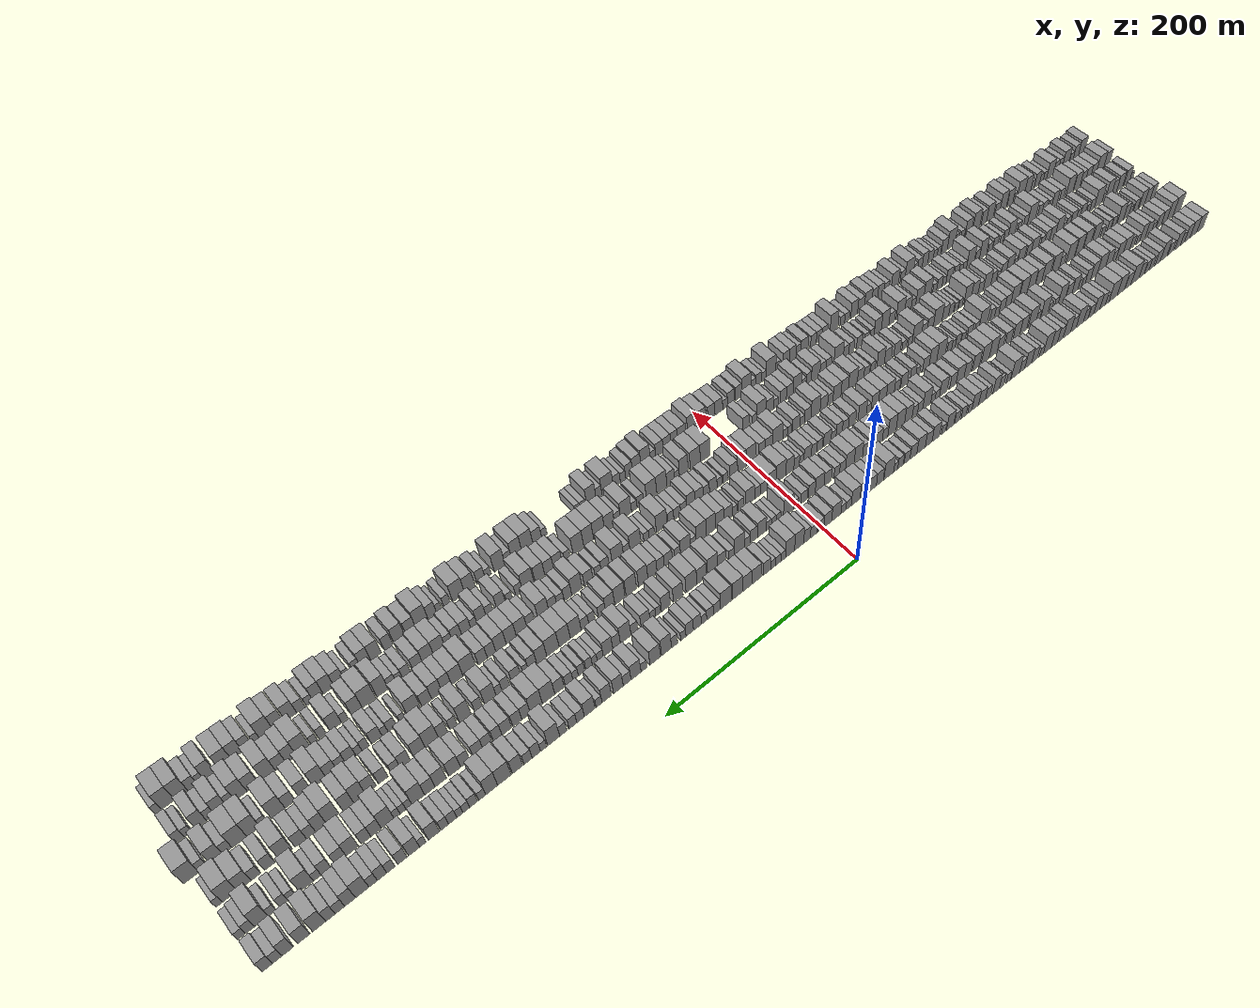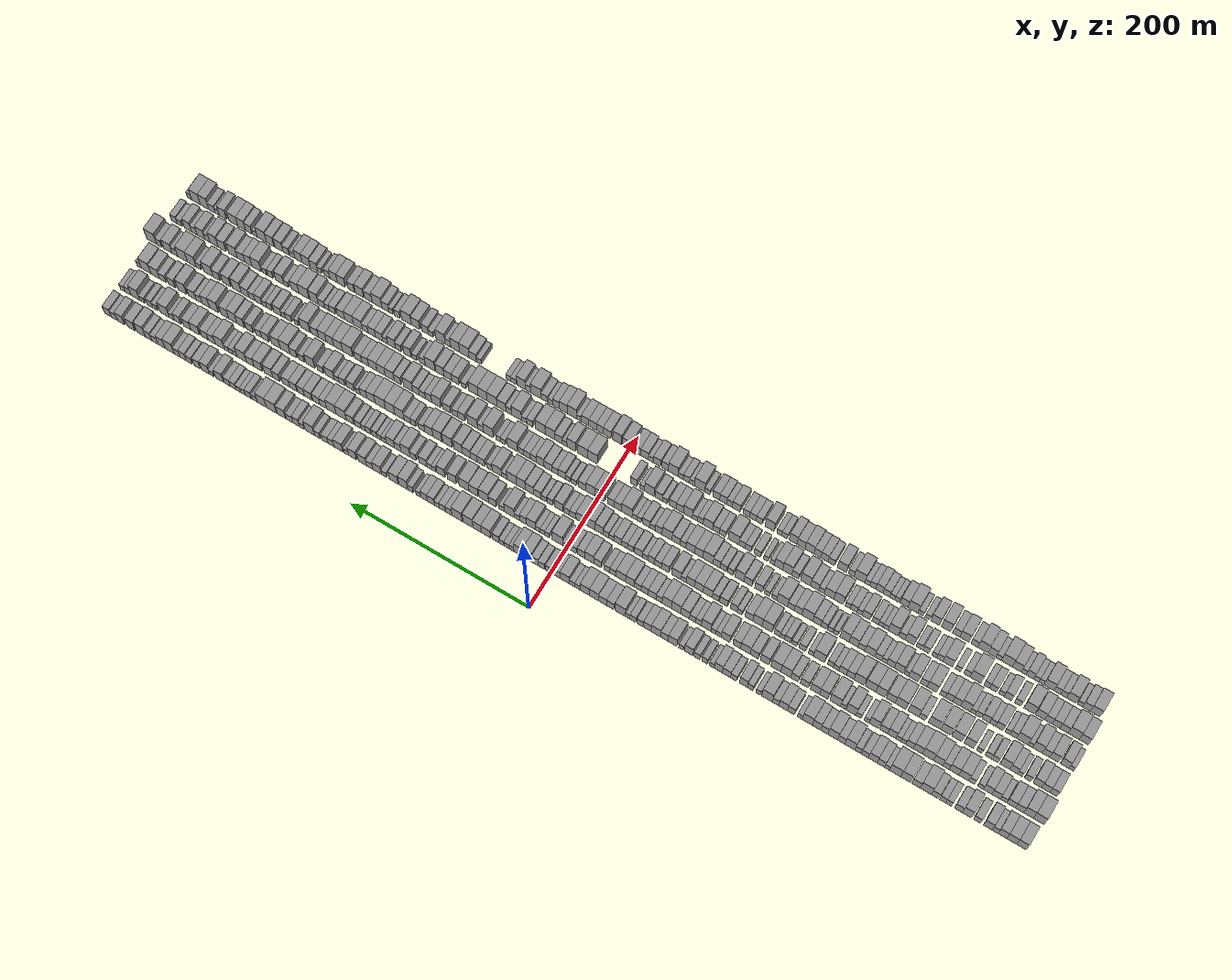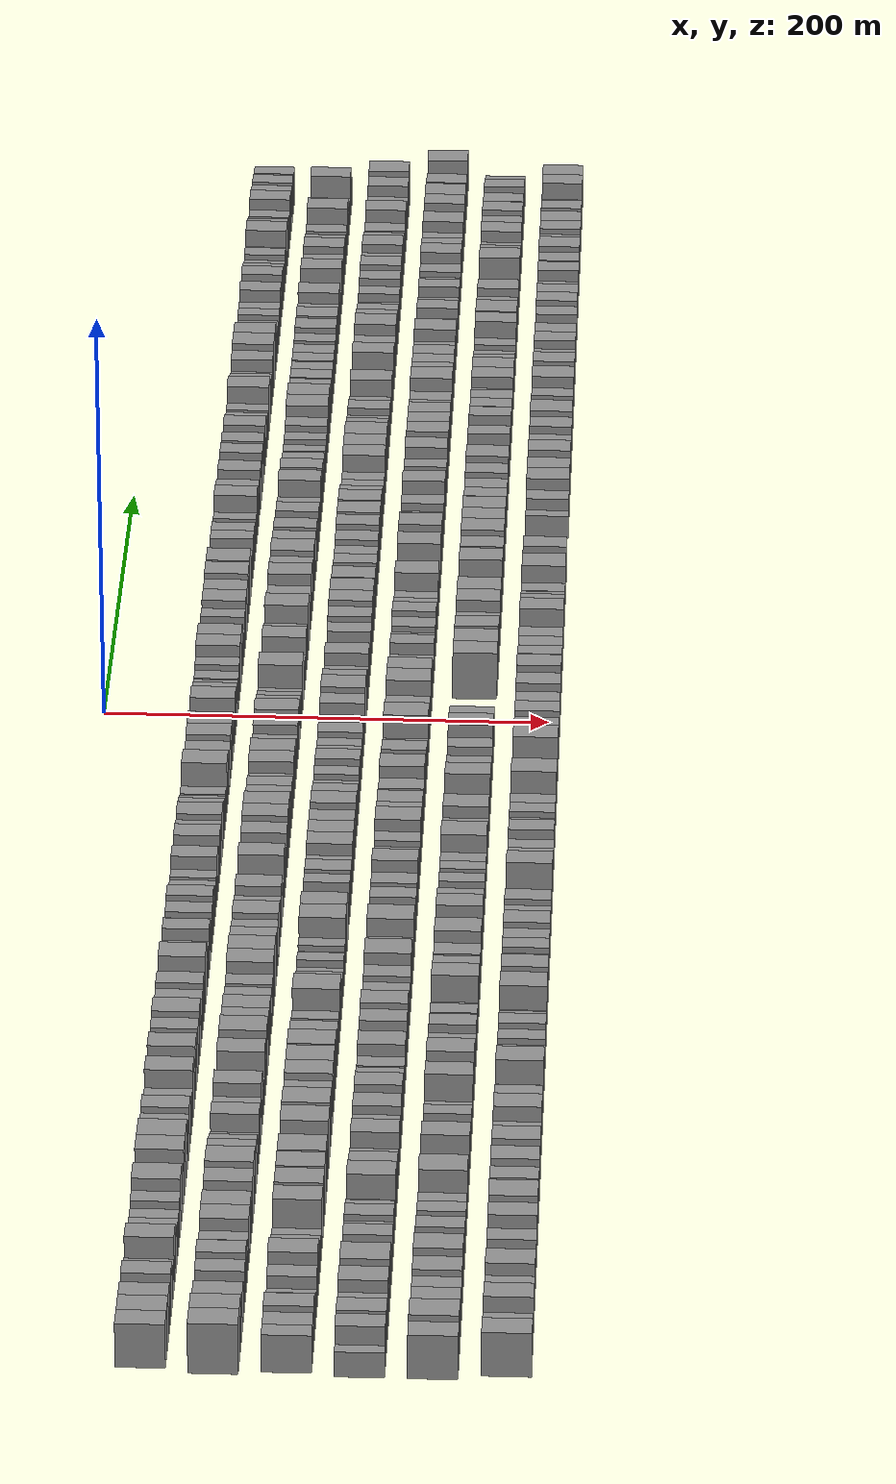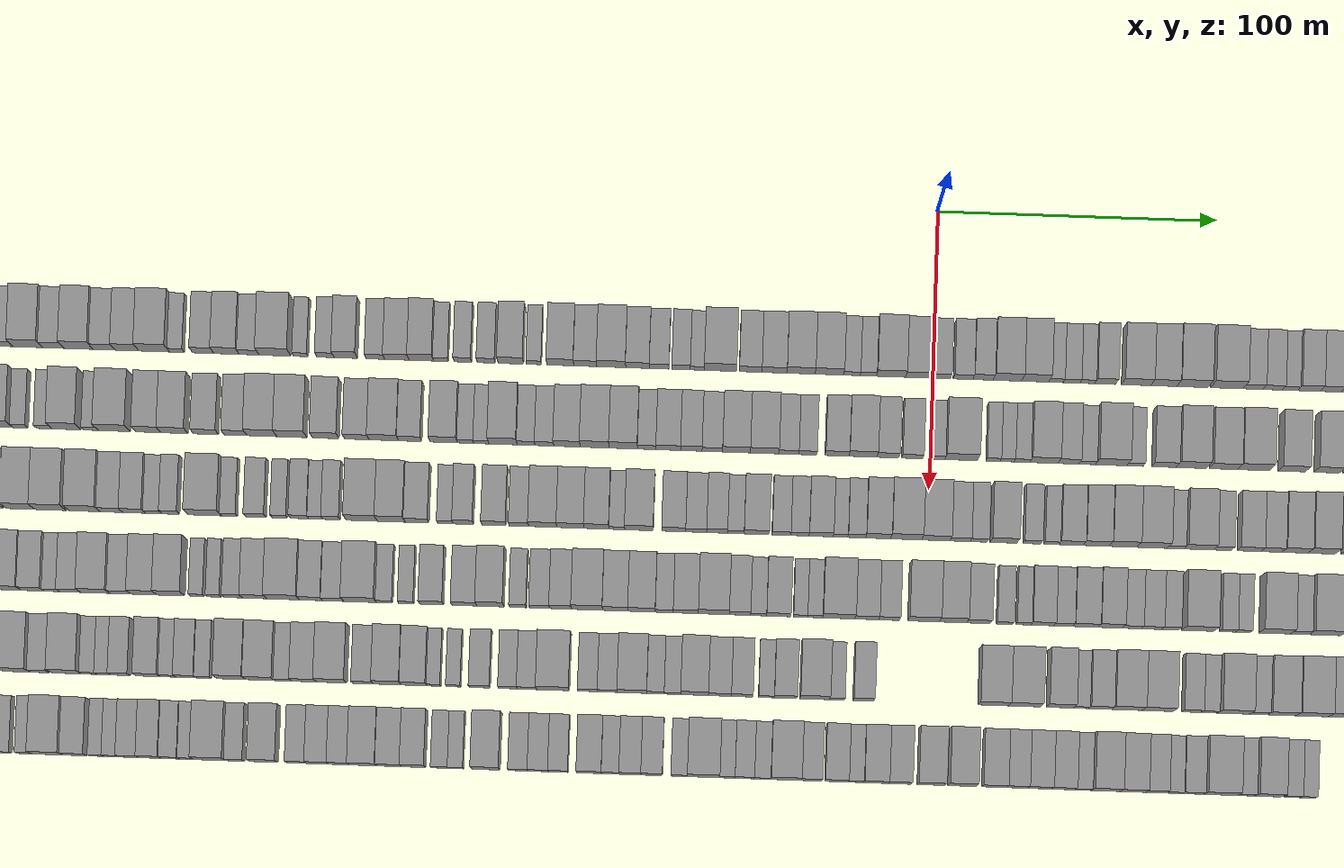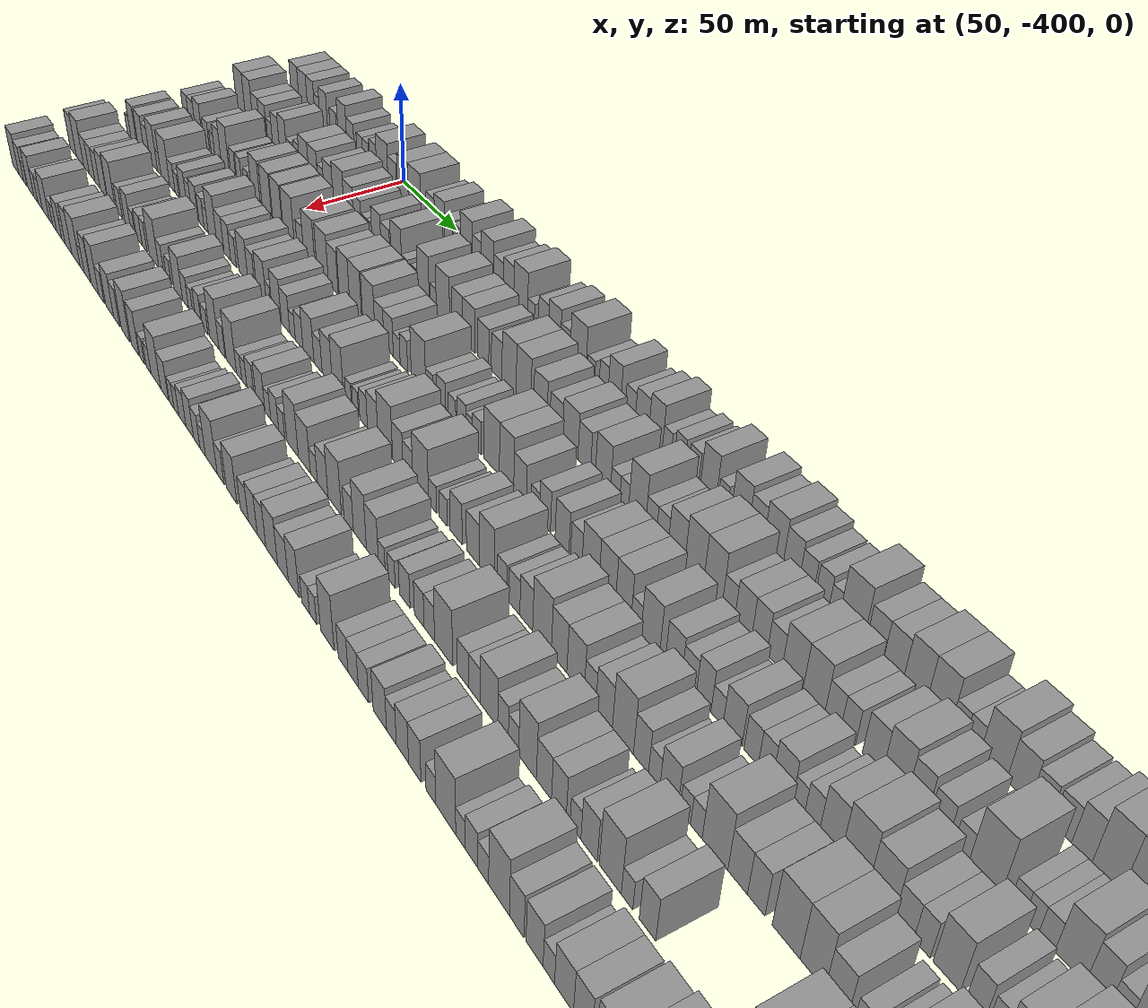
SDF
<sdf version="1.6">
 <world name="default">
  <scene>
   <sky><clouds><speed>12</speed></clouds></sky>
   <ambient>0.4 0.4 0.4 1</ambient>
   <background>0.7 0.7 0.7 1</background>
   <shadows>1</shadows>
  </scene>
  <gravity>0 0 -9.8066</gravity>
  <magnetic_field>6e-06 2.3e-05 -4.2e-05</magnetic_field>
  <physics default="0" name="default_physics" type="ode">
   <ode>
    <solver>
     <type>quick</type>
     <iters>10</iters>
     <sor>1.0</sor>
     <use_dynamic_moi_rescaling>0</use_dynamic_moi_rescaling>
    </solver>
    <constraints>
     <cfm>0</cfm>
     <erp>0.2</erp>
     <contact_max_correcting_vel>100</contact_max_correcting_vel>
     <contact_surface_layer>0.001</contact_surface_layer>
    </constraints>
   </ode>
   <max_step_size>0.004</max_step_size>
   <real_time_factor>1</real_time_factor>
   <real_time_update_rate>250</real_time_update_rate>
  </physics>
  <light name="sun" type="directional">
   <pose>0 0 10 0 0 0</pose>
   <diffuse>0.8 0.8 0.8 1</diffuse>
   <specular>0.2 0.2 0.2 1</specular>
   <attenuation>
    <range>1000</range>
    <constant>0.9</constant>
    <linear>0.01</linear>
    <quadratic>0.001</quadratic>
   </attenuation>
   <direction>-0.5 0.1 -0.9</direction>
  </light>
  <model name="building_1">
   <static>1</static>
   <pose>50.0000 -502.1199 0 0.000000 0.000000 0.000000</pose>
   <link name="link">
    <pose>0 0 10.50 0 0 0</pose>
    <collision name="collision"><geometry><box><size>20.0000 9.7603 21.0000</size></box></geometry></collision>
    <visual name="visual">
     <cast_shadows>0</cast_shadows>
     <geometry><box><size>20.0000 9.7603 21.0000</size></box></geometry>
     <material>
      <script>
       <uri>model://grey_wall/materials/scripts</uri>
       <uri>model://grey_wall/materials/textures</uri>
       <name>vrc/grey_wall</name>
      </script>
     </material>
    </visual>
   </link>
  </model>
  <model name="building_2">
   <static>1</static>
   <pose>50.0000 -492.0480 0 0.000000 0.000000 0.000000</pose>
   <link name="link">
    <pose>0 0 10.50 0 0 0</pose>
    <collision name="collision"><geometry><box><size>20.0000 10.3834 21.0000</size></box></geometry></collision>
    <visual name="visual">
     <cast_shadows>0</cast_shadows>
     <geometry><box><size>20.0000 10.3834 21.0000</size></box></geometry>
     <material>
      <script>
       <uri>model://grey_wall/materials/scripts</uri>
       <uri>model://grey_wall/materials/textures</uri>
       <name>vrc/grey_wall</name>
      </script>
     </material>
    </visual>
   </link>
  </model>
  <model name="building_3">
   <static>1</static>
   <pose>50.0000 -482.4147 0 0.000000 0.000000 0.000000</pose>
   <link name="link">
    <pose>0 0 10.50 0 0 0</pose>
    <collision name="collision"><geometry><box><size>20.0000 8.8831 21.0000</size></box></geometry></collision>
    <visual name="visual">
     <cast_shadows>0</cast_shadows>
     <geometry><box><size>20.0000 8.8831 21.0000</size></box></geometry>
     <material>
      <script>
       <uri>model://grey_wall/materials/scripts</uri>
       <uri>model://grey_wall/materials/textures</uri>
       <name>vrc/grey_wall</name>
      </script>
     </material>
    </visual>
   </link>
  </model>
  <model name="building_4">
   <static>1</static>
   <pose>50.0000 -474.9057 0 0.000000 0.000000 0.000000</pose>
   <link name="link">
    <pose>0 0 7.50 0 0 0</pose>
    <collision name="collision"><geometry><box><size>20.0000 6.1351 15.0000</size></box></geometry></collision>
    <visual name="visual">
     <cast_shadows>0</cast_shadows>
     <geometry><box><size>20.0000 6.1351 15.0000</size></box></geometry>
     <material>
      <script>
       <uri>model://grey_wall/materials/scripts</uri>
       <uri>model://grey_wall/materials/textures</uri>
       <name>vrc/grey_wall</name>
      </script>
     </material>
    </visual>
   </link>
  </model>
  <model name="building_5">
   <static>1</static>
   <pose>50.0000 -467.4099 0 0.000000 0.000000 0.000000</pose>
   <link name="link">
    <pose>0 0 10.50 0 0 0</pose>
    <collision name="collision"><geometry><box><size>20.0000 8.8565 21.0000</size></box></geometry></collision>
    <visual name="visual">
     <cast_shadows>0</cast_shadows>
     <geometry><box><size>20.0000 8.8565 21.0000</size></box></geometry>
     <material>
      <script>
       <uri>model://grey_wall/materials/scripts</uri>
       <uri>model://grey_wall/materials/textures</uri>
       <name>vrc/grey_wall</name>
      </script>
     </material>
    </visual>
   </link>
  </model>
  <model name="building_6">
   <static>1</static>
   <pose>50.0000 -456.2871 0 0.000000 0.000000 0.000000</pose>
   <link name="link">
    <pose>0 0 7.50 0 0 0</pose>
    <collision name="collision"><geometry><box><size>20.0000 7.3890 15.0000</size></box></geometry></collision>
    <visual name="visual">
     <cast_shadows>0</cast_shadows>
     <geometry><box><size>20.0000 7.3890 15.0000</size></box></geometry>
     <material>
      <script>
       <uri>model://grey_wall/materials/scripts</uri>
       <uri>model://grey_wall/materials/textures</uri>
       <name>vrc/grey_wall</name>
      </script>
     </material>
    </visual>
   </link>
  </model>
  <model name="building_7">
   <static>1</static>
   <pose>50.0000 -445.7349 0 0.000000 0.000000 0.000000</pose>
   <link name="link">
    <pose>0 0 12.00 0 0 0</pose>
    <collision name="collision"><geometry><box><size>20.0000 9.7154 24.0000</size></box></geometry></collision>
    <visual name="visual">
     <cast_shadows>0</cast_shadows>
     <geometry><box><size>20.0000 9.7154 24.0000</size></box></geometry>
     <material>
      <script>
       <uri>model://grey_wall/materials/scripts</uri>
       <uri>model://grey_wall/materials/textures</uri>
       <name>vrc/grey_wall</name>
      </script>
     </material>
    </visual>
   </link>
  </model>
  <model name="building_8">
   <static>1</static>
   <pose>50.0000 -436.8042 0 0.000000 0.000000 0.000000</pose>
   <link name="link">
    <pose>0 0 9.00 0 0 0</pose>
    <collision name="collision"><geometry><box><size>20.0000 8.1459 18.0000</size></box></geometry></collision>
    <visual name="visual">
     <cast_shadows>0</cast_shadows>
     <geometry><box><size>20.0000 8.1459 18.0000</size></box></geometry>
     <material>
      <script>
       <uri>model://grey_wall/materials/scripts</uri>
       <uri>model://grey_wall/materials/textures</uri>
       <name>vrc/grey_wall</name>
      </script>
     </material>
    </visual>
   </link>
  </model>
  <model name="building_9">
   <static>1</static>
   <pose>50.0000 -426.6734 0 0.000000 0.000000 0.000000</pose>
   <link name="link">
    <pose>0 0 7.50 0 0 0</pose>
    <collision name="collision"><geometry><box><size>20.0000 6.1158 15.0000</size></box></geometry></collision>
    <visual name="visual">
     <cast_shadows>0</cast_shadows>
     <geometry><box><size>20.0000 6.1158 15.0000</size></box></geometry>
     <material>
      <script>
       <uri>model://grey_wall/materials/scripts</uri>
       <uri>model://grey_wall/materials/textures</uri>
       <name>vrc/grey_wall</name>
      </script>
     </material>
    </visual>
   </link>
  </model>
  <model name="building_10">
   <static>1</static>
   <pose>50.0000 -420.3480 0 0.000000 0.000000 0.000000</pose>
   <link name="link">
    <pose>0 0 7.50 0 0 0</pose>
    <collision name="collision"><geometry><box><size>20.0000 6.5350 15.0000</size></box></geometry></collision>
    <visual name="visual">
     <cast_shadows>0</cast_shadows>
     <geometry><box><size>20.0000 6.5350 15.0000</size></box></geometry>
     <material>
      <script>
       <uri>model://grey_wall/materials/scripts</uri>
       <uri>model://grey_wall/materials/textures</uri>
       <name>vrc/grey_wall</name>
      </script>
     </material>
    </visual>
   </link>
  </model>
  <model name="building_11">
   <static>1</static>
   <pose>50.0000 -412.3741 0 0.000000 0.000000 0.000000</pose>
   <link name="link">
    <pose>0 0 9.00 0 0 0</pose>
    <collision name="collision"><geometry><box><size>20.0000 7.4129 18.0000</size></box></geometry></collision>
    <visual name="visual">
     <cast_shadows>0</cast_shadows>
     <geometry><box><size>20.0000 7.4129 18.0000</size></box></geometry>
     <material>
      <script>
       <uri>model://grey_wall/materials/scripts</uri>
       <uri>model://grey_wall/materials/textures</uri>
       <name>vrc/grey_wall</name>
      </script>
     </material>
    </visual>
   </link>
  </model>
  <model name="building_12">
   <static>1</static>
   <pose>50.0000 -402.8266 0 0.000000 0.000000 0.000000</pose>
   <link name="link">
    <pose>0 0 12.00 0 0 0</pose>
    <collision name="collision"><geometry><box><size>20.0000 11.6821 24.0000</size></box></geometry></collision>
    <visual name="visual">
     <cast_shadows>0</cast_shadows>
     <geometry><box><size>20.0000 11.6821 24.0000</size></box></geometry>
     <material>
      <script>
       <uri>model://grey_wall/materials/scripts</uri>
       <uri>model://grey_wall/materials/textures</uri>
       <name>vrc/grey_wall</name>
      </script>
     </material>
    </visual>
   </link>
  </model>
  <model name="building_13">
   <static>1</static>
   <pose>50.0000 -392.5859 0 0.000000 0.000000 0.000000</pose>
   <link name="link">
    <pose>0 0 9.00 0 0 0</pose>
    <collision name="collision"><geometry><box><size>20.0000 8.7992 18.0000</size></box></geometry></collision>
    <visual name="visual">
     <cast_shadows>0</cast_shadows>
     <geometry><box><size>20.0000 8.7992 18.0000</size></box></geometry>
     <material>
      <script>
       <uri>model://grey_wall/materials/scripts</uri>
       <uri>model://grey_wall/materials/textures</uri>
       <name>vrc/grey_wall</name>
      </script>
     </material>
    </visual>
   </link>
  </model>
  <model name="building_14">
   <static>1</static>
   <pose>50.0000 -381.9182 0 0.000000 0.000000 0.000000</pose>
   <link name="link">
    <pose>0 0 12.00 0 0 0</pose>
    <collision name="collision"><geometry><box><size>20.0000 10.5363 24.0000</size></box></geometry></collision>
    <visual name="visual">
     <cast_shadows>0</cast_shadows>
     <geometry><box><size>20.0000 10.5363 24.0000</size></box></geometry>
     <material>
      <script>
       <uri>model://grey_wall/materials/scripts</uri>
       <uri>model://grey_wall/materials/textures</uri>
       <name>vrc/grey_wall</name>
      </script>
     </material>
    </visual>
   </link>
  </model>
  <model name="building_15">
   <static>1</static>
   <pose>50.0000 -370.6933 0 0.000000 0.000000 0.000000</pose>
   <link name="link">
    <pose>0 0 12.00 0 0 0</pose>
    <collision name="collision"><geometry><box><size>20.0000 11.9134 24.0000</size></box></geometry></collision>
    <visual name="visual">
     <cast_shadows>0</cast_shadows>
     <geometry><box><size>20.0000 11.9134 24.0000</size></box></geometry>
     <material>
      <script>
       <uri>model://grey_wall/materials/scripts</uri>
       <uri>model://grey_wall/materials/textures</uri>
       <name>vrc/grey_wall</name>
      </script>
     </material>
    </visual>
   </link>
  </model>
  <model name="building_16">
   <static>1</static>
   <pose>50.0000 -362.1890 0 0.000000 0.000000 0.000000</pose>
   <link name="link">
    <pose>0 0 6.00 0 0 0</pose>
    <collision name="collision"><geometry><box><size>20.0000 5.0953 12.0000</size></box></geometry></collision>
    <visual name="visual">
     <cast_shadows>0</cast_shadows>
     <geometry><box><size>20.0000 5.0953 12.0000</size></box></geometry>
     <material>
      <script>
       <uri>model://grey_wall/materials/scripts</uri>
       <uri>model://grey_wall/materials/textures</uri>
       <name>vrc/grey_wall</name>
      </script>
     </material>
    </visual>
   </link>
  </model>
  <model name="building_17">
   <static>1</static>
   <pose>50.0000 -355.6425 0 0.000000 0.000000 0.000000</pose>
   <link name="link">
    <pose>0 0 9.00 0 0 0</pose>
    <collision name="collision"><geometry><box><size>20.0000 7.9978 18.0000</size></box></geometry></collision>
    <visual name="visual">
     <cast_shadows>0</cast_shadows>
     <geometry><box><size>20.0000 7.9978 18.0000</size></box></geometry>
     <material>
      <script>
       <uri>model://grey_wall/materials/scripts</uri>
       <uri>model://grey_wall/materials/textures</uri>
       <name>vrc/grey_wall</name>
      </script>
     </material>
    </visual>
   </link>
  </model>
  <model name="building_18">
   <static>1</static>
   <pose>50.0000 -347.1063 0 0.000000 0.000000 0.000000</pose>
   <link name="link">
    <pose>0 0 10.50 0 0 0</pose>
    <collision name="collision"><geometry><box><size>20.0000 9.0746 21.0000</size></box></geometry></collision>
    <visual name="visual">
     <cast_shadows>0</cast_shadows>
     <geometry><box><size>20.0000 9.0746 21.0000</size></box></geometry>
     <material>
      <script>
       <uri>model://grey_wall/materials/scripts</uri>
       <uri>model://grey_wall/materials/textures</uri>
       <name>vrc/grey_wall</name>
      </script>
     </material>
    </visual>
   </link>
  </model>
  <model name="building_19">
   <static>1</static>
   <pose>50.0000 -338.9783 0 0.000000 0.000000 0.000000</pose>
   <link name="link">
    <pose>0 0 7.50 0 0 0</pose>
    <collision name="collision"><geometry><box><size>20.0000 7.1814 15.0000</size></box></geometry></collision>
    <visual name="visual">
     <cast_shadows>0</cast_shadows>
     <geometry><box><size>20.0000 7.1814 15.0000</size></box></geometry>
     <material>
      <script>
       <uri>model://grey_wall/materials/scripts</uri>
       <uri>model://grey_wall/materials/textures</uri>
       <name>vrc/grey_wall</name>
      </script>
     </material>
    </visual>
   </link>
  </model>
  <model name="building_20">
   <static>1</static>
   <pose>50.0000 -331.3284 0 0.000000 0.000000 0.000000</pose>
   <link name="link">
    <pose>0 0 7.50 0 0 0</pose>
    <collision name="collision"><geometry><box><size>20.0000 6.1185 15.0000</size></box></geometry></collision>
    <visual name="visual">
     <cast_shadows>0</cast_shadows>
     <geometry><box><size>20.0000 6.1185 15.0000</size></box></geometry>
     <material>
      <script>
       <uri>model://grey_wall/materials/scripts</uri>
       <uri>model://grey_wall/materials/textures</uri>
       <name>vrc/grey_wall</name>
      </script>
     </material>
    </visual>
   </link>
  </model>
  <model name="building_21">
   <static>1</static>
   <pose>50.0000 -322.9980 0 0.000000 0.000000 0.000000</pose>
   <link name="link">
    <pose>0 0 12.00 0 0 0</pose>
    <collision name="collision"><geometry><box><size>20.0000 10.5423 24.0000</size></box></geometry></collision>
    <visual name="visual">
     <cast_shadows>0</cast_shadows>
     <geometry><box><size>20.0000 10.5423 24.0000</size></box></geometry>
     <material>
      <script>
       <uri>model://grey_wall/materials/scripts</uri>
       <uri>model://grey_wall/materials/textures</uri>
       <name>vrc/grey_wall</name>
      </script>
     </material>
    </visual>
   </link>
  </model>
  <model name="building_22">
   <static>1</static>
   <pose>50.0000 -313.8811 0 0.000000 0.000000 0.000000</pose>
   <link name="link">
    <pose>0 0 9.00 0 0 0</pose>
    <collision name="collision"><geometry><box><size>20.0000 7.6914 18.0000</size></box></geometry></collision>
    <visual name="visual">
     <cast_shadows>0</cast_shadows>
     <geometry><box><size>20.0000 7.6914 18.0000</size></box></geometry>
     <material>
      <script>
       <uri>model://grey_wall/materials/scripts</uri>
       <uri>model://grey_wall/materials/textures</uri>
       <name>vrc/grey_wall</name>
      </script>
     </material>
    </visual>
   </link>
  </model>
  <model name="building_23">
   <static>1</static>
   <pose>50.0000 -304.8590 0 0.000000 0.000000 0.000000</pose>
   <link name="link">
    <pose>0 0 12.00 0 0 0</pose>
    <collision name="collision"><geometry><box><size>20.0000 10.3528 24.0000</size></box></geometry></collision>
    <visual name="visual">
     <cast_shadows>0</cast_shadows>
     <geometry><box><size>20.0000 10.3528 24.0000</size></box></geometry>
     <material>
      <script>
       <uri>model://grey_wall/materials/scripts</uri>
       <uri>model://grey_wall/materials/textures</uri>
       <name>vrc/grey_wall</name>
      </script>
     </material>
    </visual>
   </link>
  </model>
  <model name="building_24">
   <static>1</static>
   <pose>50.0000 -295.7935 0 0.000000 0.000000 0.000000</pose>
   <link name="link">
    <pose>0 0 9.00 0 0 0</pose>
    <collision name="collision"><geometry><box><size>20.0000 7.7783 18.0000</size></box></geometry></collision>
    <visual name="visual">
     <cast_shadows>0</cast_shadows>
     <geometry><box><size>20.0000 7.7783 18.0000</size></box></geometry>
     <material>
      <script>
       <uri>model://grey_wall/materials/scripts</uri>
       <uri>model://grey_wall/materials/textures</uri>
       <name>vrc/grey_wall</name>
      </script>
     </material>
    </visual>
   </link>
  </model>
  <model name="building_25">
   <static>1</static>
   <pose>50.0000 -287.6442 0 0.000000 0.000000 0.000000</pose>
   <link name="link">
    <pose>0 0 10.50 0 0 0</pose>
    <collision name="collision"><geometry><box><size>20.0000 8.5202 21.0000</size></box></geometry></collision>
    <visual name="visual">
     <cast_shadows>0</cast_shadows>
     <geometry><box><size>20.0000 8.5202 21.0000</size></box></geometry>
     <material>
      <script>
       <uri>model://grey_wall/materials/scripts</uri>
       <uri>model://grey_wall/materials/textures</uri>
       <name>vrc/grey_wall</name>
      </script>
     </material>
    </visual>
   </link>
  </model>
  <model name="building_26">
   <static>1</static>
   <pose>50.0000 -277.9090 0 0.000000 0.000000 0.000000</pose>
   <link name="link">
    <pose>0 0 12.00 0 0 0</pose>
    <collision name="collision"><geometry><box><size>20.0000 10.9503 24.0000</size></box></geometry></collision>
    <visual name="visual">
     <cast_shadows>0</cast_shadows>
     <geometry><box><size>20.0000 10.9503 24.0000</size></box></geometry>
     <material>
      <script>
       <uri>model://grey_wall/materials/scripts</uri>
       <uri>model://grey_wall/materials/textures</uri>
       <name>vrc/grey_wall</name>
      </script>
     </material>
    </visual>
   </link>
  </model>
  <model name="building_27">
   <static>1</static>
   <pose>50.0000 -269.7770 0 0.000000 0.000000 0.000000</pose>
   <link name="link">
    <pose>0 0 6.00 0 0 0</pose>
    <collision name="collision"><geometry><box><size>20.0000 5.3138 12.0000</size></box></geometry></collision>
    <visual name="visual">
     <cast_shadows>0</cast_shadows>
     <geometry><box><size>20.0000 5.3138 12.0000</size></box></geometry>
     <material>
      <script>
       <uri>model://grey_wall/materials/scripts</uri>
       <uri>model://grey_wall/materials/textures</uri>
       <name>vrc/grey_wall</name>
      </script>
     </material>
    </visual>
   </link>
  </model>
  <model name="building_28">
   <static>1</static>
   <pose>50.0000 -260.3214 0 0.000000 0.000000 0.000000</pose>
   <link name="link">
    <pose>0 0 9.00 0 0 0</pose>
    <collision name="collision"><geometry><box><size>20.0000 7.5975 18.0000</size></box></geometry></collision>
    <visual name="visual">
     <cast_shadows>0</cast_shadows>
     <geometry><box><size>20.0000 7.5975 18.0000</size></box></geometry>
     <material>
      <script>
       <uri>model://grey_wall/materials/scripts</uri>
       <uri>model://grey_wall/materials/textures</uri>
       <name>vrc/grey_wall</name>
      </script>
     </material>
    </visual>
   </link>
  </model>
  <model name="building_29">
   <static>1</static>
   <pose>50.0000 -251.9993 0 0.000000 0.000000 0.000000</pose>
   <link name="link">
    <pose>0 0 10.50 0 0 0</pose>
    <collision name="collision"><geometry><box><size>20.0000 9.0466 21.0000</size></box></geometry></collision>
    <visual name="visual">
     <cast_shadows>0</cast_shadows>
     <geometry><box><size>20.0000 9.0466 21.0000</size></box></geometry>
     <material>
      <script>
       <uri>model://grey_wall/materials/scripts</uri>
       <uri>model://grey_wall/materials/textures</uri>
       <name>vrc/grey_wall</name>
      </script>
     </material>
    </visual>
   </link>
  </model>
  <model name="building_30">
   <static>1</static>
   <pose>50.0000 -243.9569 0 0.000000 0.000000 0.000000</pose>
   <link name="link">
    <pose>0 0 7.50 0 0 0</pose>
    <collision name="collision"><geometry><box><size>20.0000 7.0382 15.0000</size></box></geometry></collision>
    <visual name="visual">
     <cast_shadows>0</cast_shadows>
     <geometry><box><size>20.0000 7.0382 15.0000</size></box></geometry>
     <material>
      <script>
       <uri>model://grey_wall/materials/scripts</uri>
       <uri>model://grey_wall/materials/textures</uri>
       <name>vrc/grey_wall</name>
      </script>
     </material>
    </visual>
   </link>
  </model>
  <model name="building_31">
   <static>1</static>
   <pose>50.0000 -234.7610 0 0.000000 0.000000 0.000000</pose>
   <link name="link">
    <pose>0 0 12.00 0 0 0</pose>
    <collision name="collision"><geometry><box><size>20.0000 11.3537 24.0000</size></box></geometry></collision>
    <visual name="visual">
     <cast_shadows>0</cast_shadows>
     <geometry><box><size>20.0000 11.3537 24.0000</size></box></geometry>
     <material>
      <script>
       <uri>model://grey_wall/materials/scripts</uri>
       <uri>model://grey_wall/materials/textures</uri>
       <name>vrc/grey_wall</name>
      </script>
     </material>
    </visual>
   </link>
  </model>
  <model name="building_32">
   <static>1</static>
   <pose>50.0000 -225.4510 0 0.000000 0.000000 0.000000</pose>
   <link name="link">
    <pose>0 0 6.00 0 0 0</pose>
    <collision name="collision"><geometry><box><size>20.0000 5.2663 12.0000</size></box></geometry></collision>
    <visual name="visual">
     <cast_shadows>0</cast_shadows>
     <geometry><box><size>20.0000 5.2663 12.0000</size></box></geometry>
     <material>
      <script>
       <uri>model://grey_wall/materials/scripts</uri>
       <uri>model://grey_wall/materials/textures</uri>
       <name>vrc/grey_wall</name>
      </script>
     </material>
    </visual>
   </link>
  </model>
  <model name="building_33">
   <static>1</static>
   <pose>50.0000 -216.7390 0 0.000000 0.000000 0.000000</pose>
   <link name="link">
    <pose>0 0 7.50 0 0 0</pose>
    <collision name="collision"><geometry><box><size>20.0000 6.1576 15.0000</size></box></geometry></collision>
    <visual name="visual">
     <cast_shadows>0</cast_shadows>
     <geometry><box><size>20.0000 6.1576 15.0000</size></box></geometry>
     <material>
      <script>
       <uri>model://grey_wall/materials/scripts</uri>
       <uri>model://grey_wall/materials/textures</uri>
       <name>vrc/grey_wall</name>
      </script>
     </material>
    </visual>
   </link>
  </model>
  <model name="building_34">
   <static>1</static>
   <pose>50.0000 -209.4350 0 0.000000 0.000000 0.000000</pose>
   <link name="link">
    <pose>0 0 10.50 0 0 0</pose>
    <collision name="collision"><geometry><box><size>20.0000 8.4504 21.0000</size></box></geometry></collision>
    <visual name="visual">
     <cast_shadows>0</cast_shadows>
     <geometry><box><size>20.0000 8.4504 21.0000</size></box></geometry>
     <material>
      <script>
       <uri>model://grey_wall/materials/scripts</uri>
       <uri>model://grey_wall/materials/textures</uri>
       <name>vrc/grey_wall</name>
      </script>
     </material>
    </visual>
   </link>
  </model>
  <model name="building_35">
   <static>1</static>
   <pose>50.0000 -198.8877 0 0.000000 0.000000 0.000000</pose>
   <link name="link">
    <pose>0 0 7.50 0 0 0</pose>
    <collision name="collision"><geometry><box><size>20.0000 6.6442 15.0000</size></box></geometry></collision>
    <visual name="visual">
     <cast_shadows>0</cast_shadows>
     <geometry><box><size>20.0000 6.6442 15.0000</size></box></geometry>
     <material>
      <script>
       <uri>model://grey_wall/materials/scripts</uri>
       <uri>model://grey_wall/materials/textures</uri>
       <name>vrc/grey_wall</name>
      </script>
     </material>
    </visual>
   </link>
  </model>
  <model name="building_36">
   <static>1</static>
   <pose>50.0000 -191.1998 0 0.000000 0.000000 0.000000</pose>
   <link name="link">
    <pose>0 0 9.00 0 0 0</pose>
    <collision name="collision"><geometry><box><size>20.0000 8.7317 18.0000</size></box></geometry></collision>
    <visual name="visual">
     <cast_shadows>0</cast_shadows>
     <geometry><box><size>20.0000 8.7317 18.0000</size></box></geometry>
     <material>
      <script>
       <uri>model://grey_wall/materials/scripts</uri>
       <uri>model://grey_wall/materials/textures</uri>
       <name>vrc/grey_wall</name>
      </script>
     </material>
    </visual>
   </link>
  </model>
  <model name="building_37">
   <static>1</static>
   <pose>50.0000 -182.4691 0 0.000000 0.000000 0.000000</pose>
   <link name="link">
    <pose>0 0 10.50 0 0 0</pose>
    <collision name="collision"><geometry><box><size>20.0000 8.7298 21.0000</size></box></geometry></collision>
    <visual name="visual">
     <cast_shadows>0</cast_shadows>
     <geometry><box><size>20.0000 8.7298 21.0000</size></box></geometry>
     <material>
      <script>
       <uri>model://grey_wall/materials/scripts</uri>
       <uri>model://grey_wall/materials/textures</uri>
       <name>vrc/grey_wall</name>
      </script>
     </material>
    </visual>
   </link>
  </model>
  <model name="building_38">
   <static>1</static>
   <pose>50.0000 -175.4326 0 0.000000 0.000000 0.000000</pose>
   <link name="link">
    <pose>0 0 6.00 0 0 0</pose>
    <collision name="collision"><geometry><box><size>20.0000 5.3432 12.0000</size></box></geometry></collision>
    <visual name="visual">
     <cast_shadows>0</cast_shadows>
     <geometry><box><size>20.0000 5.3432 12.0000</size></box></geometry>
     <material>
      <script>
       <uri>model://grey_wall/materials/scripts</uri>
       <uri>model://grey_wall/materials/textures</uri>
       <name>vrc/grey_wall</name>
      </script>
     </material>
    </visual>
   </link>
  </model>
  <model name="building_39">
   <static>1</static>
   <pose>50.0000 -167.6293 0 0.000000 0.000000 0.000000</pose>
   <link name="link">
    <pose>0 0 7.50 0 0 0</pose>
    <collision name="collision"><geometry><box><size>20.0000 6.2633 15.0000</size></box></geometry></collision>
    <visual name="visual">
     <cast_shadows>0</cast_shadows>
     <geometry><box><size>20.0000 6.2633 15.0000</size></box></geometry>
     <material>
      <script>
       <uri>model://grey_wall/materials/scripts</uri>
       <uri>model://grey_wall/materials/textures</uri>
       <name>vrc/grey_wall</name>
      </script>
     </material>
    </visual>
   </link>
  </model>
  <model name="building_40">
   <static>1</static>
   <pose>50.0000 -159.2692 0 0.000000 0.000000 0.000000</pose>
   <link name="link">
    <pose>0 0 7.50 0 0 0</pose>
    <collision name="collision"><geometry><box><size>20.0000 6.4569 15.0000</size></box></geometry></collision>
    <visual name="visual">
     <cast_shadows>0</cast_shadows>
     <geometry><box><size>20.0000 6.4569 15.0000</size></box></geometry>
     <material>
      <script>
       <uri>model://grey_wall/materials/scripts</uri>
       <uri>model://grey_wall/materials/textures</uri>
       <name>vrc/grey_wall</name>
      </script>
     </material>
    </visual>
   </link>
  </model>
  <model name="building_41">
   <static>1</static>
   <pose>50.0000 -150.4861 0 0.000000 0.000000 0.000000</pose>
   <link name="link">
    <pose>0 0 10.50 0 0 0</pose>
    <collision name="collision"><geometry><box><size>20.0000 9.1092 21.0000</size></box></geometry></collision>
    <visual name="visual">
     <cast_shadows>0</cast_shadows>
     <geometry><box><size>20.0000 9.1092 21.0000</size></box></geometry>
     <material>
      <script>
       <uri>model://grey_wall/materials/scripts</uri>
       <uri>model://grey_wall/materials/textures</uri>
       <name>vrc/grey_wall</name>
      </script>
     </material>
    </visual>
   </link>
  </model>
  <model name="building_42">
   <static>1</static>
   <pose>50.0000 -142.2494 0 0.000000 0.000000 0.000000</pose>
   <link name="link">
    <pose>0 0 6.00 0 0 0</pose>
    <collision name="collision"><geometry><box><size>20.0000 5.3642 12.0000</size></box></geometry></collision>
    <visual name="visual">
     <cast_shadows>0</cast_shadows>
     <geometry><box><size>20.0000 5.3642 12.0000</size></box></geometry>
     <material>
      <script>
       <uri>model://grey_wall/materials/scripts</uri>
       <uri>model://grey_wall/materials/textures</uri>
       <name>vrc/grey_wall</name>
      </script>
     </material>
    </visual>
   </link>
  </model>
  <model name="building_43">
   <static>1</static>
   <pose>50.0000 -132.7815 0 0.000000 0.000000 0.000000</pose>
   <link name="link">
    <pose>0 0 10.50 0 0 0</pose>
    <collision name="collision"><geometry><box><size>20.0000 9.5715 21.0000</size></box></geometry></collision>
    <visual name="visual">
     <cast_shadows>0</cast_shadows>
     <geometry><box><size>20.0000 9.5715 21.0000</size></box></geometry>
     <material>
      <script>
       <uri>model://grey_wall/materials/scripts</uri>
       <uri>model://grey_wall/materials/textures</uri>
       <name>vrc/grey_wall</name>
      </script>
     </material>
    </visual>
   </link>
  </model>
  <model name="building_44">
   <static>1</static>
   <pose>50.0000 -123.9047 0 0.000000 0.000000 0.000000</pose>
   <link name="link">
    <pose>0 0 9.00 0 0 0</pose>
    <collision name="collision"><geometry><box><size>20.0000 8.1821 18.0000</size></box></geometry></collision>
    <visual name="visual">
     <cast_shadows>0</cast_shadows>
     <geometry><box><size>20.0000 8.1821 18.0000</size></box></geometry>
     <material>
      <script>
       <uri>model://grey_wall/materials/scripts</uri>
       <uri>model://grey_wall/materials/textures</uri>
       <name>vrc/grey_wall</name>
      </script>
     </material>
    </visual>
   </link>
  </model>
  <model name="building_45">
   <static>1</static>
   <pose>50.0000 -114.6508 0 0.000000 0.000000 0.000000</pose>
   <link name="link">
    <pose>0 0 10.50 0 0 0</pose>
    <collision name="collision"><geometry><box><size>20.0000 10.3257 21.0000</size></box></geometry></collision>
    <visual name="visual">
     <cast_shadows>0</cast_shadows>
     <geometry><box><size>20.0000 10.3257 21.0000</size></box></geometry>
     <material>
      <script>
       <uri>model://grey_wall/materials/scripts</uri>
       <uri>model://grey_wall/materials/textures</uri>
       <name>vrc/grey_wall</name>
      </script>
     </material>
    </visual>
   </link>
  </model>
  <model name="building_46">
   <static>1</static>
   <pose>50.0000 -105.2731 0 0.000000 0.000000 0.000000</pose>
   <link name="link">
    <pose>0 0 9.00 0 0 0</pose>
    <collision name="collision"><geometry><box><size>20.0000 8.4298 18.0000</size></box></geometry></collision>
    <visual name="visual">
     <cast_shadows>0</cast_shadows>
     <geometry><box><size>20.0000 8.4298 18.0000</size></box></geometry>
     <material>
      <script>
       <uri>model://grey_wall/materials/scripts</uri>
       <uri>model://grey_wall/materials/textures</uri>
       <name>vrc/grey_wall</name>
      </script>
     </material>
    </visual>
   </link>
  </model>
  <model name="building_47">
   <static>1</static>
   <pose>50.0000 -97.5472 0 0.000000 0.000000 0.000000</pose>
   <link name="link">
    <pose>0 0 7.50 0 0 0</pose>
    <collision name="collision"><geometry><box><size>20.0000 7.0221 15.0000</size></box></geometry></collision>
    <visual name="visual">
     <cast_shadows>0</cast_shadows>
     <geometry><box><size>20.0000 7.0221 15.0000</size></box></geometry>
     <material>
      <script>
       <uri>model://grey_wall/materials/scripts</uri>
       <uri>model://grey_wall/materials/textures</uri>
       <name>vrc/grey_wall</name>
      </script>
     </material>
    </visual>
   </link>
  </model>
  <model name="building_48">
   <static>1</static>
   <pose>50.0000 -89.7438 0 0.000000 0.000000 0.000000</pose>
   <link name="link">
    <pose>0 0 7.50 0 0 0</pose>
    <collision name="collision"><geometry><box><size>20.0000 6.5846 15.0000</size></box></geometry></collision>
    <visual name="visual">
     <cast_shadows>0</cast_shadows>
     <geometry><box><size>20.0000 6.5846 15.0000</size></box></geometry>
     <material>
      <script>
       <uri>model://grey_wall/materials/scripts</uri>
       <uri>model://grey_wall/materials/textures</uri>
       <name>vrc/grey_wall</name>
      </script>
     </material>
    </visual>
   </link>
  </model>
  <model name="building_49">
   <static>1</static>
   <pose>50.0000 -83.9717 0 0.000000 0.000000 0.000000</pose>
   <link name="link">
    <pose>0 0 6.00 0 0 0</pose>
    <collision name="collision"><geometry><box><size>20.0000 4.9595 12.0000</size></box></geometry></collision>
    <visual name="visual">
     <cast_shadows>0</cast_shadows>
     <geometry><box><size>20.0000 4.9595 12.0000</size></box></geometry>
     <material>
      <script>
       <uri>model://grey_wall/materials/scripts</uri>
       <uri>model://grey_wall/materials/textures</uri>
       <name>vrc/grey_wall</name>
      </script>
     </material>
    </visual>
   </link>
  </model>
  <model name="building_50">
   <static>1</static>
   <pose>50.0000 -75.7507 0 0.000000 0.000000 0.000000</pose>
   <link name="link">
    <pose>0 0 12.00 0 0 0</pose>
    <collision name="collision"><geometry><box><size>20.0000 11.4825 24.0000</size></box></geometry></collision>
    <visual name="visual">
     <cast_shadows>0</cast_shadows>
     <geometry><box><size>20.0000 11.4825 24.0000</size></box></geometry>
     <material>
      <script>
       <uri>model://grey_wall/materials/scripts</uri>
       <uri>model://grey_wall/materials/textures</uri>
       <name>vrc/grey_wall</name>
      </script>
     </material>
    </visual>
   </link>
  </model>
  <model name="building_51">
   <static>1</static>
   <pose>50.0000 -64.9998 0 0.000000 0.000000 0.000000</pose>
   <link name="link">
    <pose>0 0 9.00 0 0 0</pose>
    <collision name="collision"><geometry><box><size>20.0000 8.0193 18.0000</size></box></geometry></collision>
    <visual name="visual">
     <cast_shadows>0</cast_shadows>
     <geometry><box><size>20.0000 8.0193 18.0000</size></box></geometry>
     <material>
      <script>
       <uri>model://grey_wall/materials/scripts</uri>
       <uri>model://grey_wall/materials/textures</uri>
       <name>vrc/grey_wall</name>
      </script>
     </material>
    </visual>
   </link>
  </model>
  <model name="building_52">
   <static>1</static>
   <pose>50.0000 -56.5427 0 0.000000 0.000000 0.000000</pose>
   <link name="link">
    <pose>0 0 9.00 0 0 0</pose>
    <collision name="collision"><geometry><box><size>20.0000 8.8949 18.0000</size></box></geometry></collision>
    <visual name="visual">
     <cast_shadows>0</cast_shadows>
     <geometry><box><size>20.0000 8.8949 18.0000</size></box></geometry>
     <material>
      <script>
       <uri>model://grey_wall/materials/scripts</uri>
       <uri>model://grey_wall/materials/textures</uri>
       <name>vrc/grey_wall</name>
      </script>
     </material>
    </visual>
   </link>
  </model>
  <model name="building_53">
   <static>1</static>
   <pose>50.0000 -47.0424 0 0.000000 0.000000 0.000000</pose>
   <link name="link">
    <pose>0 0 10.50 0 0 0</pose>
    <collision name="collision"><geometry><box><size>20.0000 10.1057 21.0000</size></box></geometry></collision>
    <visual name="visual">
     <cast_shadows>0</cast_shadows>
     <geometry><box><size>20.0000 10.1057 21.0000</size></box></geometry>
     <material>
      <script>
       <uri>model://grey_wall/materials/scripts</uri>
       <uri>model://grey_wall/materials/textures</uri>
       <name>vrc/grey_wall</name>
      </script>
     </material>
    </visual>
   </link>
  </model>
  <model name="building_54">
   <static>1</static>
   <pose>50.0000 -36.8938 0 0.000000 0.000000 0.000000</pose>
   <link name="link">
    <pose>0 0 10.50 0 0 0</pose>
    <collision name="collision"><geometry><box><size>20.0000 10.1916 21.0000</size></box></geometry></collision>
    <visual name="visual">
     <cast_shadows>0</cast_shadows>
     <geometry><box><size>20.0000 10.1916 21.0000</size></box></geometry>
     <material>
      <script>
       <uri>model://grey_wall/materials/scripts</uri>
       <uri>model://grey_wall/materials/textures</uri>
       <name>vrc/grey_wall</name>
      </script>
     </material>
    </visual>
   </link>
  </model>
  <model name="building_55">
   <static>1</static>
   <pose>50.0000 -28.8318 0 0.000000 0.000000 0.000000</pose>
   <link name="link">
    <pose>0 0 6.00 0 0 0</pose>
    <collision name="collision"><geometry><box><size>20.0000 5.9323 12.0000</size></box></geometry></collision>
    <visual name="visual">
     <cast_shadows>0</cast_shadows>
     <geometry><box><size>20.0000 5.9323 12.0000</size></box></geometry>
     <material>
      <script>
       <uri>model://grey_wall/materials/scripts</uri>
       <uri>model://grey_wall/materials/textures</uri>
       <name>vrc/grey_wall</name>
      </script>
     </material>
    </visual>
   </link>
  </model>
  <model name="building_56">
   <static>1</static>
   <pose>50.0000 -22.9451 0 0.000000 0.000000 0.000000</pose>
   <link name="link">
    <pose>0 0 6.00 0 0 0</pose>
    <collision name="collision"><geometry><box><size>20.0000 5.8412 12.0000</size></box></geometry></collision>
    <visual name="visual">
     <cast_shadows>0</cast_shadows>
     <geometry><box><size>20.0000 5.8412 12.0000</size></box></geometry>
     <material>
      <script>
       <uri>model://grey_wall/materials/scripts</uri>
       <uri>model://grey_wall/materials/textures</uri>
       <name>vrc/grey_wall</name>
      </script>
     </material>
    </visual>
   </link>
  </model>
  <model name="building_57">
   <static>1</static>
   <pose>50.0000 -14.8124 0 0.000000 0.000000 0.000000</pose>
   <link name="link">
    <pose>0 0 10.50 0 0 0</pose>
    <collision name="collision"><geometry><box><size>20.0000 10.4241 21.0000</size></box></geometry></collision>
    <visual name="visual">
     <cast_shadows>0</cast_shadows>
     <geometry><box><size>20.0000 10.4241 21.0000</size></box></geometry>
     <material>
      <script>
       <uri>model://grey_wall/materials/scripts</uri>
       <uri>model://grey_wall/materials/textures</uri>
       <name>vrc/grey_wall</name>
      </script>
     </material>
    </visual>
   </link>
  </model>
  <model name="building_58">
   <static>1</static>
   <pose>50.0000 -5.2370 0 0.000000 0.000000 0.000000</pose>
   <link name="link">
    <pose>0 0 9.00 0 0 0</pose>
    <collision name="collision"><geometry><box><size>20.0000 8.7269 18.0000</size></box></geometry></collision>
    <visual name="visual">
     <cast_shadows>0</cast_shadows>
     <geometry><box><size>20.0000 8.7269 18.0000</size></box></geometry>
     <material>
      <script>
       <uri>model://grey_wall/materials/scripts</uri>
       <uri>model://grey_wall/materials/textures</uri>
       <name>vrc/grey_wall</name>
      </script>
     </material>
    </visual>
   </link>
  </model>
  <model name="building_59">
   <static>1</static>
   <pose>50.0000 2.7610 0 0.000000 0.000000 0.000000</pose>
   <link name="link">
    <pose>0 0 7.50 0 0 0</pose>
    <collision name="collision"><geometry><box><size>20.0000 7.2690 15.0000</size></box></geometry></collision>
    <visual name="visual">
     <cast_shadows>0</cast_shadows>
     <geometry><box><size>20.0000 7.2690 15.0000</size></box></geometry>
     <material>
      <script>
       <uri>model://grey_wall/materials/scripts</uri>
       <uri>model://grey_wall/materials/textures</uri>
       <name>vrc/grey_wall</name>
      </script>
     </material>
    </visual>
   </link>
  </model>
  <model name="building_60">
   <static>1</static>
   <pose>50.0000 10.9094 0 0.000000 0.000000 0.000000</pose>
   <link name="link">
    <pose>0 0 7.50 0 0 0</pose>
    <collision name="collision"><geometry><box><size>20.0000 7.0279 15.0000</size></box></geometry></collision>
    <visual name="visual">
     <cast_shadows>0</cast_shadows>
     <geometry><box><size>20.0000 7.0279 15.0000</size></box></geometry>
     <material>
      <script>
       <uri>model://grey_wall/materials/scripts</uri>
       <uri>model://grey_wall/materials/textures</uri>
       <name>vrc/grey_wall</name>
      </script>
     </material>
    </visual>
   </link>
  </model>
  <model name="building_61">
   <static>1</static>
   <pose>50.0000 18.0346 0 0.000000 0.000000 0.000000</pose>
   <link name="link">
    <pose>0 0 9.00 0 0 0</pose>
    <collision name="collision"><geometry><box><size>20.0000 7.2224 18.0000</size></box></geometry></collision>
    <visual name="visual">
     <cast_shadows>0</cast_shadows>
     <geometry><box><size>20.0000 7.2224 18.0000</size></box></geometry>
     <material>
      <script>
       <uri>model://grey_wall/materials/scripts</uri>
       <uri>model://grey_wall/materials/textures</uri>
       <name>vrc/grey_wall</name>
      </script>
     </material>
    </visual>
   </link>
  </model>
  <model name="building_62">
   <static>1</static>
   <pose>50.0000 26.6964 0 0.000000 0.000000 0.000000</pose>
   <link name="link">
    <pose>0 0 12.00 0 0 0</pose>
    <collision name="collision"><geometry><box><size>20.0000 10.1013 24.0000</size></box></geometry></collision>
    <visual name="visual">
     <cast_shadows>0</cast_shadows>
     <geometry><box><size>20.0000 10.1013 24.0000</size></box></geometry>
     <material>
      <script>
       <uri>model://grey_wall/materials/scripts</uri>
       <uri>model://grey_wall/materials/textures</uri>
       <name>vrc/grey_wall</name>
      </script>
     </material>
    </visual>
   </link>
  </model>
  <model name="building_63">
   <static>1</static>
   <pose>50.0000 36.6137 0 0.000000 0.000000 0.000000</pose>
   <link name="link">
    <pose>0 0 12.00 0 0 0</pose>
    <collision name="collision"><geometry><box><size>20.0000 9.7333 24.0000</size></box></geometry></collision>
    <visual name="visual">
     <cast_shadows>0</cast_shadows>
     <geometry><box><size>20.0000 9.7333 24.0000</size></box></geometry>
     <material>
      <script>
       <uri>model://grey_wall/materials/scripts</uri>
       <uri>model://grey_wall/materials/textures</uri>
       <name>vrc/grey_wall</name>
      </script>
     </material>
    </visual>
   </link>
  </model>
  <model name="building_64">
   <static>1</static>
   <pose>50.0000 44.0931 0 0.000000 0.000000 0.000000</pose>
   <link name="link">
    <pose>0 0 6.00 0 0 0</pose>
    <collision name="collision"><geometry><box><size>20.0000 5.2255 12.0000</size></box></geometry></collision>
    <visual name="visual">
     <cast_shadows>0</cast_shadows>
     <geometry><box><size>20.0000 5.2255 12.0000</size></box></geometry>
     <material>
      <script>
       <uri>model://grey_wall/materials/scripts</uri>
       <uri>model://grey_wall/materials/textures</uri>
       <name>vrc/grey_wall</name>
      </script>
     </material>
    </visual>
   </link>
  </model>
  <model name="building_65">
   <static>1</static>
   <pose>50.0000 49.6679 0 0.000000 0.000000 0.000000</pose>
   <link name="link">
    <pose>0 0 6.00 0 0 0</pose>
    <collision name="collision"><geometry><box><size>20.0000 5.9241 12.0000</size></box></geometry></collision>
    <visual name="visual">
     <cast_shadows>0</cast_shadows>
     <geometry><box><size>20.0000 5.9241 12.0000</size></box></geometry>
     <material>
      <script>
       <uri>model://grey_wall/materials/scripts</uri>
       <uri>model://grey_wall/materials/textures</uri>
       <name>vrc/grey_wall</name>
      </script>
     </material>
    </visual>
   </link>
  </model>
  <model name="building_66">
   <static>1</static>
   <pose>50.0000 55.2623 0 0.000000 0.000000 0.000000</pose>
   <link name="link">
    <pose>0 0 6.00 0 0 0</pose>
    <collision name="collision"><geometry><box><size>20.0000 5.2646 12.0000</size></box></geometry></collision>
    <visual name="visual">
     <cast_shadows>0</cast_shadows>
     <geometry><box><size>20.0000 5.2646 12.0000</size></box></geometry>
     <material>
      <script>
       <uri>model://grey_wall/materials/scripts</uri>
       <uri>model://grey_wall/materials/textures</uri>
       <name>vrc/grey_wall</name>
      </script>
     </material>
    </visual>
   </link>
  </model>
  <model name="building_67">
   <static>1</static>
   <pose>50.0000 61.6664 0 0.000000 0.000000 0.000000</pose>
   <link name="link">
    <pose>0 0 9.00 0 0 0</pose>
    <collision name="collision"><geometry><box><size>20.0000 7.5437 18.0000</size></box></geometry></collision>
    <visual name="visual">
     <cast_shadows>0</cast_shadows>
     <geometry><box><size>20.0000 7.5437 18.0000</size></box></geometry>
     <material>
      <script>
       <uri>model://grey_wall/materials/scripts</uri>
       <uri>model://grey_wall/materials/textures</uri>
       <name>vrc/grey_wall</name>
      </script>
     </material>
    </visual>
   </link>
  </model>
  <model name="building_68">
   <static>1</static>
   <pose>50.0000 72.6750 0 0.000000 0.000000 0.000000</pose>
   <link name="link">
    <pose>0 0 10.50 0 0 0</pose>
    <collision name="collision"><geometry><box><size>20.0000 10.4735 21.0000</size></box></geometry></collision>
    <visual name="visual">
     <cast_shadows>0</cast_shadows>
     <geometry><box><size>20.0000 10.4735 21.0000</size></box></geometry>
     <material>
      <script>
       <uri>model://grey_wall/materials/scripts</uri>
       <uri>model://grey_wall/materials/textures</uri>
       <name>vrc/grey_wall</name>
      </script>
     </material>
    </visual>
   </link>
  </model>
  <model name="building_69">
   <static>1</static>
   <pose>50.0000 82.5582 0 0.000000 0.000000 0.000000</pose>
   <link name="link">
    <pose>0 0 10.50 0 0 0</pose>
    <collision name="collision"><geometry><box><size>20.0000 9.2928 21.0000</size></box></geometry></collision>
    <visual name="visual">
     <cast_shadows>0</cast_shadows>
     <geometry><box><size>20.0000 9.2928 21.0000</size></box></geometry>
     <material>
      <script>
       <uri>model://grey_wall/materials/scripts</uri>
       <uri>model://grey_wall/materials/textures</uri>
       <name>vrc/grey_wall</name>
      </script>
     </material>
    </visual>
   </link>
  </model>
  <model name="building_70">
   <static>1</static>
   <pose>50.0000 92.7431 0 0.000000 0.000000 0.000000</pose>
   <link name="link">
    <pose>0 0 12.00 0 0 0</pose>
    <collision name="collision"><geometry><box><size>20.0000 11.0769 24.0000</size></box></geometry></collision>
    <visual name="visual">
     <cast_shadows>0</cast_shadows>
     <geometry><box><size>20.0000 11.0769 24.0000</size></box></geometry>
     <material>
      <script>
       <uri>model://grey_wall/materials/scripts</uri>
       <uri>model://grey_wall/materials/textures</uri>
       <name>vrc/grey_wall</name>
      </script>
     </material>
    </visual>
   </link>
  </model>
  <model name="building_71">
   <static>1</static>
   <pose>50.0000 105.0422 0 0.000000 0.000000 0.000000</pose>
   <link name="link">
    <pose>0 0 12.00 0 0 0</pose>
    <collision name="collision"><geometry><box><size>20.0000 11.5213 24.0000</size></box></geometry></collision>
    <visual name="visual">
     <cast_shadows>0</cast_shadows>
     <geometry><box><size>20.0000 11.5213 24.0000</size></box></geometry>
     <material>
      <script>
       <uri>model://grey_wall/materials/scripts</uri>
       <uri>model://grey_wall/materials/textures</uri>
       <name>vrc/grey_wall</name>
      </script>
     </material>
    </visual>
   </link>
  </model>
  <model name="building_72">
   <static>1</static>
   <pose>50.0000 114.3862 0 0.000000 0.000000 0.000000</pose>
   <link name="link">
    <pose>0 0 7.50 0 0 0</pose>
    <collision name="collision"><geometry><box><size>20.0000 7.1669 15.0000</size></box></geometry></collision>
    <visual name="visual">
     <cast_shadows>0</cast_shadows>
     <geometry><box><size>20.0000 7.1669 15.0000</size></box></geometry>
     <material>
      <script>
       <uri>model://grey_wall/materials/scripts</uri>
       <uri>model://grey_wall/materials/textures</uri>
       <name>vrc/grey_wall</name>
      </script>
     </material>
    </visual>
   </link>
  </model>
  <model name="building_73">
   <static>1</static>
   <pose>50.0000 121.4127 0 0.000000 0.000000 0.000000</pose>
   <link name="link">
    <pose>0 0 7.50 0 0 0</pose>
    <collision name="collision"><geometry><box><size>20.0000 6.8861 15.0000</size></box></geometry></collision>
    <visual name="visual">
     <cast_shadows>0</cast_shadows>
     <geometry><box><size>20.0000 6.8861 15.0000</size></box></geometry>
     <material>
      <script>
       <uri>model://grey_wall/materials/scripts</uri>
       <uri>model://grey_wall/materials/textures</uri>
       <name>vrc/grey_wall</name>
      </script>
     </material>
    </visual>
   </link>
  </model>
  <model name="building_74">
   <static>1</static>
   <pose>50.0000 127.6113 0 0.000000 0.000000 0.000000</pose>
   <link name="link">
    <pose>0 0 6.00 0 0 0</pose>
    <collision name="collision"><geometry><box><size>20.0000 5.5110 12.0000</size></box></geometry></collision>
    <visual name="visual">
     <cast_shadows>0</cast_shadows>
     <geometry><box><size>20.0000 5.5110 12.0000</size></box></geometry>
     <material>
      <script>
       <uri>model://grey_wall/materials/scripts</uri>
       <uri>model://grey_wall/materials/textures</uri>
       <name>vrc/grey_wall</name>
      </script>
     </material>
    </visual>
   </link>
  </model>
  <model name="building_75">
   <static>1</static>
   <pose>50.0000 134.3503 0 0.000000 0.000000 0.000000</pose>
   <link name="link">
    <pose>0 0 9.00 0 0 0</pose>
    <collision name="collision"><geometry><box><size>20.0000 7.9670 18.0000</size></box></geometry></collision>
    <visual name="visual">
     <cast_shadows>0</cast_shadows>
     <geometry><box><size>20.0000 7.9670 18.0000</size></box></geometry>
     <material>
      <script>
       <uri>model://grey_wall/materials/scripts</uri>
       <uri>model://grey_wall/materials/textures</uri>
       <name>vrc/grey_wall</name>
      </script>
     </material>
    </visual>
   </link>
  </model>
  <model name="building_76">
   <static>1</static>
   <pose>50.0000 142.1258 0 0.000000 0.000000 0.000000</pose>
   <link name="link">
    <pose>0 0 9.00 0 0 0</pose>
    <collision name="collision"><geometry><box><size>20.0000 7.5840 18.0000</size></box></geometry></collision>
    <visual name="visual">
     <cast_shadows>0</cast_shadows>
     <geometry><box><size>20.0000 7.5840 18.0000</size></box></geometry>
     <material>
      <script>
       <uri>model://grey_wall/materials/scripts</uri>
       <uri>model://grey_wall/materials/textures</uri>
       <name>vrc/grey_wall</name>
      </script>
     </material>
    </visual>
   </link>
  </model>
  <model name="building_77">
   <static>1</static>
   <pose>50.0000 148.5942 0 0.000000 0.000000 0.000000</pose>
   <link name="link">
    <pose>0 0 6.00 0 0 0</pose>
    <collision name="collision"><geometry><box><size>20.0000 5.3529 12.0000</size></box></geometry></collision>
    <visual name="visual">
     <cast_shadows>0</cast_shadows>
     <geometry><box><size>20.0000 5.3529 12.0000</size></box></geometry>
     <material>
      <script>
       <uri>model://grey_wall/materials/scripts</uri>
       <uri>model://grey_wall/materials/textures</uri>
       <name>vrc/grey_wall</name>
      </script>
     </material>
    </visual>
   </link>
  </model>
  <model name="building_78">
   <static>1</static>
   <pose>50.0000 157.3697 0 0.000000 0.000000 0.000000</pose>
   <link name="link">
    <pose>0 0 7.50 0 0 0</pose>
    <collision name="collision"><geometry><box><size>20.0000 6.1982 15.0000</size></box></geometry></collision>
    <visual name="visual">
     <cast_shadows>0</cast_shadows>
     <geometry><box><size>20.0000 6.1982 15.0000</size></box></geometry>
     <material>
      <script>
       <uri>model://grey_wall/materials/scripts</uri>
       <uri>model://grey_wall/materials/textures</uri>
       <name>vrc/grey_wall</name>
      </script>
     </material>
    </visual>
   </link>
  </model>
  <model name="building_79">
   <static>1</static>
   <pose>50.0000 165.3997 0 0.000000 0.000000 0.000000</pose>
   <link name="link">
    <pose>0 0 12.00 0 0 0</pose>
    <collision name="collision"><geometry><box><size>20.0000 9.8618 24.0000</size></box></geometry></collision>
    <visual name="visual">
     <cast_shadows>0</cast_shadows>
     <geometry><box><size>20.0000 9.8618 24.0000</size></box></geometry>
     <material>
      <script>
       <uri>model://grey_wall/materials/scripts</uri>
       <uri>model://grey_wall/materials/textures</uri>
       <name>vrc/grey_wall</name>
      </script>
     </material>
    </visual>
   </link>
  </model>
  <model name="building_80">
   <static>1</static>
   <pose>50.0000 176.4827 0 0.000000 0.000000 0.000000</pose>
   <link name="link">
    <pose>0 0 10.50 0 0 0</pose>
    <collision name="collision"><geometry><box><size>20.0000 10.3041 21.0000</size></box></geometry></collision>
    <visual name="visual">
     <cast_shadows>0</cast_shadows>
     <geometry><box><size>20.0000 10.3041 21.0000</size></box></geometry>
     <material>
      <script>
       <uri>model://grey_wall/materials/scripts</uri>
       <uri>model://grey_wall/materials/textures</uri>
       <name>vrc/grey_wall</name>
      </script>
     </material>
    </visual>
   </link>
  </model>
  <model name="building_81">
   <static>1</static>
   <pose>50.0000 187.5096 0 0.000000 0.000000 0.000000</pose>
   <link name="link">
    <pose>0 0 6.00 0 0 0</pose>
    <collision name="collision"><geometry><box><size>20.0000 5.7497 12.0000</size></box></geometry></collision>
    <visual name="visual">
     <cast_shadows>0</cast_shadows>
     <geometry><box><size>20.0000 5.7497 12.0000</size></box></geometry>
     <material>
      <script>
       <uri>model://grey_wall/materials/scripts</uri>
       <uri>model://grey_wall/materials/textures</uri>
       <name>vrc/grey_wall</name>
      </script>
     </material>
    </visual>
   </link>
  </model>
  <model name="building_82">
   <static>1</static>
   <pose>50.0000 195.2482 0 0.000000 0.000000 0.000000</pose>
   <link name="link">
    <pose>0 0 10.50 0 0 0</pose>
    <collision name="collision"><geometry><box><size>20.0000 9.7275 21.0000</size></box></geometry></collision>
    <visual name="visual">
     <cast_shadows>0</cast_shadows>
     <geometry><box><size>20.0000 9.7275 21.0000</size></box></geometry>
     <material>
      <script>
       <uri>model://grey_wall/materials/scripts</uri>
       <uri>model://grey_wall/materials/textures</uri>
       <name>vrc/grey_wall</name>
      </script>
     </material>
    </visual>
   </link>
  </model>
  <model name="building_83">
   <static>1</static>
   <pose>50.0000 203.8060 0 0.000000 0.000000 0.000000</pose>
   <link name="link">
    <pose>0 0 7.50 0 0 0</pose>
    <collision name="collision"><geometry><box><size>20.0000 7.3881 15.0000</size></box></geometry></collision>
    <visual name="visual">
     <cast_shadows>0</cast_shadows>
     <geometry><box><size>20.0000 7.3881 15.0000</size></box></geometry>
     <material>
      <script>
       <uri>model://grey_wall/materials/scripts</uri>
       <uri>model://grey_wall/materials/textures</uri>
       <name>vrc/grey_wall</name>
      </script>
     </material>
    </visual>
   </link>
  </model>
  <model name="building_84">
   <static>1</static>
   <pose>50.0000 212.1249 0 0.000000 0.000000 0.000000</pose>
   <link name="link">
    <pose>0 0 10.50 0 0 0</pose>
    <collision name="collision"><geometry><box><size>20.0000 9.2497 21.0000</size></box></geometry></collision>
    <visual name="visual">
     <cast_shadows>0</cast_shadows>
     <geometry><box><size>20.0000 9.2497 21.0000</size></box></geometry>
     <material>
      <script>
       <uri>model://grey_wall/materials/scripts</uri>
       <uri>model://grey_wall/materials/textures</uri>
       <name>vrc/grey_wall</name>
      </script>
     </material>
    </visual>
   </link>
  </model>
  <model name="building_85">
   <static>1</static>
   <pose>50.0000 223.1936 0 0.000000 0.000000 0.000000</pose>
   <link name="link">
    <pose>0 0 10.50 0 0 0</pose>
    <collision name="collision"><geometry><box><size>20.0000 8.8878 21.0000</size></box></geometry></collision>
    <visual name="visual">
     <cast_shadows>0</cast_shadows>
     <geometry><box><size>20.0000 8.8878 21.0000</size></box></geometry>
     <material>
      <script>
       <uri>model://grey_wall/materials/scripts</uri>
       <uri>model://grey_wall/materials/textures</uri>
       <name>vrc/grey_wall</name>
      </script>
     </material>
    </visual>
   </link>
  </model>
  <model name="building_86">
   <static>1</static>
   <pose>50.0000 230.4290 0 0.000000 0.000000 0.000000</pose>
   <link name="link">
    <pose>0 0 6.00 0 0 0</pose>
    <collision name="collision"><geometry><box><size>20.0000 5.5831 12.0000</size></box></geometry></collision>
    <visual name="visual">
     <cast_shadows>0</cast_shadows>
     <geometry><box><size>20.0000 5.5831 12.0000</size></box></geometry>
     <material>
      <script>
       <uri>model://grey_wall/materials/scripts</uri>
       <uri>model://grey_wall/materials/textures</uri>
       <name>vrc/grey_wall</name>
      </script>
     </material>
    </visual>
   </link>
  </model>
  <model name="building_87">
   <static>1</static>
   <pose>50.0000 239.2342 0 0.000000 0.000000 0.000000</pose>
   <link name="link">
    <pose>0 0 10.50 0 0 0</pose>
    <collision name="collision"><geometry><box><size>20.0000 10.0271 21.0000</size></box></geometry></collision>
    <visual name="visual">
     <cast_shadows>0</cast_shadows>
     <geometry><box><size>20.0000 10.0271 21.0000</size></box></geometry>
     <material>
      <script>
       <uri>model://grey_wall/materials/scripts</uri>
       <uri>model://grey_wall/materials/textures</uri>
       <name>vrc/grey_wall</name>
      </script>
     </material>
    </visual>
   </link>
  </model>
  <model name="building_88">
   <static>1</static>
   <pose>50.0000 247.7460 0 0.000000 0.000000 0.000000</pose>
   <link name="link">
    <pose>0 0 7.50 0 0 0</pose>
    <collision name="collision"><geometry><box><size>20.0000 6.9966 15.0000</size></box></geometry></collision>
    <visual name="visual">
     <cast_shadows>0</cast_shadows>
     <geometry><box><size>20.0000 6.9966 15.0000</size></box></geometry>
     <material>
      <script>
       <uri>model://grey_wall/materials/scripts</uri>
       <uri>model://grey_wall/materials/textures</uri>
       <name>vrc/grey_wall</name>
      </script>
     </material>
    </visual>
   </link>
  </model>
  <model name="building_89">
   <static>1</static>
   <pose>50.0000 254.7841 0 0.000000 0.000000 0.000000</pose>
   <link name="link">
    <pose>0 0 7.50 0 0 0</pose>
    <collision name="collision"><geometry><box><size>20.0000 7.0795 15.0000</size></box></geometry></collision>
    <visual name="visual">
     <cast_shadows>0</cast_shadows>
     <geometry><box><size>20.0000 7.0795 15.0000</size></box></geometry>
     <material>
      <script>
       <uri>model://grey_wall/materials/scripts</uri>
       <uri>model://grey_wall/materials/textures</uri>
       <name>vrc/grey_wall</name>
      </script>
     </material>
    </visual>
   </link>
  </model>
  <model name="building_90">
   <static>1</static>
   <pose>50.0000 263.6608 0 0.000000 0.000000 0.000000</pose>
   <link name="link">
    <pose>0 0 7.50 0 0 0</pose>
    <collision name="collision"><geometry><box><size>20.0000 6.6739 15.0000</size></box></geometry></collision>
    <visual name="visual">
     <cast_shadows>0</cast_shadows>
     <geometry><box><size>20.0000 6.6739 15.0000</size></box></geometry>
     <material>
      <script>
       <uri>model://grey_wall/materials/scripts</uri>
       <uri>model://grey_wall/materials/textures</uri>
       <name>vrc/grey_wall</name>
      </script>
     </material>
    </visual>
   </link>
  </model>
  <model name="building_91">
   <static>1</static>
   <pose>50.0000 272.4208 0 0.000000 0.000000 0.000000</pose>
   <link name="link">
    <pose>0 0 12.00 0 0 0</pose>
    <collision name="collision"><geometry><box><size>20.0000 10.8462 24.0000</size></box></geometry></collision>
    <visual name="visual">
     <cast_shadows>0</cast_shadows>
     <geometry><box><size>20.0000 10.8462 24.0000</size></box></geometry>
     <material>
      <script>
       <uri>model://grey_wall/materials/scripts</uri>
       <uri>model://grey_wall/materials/textures</uri>
       <name>vrc/grey_wall</name>
      </script>
     </material>
    </visual>
   </link>
  </model>
  <model name="building_92">
   <static>1</static>
   <pose>50.0000 281.6630 0 0.000000 0.000000 0.000000</pose>
   <link name="link">
    <pose>0 0 6.00 0 0 0</pose>
    <collision name="collision"><geometry><box><size>20.0000 5.6380 12.0000</size></box></geometry></collision>
    <visual name="visual">
     <cast_shadows>0</cast_shadows>
     <geometry><box><size>20.0000 5.6380 12.0000</size></box></geometry>
     <material>
      <script>
       <uri>model://grey_wall/materials/scripts</uri>
       <uri>model://grey_wall/materials/textures</uri>
       <name>vrc/grey_wall</name>
      </script>
     </material>
    </visual>
   </link>
  </model>
  <model name="building_93">
   <static>1</static>
   <pose>50.0000 288.1796 0 0.000000 0.000000 0.000000</pose>
   <link name="link">
    <pose>0 0 9.00 0 0 0</pose>
    <collision name="collision"><geometry><box><size>20.0000 7.3952 18.0000</size></box></geometry></collision>
    <visual name="visual">
     <cast_shadows>0</cast_shadows>
     <geometry><box><size>20.0000 7.3952 18.0000</size></box></geometry>
     <material>
      <script>
       <uri>model://grey_wall/materials/scripts</uri>
       <uri>model://grey_wall/materials/textures</uri>
       <name>vrc/grey_wall</name>
      </script>
     </material>
    </visual>
   </link>
  </model>
  <model name="building_94">
   <static>1</static>
   <pose>50.0000 295.5066 0 0.000000 0.000000 0.000000</pose>
   <link name="link">
    <pose>0 0 7.50 0 0 0</pose>
    <collision name="collision"><geometry><box><size>20.0000 7.2587 15.0000</size></box></geometry></collision>
    <visual name="visual">
     <cast_shadows>0</cast_shadows>
     <geometry><box><size>20.0000 7.2587 15.0000</size></box></geometry>
     <material>
      <script>
       <uri>model://grey_wall/materials/scripts</uri>
       <uri>model://grey_wall/materials/textures</uri>
       <name>vrc/grey_wall</name>
      </script>
     </material>
    </visual>
   </link>
  </model>
  <model name="building_95">
   <static>1</static>
   <pose>50.0000 304.8062 0 0.000000 0.000000 0.000000</pose>
   <link name="link">
    <pose>0 0 10.50 0 0 0</pose>
    <collision name="collision"><geometry><box><size>20.0000 9.3405 21.0000</size></box></geometry></collision>
    <visual name="visual">
     <cast_shadows>0</cast_shadows>
     <geometry><box><size>20.0000 9.3405 21.0000</size></box></geometry>
     <material>
      <script>
       <uri>model://grey_wall/materials/scripts</uri>
       <uri>model://grey_wall/materials/textures</uri>
       <name>vrc/grey_wall</name>
      </script>
     </material>
    </visual>
   </link>
  </model>
  <model name="building_96">
   <static>1</static>
   <pose>50.0000 316.4440 0 0.000000 0.000000 0.000000</pose>
   <link name="link">
    <pose>0 0 12.00 0 0 0</pose>
    <collision name="collision"><geometry><box><size>20.0000 11.9352 24.0000</size></box></geometry></collision>
    <visual name="visual">
     <cast_shadows>0</cast_shadows>
     <geometry><box><size>20.0000 11.9352 24.0000</size></box></geometry>
     <material>
      <script>
       <uri>model://grey_wall/materials/scripts</uri>
       <uri>model://grey_wall/materials/textures</uri>
       <name>vrc/grey_wall</name>
      </script>
     </material>
    </visual>
   </link>
  </model>
  <model name="building_97">
   <static>1</static>
   <pose>50.0000 327.6187 0 0.000000 0.000000 0.000000</pose>
   <link name="link">
    <pose>0 0 12.00 0 0 0</pose>
    <collision name="collision"><geometry><box><size>20.0000 10.4141 24.0000</size></box></geometry></collision>
    <visual name="visual">
     <cast_shadows>0</cast_shadows>
     <geometry><box><size>20.0000 10.4141 24.0000</size></box></geometry>
     <material>
      <script>
       <uri>model://grey_wall/materials/scripts</uri>
       <uri>model://grey_wall/materials/textures</uri>
       <name>vrc/grey_wall</name>
      </script>
     </material>
    </visual>
   </link>
  </model>
  <model name="building_98">
   <static>1</static>
   <pose>50.0000 335.7996 0 0.000000 0.000000 0.000000</pose>
   <link name="link">
    <pose>0 0 6.00 0 0 0</pose>
    <collision name="collision"><geometry><box><size>20.0000 5.9477 12.0000</size></box></geometry></collision>
    <visual name="visual">
     <cast_shadows>0</cast_shadows>
     <geometry><box><size>20.0000 5.9477 12.0000</size></box></geometry>
     <material>
      <script>
       <uri>model://grey_wall/materials/scripts</uri>
       <uri>model://grey_wall/materials/textures</uri>
       <name>vrc/grey_wall</name>
      </script>
     </material>
    </visual>
   </link>
  </model>
  <model name="building_99">
   <static>1</static>
   <pose>50.0000 343.1887 0 0.000000 0.000000 0.000000</pose>
   <link name="link">
    <pose>0 0 7.50 0 0 0</pose>
    <collision name="collision"><geometry><box><size>20.0000 6.8304 15.0000</size></box></geometry></collision>
    <visual name="visual">
     <cast_shadows>0</cast_shadows>
     <geometry><box><size>20.0000 6.8304 15.0000</size></box></geometry>
     <material>
      <script>
       <uri>model://grey_wall/materials/scripts</uri>
       <uri>model://grey_wall/materials/textures</uri>
       <name>vrc/grey_wall</name>
      </script>
     </material>
    </visual>
   </link>
  </model>
  <model name="building_100">
   <static>1</static>
   <pose>50.0000 349.4321 0 0.000000 0.000000 0.000000</pose>
   <link name="link">
    <pose>0 0 6.00 0 0 0</pose>
    <collision name="collision"><geometry><box><size>20.0000 5.6566 12.0000</size></box></geometry></collision>
    <visual name="visual">
     <cast_shadows>0</cast_shadows>
     <geometry><box><size>20.0000 5.6566 12.0000</size></box></geometry>
     <material>
      <script>
       <uri>model://grey_wall/materials/scripts</uri>
       <uri>model://grey_wall/materials/textures</uri>
       <name>vrc/grey_wall</name>
      </script>
     </material>
    </visual>
   </link>
  </model>
  <model name="building_101">
   <static>1</static>
   <pose>50.0000 354.8723 0 0.000000 0.000000 0.000000</pose>
   <link name="link">
    <pose>0 0 6.00 0 0 0</pose>
    <collision name="collision"><geometry><box><size>20.0000 5.2237 12.0000</size></box></geometry></collision>
    <visual name="visual">
     <cast_shadows>0</cast_shadows>
     <geometry><box><size>20.0000 5.2237 12.0000</size></box></geometry>
     <material>
      <script>
       <uri>model://grey_wall/materials/scripts</uri>
       <uri>model://grey_wall/materials/textures</uri>
       <name>vrc/grey_wall</name>
      </script>
     </material>
    </visual>
   </link>
  </model>
  <model name="building_102">
   <static>1</static>
   <pose>50.0000 360.9731 0 0.000000 0.000000 0.000000</pose>
   <link name="link">
    <pose>0 0 7.50 0 0 0</pose>
    <collision name="collision"><geometry><box><size>20.0000 6.9780 15.0000</size></box></geometry></collision>
    <visual name="visual">
     <cast_shadows>0</cast_shadows>
     <geometry><box><size>20.0000 6.9780 15.0000</size></box></geometry>
     <material>
      <script>
       <uri>model://grey_wall/materials/scripts</uri>
       <uri>model://grey_wall/materials/textures</uri>
       <name>vrc/grey_wall</name>
      </script>
     </material>
    </visual>
   </link>
  </model>
  <model name="building_103">
   <static>1</static>
   <pose>50.0000 367.7158 0 0.000000 0.000000 0.000000</pose>
   <link name="link">
    <pose>0 0 7.50 0 0 0</pose>
    <collision name="collision"><geometry><box><size>20.0000 6.5073 15.0000</size></box></geometry></collision>
    <visual name="visual">
     <cast_shadows>0</cast_shadows>
     <geometry><box><size>20.0000 6.5073 15.0000</size></box></geometry>
     <material>
      <script>
       <uri>model://grey_wall/materials/scripts</uri>
       <uri>model://grey_wall/materials/textures</uri>
       <name>vrc/grey_wall</name>
      </script>
     </material>
    </visual>
   </link>
  </model>
  <model name="building_104">
   <static>1</static>
   <pose>50.0000 376.6193 0 0.000000 0.000000 0.000000</pose>
   <link name="link">
    <pose>0 0 10.50 0 0 0</pose>
    <collision name="collision"><geometry><box><size>20.0000 9.2997 21.0000</size></box></geometry></collision>
    <visual name="visual">
     <cast_shadows>0</cast_shadows>
     <geometry><box><size>20.0000 9.2997 21.0000</size></box></geometry>
     <material>
      <script>
       <uri>model://grey_wall/materials/scripts</uri>
       <uri>model://grey_wall/materials/textures</uri>
       <name>vrc/grey_wall</name>
      </script>
     </material>
    </visual>
   </link>
  </model>
  <model name="building_105">
   <static>1</static>
   <pose>50.0000 385.9391 0 0.000000 0.000000 0.000000</pose>
   <link name="link">
    <pose>0 0 6.00 0 0 0</pose>
    <collision name="collision"><geometry><box><size>20.0000 5.3399 12.0000</size></box></geometry></collision>
    <visual name="visual">
     <cast_shadows>0</cast_shadows>
     <geometry><box><size>20.0000 5.3399 12.0000</size></box></geometry>
     <material>
      <script>
       <uri>model://grey_wall/materials/scripts</uri>
       <uri>model://grey_wall/materials/textures</uri>
       <name>vrc/grey_wall</name>
      </script>
     </material>
    </visual>
   </link>
  </model>
  <model name="building_106">
   <static>1</static>
   <pose>50.0000 393.1750 0 0.000000 0.000000 0.000000</pose>
   <link name="link">
    <pose>0 0 10.50 0 0 0</pose>
    <collision name="collision"><geometry><box><size>20.0000 9.1319 21.0000</size></box></geometry></collision>
    <visual name="visual">
     <cast_shadows>0</cast_shadows>
     <geometry><box><size>20.0000 9.1319 21.0000</size></box></geometry>
     <material>
      <script>
       <uri>model://grey_wall/materials/scripts</uri>
       <uri>model://grey_wall/materials/textures</uri>
       <name>vrc/grey_wall</name>
      </script>
     </material>
    </visual>
   </link>
  </model>
  <model name="building_107">
   <static>1</static>
   <pose>50.0000 402.6415 0 0.000000 0.000000 0.000000</pose>
   <link name="link">
    <pose>0 0 9.00 0 0 0</pose>
    <collision name="collision"><geometry><box><size>20.0000 7.8012 18.0000</size></box></geometry></collision>
    <visual name="visual">
     <cast_shadows>0</cast_shadows>
     <geometry><box><size>20.0000 7.8012 18.0000</size></box></geometry>
     <material>
      <script>
       <uri>model://grey_wall/materials/scripts</uri>
       <uri>model://grey_wall/materials/textures</uri>
       <name>vrc/grey_wall</name>
      </script>
     </material>
    </visual>
   </link>
  </model>
  <model name="building_108">
   <static>1</static>
   <pose>50.0000 411.9269 0 0.000000 0.000000 0.000000</pose>
   <link name="link">
    <pose>0 0 7.50 0 0 0</pose>
    <collision name="collision"><geometry><box><size>20.0000 6.7696 15.0000</size></box></geometry></collision>
    <visual name="visual">
     <cast_shadows>0</cast_shadows>
     <geometry><box><size>20.0000 6.7696 15.0000</size></box></geometry>
     <material>
      <script>
       <uri>model://grey_wall/materials/scripts</uri>
       <uri>model://grey_wall/materials/textures</uri>
       <name>vrc/grey_wall</name>
      </script>
     </material>
    </visual>
   </link>
  </model>
  <model name="building_109">
   <static>1</static>
   <pose>50.0000 419.1277 0 0.000000 0.000000 0.000000</pose>
   <link name="link">
    <pose>0 0 9.00 0 0 0</pose>
    <collision name="collision"><geometry><box><size>20.0000 7.6320 18.0000</size></box></geometry></collision>
    <visual name="visual">
     <cast_shadows>0</cast_shadows>
     <geometry><box><size>20.0000 7.6320 18.0000</size></box></geometry>
     <material>
      <script>
       <uri>model://grey_wall/materials/scripts</uri>
       <uri>model://grey_wall/materials/textures</uri>
       <name>vrc/grey_wall</name>
      </script>
     </material>
    </visual>
   </link>
  </model>
  <model name="building_110">
   <static>1</static>
   <pose>50.0000 426.2913 0 0.000000 0.000000 0.000000</pose>
   <link name="link">
    <pose>0 0 7.50 0 0 0</pose>
    <collision name="collision"><geometry><box><size>20.0000 6.6952 15.0000</size></box></geometry></collision>
    <visual name="visual">
     <cast_shadows>0</cast_shadows>
     <geometry><box><size>20.0000 6.6952 15.0000</size></box></geometry>
     <material>
      <script>
       <uri>model://grey_wall/materials/scripts</uri>
       <uri>model://grey_wall/materials/textures</uri>
       <name>vrc/grey_wall</name>
      </script>
     </material>
    </visual>
   </link>
  </model>
  <model name="building_111">
   <static>1</static>
   <pose>50.0000 434.9606 0 0.000000 0.000000 0.000000</pose>
   <link name="link">
    <pose>0 0 12.00 0 0 0</pose>
    <collision name="collision"><geometry><box><size>20.0000 10.6434 24.0000</size></box></geometry></collision>
    <visual name="visual">
     <cast_shadows>0</cast_shadows>
     <geometry><box><size>20.0000 10.6434 24.0000</size></box></geometry>
     <material>
      <script>
       <uri>model://grey_wall/materials/scripts</uri>
       <uri>model://grey_wall/materials/textures</uri>
       <name>vrc/grey_wall</name>
      </script>
     </material>
    </visual>
   </link>
  </model>
  <model name="building_112">
   <static>1</static>
   <pose>50.0000 444.4989 0 0.000000 0.000000 0.000000</pose>
   <link name="link">
    <pose>0 0 10.50 0 0 0</pose>
    <collision name="collision"><geometry><box><size>20.0000 8.4332 21.0000</size></box></geometry></collision>
    <visual name="visual">
     <cast_shadows>0</cast_shadows>
     <geometry><box><size>20.0000 8.4332 21.0000</size></box></geometry>
     <material>
      <script>
       <uri>model://grey_wall/materials/scripts</uri>
       <uri>model://grey_wall/materials/textures</uri>
       <name>vrc/grey_wall</name>
      </script>
     </material>
    </visual>
   </link>
  </model>
  <model name="building_113">
   <static>1</static>
   <pose>50.0000 452.4294 0 0.000000 0.000000 0.000000</pose>
   <link name="link">
    <pose>0 0 7.50 0 0 0</pose>
    <collision name="collision"><geometry><box><size>20.0000 7.4277 15.0000</size></box></geometry></collision>
    <visual name="visual">
     <cast_shadows>0</cast_shadows>
     <geometry><box><size>20.0000 7.4277 15.0000</size></box></geometry>
     <material>
      <script>
       <uri>model://grey_wall/materials/scripts</uri>
       <uri>model://grey_wall/materials/textures</uri>
       <name>vrc/grey_wall</name>
      </script>
     </material>
    </visual>
   </link>
  </model>
  <model name="building_114">
   <static>1</static>
   <pose>50.0000 459.8561 0 0.000000 0.000000 0.000000</pose>
   <link name="link">
    <pose>0 0 9.00 0 0 0</pose>
    <collision name="collision"><geometry><box><size>20.0000 7.4256 18.0000</size></box></geometry></collision>
    <visual name="visual">
     <cast_shadows>0</cast_shadows>
     <geometry><box><size>20.0000 7.4256 18.0000</size></box></geometry>
     <material>
      <script>
       <uri>model://grey_wall/materials/scripts</uri>
       <uri>model://grey_wall/materials/textures</uri>
       <name>vrc/grey_wall</name>
      </script>
     </material>
    </visual>
   </link>
  </model>
  <model name="building_115">
   <static>1</static>
   <pose>50.0000 468.6189 0 0.000000 0.000000 0.000000</pose>
   <link name="link">
    <pose>0 0 12.00 0 0 0</pose>
    <collision name="collision"><geometry><box><size>20.0000 10.1001 24.0000</size></box></geometry></collision>
    <visual name="visual">
     <cast_shadows>0</cast_shadows>
     <geometry><box><size>20.0000 10.1001 24.0000</size></box></geometry>
     <material>
      <script>
       <uri>model://grey_wall/materials/scripts</uri>
       <uri>model://grey_wall/materials/textures</uri>
       <name>vrc/grey_wall</name>
      </script>
     </material>
    </visual>
   </link>
  </model>
  <model name="building_116">
   <static>1</static>
   <pose>50.0000 480.3730 0 0.000000 0.000000 0.000000</pose>
   <link name="link">
    <pose>0 0 10.50 0 0 0</pose>
    <collision name="collision"><geometry><box><size>20.0000 9.4082 21.0000</size></box></geometry></collision>
    <visual name="visual">
     <cast_shadows>0</cast_shadows>
     <geometry><box><size>20.0000 9.4082 21.0000</size></box></geometry>
     <material>
      <script>
       <uri>model://grey_wall/materials/scripts</uri>
       <uri>model://grey_wall/materials/textures</uri>
       <name>vrc/grey_wall</name>
      </script>
     </material>
    </visual>
   </link>
  </model>
  <model name="building_117">
   <static>1</static>
   <pose>50.0000 492.3762 0 0.000000 0.000000 0.000000</pose>
   <link name="link">
    <pose>0 0 10.50 0 0 0</pose>
    <collision name="collision"><geometry><box><size>20.0000 8.5983 21.0000</size></box></geometry></collision>
    <visual name="visual">
     <cast_shadows>0</cast_shadows>
     <geometry><box><size>20.0000 8.5983 21.0000</size></box></geometry>
     <material>
      <script>
       <uri>model://grey_wall/materials/scripts</uri>
       <uri>model://grey_wall/materials/textures</uri>
       <name>vrc/grey_wall</name>
      </script>
     </material>
    </visual>
   </link>
  </model>
  <model name="building_118">
   <static>1</static>
   <pose>50.0000 500.2348 0 0.000000 0.000000 0.000000</pose>
   <link name="link">
    <pose>0 0 7.50 0 0 0</pose>
    <collision name="collision"><geometry><box><size>20.0000 7.1189 15.0000</size></box></geometry></collision>
    <visual name="visual">
     <cast_shadows>0</cast_shadows>
     <geometry><box><size>20.0000 7.1189 15.0000</size></box></geometry>
     <material>
      <script>
       <uri>model://grey_wall/materials/scripts</uri>
       <uri>model://grey_wall/materials/textures</uri>
       <name>vrc/grey_wall</name>
      </script>
     </material>
    </visual>
   </link>
  </model>
  <model name="building_119">
   <static>1</static>
   <pose>50.0000 507.6701 0 0.000000 0.000000 0.000000</pose>
   <link name="link">
    <pose>0 0 9.00 0 0 0</pose>
    <collision name="collision"><geometry><box><size>20.0000 7.7516 18.0000</size></box></geometry></collision>
    <visual name="visual">
     <cast_shadows>0</cast_shadows>
     <geometry><box><size>20.0000 7.7516 18.0000</size></box></geometry>
     <material>
      <script>
       <uri>model://grey_wall/materials/scripts</uri>
       <uri>model://grey_wall/materials/textures</uri>
       <name>vrc/grey_wall</name>
      </script>
     </material>
    </visual>
   </link>
  </model>
  <model name="building_120">
   <static>1</static>
   <pose>79.0000 -504.3831 0 0.000000 0.000000 0.000000</pose>
   <link name="link">
    <pose>0 0 12.00 0 0 0</pose>
    <collision name="collision"><geometry><box><size>20.0000 11.2338 24.0000</size></box></geometry></collision>
    <visual name="visual">
     <cast_shadows>0</cast_shadows>
     <geometry><box><size>20.0000 11.2338 24.0000</size></box></geometry>
     <material>
      <script>
       <uri>model://grey_wall/materials/scripts</uri>
       <uri>model://grey_wall/materials/textures</uri>
       <name>vrc/grey_wall</name>
      </script>
     </material>
    </visual>
   </link>
  </model>
  <model name="building_121">
   <static>1</static>
   <pose>79.0000 -493.8356 0 0.000000 0.000000 0.000000</pose>
   <link name="link">
    <pose>0 0 12.00 0 0 0</pose>
    <collision name="collision"><geometry><box><size>20.0000 9.8611 24.0000</size></box></geometry></collision>
    <visual name="visual">
     <cast_shadows>0</cast_shadows>
     <geometry><box><size>20.0000 9.8611 24.0000</size></box></geometry>
     <material>
      <script>
       <uri>model://grey_wall/materials/scripts</uri>
       <uri>model://grey_wall/materials/textures</uri>
       <name>vrc/grey_wall</name>
      </script>
     </material>
    </visual>
   </link>
  </model>
  <model name="building_122">
   <static>1</static>
   <pose>79.0000 -484.6019 0 0.000000 0.000000 0.000000</pose>
   <link name="link">
    <pose>0 0 9.00 0 0 0</pose>
    <collision name="collision"><geometry><box><size>20.0000 8.6065 18.0000</size></box></geometry></collision>
    <visual name="visual">
     <cast_shadows>0</cast_shadows>
     <geometry><box><size>20.0000 8.6065 18.0000</size></box></geometry>
     <material>
      <script>
       <uri>model://grey_wall/materials/scripts</uri>
       <uri>model://grey_wall/materials/textures</uri>
       <name>vrc/grey_wall</name>
      </script>
     </material>
    </visual>
   </link>
  </model>
  <model name="building_123">
   <static>1</static>
   <pose>79.0000 -475.8940 0 0.000000 0.000000 0.000000</pose>
   <link name="link">
    <pose>0 0 9.00 0 0 0</pose>
    <collision name="collision"><geometry><box><size>20.0000 8.8093 18.0000</size></box></geometry></collision>
    <visual name="visual">
     <cast_shadows>0</cast_shadows>
     <geometry><box><size>20.0000 8.8093 18.0000</size></box></geometry>
     <material>
      <script>
       <uri>model://grey_wall/materials/scripts</uri>
       <uri>model://grey_wall/materials/textures</uri>
       <name>vrc/grey_wall</name>
      </script>
     </material>
    </visual>
   </link>
  </model>
  <model name="building_124">
   <static>1</static>
   <pose>79.0000 -467.4973 0 0.000000 0.000000 0.000000</pose>
   <link name="link">
    <pose>0 0 6.00 0 0 0</pose>
    <collision name="collision"><geometry><box><size>20.0000 5.9841 12.0000</size></box></geometry></collision>
    <visual name="visual">
     <cast_shadows>0</cast_shadows>
     <geometry><box><size>20.0000 5.9841 12.0000</size></box></geometry>
     <material>
      <script>
       <uri>model://grey_wall/materials/scripts</uri>
       <uri>model://grey_wall/materials/textures</uri>
       <name>vrc/grey_wall</name>
      </script>
     </material>
    </visual>
   </link>
  </model>
  <model name="building_125">
   <static>1</static>
   <pose>79.0000 -460.1713 0 0.000000 0.000000 0.000000</pose>
   <link name="link">
    <pose>0 0 9.00 0 0 0</pose>
    <collision name="collision"><geometry><box><size>20.0000 8.6680 18.0000</size></box></geometry></collision>
    <visual name="visual">
     <cast_shadows>0</cast_shadows>
     <geometry><box><size>20.0000 8.6680 18.0000</size></box></geometry>
     <material>
      <script>
       <uri>model://grey_wall/materials/scripts</uri>
       <uri>model://grey_wall/materials/textures</uri>
       <name>vrc/grey_wall</name>
      </script>
     </material>
    </visual>
   </link>
  </model>
  <model name="building_126">
   <static>1</static>
   <pose>79.0000 -451.3788 0 0.000000 0.000000 0.000000</pose>
   <link name="link">
    <pose>0 0 10.50 0 0 0</pose>
    <collision name="collision"><geometry><box><size>20.0000 8.9171 21.0000</size></box></geometry></collision>
    <visual name="visual">
     <cast_shadows>0</cast_shadows>
     <geometry><box><size>20.0000 8.9171 21.0000</size></box></geometry>
     <material>
      <script>
       <uri>model://grey_wall/materials/scripts</uri>
       <uri>model://grey_wall/materials/textures</uri>
       <name>vrc/grey_wall</name>
      </script>
     </material>
    </visual>
   </link>
  </model>
  <model name="building_127">
   <static>1</static>
   <pose>79.0000 -443.9622 0 0.000000 0.000000 0.000000</pose>
   <link name="link">
    <pose>0 0 6.00 0 0 0</pose>
    <collision name="collision"><geometry><box><size>20.0000 5.9160 12.0000</size></box></geometry></collision>
    <visual name="visual">
     <cast_shadows>0</cast_shadows>
     <geometry><box><size>20.0000 5.9160 12.0000</size></box></geometry>
     <material>
      <script>
       <uri>model://grey_wall/materials/scripts</uri>
       <uri>model://grey_wall/materials/textures</uri>
       <name>vrc/grey_wall</name>
      </script>
     </material>
    </visual>
   </link>
  </model>
  <model name="building_128">
   <static>1</static>
   <pose>79.0000 -434.8853 0 0.000000 0.000000 0.000000</pose>
   <link name="link">
    <pose>0 0 7.50 0 0 0</pose>
    <collision name="collision"><geometry><box><size>20.0000 6.2379 15.0000</size></box></geometry></collision>
    <visual name="visual">
     <cast_shadows>0</cast_shadows>
     <geometry><box><size>20.0000 6.2379 15.0000</size></box></geometry>
     <material>
      <script>
       <uri>model://grey_wall/materials/scripts</uri>
       <uri>model://grey_wall/materials/textures</uri>
       <name>vrc/grey_wall</name>
      </script>
     </material>
    </visual>
   </link>
  </model>
  <model name="building_129">
   <static>1</static>
   <pose>79.0000 -426.5535 0 0.000000 0.000000 0.000000</pose>
   <link name="link">
    <pose>0 0 10.50 0 0 0</pose>
    <collision name="collision"><geometry><box><size>20.0000 10.4257 21.0000</size></box></geometry></collision>
    <visual name="visual">
     <cast_shadows>0</cast_shadows>
     <geometry><box><size>20.0000 10.4257 21.0000</size></box></geometry>
     <material>
      <script>
       <uri>model://grey_wall/materials/scripts</uri>
       <uri>model://grey_wall/materials/textures</uri>
       <name>vrc/grey_wall</name>
      </script>
     </material>
    </visual>
   </link>
  </model>
  <model name="building_130">
   <static>1</static>
   <pose>79.0000 -416.3669 0 0.000000 0.000000 0.000000</pose>
   <link name="link">
    <pose>0 0 10.50 0 0 0</pose>
    <collision name="collision"><geometry><box><size>20.0000 9.9475 21.0000</size></box></geometry></collision>
    <visual name="visual">
     <cast_shadows>0</cast_shadows>
     <geometry><box><size>20.0000 9.9475 21.0000</size></box></geometry>
     <material>
      <script>
       <uri>model://grey_wall/materials/scripts</uri>
       <uri>model://grey_wall/materials/textures</uri>
       <name>vrc/grey_wall</name>
      </script>
     </material>
    </visual>
   </link>
  </model>
  <model name="building_131">
   <static>1</static>
   <pose>79.0000 -408.0820 0 0.000000 0.000000 0.000000</pose>
   <link name="link">
    <pose>0 0 7.50 0 0 0</pose>
    <collision name="collision"><geometry><box><size>20.0000 6.6224 15.0000</size></box></geometry></collision>
    <visual name="visual">
     <cast_shadows>0</cast_shadows>
     <geometry><box><size>20.0000 6.6224 15.0000</size></box></geometry>
     <material>
      <script>
       <uri>model://grey_wall/materials/scripts</uri>
       <uri>model://grey_wall/materials/textures</uri>
       <name>vrc/grey_wall</name>
      </script>
     </material>
    </visual>
   </link>
  </model>
  <model name="building_132">
   <static>1</static>
   <pose>79.0000 -399.8307 0 0.000000 0.000000 0.000000</pose>
   <link name="link">
    <pose>0 0 10.50 0 0 0</pose>
    <collision name="collision"><geometry><box><size>20.0000 9.8802 21.0000</size></box></geometry></collision>
    <visual name="visual">
     <cast_shadows>0</cast_shadows>
     <geometry><box><size>20.0000 9.8802 21.0000</size></box></geometry>
     <material>
      <script>
       <uri>model://grey_wall/materials/scripts</uri>
       <uri>model://grey_wall/materials/textures</uri>
       <name>vrc/grey_wall</name>
      </script>
     </material>
    </visual>
   </link>
  </model>
  <model name="building_133">
   <static>1</static>
   <pose>79.0000 -389.1567 0 0.000000 0.000000 0.000000</pose>
   <link name="link">
    <pose>0 0 12.00 0 0 0</pose>
    <collision name="collision"><geometry><box><size>20.0000 11.4678 24.0000</size></box></geometry></collision>
    <visual name="visual">
     <cast_shadows>0</cast_shadows>
     <geometry><box><size>20.0000 11.4678 24.0000</size></box></geometry>
     <material>
      <script>
       <uri>model://grey_wall/materials/scripts</uri>
       <uri>model://grey_wall/materials/textures</uri>
       <name>vrc/grey_wall</name>
      </script>
     </material>
    </visual>
   </link>
  </model>
  <model name="building_134">
   <static>1</static>
   <pose>79.0000 -378.5693 0 0.000000 0.000000 0.000000</pose>
   <link name="link">
    <pose>0 0 10.50 0 0 0</pose>
    <collision name="collision"><geometry><box><size>20.0000 9.7071 21.0000</size></box></geometry></collision>
    <visual name="visual">
     <cast_shadows>0</cast_shadows>
     <geometry><box><size>20.0000 9.7071 21.0000</size></box></geometry>
     <material>
      <script>
       <uri>model://grey_wall/materials/scripts</uri>
       <uri>model://grey_wall/materials/textures</uri>
       <name>vrc/grey_wall</name>
      </script>
     </material>
    </visual>
   </link>
  </model>
  <model name="building_135">
   <static>1</static>
   <pose>79.0000 -369.7745 0 0.000000 0.000000 0.000000</pose>
   <link name="link">
    <pose>0 0 9.00 0 0 0</pose>
    <collision name="collision"><geometry><box><size>20.0000 7.8825 18.0000</size></box></geometry></collision>
    <visual name="visual">
     <cast_shadows>0</cast_shadows>
     <geometry><box><size>20.0000 7.8825 18.0000</size></box></geometry>
     <material>
      <script>
       <uri>model://grey_wall/materials/scripts</uri>
       <uri>model://grey_wall/materials/textures</uri>
       <name>vrc/grey_wall</name>
      </script>
     </material>
    </visual>
   </link>
  </model>
  <model name="building_136">
   <static>1</static>
   <pose>79.0000 -363.1737 0 0.000000 0.000000 0.000000</pose>
   <link name="link">
    <pose>0 0 6.00 0 0 0</pose>
    <collision name="collision"><geometry><box><size>20.0000 5.3191 12.0000</size></box></geometry></collision>
    <visual name="visual">
     <cast_shadows>0</cast_shadows>
     <geometry><box><size>20.0000 5.3191 12.0000</size></box></geometry>
     <material>
      <script>
       <uri>model://grey_wall/materials/scripts</uri>
       <uri>model://grey_wall/materials/textures</uri>
       <name>vrc/grey_wall</name>
      </script>
     </material>
    </visual>
   </link>
  </model>
  <model name="building_137">
   <static>1</static>
   <pose>79.0000 -357.9667 0 0.000000 0.000000 0.000000</pose>
   <link name="link">
    <pose>0 0 6.00 0 0 0</pose>
    <collision name="collision"><geometry><box><size>20.0000 5.0949 12.0000</size></box></geometry></collision>
    <visual name="visual">
     <cast_shadows>0</cast_shadows>
     <geometry><box><size>20.0000 5.0949 12.0000</size></box></geometry>
     <material>
      <script>
       <uri>model://grey_wall/materials/scripts</uri>
       <uri>model://grey_wall/materials/textures</uri>
       <name>vrc/grey_wall</name>
      </script>
     </material>
    </visual>
   </link>
  </model>
  <model name="building_138">
   <static>1</static>
   <pose>79.0000 -350.9914 0 0.000000 0.000000 0.000000</pose>
   <link name="link">
    <pose>0 0 10.50 0 0 0</pose>
    <collision name="collision"><geometry><box><size>20.0000 8.8556 21.0000</size></box></geometry></collision>
    <visual name="visual">
     <cast_shadows>0</cast_shadows>
     <geometry><box><size>20.0000 8.8556 21.0000</size></box></geometry>
     <material>
      <script>
       <uri>model://grey_wall/materials/scripts</uri>
       <uri>model://grey_wall/materials/textures</uri>
       <name>vrc/grey_wall</name>
      </script>
     </material>
    </visual>
   </link>
  </model>
  <model name="building_139">
   <static>1</static>
   <pose>79.0000 -342.2838 0 0.000000 0.000000 0.000000</pose>
   <link name="link">
    <pose>0 0 9.00 0 0 0</pose>
    <collision name="collision"><geometry><box><size>20.0000 8.5595 18.0000</size></box></geometry></collision>
    <visual name="visual">
     <cast_shadows>0</cast_shadows>
     <geometry><box><size>20.0000 8.5595 18.0000</size></box></geometry>
     <material>
      <script>
       <uri>model://grey_wall/materials/scripts</uri>
       <uri>model://grey_wall/materials/textures</uri>
       <name>vrc/grey_wall</name>
      </script>
     </material>
    </visual>
   </link>
  </model>
  <model name="building_140">
   <static>1</static>
   <pose>79.0000 -332.0629 0 0.000000 0.000000 0.000000</pose>
   <link name="link">
    <pose>0 0 12.00 0 0 0</pose>
    <collision name="collision"><geometry><box><size>20.0000 9.8823 24.0000</size></box></geometry></collision>
    <visual name="visual">
     <cast_shadows>0</cast_shadows>
     <geometry><box><size>20.0000 9.8823 24.0000</size></box></geometry>
     <material>
      <script>
       <uri>model://grey_wall/materials/scripts</uri>
       <uri>model://grey_wall/materials/textures</uri>
       <name>vrc/grey_wall</name>
      </script>
     </material>
    </visual>
   </link>
  </model>
  <model name="building_141">
   <static>1</static>
   <pose>79.0000 -324.3606 0 0.000000 0.000000 0.000000</pose>
   <link name="link">
    <pose>0 0 6.00 0 0 0</pose>
    <collision name="collision"><geometry><box><size>20.0000 5.5224 12.0000</size></box></geometry></collision>
    <visual name="visual">
     <cast_shadows>0</cast_shadows>
     <geometry><box><size>20.0000 5.5224 12.0000</size></box></geometry>
     <material>
      <script>
       <uri>model://grey_wall/materials/scripts</uri>
       <uri>model://grey_wall/materials/textures</uri>
       <name>vrc/grey_wall</name>
      </script>
     </material>
    </visual>
   </link>
  </model>
  <model name="building_142">
   <static>1</static>
   <pose>79.0000 -315.8337 0 0.000000 0.000000 0.000000</pose>
   <link name="link">
    <pose>0 0 6.00 0 0 0</pose>
    <collision name="collision"><geometry><box><size>20.0000 5.5313 12.0000</size></box></geometry></collision>
    <visual name="visual">
     <cast_shadows>0</cast_shadows>
     <geometry><box><size>20.0000 5.5313 12.0000</size></box></geometry>
     <material>
      <script>
       <uri>model://grey_wall/materials/scripts</uri>
       <uri>model://grey_wall/materials/textures</uri>
       <name>vrc/grey_wall</name>
      </script>
     </material>
    </visual>
   </link>
  </model>
  <model name="building_143">
   <static>1</static>
   <pose>79.0000 -307.8991 0 0.000000 0.000000 0.000000</pose>
   <link name="link">
    <pose>0 0 12.00 0 0 0</pose>
    <collision name="collision"><geometry><box><size>20.0000 10.3379 24.0000</size></box></geometry></collision>
    <visual name="visual">
     <cast_shadows>0</cast_shadows>
     <geometry><box><size>20.0000 10.3379 24.0000</size></box></geometry>
     <material>
      <script>
       <uri>model://grey_wall/materials/scripts</uri>
       <uri>model://grey_wall/materials/textures</uri>
       <name>vrc/grey_wall</name>
      </script>
     </material>
    </visual>
   </link>
  </model>
  <model name="building_144">
   <static>1</static>
   <pose>79.0000 -299.1763 0 0.000000 0.000000 0.000000</pose>
   <link name="link">
    <pose>0 0 6.00 0 0 0</pose>
    <collision name="collision"><geometry><box><size>20.0000 5.1078 12.0000</size></box></geometry></collision>
    <visual name="visual">
     <cast_shadows>0</cast_shadows>
     <geometry><box><size>20.0000 5.1078 12.0000</size></box></geometry>
     <material>
      <script>
       <uri>model://grey_wall/materials/scripts</uri>
       <uri>model://grey_wall/materials/textures</uri>
       <name>vrc/grey_wall</name>
      </script>
     </material>
    </visual>
   </link>
  </model>
  <model name="building_145">
   <static>1</static>
   <pose>79.0000 -290.9126 0 0.000000 0.000000 0.000000</pose>
   <link name="link">
    <pose>0 0 12.00 0 0 0</pose>
    <collision name="collision"><geometry><box><size>20.0000 11.4195 24.0000</size></box></geometry></collision>
    <visual name="visual">
     <cast_shadows>0</cast_shadows>
     <geometry><box><size>20.0000 11.4195 24.0000</size></box></geometry>
     <material>
      <script>
       <uri>model://grey_wall/materials/scripts</uri>
       <uri>model://grey_wall/materials/textures</uri>
       <name>vrc/grey_wall</name>
      </script>
     </material>
    </visual>
   </link>
  </model>
  <model name="building_146">
   <static>1</static>
   <pose>79.0000 -278.7299 0 0.000000 0.000000 0.000000</pose>
   <link name="link">
    <pose>0 0 10.50 0 0 0</pose>
    <collision name="collision"><geometry><box><size>20.0000 8.9459 21.0000</size></box></geometry></collision>
    <visual name="visual">
     <cast_shadows>0</cast_shadows>
     <geometry><box><size>20.0000 8.9459 21.0000</size></box></geometry>
     <material>
      <script>
       <uri>model://grey_wall/materials/scripts</uri>
       <uri>model://grey_wall/materials/textures</uri>
       <name>vrc/grey_wall</name>
      </script>
     </material>
    </visual>
   </link>
  </model>
  <model name="building_147">
   <static>1</static>
   <pose>79.0000 -269.4098 0 0.000000 0.000000 0.000000</pose>
   <link name="link">
    <pose>0 0 10.50 0 0 0</pose>
    <collision name="collision"><geometry><box><size>20.0000 9.6942 21.0000</size></box></geometry></collision>
    <visual name="visual">
     <cast_shadows>0</cast_shadows>
     <geometry><box><size>20.0000 9.6942 21.0000</size></box></geometry>
     <material>
      <script>
       <uri>model://grey_wall/materials/scripts</uri>
       <uri>model://grey_wall/materials/textures</uri>
       <name>vrc/grey_wall</name>
      </script>
     </material>
    </visual>
   </link>
  </model>
  <model name="building_148">
   <static>1</static>
   <pose>79.0000 -258.0982 0 0.000000 0.000000 0.000000</pose>
   <link name="link">
    <pose>0 0 9.00 0 0 0</pose>
    <collision name="collision"><geometry><box><size>20.0000 8.9291 18.0000</size></box></geometry></collision>
    <visual name="visual">
     <cast_shadows>0</cast_shadows>
     <geometry><box><size>20.0000 8.9291 18.0000</size></box></geometry>
     <material>
      <script>
       <uri>model://grey_wall/materials/scripts</uri>
       <uri>model://grey_wall/materials/textures</uri>
       <name>vrc/grey_wall</name>
      </script>
     </material>
    </visual>
   </link>
  </model>
  <model name="building_149">
   <static>1</static>
   <pose>79.0000 -247.5800 0 0.000000 0.000000 0.000000</pose>
   <link name="link">
    <pose>0 0 9.00 0 0 0</pose>
    <collision name="collision"><geometry><box><size>20.0000 8.1072 18.0000</size></box></geometry></collision>
    <visual name="visual">
     <cast_shadows>0</cast_shadows>
     <geometry><box><size>20.0000 8.1072 18.0000</size></box></geometry>
     <material>
      <script>
       <uri>model://grey_wall/materials/scripts</uri>
       <uri>model://grey_wall/materials/textures</uri>
       <name>vrc/grey_wall</name>
      </script>
     </material>
    </visual>
   </link>
  </model>
  <model name="building_150">
   <static>1</static>
   <pose>79.0000 -238.2174 0 0.000000 0.000000 0.000000</pose>
   <link name="link">
    <pose>0 0 12.00 0 0 0</pose>
    <collision name="collision"><geometry><box><size>20.0000 10.6180 24.0000</size></box></geometry></collision>
    <visual name="visual">
     <cast_shadows>0</cast_shadows>
     <geometry><box><size>20.0000 10.6180 24.0000</size></box></geometry>
     <material>
      <script>
       <uri>model://grey_wall/materials/scripts</uri>
       <uri>model://grey_wall/materials/textures</uri>
       <name>vrc/grey_wall</name>
      </script>
     </material>
    </visual>
   </link>
  </model>
  <model name="building_151">
   <static>1</static>
   <pose>79.0000 -227.5384 0 0.000000 0.000000 0.000000</pose>
   <link name="link">
    <pose>0 0 12.00 0 0 0</pose>
    <collision name="collision"><geometry><box><size>20.0000 10.7400 24.0000</size></box></geometry></collision>
    <visual name="visual">
     <cast_shadows>0</cast_shadows>
     <geometry><box><size>20.0000 10.7400 24.0000</size></box></geometry>
     <material>
      <script>
       <uri>model://grey_wall/materials/scripts</uri>
       <uri>model://grey_wall/materials/textures</uri>
       <name>vrc/grey_wall</name>
      </script>
     </material>
    </visual>
   </link>
  </model>
  <model name="building_152">
   <static>1</static>
   <pose>79.0000 -215.4387 0 0.000000 0.000000 0.000000</pose>
   <link name="link">
    <pose>0 0 10.50 0 0 0</pose>
    <collision name="collision"><geometry><box><size>20.0000 9.4594 21.0000</size></box></geometry></collision>
    <visual name="visual">
     <cast_shadows>0</cast_shadows>
     <geometry><box><size>20.0000 9.4594 21.0000</size></box></geometry>
     <material>
      <script>
       <uri>model://grey_wall/materials/scripts</uri>
       <uri>model://grey_wall/materials/textures</uri>
       <name>vrc/grey_wall</name>
      </script>
     </material>
    </visual>
   </link>
  </model>
  <model name="building_153">
   <static>1</static>
   <pose>79.0000 -204.3368 0 0.000000 0.000000 0.000000</pose>
   <link name="link">
    <pose>0 0 9.00 0 0 0</pose>
    <collision name="collision"><geometry><box><size>20.0000 8.7443 18.0000</size></box></geometry></collision>
    <visual name="visual">
     <cast_shadows>0</cast_shadows>
     <geometry><box><size>20.0000 8.7443 18.0000</size></box></geometry>
     <material>
      <script>
       <uri>model://grey_wall/materials/scripts</uri>
       <uri>model://grey_wall/materials/textures</uri>
       <name>vrc/grey_wall</name>
      </script>
     </material>
    </visual>
   </link>
  </model>
  <model name="building_154">
   <static>1</static>
   <pose>79.0000 -194.7176 0 0.000000 0.000000 0.000000</pose>
   <link name="link">
    <pose>0 0 10.50 0 0 0</pose>
    <collision name="collision"><geometry><box><size>20.0000 10.4941 21.0000</size></box></geometry></collision>
    <visual name="visual">
     <cast_shadows>0</cast_shadows>
     <geometry><box><size>20.0000 10.4941 21.0000</size></box></geometry>
     <material>
      <script>
       <uri>model://grey_wall/materials/scripts</uri>
       <uri>model://grey_wall/materials/textures</uri>
       <name>vrc/grey_wall</name>
      </script>
     </material>
    </visual>
   </link>
  </model>
  <model name="building_155">
   <static>1</static>
   <pose>79.0000 -185.3284 0 0.000000 0.000000 0.000000</pose>
   <link name="link">
    <pose>0 0 9.00 0 0 0</pose>
    <collision name="collision"><geometry><box><size>20.0000 8.2842 18.0000</size></box></geometry></collision>
    <visual name="visual">
     <cast_shadows>0</cast_shadows>
     <geometry><box><size>20.0000 8.2842 18.0000</size></box></geometry>
     <material>
      <script>
       <uri>model://grey_wall/materials/scripts</uri>
       <uri>model://grey_wall/materials/textures</uri>
       <name>vrc/grey_wall</name>
      </script>
     </material>
    </visual>
   </link>
  </model>
  <model name="building_156">
   <static>1</static>
   <pose>79.0000 -173.3104 0 0.000000 0.000000 0.000000</pose>
   <link name="link">
    <pose>0 0 10.50 0 0 0</pose>
    <collision name="collision"><geometry><box><size>20.0000 9.7519 21.0000</size></box></geometry></collision>
    <visual name="visual">
     <cast_shadows>0</cast_shadows>
     <geometry><box><size>20.0000 9.7519 21.0000</size></box></geometry>
     <material>
      <script>
       <uri>model://grey_wall/materials/scripts</uri>
       <uri>model://grey_wall/materials/textures</uri>
       <name>vrc/grey_wall</name>
      </script>
     </material>
    </visual>
   </link>
  </model>
  <model name="building_157">
   <static>1</static>
   <pose>79.0000 -165.5521 0 0.000000 0.000000 0.000000</pose>
   <link name="link">
    <pose>0 0 6.00 0 0 0</pose>
    <collision name="collision"><geometry><box><size>20.0000 5.7646 12.0000</size></box></geometry></collision>
    <visual name="visual">
     <cast_shadows>0</cast_shadows>
     <geometry><box><size>20.0000 5.7646 12.0000</size></box></geometry>
     <material>
      <script>
       <uri>model://grey_wall/materials/scripts</uri>
       <uri>model://grey_wall/materials/textures</uri>
       <name>vrc/grey_wall</name>
      </script>
     </material>
    </visual>
   </link>
  </model>
  <model name="building_158">
   <static>1</static>
   <pose>79.0000 -159.9770 0 0.000000 0.000000 0.000000</pose>
   <link name="link">
    <pose>0 0 6.00 0 0 0</pose>
    <collision name="collision"><geometry><box><size>20.0000 5.3857 12.0000</size></box></geometry></collision>
    <visual name="visual">
     <cast_shadows>0</cast_shadows>
     <geometry><box><size>20.0000 5.3857 12.0000</size></box></geometry>
     <material>
      <script>
       <uri>model://grey_wall/materials/scripts</uri>
       <uri>model://grey_wall/materials/textures</uri>
       <name>vrc/grey_wall</name>
      </script>
     </material>
    </visual>
   </link>
  </model>
  <model name="building_159">
   <static>1</static>
   <pose>79.0000 -152.2044 0 0.000000 0.000000 0.000000</pose>
   <link name="link">
    <pose>0 0 12.00 0 0 0</pose>
    <collision name="collision"><geometry><box><size>20.0000 10.1595 24.0000</size></box></geometry></collision>
    <visual name="visual">
     <cast_shadows>0</cast_shadows>
     <geometry><box><size>20.0000 10.1595 24.0000</size></box></geometry>
     <material>
      <script>
       <uri>model://grey_wall/materials/scripts</uri>
       <uri>model://grey_wall/materials/textures</uri>
       <name>vrc/grey_wall</name>
      </script>
     </material>
    </visual>
   </link>
  </model>
  <model name="building_160">
   <static>1</static>
   <pose>79.0000 -143.9554 0 0.000000 0.000000 0.000000</pose>
   <link name="link">
    <pose>0 0 7.50 0 0 0</pose>
    <collision name="collision"><geometry><box><size>20.0000 6.3385 15.0000</size></box></geometry></collision>
    <visual name="visual">
     <cast_shadows>0</cast_shadows>
     <geometry><box><size>20.0000 6.3385 15.0000</size></box></geometry>
     <material>
      <script>
       <uri>model://grey_wall/materials/scripts</uri>
       <uri>model://grey_wall/materials/textures</uri>
       <name>vrc/grey_wall</name>
      </script>
     </material>
    </visual>
   </link>
  </model>
  <model name="building_161">
   <static>1</static>
   <pose>79.0000 -137.4509 0 0.000000 0.000000 0.000000</pose>
   <link name="link">
    <pose>0 0 7.50 0 0 0</pose>
    <collision name="collision"><geometry><box><size>20.0000 6.6704 15.0000</size></box></geometry></collision>
    <visual name="visual">
     <cast_shadows>0</cast_shadows>
     <geometry><box><size>20.0000 6.6704 15.0000</size></box></geometry>
     <material>
      <script>
       <uri>model://grey_wall/materials/scripts</uri>
       <uri>model://grey_wall/materials/textures</uri>
       <name>vrc/grey_wall</name>
      </script>
     </material>
    </visual>
   </link>
  </model>
  <model name="building_162">
   <static>1</static>
   <pose>79.0000 -129.4091 0 0.000000 0.000000 0.000000</pose>
   <link name="link">
    <pose>0 0 10.50 0 0 0</pose>
    <collision name="collision"><geometry><box><size>20.0000 9.4132 21.0000</size></box></geometry></collision>
    <visual name="visual">
     <cast_shadows>0</cast_shadows>
     <geometry><box><size>20.0000 9.4132 21.0000</size></box></geometry>
     <material>
      <script>
       <uri>model://grey_wall/materials/scripts</uri>
       <uri>model://grey_wall/materials/textures</uri>
       <name>vrc/grey_wall</name>
      </script>
     </material>
    </visual>
   </link>
  </model>
  <model name="building_163">
   <static>1</static>
   <pose>79.0000 -119.5269 0 0.000000 0.000000 0.000000</pose>
   <link name="link">
    <pose>0 0 12.00 0 0 0</pose>
    <collision name="collision"><geometry><box><size>20.0000 10.3511 24.0000</size></box></geometry></collision>
    <visual name="visual">
     <cast_shadows>0</cast_shadows>
     <geometry><box><size>20.0000 10.3511 24.0000</size></box></geometry>
     <material>
      <script>
       <uri>model://grey_wall/materials/scripts</uri>
       <uri>model://grey_wall/materials/textures</uri>
       <name>vrc/grey_wall</name>
      </script>
     </material>
    </visual>
   </link>
  </model>
  <model name="building_164">
   <static>1</static>
   <pose>79.0000 -109.3065 0 0.000000 0.000000 0.000000</pose>
   <link name="link">
    <pose>0 0 12.00 0 0 0</pose>
    <collision name="collision"><geometry><box><size>20.0000 10.0896 24.0000</size></box></geometry></collision>
    <visual name="visual">
     <cast_shadows>0</cast_shadows>
     <geometry><box><size>20.0000 10.0896 24.0000</size></box></geometry>
     <material>
      <script>
       <uri>model://grey_wall/materials/scripts</uri>
       <uri>model://grey_wall/materials/textures</uri>
       <name>vrc/grey_wall</name>
      </script>
     </material>
    </visual>
   </link>
  </model>
  <model name="building_165">
   <static>1</static>
   <pose>79.0000 -100.9754 0 0.000000 0.000000 0.000000</pose>
   <link name="link">
    <pose>0 0 7.50 0 0 0</pose>
    <collision name="collision"><geometry><box><size>20.0000 6.5726 15.0000</size></box></geometry></collision>
    <visual name="visual">
     <cast_shadows>0</cast_shadows>
     <geometry><box><size>20.0000 6.5726 15.0000</size></box></geometry>
     <material>
      <script>
       <uri>model://grey_wall/materials/scripts</uri>
       <uri>model://grey_wall/materials/textures</uri>
       <name>vrc/grey_wall</name>
      </script>
     </material>
    </visual>
   </link>
  </model>
  <model name="building_166">
   <static>1</static>
   <pose>79.0000 -93.3175 0 0.000000 0.000000 0.000000</pose>
   <link name="link">
    <pose>0 0 9.00 0 0 0</pose>
    <collision name="collision"><geometry><box><size>20.0000 8.7433 18.0000</size></box></geometry></collision>
    <visual name="visual">
     <cast_shadows>0</cast_shadows>
     <geometry><box><size>20.0000 8.7433 18.0000</size></box></geometry>
     <material>
      <script>
       <uri>model://grey_wall/materials/scripts</uri>
       <uri>model://grey_wall/materials/textures</uri>
       <name>vrc/grey_wall</name>
      </script>
     </material>
    </visual>
   </link>
  </model>
  <model name="building_167">
   <static>1</static>
   <pose>79.0000 -85.1129 0 0.000000 0.000000 0.000000</pose>
   <link name="link">
    <pose>0 0 9.00 0 0 0</pose>
    <collision name="collision"><geometry><box><size>20.0000 7.6660 18.0000</size></box></geometry></collision>
    <visual name="visual">
     <cast_shadows>0</cast_shadows>
     <geometry><box><size>20.0000 7.6660 18.0000</size></box></geometry>
     <material>
      <script>
       <uri>model://grey_wall/materials/scripts</uri>
       <uri>model://grey_wall/materials/textures</uri>
       <name>vrc/grey_wall</name>
      </script>
     </material>
    </visual>
   </link>
  </model>
  <model name="building_168">
   <static>1</static>
   <pose>79.0000 -77.6458 0 0.000000 0.000000 0.000000</pose>
   <link name="link">
    <pose>0 0 7.50 0 0 0</pose>
    <collision name="collision"><geometry><box><size>20.0000 7.2683 15.0000</size></box></geometry></collision>
    <visual name="visual">
     <cast_shadows>0</cast_shadows>
     <geometry><box><size>20.0000 7.2683 15.0000</size></box></geometry>
     <material>
      <script>
       <uri>model://grey_wall/materials/scripts</uri>
       <uri>model://grey_wall/materials/textures</uri>
       <name>vrc/grey_wall</name>
      </script>
     </material>
    </visual>
   </link>
  </model>
  <model name="building_169">
   <static>1</static>
   <pose>79.0000 -69.0842 0 0.000000 0.000000 0.000000</pose>
   <link name="link">
    <pose>0 0 10.50 0 0 0</pose>
    <collision name="collision"><geometry><box><size>20.0000 9.8548 21.0000</size></box></geometry></collision>
    <visual name="visual">
     <cast_shadows>0</cast_shadows>
     <geometry><box><size>20.0000 9.8548 21.0000</size></box></geometry>
     <material>
      <script>
       <uri>model://grey_wall/materials/scripts</uri>
       <uri>model://grey_wall/materials/textures</uri>
       <name>vrc/grey_wall</name>
      </script>
     </material>
    </visual>
   </link>
  </model>
  <model name="building_170">
   <static>1</static>
   <pose>79.0000 -59.0692 0 0.000000 0.000000 0.000000</pose>
   <link name="link">
    <pose>0 0 10.50 0 0 0</pose>
    <collision name="collision"><geometry><box><size>20.0000 10.1751 21.0000</size></box></geometry></collision>
    <visual name="visual">
     <cast_shadows>0</cast_shadows>
     <geometry><box><size>20.0000 10.1751 21.0000</size></box></geometry>
     <material>
      <script>
       <uri>model://grey_wall/materials/scripts</uri>
       <uri>model://grey_wall/materials/textures</uri>
       <name>vrc/grey_wall</name>
      </script>
     </material>
    </visual>
   </link>
  </model>
  <model name="building_171">
   <static>1</static>
   <pose>79.0000 -50.4391 0 0.000000 0.000000 0.000000</pose>
   <link name="link">
    <pose>0 0 7.50 0 0 0</pose>
    <collision name="collision"><geometry><box><size>20.0000 7.0851 15.0000</size></box></geometry></collision>
    <visual name="visual">
     <cast_shadows>0</cast_shadows>
     <geometry><box><size>20.0000 7.0851 15.0000</size></box></geometry>
     <material>
      <script>
       <uri>model://grey_wall/materials/scripts</uri>
       <uri>model://grey_wall/materials/textures</uri>
       <name>vrc/grey_wall</name>
      </script>
     </material>
    </visual>
   </link>
  </model>
  <model name="building_172">
   <static>1</static>
   <pose>79.0000 -43.6659 0 0.000000 0.000000 0.000000</pose>
   <link name="link">
    <pose>0 0 7.50 0 0 0</pose>
    <collision name="collision"><geometry><box><size>20.0000 6.4614 15.0000</size></box></geometry></collision>
    <visual name="visual">
     <cast_shadows>0</cast_shadows>
     <geometry><box><size>20.0000 6.4614 15.0000</size></box></geometry>
     <material>
      <script>
       <uri>model://grey_wall/materials/scripts</uri>
       <uri>model://grey_wall/materials/textures</uri>
       <name>vrc/grey_wall</name>
      </script>
     </material>
    </visual>
   </link>
  </model>
  <model name="building_173">
   <static>1</static>
   <pose>79.0000 -33.2063 0 0.000000 0.000000 0.000000</pose>
   <link name="link">
    <pose>0 0 9.00 0 0 0</pose>
    <collision name="collision"><geometry><box><size>20.0000 8.4579 18.0000</size></box></geometry></collision>
    <visual name="visual">
     <cast_shadows>0</cast_shadows>
     <geometry><box><size>20.0000 8.4579 18.0000</size></box></geometry>
     <material>
      <script>
       <uri>model://grey_wall/materials/scripts</uri>
       <uri>model://grey_wall/materials/textures</uri>
       <name>vrc/grey_wall</name>
      </script>
     </material>
    </visual>
   </link>
  </model>
  <model name="building_174">
   <static>1</static>
   <pose>79.0000 -23.9600 0 0.000000 0.000000 0.000000</pose>
   <link name="link">
    <pose>0 0 10.50 0 0 0</pose>
    <collision name="collision"><geometry><box><size>20.0000 10.0347 21.0000</size></box></geometry></collision>
    <visual name="visual">
     <cast_shadows>0</cast_shadows>
     <geometry><box><size>20.0000 10.0347 21.0000</size></box></geometry>
     <material>
      <script>
       <uri>model://grey_wall/materials/scripts</uri>
       <uri>model://grey_wall/materials/textures</uri>
       <name>vrc/grey_wall</name>
      </script>
     </material>
    </visual>
   </link>
  </model>
  <model name="building_175">
   <static>1</static>
   <pose>79.0000 -15.0271 0 0.000000 0.000000 0.000000</pose>
   <link name="link">
    <pose>0 0 9.00 0 0 0</pose>
    <collision name="collision"><geometry><box><size>20.0000 7.8310 18.0000</size></box></geometry></collision>
    <visual name="visual">
     <cast_shadows>0</cast_shadows>
     <geometry><box><size>20.0000 7.8310 18.0000</size></box></geometry>
     <material>
      <script>
       <uri>model://grey_wall/materials/scripts</uri>
       <uri>model://grey_wall/materials/textures</uri>
       <name>vrc/grey_wall</name>
      </script>
     </material>
    </visual>
   </link>
  </model>
  <model name="building_176">
   <static>1</static>
   <pose>79.0000 -6.3627 0 0.000000 0.000000 0.000000</pose>
   <link name="link">
    <pose>0 0 7.50 0 0 0</pose>
    <collision name="collision"><geometry><box><size>20.0000 7.4978 15.0000</size></box></geometry></collision>
    <visual name="visual">
     <cast_shadows>0</cast_shadows>
     <geometry><box><size>20.0000 7.4978 15.0000</size></box></geometry>
     <material>
      <script>
       <uri>model://grey_wall/materials/scripts</uri>
       <uri>model://grey_wall/materials/textures</uri>
       <name>vrc/grey_wall</name>
      </script>
     </material>
    </visual>
   </link>
  </model>
  <model name="building_177">
   <static>1</static>
   <pose>79.0000 2.2983 0 0.000000 0.000000 0.000000</pose>
   <link name="link">
    <pose>0 0 6.00 0 0 0</pose>
    <collision name="collision"><geometry><box><size>20.0000 5.8242 12.0000</size></box></geometry></collision>
    <visual name="visual">
     <cast_shadows>0</cast_shadows>
     <geometry><box><size>20.0000 5.8242 12.0000</size></box></geometry>
     <material>
      <script>
       <uri>model://grey_wall/materials/scripts</uri>
       <uri>model://grey_wall/materials/textures</uri>
       <name>vrc/grey_wall</name>
      </script>
     </material>
    </visual>
   </link>
  </model>
  <model name="building_178">
   <static>1</static>
   <pose>79.0000 11.0589 0 0.000000 0.000000 0.000000</pose>
   <link name="link">
    <pose>0 0 12.00 0 0 0</pose>
    <collision name="collision"><geometry><box><size>20.0000 11.6969 24.0000</size></box></geometry></collision>
    <visual name="visual">
     <cast_shadows>0</cast_shadows>
     <geometry><box><size>20.0000 11.6969 24.0000</size></box></geometry>
     <material>
      <script>
       <uri>model://grey_wall/materials/scripts</uri>
       <uri>model://grey_wall/materials/textures</uri>
       <name>vrc/grey_wall</name>
      </script>
     </material>
    </visual>
   </link>
  </model>
  <model name="building_179">
   <static>1</static>
   <pose>79.0000 22.4346 0 0.000000 0.000000 0.000000</pose>
   <link name="link">
    <pose>0 0 6.00 0 0 0</pose>
    <collision name="collision"><geometry><box><size>20.0000 5.0546 12.0000</size></box></geometry></collision>
    <visual name="visual">
     <cast_shadows>0</cast_shadows>
     <geometry><box><size>20.0000 5.0546 12.0000</size></box></geometry>
     <material>
      <script>
       <uri>model://grey_wall/materials/scripts</uri>
       <uri>model://grey_wall/materials/textures</uri>
       <name>vrc/grey_wall</name>
      </script>
     </material>
    </visual>
   </link>
  </model>
  <model name="building_180">
   <static>1</static>
   <pose>79.0000 27.4824 0 0.000000 0.000000 0.000000</pose>
   <link name="link">
    <pose>0 0 6.00 0 0 0</pose>
    <collision name="collision"><geometry><box><size>20.0000 5.0411 12.0000</size></box></geometry></collision>
    <visual name="visual">
     <cast_shadows>0</cast_shadows>
     <geometry><box><size>20.0000 5.0411 12.0000</size></box></geometry>
     <material>
      <script>
       <uri>model://grey_wall/materials/scripts</uri>
       <uri>model://grey_wall/materials/textures</uri>
       <name>vrc/grey_wall</name>
      </script>
     </material>
    </visual>
   </link>
  </model>
  <model name="building_181">
   <static>1</static>
   <pose>79.0000 32.7858 0 0.000000 0.000000 0.000000</pose>
   <link name="link">
    <pose>0 0 6.00 0 0 0</pose>
    <collision name="collision"><geometry><box><size>20.0000 5.5657 12.0000</size></box></geometry></collision>
    <visual name="visual">
     <cast_shadows>0</cast_shadows>
     <geometry><box><size>20.0000 5.5657 12.0000</size></box></geometry>
     <material>
      <script>
       <uri>model://grey_wall/materials/scripts</uri>
       <uri>model://grey_wall/materials/textures</uri>
       <name>vrc/grey_wall</name>
      </script>
     </material>
    </visual>
   </link>
  </model>
  <model name="building_182">
   <static>1</static>
   <pose>79.0000 40.6042 0 0.000000 0.000000 0.000000</pose>
   <link name="link">
    <pose>0 0 10.50 0 0 0</pose>
    <collision name="collision"><geometry><box><size>20.0000 10.0710 21.0000</size></box></geometry></collision>
    <visual name="visual">
     <cast_shadows>0</cast_shadows>
     <geometry><box><size>20.0000 10.0710 21.0000</size></box></geometry>
     <material>
      <script>
       <uri>model://grey_wall/materials/scripts</uri>
       <uri>model://grey_wall/materials/textures</uri>
       <name>vrc/grey_wall</name>
      </script>
     </material>
    </visual>
   </link>
  </model>
  <model name="building_183">
   <static>1</static>
   <pose>79.0000 49.3467 0 0.000000 0.000000 0.000000</pose>
   <link name="link">
    <pose>0 0 9.00 0 0 0</pose>
    <collision name="collision"><geometry><box><size>20.0000 7.4141 18.0000</size></box></geometry></collision>
    <visual name="visual">
     <cast_shadows>0</cast_shadows>
     <geometry><box><size>20.0000 7.4141 18.0000</size></box></geometry>
     <material>
      <script>
       <uri>model://grey_wall/materials/scripts</uri>
       <uri>model://grey_wall/materials/textures</uri>
       <name>vrc/grey_wall</name>
      </script>
     </material>
    </visual>
   </link>
  </model>
  <model name="building_184">
   <static>1</static>
   <pose>79.0000 56.0207 0 0.000000 0.000000 0.000000</pose>
   <link name="link">
    <pose>0 0 6.00 0 0 0</pose>
    <collision name="collision"><geometry><box><size>20.0000 5.9337 12.0000</size></box></geometry></collision>
    <visual name="visual">
     <cast_shadows>0</cast_shadows>
     <geometry><box><size>20.0000 5.9337 12.0000</size></box></geometry>
     <material>
      <script>
       <uri>model://grey_wall/materials/scripts</uri>
       <uri>model://grey_wall/materials/textures</uri>
       <name>vrc/grey_wall</name>
      </script>
     </material>
    </visual>
   </link>
  </model>
  <model name="building_185">
   <static>1</static>
   <pose>79.0000 64.5685 0 0.000000 0.000000 0.000000</pose>
   <link name="link">
    <pose>0 0 12.00 0 0 0</pose>
    <collision name="collision"><geometry><box><size>20.0000 11.1620 24.0000</size></box></geometry></collision>
    <visual name="visual">
     <cast_shadows>0</cast_shadows>
     <geometry><box><size>20.0000 11.1620 24.0000</size></box></geometry>
     <material>
      <script>
       <uri>model://grey_wall/materials/scripts</uri>
       <uri>model://grey_wall/materials/textures</uri>
       <name>vrc/grey_wall</name>
      </script>
     </material>
    </visual>
   </link>
  </model>
  <model name="building_186">
   <static>1</static>
   <pose>79.0000 73.0908 0 0.000000 0.000000 0.000000</pose>
   <link name="link">
    <pose>0 0 6.00 0 0 0</pose>
    <collision name="collision"><geometry><box><size>20.0000 5.8826 12.0000</size></box></geometry></collision>
    <visual name="visual">
     <cast_shadows>0</cast_shadows>
     <geometry><box><size>20.0000 5.8826 12.0000</size></box></geometry>
     <material>
      <script>
       <uri>model://grey_wall/materials/scripts</uri>
       <uri>model://grey_wall/materials/textures</uri>
       <name>vrc/grey_wall</name>
      </script>
     </material>
    </visual>
   </link>
  </model>
  <model name="building_187">
   <static>1</static>
   <pose>79.0000 83.4202 0 0.000000 0.000000 0.000000</pose>
   <link name="link">
    <pose>0 0 9.00 0 0 0</pose>
    <collision name="collision"><geometry><box><size>20.0000 8.7762 18.0000</size></box></geometry></collision>
    <visual name="visual">
     <cast_shadows>0</cast_shadows>
     <geometry><box><size>20.0000 8.7762 18.0000</size></box></geometry>
     <material>
      <script>
       <uri>model://grey_wall/materials/scripts</uri>
       <uri>model://grey_wall/materials/textures</uri>
       <name>vrc/grey_wall</name>
      </script>
     </material>
    </visual>
   </link>
  </model>
  <model name="building_188">
   <static>1</static>
   <pose>79.0000 93.1809 0 0.000000 0.000000 0.000000</pose>
   <link name="link">
    <pose>0 0 12.00 0 0 0</pose>
    <collision name="collision"><geometry><box><size>20.0000 10.7453 24.0000</size></box></geometry></collision>
    <visual name="visual">
     <cast_shadows>0</cast_shadows>
     <geometry><box><size>20.0000 10.7453 24.0000</size></box></geometry>
     <material>
      <script>
       <uri>model://grey_wall/materials/scripts</uri>
       <uri>model://grey_wall/materials/textures</uri>
       <name>vrc/grey_wall</name>
      </script>
     </material>
    </visual>
   </link>
  </model>
  <model name="building_189">
   <static>1</static>
   <pose>79.0000 104.6374 0 0.000000 0.000000 0.000000</pose>
   <link name="link">
    <pose>0 0 10.50 0 0 0</pose>
    <collision name="collision"><geometry><box><size>20.0000 10.1676 21.0000</size></box></geometry></collision>
    <visual name="visual">
     <cast_shadows>0</cast_shadows>
     <geometry><box><size>20.0000 10.1676 21.0000</size></box></geometry>
     <material>
      <script>
       <uri>model://grey_wall/materials/scripts</uri>
       <uri>model://grey_wall/materials/textures</uri>
       <name>vrc/grey_wall</name>
      </script>
     </material>
    </visual>
   </link>
  </model>
  <model name="building_190">
   <static>1</static>
   <pose>79.0000 115.3976 0 0.000000 0.000000 0.000000</pose>
   <link name="link">
    <pose>0 0 12.00 0 0 0</pose>
    <collision name="collision"><geometry><box><size>20.0000 11.3528 24.0000</size></box></geometry></collision>
    <visual name="visual">
     <cast_shadows>0</cast_shadows>
     <geometry><box><size>20.0000 11.3528 24.0000</size></box></geometry>
     <material>
      <script>
       <uri>model://grey_wall/materials/scripts</uri>
       <uri>model://grey_wall/materials/textures</uri>
       <name>vrc/grey_wall</name>
      </script>
     </material>
    </visual>
   </link>
  </model>
  <model name="building_191">
   <static>1</static>
   <pose>79.0000 128.9680 0 0.000000 0.000000 0.000000</pose>
   <link name="link">
    <pose>0 0 10.50 0 0 0</pose>
    <collision name="collision"><geometry><box><size>20.0000 9.7881 21.0000</size></box></geometry></collision>
    <visual name="visual">
     <cast_shadows>0</cast_shadows>
     <geometry><box><size>20.0000 9.7881 21.0000</size></box></geometry>
     <material>
      <script>
       <uri>model://grey_wall/materials/scripts</uri>
       <uri>model://grey_wall/materials/textures</uri>
       <name>vrc/grey_wall</name>
      </script>
     </material>
    </visual>
   </link>
  </model>
  <model name="building_192">
   <static>1</static>
   <pose>79.0000 141.4562 0 0.000000 0.000000 0.000000</pose>
   <link name="link">
    <pose>0 0 10.50 0 0 0</pose>
    <collision name="collision"><geometry><box><size>20.0000 9.1883 21.0000</size></box></geometry></collision>
    <visual name="visual">
     <cast_shadows>0</cast_shadows>
     <geometry><box><size>20.0000 9.1883 21.0000</size></box></geometry>
     <material>
      <script>
       <uri>model://grey_wall/materials/scripts</uri>
       <uri>model://grey_wall/materials/textures</uri>
       <name>vrc/grey_wall</name>
      </script>
     </material>
    </visual>
   </link>
  </model>
  <model name="building_193">
   <static>1</static>
   <pose>79.0000 149.4692 0 0.000000 0.000000 0.000000</pose>
   <link name="link">
    <pose>0 0 6.00 0 0 0</pose>
    <collision name="collision"><geometry><box><size>20.0000 4.8378 12.0000</size></box></geometry></collision>
    <visual name="visual">
     <cast_shadows>0</cast_shadows>
     <geometry><box><size>20.0000 4.8378 12.0000</size></box></geometry>
     <material>
      <script>
       <uri>model://grey_wall/materials/scripts</uri>
       <uri>model://grey_wall/materials/textures</uri>
       <name>vrc/grey_wall</name>
      </script>
     </material>
    </visual>
   </link>
  </model>
  <model name="building_194">
   <static>1</static>
   <pose>79.0000 154.6959 0 0.000000 0.000000 0.000000</pose>
   <link name="link">
    <pose>0 0 6.00 0 0 0</pose>
    <collision name="collision"><geometry><box><size>20.0000 5.6156 12.0000</size></box></geometry></collision>
    <visual name="visual">
     <cast_shadows>0</cast_shadows>
     <geometry><box><size>20.0000 5.6156 12.0000</size></box></geometry>
     <material>
      <script>
       <uri>model://grey_wall/materials/scripts</uri>
       <uri>model://grey_wall/materials/textures</uri>
       <name>vrc/grey_wall</name>
      </script>
     </material>
    </visual>
   </link>
  </model>
  <model name="building_195">
   <static>1</static>
   <pose>79.0000 161.9669 0 0.000000 0.000000 0.000000</pose>
   <link name="link">
    <pose>0 0 9.00 0 0 0</pose>
    <collision name="collision"><geometry><box><size>20.0000 8.9262 18.0000</size></box></geometry></collision>
    <visual name="visual">
     <cast_shadows>0</cast_shadows>
     <geometry><box><size>20.0000 8.9262 18.0000</size></box></geometry>
     <material>
      <script>
       <uri>model://grey_wall/materials/scripts</uri>
       <uri>model://grey_wall/materials/textures</uri>
       <name>vrc/grey_wall</name>
      </script>
     </material>
    </visual>
   </link>
  </model>
  <model name="building_196">
   <static>1</static>
   <pose>79.0000 172.9092 0 0.000000 0.000000 0.000000</pose>
   <link name="link">
    <pose>0 0 7.50 0 0 0</pose>
    <collision name="collision"><geometry><box><size>20.0000 6.9585 15.0000</size></box></geometry></collision>
    <visual name="visual">
     <cast_shadows>0</cast_shadows>
     <geometry><box><size>20.0000 6.9585 15.0000</size></box></geometry>
     <material>
      <script>
       <uri>model://grey_wall/materials/scripts</uri>
       <uri>model://grey_wall/materials/textures</uri>
       <name>vrc/grey_wall</name>
      </script>
     </material>
    </visual>
   </link>
  </model>
  <model name="building_197">
   <static>1</static>
   <pose>79.0000 181.5990 0 0.000000 0.000000 0.000000</pose>
   <link name="link">
    <pose>0 0 12.00 0 0 0</pose>
    <collision name="collision"><geometry><box><size>20.0000 10.4212 24.0000</size></box></geometry></collision>
    <visual name="visual">
     <cast_shadows>0</cast_shadows>
     <geometry><box><size>20.0000 10.4212 24.0000</size></box></geometry>
     <material>
      <script>
       <uri>model://grey_wall/materials/scripts</uri>
       <uri>model://grey_wall/materials/textures</uri>
       <name>vrc/grey_wall</name>
      </script>
     </material>
    </visual>
   </link>
  </model>
  <model name="building_198">
   <static>1</static>
   <pose>79.0000 190.4482 0 0.000000 0.000000 0.000000</pose>
   <link name="link">
    <pose>0 0 9.00 0 0 0</pose>
    <collision name="collision"><geometry><box><size>20.0000 7.2770 18.0000</size></box></geometry></collision>
    <visual name="visual">
     <cast_shadows>0</cast_shadows>
     <geometry><box><size>20.0000 7.2770 18.0000</size></box></geometry>
     <material>
      <script>
       <uri>model://grey_wall/materials/scripts</uri>
       <uri>model://grey_wall/materials/textures</uri>
       <name>vrc/grey_wall</name>
      </script>
     </material>
    </visual>
   </link>
  </model>
  <model name="building_199">
   <static>1</static>
   <pose>79.0000 198.7038 0 0.000000 0.000000 0.000000</pose>
   <link name="link">
    <pose>0 0 10.50 0 0 0</pose>
    <collision name="collision"><geometry><box><size>20.0000 9.2343 21.0000</size></box></geometry></collision>
    <visual name="visual">
     <cast_shadows>0</cast_shadows>
     <geometry><box><size>20.0000 9.2343 21.0000</size></box></geometry>
     <material>
      <script>
       <uri>model://grey_wall/materials/scripts</uri>
       <uri>model://grey_wall/materials/textures</uri>
       <name>vrc/grey_wall</name>
      </script>
     </material>
    </visual>
   </link>
  </model>
  <model name="building_200">
   <static>1</static>
   <pose>79.0000 206.2001 0 0.000000 0.000000 0.000000</pose>
   <link name="link">
    <pose>0 0 6.00 0 0 0</pose>
    <collision name="collision"><geometry><box><size>20.0000 5.7583 12.0000</size></box></geometry></collision>
    <visual name="visual">
     <cast_shadows>0</cast_shadows>
     <geometry><box><size>20.0000 5.7583 12.0000</size></box></geometry>
     <material>
      <script>
       <uri>model://grey_wall/materials/scripts</uri>
       <uri>model://grey_wall/materials/textures</uri>
       <name>vrc/grey_wall</name>
      </script>
     </material>
    </visual>
   </link>
  </model>
  <model name="building_201">
   <static>1</static>
   <pose>79.0000 211.5168 0 0.000000 0.000000 0.000000</pose>
   <link name="link">
    <pose>0 0 6.00 0 0 0</pose>
    <collision name="collision"><geometry><box><size>20.0000 4.8750 12.0000</size></box></geometry></collision>
    <visual name="visual">
     <cast_shadows>0</cast_shadows>
     <geometry><box><size>20.0000 4.8750 12.0000</size></box></geometry>
     <material>
      <script>
       <uri>model://grey_wall/materials/scripts</uri>
       <uri>model://grey_wall/materials/textures</uri>
       <name>vrc/grey_wall</name>
      </script>
     </material>
    </visual>
   </link>
  </model>
  <model name="building_202">
   <static>1</static>
   <pose>79.0000 217.0160 0 0.000000 0.000000 0.000000</pose>
   <link name="link">
    <pose>0 0 7.50 0 0 0</pose>
    <collision name="collision"><geometry><box><size>20.0000 6.1233 15.0000</size></box></geometry></collision>
    <visual name="visual">
     <cast_shadows>0</cast_shadows>
     <geometry><box><size>20.0000 6.1233 15.0000</size></box></geometry>
     <material>
      <script>
       <uri>model://grey_wall/materials/scripts</uri>
       <uri>model://grey_wall/materials/textures</uri>
       <name>vrc/grey_wall</name>
      </script>
     </material>
    </visual>
   </link>
  </model>
  <model name="building_203">
   <static>1</static>
   <pose>79.0000 224.1585 0 0.000000 0.000000 0.000000</pose>
   <link name="link">
    <pose>0 0 7.50 0 0 0</pose>
    <collision name="collision"><geometry><box><size>20.0000 6.1618 15.0000</size></box></geometry></collision>
    <visual name="visual">
     <cast_shadows>0</cast_shadows>
     <geometry><box><size>20.0000 6.1618 15.0000</size></box></geometry>
     <material>
      <script>
       <uri>model://grey_wall/materials/scripts</uri>
       <uri>model://grey_wall/materials/textures</uri>
       <name>vrc/grey_wall</name>
      </script>
     </material>
    </visual>
   </link>
  </model>
  <model name="building_204">
   <static>1</static>
   <pose>79.0000 229.8541 0 0.000000 0.000000 0.000000</pose>
   <link name="link">
    <pose>0 0 6.00 0 0 0</pose>
    <collision name="collision"><geometry><box><size>20.0000 5.2293 12.0000</size></box></geometry></collision>
    <visual name="visual">
     <cast_shadows>0</cast_shadows>
     <geometry><box><size>20.0000 5.2293 12.0000</size></box></geometry>
     <material>
      <script>
       <uri>model://grey_wall/materials/scripts</uri>
       <uri>model://grey_wall/materials/textures</uri>
       <name>vrc/grey_wall</name>
      </script>
     </material>
    </visual>
   </link>
  </model>
  <model name="building_205">
   <static>1</static>
   <pose>79.0000 236.0425 0 0.000000 0.000000 0.000000</pose>
   <link name="link">
    <pose>0 0 7.50 0 0 0</pose>
    <collision name="collision"><geometry><box><size>20.0000 7.1475 15.0000</size></box></geometry></collision>
    <visual name="visual">
     <cast_shadows>0</cast_shadows>
     <geometry><box><size>20.0000 7.1475 15.0000</size></box></geometry>
     <material>
      <script>
       <uri>model://grey_wall/materials/scripts</uri>
       <uri>model://grey_wall/materials/textures</uri>
       <name>vrc/grey_wall</name>
      </script>
     </material>
    </visual>
   </link>
  </model>
  <model name="building_206">
   <static>1</static>
   <pose>79.0000 244.9759 0 0.000000 0.000000 0.000000</pose>
   <link name="link">
    <pose>0 0 9.00 0 0 0</pose>
    <collision name="collision"><geometry><box><size>20.0000 8.7192 18.0000</size></box></geometry></collision>
    <visual name="visual">
     <cast_shadows>0</cast_shadows>
     <geometry><box><size>20.0000 8.7192 18.0000</size></box></geometry>
     <material>
      <script>
       <uri>model://grey_wall/materials/scripts</uri>
       <uri>model://grey_wall/materials/textures</uri>
       <name>vrc/grey_wall</name>
      </script>
     </material>
    </visual>
   </link>
  </model>
  <model name="building_207">
   <static>1</static>
   <pose>79.0000 255.0947 0 0.000000 0.000000 0.000000</pose>
   <link name="link">
    <pose>0 0 12.00 0 0 0</pose>
    <collision name="collision"><geometry><box><size>20.0000 11.5185 24.0000</size></box></geometry></collision>
    <visual name="visual">
     <cast_shadows>0</cast_shadows>
     <geometry><box><size>20.0000 11.5185 24.0000</size></box></geometry>
     <material>
      <script>
       <uri>model://grey_wall/materials/scripts</uri>
       <uri>model://grey_wall/materials/textures</uri>
       <name>vrc/grey_wall</name>
      </script>
     </material>
    </visual>
   </link>
  </model>
  <model name="building_208">
   <static>1</static>
   <pose>79.0000 266.3754 0 0.000000 0.000000 0.000000</pose>
   <link name="link">
    <pose>0 0 12.00 0 0 0</pose>
    <collision name="collision"><geometry><box><size>20.0000 11.0429 24.0000</size></box></geometry></collision>
    <visual name="visual">
     <cast_shadows>0</cast_shadows>
     <geometry><box><size>20.0000 11.0429 24.0000</size></box></geometry>
     <material>
      <script>
       <uri>model://grey_wall/materials/scripts</uri>
       <uri>model://grey_wall/materials/textures</uri>
       <name>vrc/grey_wall</name>
      </script>
     </material>
    </visual>
   </link>
  </model>
  <model name="building_209">
   <static>1</static>
   <pose>79.0000 275.7684 0 0.000000 0.000000 0.000000</pose>
   <link name="link">
    <pose>0 0 9.00 0 0 0</pose>
    <collision name="collision"><geometry><box><size>20.0000 7.7432 18.0000</size></box></geometry></collision>
    <visual name="visual">
     <cast_shadows>0</cast_shadows>
     <geometry><box><size>20.0000 7.7432 18.0000</size></box></geometry>
     <material>
      <script>
       <uri>model://grey_wall/materials/scripts</uri>
       <uri>model://grey_wall/materials/textures</uri>
       <name>vrc/grey_wall</name>
      </script>
     </material>
    </visual>
   </link>
  </model>
  <model name="building_210">
   <static>1</static>
   <pose>79.0000 283.6930 0 0.000000 0.000000 0.000000</pose>
   <link name="link">
    <pose>0 0 9.00 0 0 0</pose>
    <collision name="collision"><geometry><box><size>20.0000 8.1059 18.0000</size></box></geometry></collision>
    <visual name="visual">
     <cast_shadows>0</cast_shadows>
     <geometry><box><size>20.0000 8.1059 18.0000</size></box></geometry>
     <material>
      <script>
       <uri>model://grey_wall/materials/scripts</uri>
       <uri>model://grey_wall/materials/textures</uri>
       <name>vrc/grey_wall</name>
      </script>
     </material>
    </visual>
   </link>
  </model>
  <model name="building_211">
   <static>1</static>
   <pose>79.0000 293.1529 0 0.000000 0.000000 0.000000</pose>
   <link name="link">
    <pose>0 0 9.00 0 0 0</pose>
    <collision name="collision"><geometry><box><size>20.0000 8.8138 18.0000</size></box></geometry></collision>
    <visual name="visual">
     <cast_shadows>0</cast_shadows>
     <geometry><box><size>20.0000 8.8138 18.0000</size></box></geometry>
     <material>
      <script>
       <uri>model://grey_wall/materials/scripts</uri>
       <uri>model://grey_wall/materials/textures</uri>
       <name>vrc/grey_wall</name>
      </script>
     </material>
    </visual>
   </link>
  </model>
  <model name="building_212">
   <static>1</static>
   <pose>79.0000 301.3259 0 0.000000 0.000000 0.000000</pose>
   <link name="link">
    <pose>0 0 9.00 0 0 0</pose>
    <collision name="collision"><geometry><box><size>20.0000 7.5324 18.0000</size></box></geometry></collision>
    <visual name="visual">
     <cast_shadows>0</cast_shadows>
     <geometry><box><size>20.0000 7.5324 18.0000</size></box></geometry>
     <material>
      <script>
       <uri>model://grey_wall/materials/scripts</uri>
       <uri>model://grey_wall/materials/textures</uri>
       <name>vrc/grey_wall</name>
      </script>
     </material>
    </visual>
   </link>
  </model>
  <model name="building_213">
   <static>1</static>
   <pose>79.0000 310.1770 0 0.000000 0.000000 0.000000</pose>
   <link name="link">
    <pose>0 0 9.00 0 0 0</pose>
    <collision name="collision"><geometry><box><size>20.0000 8.1697 18.0000</size></box></geometry></collision>
    <visual name="visual">
     <cast_shadows>0</cast_shadows>
     <geometry><box><size>20.0000 8.1697 18.0000</size></box></geometry>
     <material>
      <script>
       <uri>model://grey_wall/materials/scripts</uri>
       <uri>model://grey_wall/materials/textures</uri>
       <name>vrc/grey_wall</name>
      </script>
     </material>
    </visual>
   </link>
  </model>
  <model name="building_214">
   <static>1</static>
   <pose>79.0000 318.5903 0 0.000000 0.000000 0.000000</pose>
   <link name="link">
    <pose>0 0 9.00 0 0 0</pose>
    <collision name="collision"><geometry><box><size>20.0000 8.6569 18.0000</size></box></geometry></collision>
    <visual name="visual">
     <cast_shadows>0</cast_shadows>
     <geometry><box><size>20.0000 8.6569 18.0000</size></box></geometry>
     <material>
      <script>
       <uri>model://grey_wall/materials/scripts</uri>
       <uri>model://grey_wall/materials/textures</uri>
       <name>vrc/grey_wall</name>
      </script>
     </material>
    </visual>
   </link>
  </model>
  <model name="building_215">
   <static>1</static>
   <pose>79.0000 329.9672 0 0.000000 0.000000 0.000000</pose>
   <link name="link">
    <pose>0 0 9.00 0 0 0</pose>
    <collision name="collision"><geometry><box><size>20.0000 8.0969 18.0000</size></box></geometry></collision>
    <visual name="visual">
     <cast_shadows>0</cast_shadows>
     <geometry><box><size>20.0000 8.0969 18.0000</size></box></geometry>
     <material>
      <script>
       <uri>model://grey_wall/materials/scripts</uri>
       <uri>model://grey_wall/materials/textures</uri>
       <name>vrc/grey_wall</name>
      </script>
     </material>
    </visual>
   </link>
  </model>
  <model name="building_216">
   <static>1</static>
   <pose>79.0000 339.0556 0 0.000000 0.000000 0.000000</pose>
   <link name="link">
    <pose>0 0 10.50 0 0 0</pose>
    <collision name="collision"><geometry><box><size>20.0000 10.0798 21.0000</size></box></geometry></collision>
    <visual name="visual">
     <cast_shadows>0</cast_shadows>
     <geometry><box><size>20.0000 10.0798 21.0000</size></box></geometry>
     <material>
      <script>
       <uri>model://grey_wall/materials/scripts</uri>
       <uri>model://grey_wall/materials/textures</uri>
       <name>vrc/grey_wall</name>
      </script>
     </material>
    </visual>
   </link>
  </model>
  <model name="building_217">
   <static>1</static>
   <pose>79.0000 351.0443 0 0.000000 0.000000 0.000000</pose>
   <link name="link">
    <pose>0 0 10.50 0 0 0</pose>
    <collision name="collision"><geometry><box><size>20.0000 9.8975 21.0000</size></box></geometry></collision>
    <visual name="visual">
     <cast_shadows>0</cast_shadows>
     <geometry><box><size>20.0000 9.8975 21.0000</size></box></geometry>
     <material>
      <script>
       <uri>model://grey_wall/materials/scripts</uri>
       <uri>model://grey_wall/materials/textures</uri>
       <name>vrc/grey_wall</name>
      </script>
     </material>
    </visual>
   </link>
  </model>
  <model name="building_218">
   <static>1</static>
   <pose>79.0000 360.4168 0 0.000000 0.000000 0.000000</pose>
   <link name="link">
    <pose>0 0 9.00 0 0 0</pose>
    <collision name="collision"><geometry><box><size>20.0000 8.8476 18.0000</size></box></geometry></collision>
    <visual name="visual">
     <cast_shadows>0</cast_shadows>
     <geometry><box><size>20.0000 8.8476 18.0000</size></box></geometry>
     <material>
      <script>
       <uri>model://grey_wall/materials/scripts</uri>
       <uri>model://grey_wall/materials/textures</uri>
       <name>vrc/grey_wall</name>
      </script>
     </material>
    </visual>
   </link>
  </model>
  <model name="building_219">
   <static>1</static>
   <pose>79.0000 370.1759 0 0.000000 0.000000 0.000000</pose>
   <link name="link">
    <pose>0 0 12.00 0 0 0</pose>
    <collision name="collision"><geometry><box><size>20.0000 10.6705 24.0000</size></box></geometry></collision>
    <visual name="visual">
     <cast_shadows>0</cast_shadows>
     <geometry><box><size>20.0000 10.6705 24.0000</size></box></geometry>
     <material>
      <script>
       <uri>model://grey_wall/materials/scripts</uri>
       <uri>model://grey_wall/materials/textures</uri>
       <name>vrc/grey_wall</name>
      </script>
     </material>
    </visual>
   </link>
  </model>
  <model name="building_220">
   <static>1</static>
   <pose>79.0000 378.0116 0 0.000000 0.000000 0.000000</pose>
   <link name="link">
    <pose>0 0 6.00 0 0 0</pose>
    <collision name="collision"><geometry><box><size>20.0000 5.0010 12.0000</size></box></geometry></collision>
    <visual name="visual">
     <cast_shadows>0</cast_shadows>
     <geometry><box><size>20.0000 5.0010 12.0000</size></box></geometry>
     <material>
      <script>
       <uri>model://grey_wall/materials/scripts</uri>
       <uri>model://grey_wall/materials/textures</uri>
       <name>vrc/grey_wall</name>
      </script>
     </material>
    </visual>
   </link>
  </model>
  <model name="building_221">
   <static>1</static>
   <pose>79.0000 382.9486 0 0.000000 0.000000 0.000000</pose>
   <link name="link">
    <pose>0 0 6.00 0 0 0</pose>
    <collision name="collision"><geometry><box><size>20.0000 4.8729 12.0000</size></box></geometry></collision>
    <visual name="visual">
     <cast_shadows>0</cast_shadows>
     <geometry><box><size>20.0000 4.8729 12.0000</size></box></geometry>
     <material>
      <script>
       <uri>model://grey_wall/materials/scripts</uri>
       <uri>model://grey_wall/materials/textures</uri>
       <name>vrc/grey_wall</name>
      </script>
     </material>
    </visual>
   </link>
  </model>
  <model name="building_222">
   <static>1</static>
   <pose>79.0000 387.8790 0 0.000000 0.000000 0.000000</pose>
   <link name="link">
    <pose>0 0 6.00 0 0 0</pose>
    <collision name="collision"><geometry><box><size>20.0000 4.9879 12.0000</size></box></geometry></collision>
    <visual name="visual">
     <cast_shadows>0</cast_shadows>
     <geometry><box><size>20.0000 4.9879 12.0000</size></box></geometry>
     <material>
      <script>
       <uri>model://grey_wall/materials/scripts</uri>
       <uri>model://grey_wall/materials/textures</uri>
       <name>vrc/grey_wall</name>
      </script>
     </material>
    </visual>
   </link>
  </model>
  <model name="building_223">
   <static>1</static>
   <pose>79.0000 395.6811 0 0.000000 0.000000 0.000000</pose>
   <link name="link">
    <pose>0 0 12.00 0 0 0</pose>
    <collision name="collision"><geometry><box><size>20.0000 10.6163 24.0000</size></box></geometry></collision>
    <visual name="visual">
     <cast_shadows>0</cast_shadows>
     <geometry><box><size>20.0000 10.6163 24.0000</size></box></geometry>
     <material>
      <script>
       <uri>model://grey_wall/materials/scripts</uri>
       <uri>model://grey_wall/materials/textures</uri>
       <name>vrc/grey_wall</name>
      </script>
     </material>
    </visual>
   </link>
  </model>
  <model name="building_224">
   <static>1</static>
   <pose>79.0000 405.2188 0 0.000000 0.000000 0.000000</pose>
   <link name="link">
    <pose>0 0 9.00 0 0 0</pose>
    <collision name="collision"><geometry><box><size>20.0000 8.4591 18.0000</size></box></geometry></collision>
    <visual name="visual">
     <cast_shadows>0</cast_shadows>
     <geometry><box><size>20.0000 8.4591 18.0000</size></box></geometry>
     <material>
      <script>
       <uri>model://grey_wall/materials/scripts</uri>
       <uri>model://grey_wall/materials/textures</uri>
       <name>vrc/grey_wall</name>
      </script>
     </material>
    </visual>
   </link>
  </model>
  <model name="building_225">
   <static>1</static>
   <pose>79.0000 413.4334 0 0.000000 0.000000 0.000000</pose>
   <link name="link">
    <pose>0 0 9.00 0 0 0</pose>
    <collision name="collision"><geometry><box><size>20.0000 7.9701 18.0000</size></box></geometry></collision>
    <visual name="visual">
     <cast_shadows>0</cast_shadows>
     <geometry><box><size>20.0000 7.9701 18.0000</size></box></geometry>
     <material>
      <script>
       <uri>model://grey_wall/materials/scripts</uri>
       <uri>model://grey_wall/materials/textures</uri>
       <name>vrc/grey_wall</name>
      </script>
     </material>
    </visual>
   </link>
  </model>
  <model name="building_226">
   <static>1</static>
   <pose>79.0000 424.4886 0 0.000000 0.000000 0.000000</pose>
   <link name="link">
    <pose>0 0 10.50 0 0 0</pose>
    <collision name="collision"><geometry><box><size>20.0000 10.1403 21.0000</size></box></geometry></collision>
    <visual name="visual">
     <cast_shadows>0</cast_shadows>
     <geometry><box><size>20.0000 10.1403 21.0000</size></box></geometry>
     <material>
      <script>
       <uri>model://grey_wall/materials/scripts</uri>
       <uri>model://grey_wall/materials/textures</uri>
       <name>vrc/grey_wall</name>
      </script>
     </material>
    </visual>
   </link>
  </model>
  <model name="building_227">
   <static>1</static>
   <pose>79.0000 433.9899 0 0.000000 0.000000 0.000000</pose>
   <link name="link">
    <pose>0 0 9.00 0 0 0</pose>
    <collision name="collision"><geometry><box><size>20.0000 8.8624 18.0000</size></box></geometry></collision>
    <visual name="visual">
     <cast_shadows>0</cast_shadows>
     <geometry><box><size>20.0000 8.8624 18.0000</size></box></geometry>
     <material>
      <script>
       <uri>model://grey_wall/materials/scripts</uri>
       <uri>model://grey_wall/materials/textures</uri>
       <name>vrc/grey_wall</name>
      </script>
     </material>
    </visual>
   </link>
  </model>
  <model name="building_228">
   <static>1</static>
   <pose>79.0000 445.3698 0 0.000000 0.000000 0.000000</pose>
   <link name="link">
    <pose>0 0 9.00 0 0 0</pose>
    <collision name="collision"><geometry><box><size>20.0000 7.8973 18.0000</size></box></geometry></collision>
    <visual name="visual">
     <cast_shadows>0</cast_shadows>
     <geometry><box><size>20.0000 7.8973 18.0000</size></box></geometry>
     <material>
      <script>
       <uri>model://grey_wall/materials/scripts</uri>
       <uri>model://grey_wall/materials/textures</uri>
       <name>vrc/grey_wall</name>
      </script>
     </material>
    </visual>
   </link>
  </model>
  <model name="building_229">
   <static>1</static>
   <pose>79.0000 452.2491 0 0.000000 0.000000 0.000000</pose>
   <link name="link">
    <pose>0 0 6.00 0 0 0</pose>
    <collision name="collision"><geometry><box><size>20.0000 5.8613 12.0000</size></box></geometry></collision>
    <visual name="visual">
     <cast_shadows>0</cast_shadows>
     <geometry><box><size>20.0000 5.8613 12.0000</size></box></geometry>
     <material>
      <script>
       <uri>model://grey_wall/materials/scripts</uri>
       <uri>model://grey_wall/materials/textures</uri>
       <name>vrc/grey_wall</name>
      </script>
     </material>
    </visual>
   </link>
  </model>
  <model name="building_230">
   <static>1</static>
   <pose>79.0000 460.6904 0 0.000000 0.000000 0.000000</pose>
   <link name="link">
    <pose>0 0 12.00 0 0 0</pose>
    <collision name="collision"><geometry><box><size>20.0000 11.0213 24.0000</size></box></geometry></collision>
    <visual name="visual">
     <cast_shadows>0</cast_shadows>
     <geometry><box><size>20.0000 11.0213 24.0000</size></box></geometry>
     <material>
      <script>
       <uri>model://grey_wall/materials/scripts</uri>
       <uri>model://grey_wall/materials/textures</uri>
       <name>vrc/grey_wall</name>
      </script>
     </material>
    </visual>
   </link>
  </model>
  <model name="building_231">
   <static>1</static>
   <pose>79.0000 472.1210 0 0.000000 0.000000 0.000000</pose>
   <link name="link">
    <pose>0 0 6.00 0 0 0</pose>
    <collision name="collision"><geometry><box><size>20.0000 5.8399 12.0000</size></box></geometry></collision>
    <visual name="visual">
     <cast_shadows>0</cast_shadows>
     <geometry><box><size>20.0000 5.8399 12.0000</size></box></geometry>
     <material>
      <script>
       <uri>model://grey_wall/materials/scripts</uri>
       <uri>model://grey_wall/materials/textures</uri>
       <name>vrc/grey_wall</name>
      </script>
     </material>
    </visual>
   </link>
  </model>
  <model name="building_232">
   <static>1</static>
   <pose>79.0000 478.1657 0 0.000000 0.000000 0.000000</pose>
   <link name="link">
    <pose>0 0 7.50 0 0 0</pose>
    <collision name="collision"><geometry><box><size>20.0000 6.2494 15.0000</size></box></geometry></collision>
    <visual name="visual">
     <cast_shadows>0</cast_shadows>
     <geometry><box><size>20.0000 6.2494 15.0000</size></box></geometry>
     <material>
      <script>
       <uri>model://grey_wall/materials/scripts</uri>
       <uri>model://grey_wall/materials/textures</uri>
       <name>vrc/grey_wall</name>
      </script>
     </material>
    </visual>
   </link>
  </model>
  <model name="building_233">
   <static>1</static>
   <pose>79.0000 487.1738 0 0.000000 0.000000 0.000000</pose>
   <link name="link">
    <pose>0 0 6.00 0 0 0</pose>
    <collision name="collision"><geometry><box><size>20.0000 5.7669 12.0000</size></box></geometry></collision>
    <visual name="visual">
     <cast_shadows>0</cast_shadows>
     <geometry><box><size>20.0000 5.7669 12.0000</size></box></geometry>
     <material>
      <script>
       <uri>model://grey_wall/materials/scripts</uri>
       <uri>model://grey_wall/materials/textures</uri>
       <name>vrc/grey_wall</name>
      </script>
     </material>
    </visual>
   </link>
  </model>
  <model name="building_234">
   <static>1</static>
   <pose>79.0000 495.2326 0 0.000000 0.000000 0.000000</pose>
   <link name="link">
    <pose>0 0 12.00 0 0 0</pose>
    <collision name="collision"><geometry><box><size>20.0000 10.3508 24.0000</size></box></geometry></collision>
    <visual name="visual">
     <cast_shadows>0</cast_shadows>
     <geometry><box><size>20.0000 10.3508 24.0000</size></box></geometry>
     <material>
      <script>
       <uri>model://grey_wall/materials/scripts</uri>
       <uri>model://grey_wall/materials/textures</uri>
       <name>vrc/grey_wall</name>
      </script>
     </material>
    </visual>
   </link>
  </model>
  <model name="building_235">
   <static>1</static>
   <pose>79.0000 503.8541 0 0.000000 0.000000 0.000000</pose>
   <link name="link">
    <pose>0 0 7.50 0 0 0</pose>
    <collision name="collision"><geometry><box><size>20.0000 6.8923 15.0000</size></box></geometry></collision>
    <visual name="visual">
     <cast_shadows>0</cast_shadows>
     <geometry><box><size>20.0000 6.8923 15.0000</size></box></geometry>
     <material>
      <script>
       <uri>model://grey_wall/materials/scripts</uri>
       <uri>model://grey_wall/materials/textures</uri>
       <name>vrc/grey_wall</name>
      </script>
     </material>
    </visual>
   </link>
  </model>
  <model name="building_236">
   <static>1</static>
   <pose>79.0000 510.2798 0 0.000000 0.000000 0.000000</pose>
   <link name="link">
    <pose>0 0 6.00 0 0 0</pose>
    <collision name="collision"><geometry><box><size>20.0000 5.9590 12.0000</size></box></geometry></collision>
    <visual name="visual">
     <cast_shadows>0</cast_shadows>
     <geometry><box><size>20.0000 5.9590 12.0000</size></box></geometry>
     <material>
      <script>
       <uri>model://grey_wall/materials/scripts</uri>
       <uri>model://grey_wall/materials/textures</uri>
       <name>vrc/grey_wall</name>
      </script>
     </material>
    </visual>
   </link>
  </model>
  <model name="building_237">
   <static>1</static>
   <pose>108.0000 -504.3012 0 0.000000 0.000000 0.000000</pose>
   <link name="link">
    <pose>0 0 9.00 0 0 0</pose>
    <collision name="collision"><geometry><box><size>20.0000 7.3976 18.0000</size></box></geometry></collision>
    <visual name="visual">
     <cast_shadows>0</cast_shadows>
     <geometry><box><size>20.0000 7.3976 18.0000</size></box></geometry>
     <material>
      <script>
       <uri>model://grey_wall/materials/scripts</uri>
       <uri>model://grey_wall/materials/textures</uri>
       <name>vrc/grey_wall</name>
      </script>
     </material>
    </visual>
   </link>
  </model>
  <model name="building_238">
   <static>1</static>
   <pose>108.0000 -496.2672 0 0.000000 0.000000 0.000000</pose>
   <link name="link">
    <pose>0 0 9.00 0 0 0</pose>
    <collision name="collision"><geometry><box><size>20.0000 8.6705 18.0000</size></box></geometry></collision>
    <visual name="visual">
     <cast_shadows>0</cast_shadows>
     <geometry><box><size>20.0000 8.6705 18.0000</size></box></geometry>
     <material>
      <script>
       <uri>model://grey_wall/materials/scripts</uri>
       <uri>model://grey_wall/materials/textures</uri>
       <name>vrc/grey_wall</name>
      </script>
     </material>
    </visual>
   </link>
  </model>
  <model name="building_239">
   <static>1</static>
   <pose>108.0000 -487.4597 0 0.000000 0.000000 0.000000</pose>
   <link name="link">
    <pose>0 0 10.50 0 0 0</pose>
    <collision name="collision"><geometry><box><size>20.0000 8.9444 21.0000</size></box></geometry></collision>
    <visual name="visual">
     <cast_shadows>0</cast_shadows>
     <geometry><box><size>20.0000 8.9444 21.0000</size></box></geometry>
     <material>
      <script>
       <uri>model://grey_wall/materials/scripts</uri>
       <uri>model://grey_wall/materials/textures</uri>
       <name>vrc/grey_wall</name>
      </script>
     </material>
    </visual>
   </link>
  </model>
  <model name="building_240">
   <static>1</static>
   <pose>108.0000 -477.5289 0 0.000000 0.000000 0.000000</pose>
   <link name="link">
    <pose>0 0 7.50 0 0 0</pose>
    <collision name="collision"><geometry><box><size>20.0000 6.9174 15.0000</size></box></geometry></collision>
    <visual name="visual">
     <cast_shadows>0</cast_shadows>
     <geometry><box><size>20.0000 6.9174 15.0000</size></box></geometry>
     <material>
      <script>
       <uri>model://grey_wall/materials/scripts</uri>
       <uri>model://grey_wall/materials/textures</uri>
       <name>vrc/grey_wall</name>
      </script>
     </material>
    </visual>
   </link>
  </model>
  <model name="building_241">
   <static>1</static>
   <pose>108.0000 -469.5776 0 0.000000 0.000000 0.000000</pose>
   <link name="link">
    <pose>0 0 6.00 0 0 0</pose>
    <collision name="collision"><geometry><box><size>20.0000 4.9850 12.0000</size></box></geometry></collision>
    <visual name="visual">
     <cast_shadows>0</cast_shadows>
     <geometry><box><size>20.0000 4.9850 12.0000</size></box></geometry>
     <material>
      <script>
       <uri>model://grey_wall/materials/scripts</uri>
       <uri>model://grey_wall/materials/textures</uri>
       <name>vrc/grey_wall</name>
      </script>
     </material>
    </visual>
   </link>
  </model>
  <model name="building_242">
   <static>1</static>
   <pose>108.0000 -462.9899 0 0.000000 0.000000 0.000000</pose>
   <link name="link">
    <pose>0 0 9.00 0 0 0</pose>
    <collision name="collision"><geometry><box><size>20.0000 8.1905 18.0000</size></box></geometry></collision>
    <visual name="visual">
     <cast_shadows>0</cast_shadows>
     <geometry><box><size>20.0000 8.1905 18.0000</size></box></geometry>
     <material>
      <script>
       <uri>model://grey_wall/materials/scripts</uri>
       <uri>model://grey_wall/materials/textures</uri>
       <name>vrc/grey_wall</name>
      </script>
     </material>
    </visual>
   </link>
  </model>
  <model name="building_243">
   <static>1</static>
   <pose>108.0000 -453.8762 0 0.000000 0.000000 0.000000</pose>
   <link name="link">
    <pose>0 0 12.00 0 0 0</pose>
    <collision name="collision"><geometry><box><size>20.0000 10.0370 24.0000</size></box></geometry></collision>
    <visual name="visual">
     <cast_shadows>0</cast_shadows>
     <geometry><box><size>20.0000 10.0370 24.0000</size></box></geometry>
     <material>
      <script>
       <uri>model://grey_wall/materials/scripts</uri>
       <uri>model://grey_wall/materials/textures</uri>
       <name>vrc/grey_wall</name>
      </script>
     </material>
    </visual>
   </link>
  </model>
  <model name="building_244">
   <static>1</static>
   <pose>108.0000 -443.6097 0 0.000000 0.000000 0.000000</pose>
   <link name="link">
    <pose>0 0 7.50 0 0 0</pose>
    <collision name="collision"><geometry><box><size>20.0000 6.4960 15.0000</size></box></geometry></collision>
    <visual name="visual">
     <cast_shadows>0</cast_shadows>
     <geometry><box><size>20.0000 6.4960 15.0000</size></box></geometry>
     <material>
      <script>
       <uri>model://grey_wall/materials/scripts</uri>
       <uri>model://grey_wall/materials/textures</uri>
       <name>vrc/grey_wall</name>
      </script>
     </material>
    </visual>
   </link>
  </model>
  <model name="building_245">
   <static>1</static>
   <pose>108.0000 -436.2624 0 0.000000 0.000000 0.000000</pose>
   <link name="link">
    <pose>0 0 7.50 0 0 0</pose>
    <collision name="collision"><geometry><box><size>20.0000 6.1988 15.0000</size></box></geometry></collision>
    <visual name="visual">
     <cast_shadows>0</cast_shadows>
     <geometry><box><size>20.0000 6.1988 15.0000</size></box></geometry>
     <material>
      <script>
       <uri>model://grey_wall/materials/scripts</uri>
       <uri>model://grey_wall/materials/textures</uri>
       <name>vrc/grey_wall</name>
      </script>
     </material>
    </visual>
   </link>
  </model>
  <model name="building_246">
   <static>1</static>
   <pose>108.0000 -427.1921 0 0.000000 0.000000 0.000000</pose>
   <link name="link">
    <pose>0 0 6.00 0 0 0</pose>
    <collision name="collision"><geometry><box><size>20.0000 5.9418 12.0000</size></box></geometry></collision>
    <visual name="visual">
     <cast_shadows>0</cast_shadows>
     <geometry><box><size>20.0000 5.9418 12.0000</size></box></geometry>
     <material>
      <script>
       <uri>model://grey_wall/materials/scripts</uri>
       <uri>model://grey_wall/materials/textures</uri>
       <name>vrc/grey_wall</name>
      </script>
     </material>
    </visual>
   </link>
  </model>
  <model name="building_247">
   <static>1</static>
   <pose>108.0000 -416.1398 0 0.000000 0.000000 0.000000</pose>
   <link name="link">
    <pose>0 0 12.00 0 0 0</pose>
    <collision name="collision"><geometry><box><size>20.0000 10.1628 24.0000</size></box></geometry></collision>
    <visual name="visual">
     <cast_shadows>0</cast_shadows>
     <geometry><box><size>20.0000 10.1628 24.0000</size></box></geometry>
     <material>
      <script>
       <uri>model://grey_wall/materials/scripts</uri>
       <uri>model://grey_wall/materials/textures</uri>
       <name>vrc/grey_wall</name>
      </script>
     </material>
    </visual>
   </link>
  </model>
  <model name="building_248">
   <static>1</static>
   <pose>108.0000 -403.5862 0 0.000000 0.000000 0.000000</pose>
   <link name="link">
    <pose>0 0 12.00 0 0 0</pose>
    <collision name="collision"><geometry><box><size>20.0000 10.9445 24.0000</size></box></geometry></collision>
    <visual name="visual">
     <cast_shadows>0</cast_shadows>
     <geometry><box><size>20.0000 10.9445 24.0000</size></box></geometry>
     <material>
      <script>
       <uri>model://grey_wall/materials/scripts</uri>
       <uri>model://grey_wall/materials/textures</uri>
       <name>vrc/grey_wall</name>
      </script>
     </material>
    </visual>
   </link>
  </model>
  <model name="building_249">
   <static>1</static>
   <pose>108.0000 -391.7065 0 0.000000 0.000000 0.000000</pose>
   <link name="link">
    <pose>0 0 12.00 0 0 0</pose>
    <collision name="collision"><geometry><box><size>20.0000 10.8149 24.0000</size></box></geometry></collision>
    <visual name="visual">
     <cast_shadows>0</cast_shadows>
     <geometry><box><size>20.0000 10.8149 24.0000</size></box></geometry>
     <material>
      <script>
       <uri>model://grey_wall/materials/scripts</uri>
       <uri>model://grey_wall/materials/textures</uri>
       <name>vrc/grey_wall</name>
      </script>
     </material>
    </visual>
   </link>
  </model>
  <model name="building_250">
   <static>1</static>
   <pose>108.0000 -379.4249 0 0.000000 0.000000 0.000000</pose>
   <link name="link">
    <pose>0 0 12.00 0 0 0</pose>
    <collision name="collision"><geometry><box><size>20.0000 11.7484 24.0000</size></box></geometry></collision>
    <visual name="visual">
     <cast_shadows>0</cast_shadows>
     <geometry><box><size>20.0000 11.7484 24.0000</size></box></geometry>
     <material>
      <script>
       <uri>model://grey_wall/materials/scripts</uri>
       <uri>model://grey_wall/materials/textures</uri>
       <name>vrc/grey_wall</name>
      </script>
     </material>
    </visual>
   </link>
  </model>
  <model name="building_251">
   <static>1</static>
   <pose>108.0000 -367.1018 0 0.000000 0.000000 0.000000</pose>
   <link name="link">
    <pose>0 0 7.50 0 0 0</pose>
    <collision name="collision"><geometry><box><size>20.0000 6.8978 15.0000</size></box></geometry></collision>
    <visual name="visual">
     <cast_shadows>0</cast_shadows>
     <geometry><box><size>20.0000 6.8978 15.0000</size></box></geometry>
     <material>
      <script>
       <uri>model://grey_wall/materials/scripts</uri>
       <uri>model://grey_wall/materials/textures</uri>
       <name>vrc/grey_wall</name>
      </script>
     </material>
    </visual>
   </link>
  </model>
  <model name="building_252">
   <static>1</static>
   <pose>108.0000 -357.8293 0 0.000000 0.000000 0.000000</pose>
   <link name="link">
    <pose>0 0 12.00 0 0 0</pose>
    <collision name="collision"><geometry><box><size>20.0000 11.6472 24.0000</size></box></geometry></collision>
    <visual name="visual">
     <cast_shadows>0</cast_shadows>
     <geometry><box><size>20.0000 11.6472 24.0000</size></box></geometry>
     <material>
      <script>
       <uri>model://grey_wall/materials/scripts</uri>
       <uri>model://grey_wall/materials/textures</uri>
       <name>vrc/grey_wall</name>
      </script>
     </material>
    </visual>
   </link>
  </model>
  <model name="building_253">
   <static>1</static>
   <pose>108.0000 -344.2623 0 0.000000 0.000000 0.000000</pose>
   <link name="link">
    <pose>0 0 12.00 0 0 0</pose>
    <collision name="collision"><geometry><box><size>20.0000 11.4868 24.0000</size></box></geometry></collision>
    <visual name="visual">
     <cast_shadows>0</cast_shadows>
     <geometry><box><size>20.0000 11.4868 24.0000</size></box></geometry>
     <material>
      <script>
       <uri>model://grey_wall/materials/scripts</uri>
       <uri>model://grey_wall/materials/textures</uri>
       <name>vrc/grey_wall</name>
      </script>
     </material>
    </visual>
   </link>
  </model>
  <model name="building_254">
   <static>1</static>
   <pose>108.0000 -333.7825 0 0.000000 0.000000 0.000000</pose>
   <link name="link">
    <pose>0 0 10.50 0 0 0</pose>
    <collision name="collision"><geometry><box><size>20.0000 9.4729 21.0000</size></box></geometry></collision>
    <visual name="visual">
     <cast_shadows>0</cast_shadows>
     <geometry><box><size>20.0000 9.4729 21.0000</size></box></geometry>
     <material>
      <script>
       <uri>model://grey_wall/materials/scripts</uri>
       <uri>model://grey_wall/materials/textures</uri>
       <name>vrc/grey_wall</name>
      </script>
     </material>
    </visual>
   </link>
  </model>
  <model name="building_255">
   <static>1</static>
   <pose>108.0000 -322.9569 0 0.000000 0.000000 0.000000</pose>
   <link name="link">
    <pose>0 0 12.00 0 0 0</pose>
    <collision name="collision"><geometry><box><size>20.0000 10.1784 24.0000</size></box></geometry></collision>
    <visual name="visual">
     <cast_shadows>0</cast_shadows>
     <geometry><box><size>20.0000 10.1784 24.0000</size></box></geometry>
     <material>
      <script>
       <uri>model://grey_wall/materials/scripts</uri>
       <uri>model://grey_wall/materials/textures</uri>
       <name>vrc/grey_wall</name>
      </script>
     </material>
    </visual>
   </link>
  </model>
  <model name="building_256">
   <static>1</static>
   <pose>108.0000 -312.3103 0 0.000000 0.000000 0.000000</pose>
   <link name="link">
    <pose>0 0 12.00 0 0 0</pose>
    <collision name="collision"><geometry><box><size>20.0000 11.1149 24.0000</size></box></geometry></collision>
    <visual name="visual">
     <cast_shadows>0</cast_shadows>
     <geometry><box><size>20.0000 11.1149 24.0000</size></box></geometry>
     <material>
      <script>
       <uri>model://grey_wall/materials/scripts</uri>
       <uri>model://grey_wall/materials/textures</uri>
       <name>vrc/grey_wall</name>
      </script>
     </material>
    </visual>
   </link>
  </model>
  <model name="building_257">
   <static>1</static>
   <pose>108.0000 -300.2054 0 0.000000 0.000000 0.000000</pose>
   <link name="link">
    <pose>0 0 12.00 0 0 0</pose>
    <collision name="collision"><geometry><box><size>20.0000 11.0949 24.0000</size></box></geometry></collision>
    <visual name="visual">
     <cast_shadows>0</cast_shadows>
     <geometry><box><size>20.0000 11.0949 24.0000</size></box></geometry>
     <material>
      <script>
       <uri>model://grey_wall/materials/scripts</uri>
       <uri>model://grey_wall/materials/textures</uri>
       <name>vrc/grey_wall</name>
      </script>
     </material>
    </visual>
   </link>
  </model>
  <model name="building_258">
   <static>1</static>
   <pose>108.0000 -290.6607 0 0.000000 0.000000 0.000000</pose>
   <link name="link">
    <pose>0 0 9.00 0 0 0</pose>
    <collision name="collision"><geometry><box><size>20.0000 7.9945 18.0000</size></box></geometry></collision>
    <visual name="visual">
     <cast_shadows>0</cast_shadows>
     <geometry><box><size>20.0000 7.9945 18.0000</size></box></geometry>
     <material>
      <script>
       <uri>model://grey_wall/materials/scripts</uri>
       <uri>model://grey_wall/materials/textures</uri>
       <name>vrc/grey_wall</name>
      </script>
     </material>
    </visual>
   </link>
  </model>
  <model name="building_259">
   <static>1</static>
   <pose>108.0000 -282.6264 0 0.000000 0.000000 0.000000</pose>
   <link name="link">
    <pose>0 0 9.00 0 0 0</pose>
    <collision name="collision"><geometry><box><size>20.0000 8.0741 18.0000</size></box></geometry></collision>
    <visual name="visual">
     <cast_shadows>0</cast_shadows>
     <geometry><box><size>20.0000 8.0741 18.0000</size></box></geometry>
     <material>
      <script>
       <uri>model://grey_wall/materials/scripts</uri>
       <uri>model://grey_wall/materials/textures</uri>
       <name>vrc/grey_wall</name>
      </script>
     </material>
    </visual>
   </link>
  </model>
  <model name="building_260">
   <static>1</static>
   <pose>108.0000 -275.6548 0 0.000000 0.000000 0.000000</pose>
   <link name="link">
    <pose>0 0 6.00 0 0 0</pose>
    <collision name="collision"><geometry><box><size>20.0000 5.8690 12.0000</size></box></geometry></collision>
    <visual name="visual">
     <cast_shadows>0</cast_shadows>
     <geometry><box><size>20.0000 5.8690 12.0000</size></box></geometry>
     <material>
      <script>
       <uri>model://grey_wall/materials/scripts</uri>
       <uri>model://grey_wall/materials/textures</uri>
       <name>vrc/grey_wall</name>
      </script>
     </material>
    </visual>
   </link>
  </model>
  <model name="building_261">
   <static>1</static>
   <pose>108.0000 -269.5422 0 0.000000 0.000000 0.000000</pose>
   <link name="link">
    <pose>0 0 7.50 0 0 0</pose>
    <collision name="collision"><geometry><box><size>20.0000 6.3562 15.0000</size></box></geometry></collision>
    <visual name="visual">
     <cast_shadows>0</cast_shadows>
     <geometry><box><size>20.0000 6.3562 15.0000</size></box></geometry>
     <material>
      <script>
       <uri>model://grey_wall/materials/scripts</uri>
       <uri>model://grey_wall/materials/textures</uri>
       <name>vrc/grey_wall</name>
      </script>
     </material>
    </visual>
   </link>
  </model>
  <model name="building_262">
   <static>1</static>
   <pose>108.0000 -257.4050 0 0.000000 0.000000 0.000000</pose>
   <link name="link">
    <pose>0 0 12.00 0 0 0</pose>
    <collision name="collision"><geometry><box><size>20.0000 11.9183 24.0000</size></box></geometry></collision>
    <visual name="visual">
     <cast_shadows>0</cast_shadows>
     <geometry><box><size>20.0000 11.9183 24.0000</size></box></geometry>
     <material>
      <script>
       <uri>model://grey_wall/materials/scripts</uri>
       <uri>model://grey_wall/materials/textures</uri>
       <name>vrc/grey_wall</name>
      </script>
     </material>
    </visual>
   </link>
  </model>
  <model name="building_263">
   <static>1</static>
   <pose>108.0000 -248.6126 0 0.000000 0.000000 0.000000</pose>
   <link name="link">
    <pose>0 0 6.00 0 0 0</pose>
    <collision name="collision"><geometry><box><size>20.0000 5.6665 12.0000</size></box></geometry></collision>
    <visual name="visual">
     <cast_shadows>0</cast_shadows>
     <geometry><box><size>20.0000 5.6665 12.0000</size></box></geometry>
     <material>
      <script>
       <uri>model://grey_wall/materials/scripts</uri>
       <uri>model://grey_wall/materials/textures</uri>
       <name>vrc/grey_wall</name>
      </script>
     </material>
    </visual>
   </link>
  </model>
  <model name="building_264">
   <static>1</static>
   <pose>108.0000 -239.1453 0 0.000000 0.000000 0.000000</pose>
   <link name="link">
    <pose>0 0 7.50 0 0 0</pose>
    <collision name="collision"><geometry><box><size>20.0000 7.2682 15.0000</size></box></geometry></collision>
    <visual name="visual">
     <cast_shadows>0</cast_shadows>
     <geometry><box><size>20.0000 7.2682 15.0000</size></box></geometry>
     <material>
      <script>
       <uri>model://grey_wall/materials/scripts</uri>
       <uri>model://grey_wall/materials/textures</uri>
       <name>vrc/grey_wall</name>
      </script>
     </material>
    </visual>
   </link>
  </model>
  <model name="building_265">
   <static>1</static>
   <pose>108.0000 -230.6921 0 0.000000 0.000000 0.000000</pose>
   <link name="link">
    <pose>0 0 6.00 0 0 0</pose>
    <collision name="collision"><geometry><box><size>20.0000 5.6381 12.0000</size></box></geometry></collision>
    <visual name="visual">
     <cast_shadows>0</cast_shadows>
     <geometry><box><size>20.0000 5.6381 12.0000</size></box></geometry>
     <material>
      <script>
       <uri>model://grey_wall/materials/scripts</uri>
       <uri>model://grey_wall/materials/textures</uri>
       <name>vrc/grey_wall</name>
      </script>
     </material>
    </visual>
   </link>
  </model>
  <model name="building_266">
   <static>1</static>
   <pose>108.0000 -223.6179 0 0.000000 0.000000 0.000000</pose>
   <link name="link">
    <pose>0 0 7.50 0 0 0</pose>
    <collision name="collision"><geometry><box><size>20.0000 6.5104 15.0000</size></box></geometry></collision>
    <visual name="visual">
     <cast_shadows>0</cast_shadows>
     <geometry><box><size>20.0000 6.5104 15.0000</size></box></geometry>
     <material>
      <script>
       <uri>model://grey_wall/materials/scripts</uri>
       <uri>model://grey_wall/materials/textures</uri>
       <name>vrc/grey_wall</name>
      </script>
     </material>
    </visual>
   </link>
  </model>
  <model name="building_267">
   <static>1</static>
   <pose>108.0000 -217.8366 0 0.000000 0.000000 0.000000</pose>
   <link name="link">
    <pose>0 0 6.00 0 0 0</pose>
    <collision name="collision"><geometry><box><size>20.0000 5.0522 12.0000</size></box></geometry></collision>
    <visual name="visual">
     <cast_shadows>0</cast_shadows>
     <geometry><box><size>20.0000 5.0522 12.0000</size></box></geometry>
     <material>
      <script>
       <uri>model://grey_wall/materials/scripts</uri>
       <uri>model://grey_wall/materials/textures</uri>
       <name>vrc/grey_wall</name>
      </script>
     </material>
    </visual>
   </link>
  </model>
  <model name="building_268">
   <static>1</static>
   <pose>108.0000 -212.1543 0 0.000000 0.000000 0.000000</pose>
   <link name="link">
    <pose>0 0 7.50 0 0 0</pose>
    <collision name="collision"><geometry><box><size>20.0000 6.3123 15.0000</size></box></geometry></collision>
    <visual name="visual">
     <cast_shadows>0</cast_shadows>
     <geometry><box><size>20.0000 6.3123 15.0000</size></box></geometry>
     <material>
      <script>
       <uri>model://grey_wall/materials/scripts</uri>
       <uri>model://grey_wall/materials/textures</uri>
       <name>vrc/grey_wall</name>
      </script>
     </material>
    </visual>
   </link>
  </model>
  <model name="building_269">
   <static>1</static>
   <pose>108.0000 -201.4693 0 0.000000 0.000000 0.000000</pose>
   <link name="link">
    <pose>0 0 12.00 0 0 0</pose>
    <collision name="collision"><geometry><box><size>20.0000 11.0578 24.0000</size></box></geometry></collision>
    <visual name="visual">
     <cast_shadows>0</cast_shadows>
     <geometry><box><size>20.0000 11.0578 24.0000</size></box></geometry>
     <material>
      <script>
       <uri>model://grey_wall/materials/scripts</uri>
       <uri>model://grey_wall/materials/textures</uri>
       <name>vrc/grey_wall</name>
      </script>
     </material>
    </visual>
   </link>
  </model>
  <model name="building_270">
   <static>1</static>
   <pose>108.0000 -190.9619 0 0.000000 0.000000 0.000000</pose>
   <link name="link">
    <pose>0 0 12.00 0 0 0</pose>
    <collision name="collision"><geometry><box><size>20.0000 9.9569 24.0000</size></box></geometry></collision>
    <visual name="visual">
     <cast_shadows>0</cast_shadows>
     <geometry><box><size>20.0000 9.9569 24.0000</size></box></geometry>
     <material>
      <script>
       <uri>model://grey_wall/materials/scripts</uri>
       <uri>model://grey_wall/materials/textures</uri>
       <name>vrc/grey_wall</name>
      </script>
     </material>
    </visual>
   </link>
  </model>
  <model name="building_271">
   <static>1</static>
   <pose>108.0000 -181.7370 0 0.000000 0.000000 0.000000</pose>
   <link name="link">
    <pose>0 0 9.00 0 0 0</pose>
    <collision name="collision"><geometry><box><size>20.0000 8.4927 18.0000</size></box></geometry></collision>
    <visual name="visual">
     <cast_shadows>0</cast_shadows>
     <geometry><box><size>20.0000 8.4927 18.0000</size></box></geometry>
     <material>
      <script>
       <uri>model://grey_wall/materials/scripts</uri>
       <uri>model://grey_wall/materials/textures</uri>
       <name>vrc/grey_wall</name>
      </script>
     </material>
    </visual>
   </link>
  </model>
  <model name="building_272">
   <static>1</static>
   <pose>108.0000 -171.6626 0 0.000000 0.000000 0.000000</pose>
   <link name="link">
    <pose>0 0 6.00 0 0 0</pose>
    <collision name="collision"><geometry><box><size>20.0000 5.6562 12.0000</size></box></geometry></collision>
    <visual name="visual">
     <cast_shadows>0</cast_shadows>
     <geometry><box><size>20.0000 5.6562 12.0000</size></box></geometry>
     <material>
      <script>
       <uri>model://grey_wall/materials/scripts</uri>
       <uri>model://grey_wall/materials/textures</uri>
       <name>vrc/grey_wall</name>
      </script>
     </material>
    </visual>
   </link>
  </model>
  <model name="building_273">
   <static>1</static>
   <pose>108.0000 -165.2278 0 0.000000 0.000000 0.000000</pose>
   <link name="link">
    <pose>0 0 9.00 0 0 0</pose>
    <collision name="collision"><geometry><box><size>20.0000 7.2133 18.0000</size></box></geometry></collision>
    <visual name="visual">
     <cast_shadows>0</cast_shadows>
     <geometry><box><size>20.0000 7.2133 18.0000</size></box></geometry>
     <material>
      <script>
       <uri>model://grey_wall/materials/scripts</uri>
       <uri>model://grey_wall/materials/textures</uri>
       <name>vrc/grey_wall</name>
      </script>
     </material>
    </visual>
   </link>
  </model>
  <model name="building_274">
   <static>1</static>
   <pose>108.0000 -154.2668 0 0.000000 0.000000 0.000000</pose>
   <link name="link">
    <pose>0 0 9.00 0 0 0</pose>
    <collision name="collision"><geometry><box><size>20.0000 8.7087 18.0000</size></box></geometry></collision>
    <visual name="visual">
     <cast_shadows>0</cast_shadows>
     <geometry><box><size>20.0000 8.7087 18.0000</size></box></geometry>
     <material>
      <script>
       <uri>model://grey_wall/materials/scripts</uri>
       <uri>model://grey_wall/materials/textures</uri>
       <name>vrc/grey_wall</name>
      </script>
     </material>
    </visual>
   </link>
  </model>
  <model name="building_275">
   <static>1</static>
   <pose>108.0000 -145.4290 0 0.000000 0.000000 0.000000</pose>
   <link name="link">
    <pose>0 0 7.50 0 0 0</pose>
    <collision name="collision"><geometry><box><size>20.0000 6.9668 15.0000</size></box></geometry></collision>
    <visual name="visual">
     <cast_shadows>0</cast_shadows>
     <geometry><box><size>20.0000 6.9668 15.0000</size></box></geometry>
     <material>
      <script>
       <uri>model://grey_wall/materials/scripts</uri>
       <uri>model://grey_wall/materials/textures</uri>
       <name>vrc/grey_wall</name>
      </script>
     </material>
    </visual>
   </link>
  </model>
  <model name="building_276">
   <static>1</static>
   <pose>108.0000 -136.9268 0 0.000000 0.000000 0.000000</pose>
   <link name="link">
    <pose>0 0 10.50 0 0 0</pose>
    <collision name="collision"><geometry><box><size>20.0000 10.0376 21.0000</size></box></geometry></collision>
    <visual name="visual">
     <cast_shadows>0</cast_shadows>
     <geometry><box><size>20.0000 10.0376 21.0000</size></box></geometry>
     <material>
      <script>
       <uri>model://grey_wall/materials/scripts</uri>
       <uri>model://grey_wall/materials/textures</uri>
       <name>vrc/grey_wall</name>
      </script>
     </material>
    </visual>
   </link>
  </model>
  <model name="building_277">
   <static>1</static>
   <pose>108.0000 -127.0730 0 0.000000 0.000000 0.000000</pose>
   <link name="link">
    <pose>0 0 10.50 0 0 0</pose>
    <collision name="collision"><geometry><box><size>20.0000 9.6702 21.0000</size></box></geometry></collision>
    <visual name="visual">
     <cast_shadows>0</cast_shadows>
     <geometry><box><size>20.0000 9.6702 21.0000</size></box></geometry>
     <material>
      <script>
       <uri>model://grey_wall/materials/scripts</uri>
       <uri>model://grey_wall/materials/textures</uri>
       <name>vrc/grey_wall</name>
      </script>
     </material>
    </visual>
   </link>
  </model>
  <model name="building_278">
   <static>1</static>
   <pose>108.0000 -117.8108 0 0.000000 0.000000 0.000000</pose>
   <link name="link">
    <pose>0 0 10.50 0 0 0</pose>
    <collision name="collision"><geometry><box><size>20.0000 8.8542 21.0000</size></box></geometry></collision>
    <visual name="visual">
     <cast_shadows>0</cast_shadows>
     <geometry><box><size>20.0000 8.8542 21.0000</size></box></geometry>
     <material>
      <script>
       <uri>model://grey_wall/materials/scripts</uri>
       <uri>model://grey_wall/materials/textures</uri>
       <name>vrc/grey_wall</name>
      </script>
     </material>
    </visual>
   </link>
  </model>
  <model name="building_279">
   <static>1</static>
   <pose>108.0000 -110.5757 0 0.000000 0.000000 0.000000</pose>
   <link name="link">
    <pose>0 0 6.00 0 0 0</pose>
    <collision name="collision"><geometry><box><size>20.0000 5.6160 12.0000</size></box></geometry></collision>
    <visual name="visual">
     <cast_shadows>0</cast_shadows>
     <geometry><box><size>20.0000 5.6160 12.0000</size></box></geometry>
     <material>
      <script>
       <uri>model://grey_wall/materials/scripts</uri>
       <uri>model://grey_wall/materials/textures</uri>
       <name>vrc/grey_wall</name>
      </script>
     </material>
    </visual>
   </link>
  </model>
  <model name="building_280">
   <static>1</static>
   <pose>108.0000 -102.6939 0 0.000000 0.000000 0.000000</pose>
   <link name="link">
    <pose>0 0 10.50 0 0 0</pose>
    <collision name="collision"><geometry><box><size>20.0000 10.1477 21.0000</size></box></geometry></collision>
    <visual name="visual">
     <cast_shadows>0</cast_shadows>
     <geometry><box><size>20.0000 10.1477 21.0000</size></box></geometry>
     <material>
      <script>
       <uri>model://grey_wall/materials/scripts</uri>
       <uri>model://grey_wall/materials/textures</uri>
       <name>vrc/grey_wall</name>
      </script>
     </material>
    </visual>
   </link>
  </model>
  <model name="building_281">
   <static>1</static>
   <pose>108.0000 -90.3553 0 0.000000 0.000000 0.000000</pose>
   <link name="link">
    <pose>0 0 9.00 0 0 0</pose>
    <collision name="collision"><geometry><box><size>20.0000 8.5295 18.0000</size></box></geometry></collision>
    <visual name="visual">
     <cast_shadows>0</cast_shadows>
     <geometry><box><size>20.0000 8.5295 18.0000</size></box></geometry>
     <material>
      <script>
       <uri>model://grey_wall/materials/scripts</uri>
       <uri>model://grey_wall/materials/textures</uri>
       <name>vrc/grey_wall</name>
      </script>
     </material>
    </visual>
   </link>
  </model>
  <model name="building_282">
   <static>1</static>
   <pose>108.0000 -82.3877 0 0.000000 0.000000 0.000000</pose>
   <link name="link">
    <pose>0 0 7.50 0 0 0</pose>
    <collision name="collision"><geometry><box><size>20.0000 7.4057 15.0000</size></box></geometry></collision>
    <visual name="visual">
     <cast_shadows>0</cast_shadows>
     <geometry><box><size>20.0000 7.4057 15.0000</size></box></geometry>
     <material>
      <script>
       <uri>model://grey_wall/materials/scripts</uri>
       <uri>model://grey_wall/materials/textures</uri>
       <name>vrc/grey_wall</name>
      </script>
     </material>
    </visual>
   </link>
  </model>
  <model name="building_283">
   <static>1</static>
   <pose>108.0000 -74.9669 0 0.000000 0.000000 0.000000</pose>
   <link name="link">
    <pose>0 0 9.00 0 0 0</pose>
    <collision name="collision"><geometry><box><size>20.0000 7.4359 18.0000</size></box></geometry></collision>
    <visual name="visual">
     <cast_shadows>0</cast_shadows>
     <geometry><box><size>20.0000 7.4359 18.0000</size></box></geometry>
     <material>
      <script>
       <uri>model://grey_wall/materials/scripts</uri>
       <uri>model://grey_wall/materials/textures</uri>
       <name>vrc/grey_wall</name>
      </script>
     </material>
    </visual>
   </link>
  </model>
  <model name="building_284">
   <static>1</static>
   <pose>108.0000 -68.3087 0 0.000000 0.000000 0.000000</pose>
   <link name="link">
    <pose>0 0 6.00 0 0 0</pose>
    <collision name="collision"><geometry><box><size>20.0000 5.8803 12.0000</size></box></geometry></collision>
    <visual name="visual">
     <cast_shadows>0</cast_shadows>
     <geometry><box><size>20.0000 5.8803 12.0000</size></box></geometry>
     <material>
      <script>
       <uri>model://grey_wall/materials/scripts</uri>
       <uri>model://grey_wall/materials/textures</uri>
       <name>vrc/grey_wall</name>
      </script>
     </material>
    </visual>
   </link>
  </model>
  <model name="building_285">
   <static>1</static>
   <pose>108.0000 -60.8905 0 0.000000 0.000000 0.000000</pose>
   <link name="link">
    <pose>0 0 9.00 0 0 0</pose>
    <collision name="collision"><geometry><box><size>20.0000 8.9561 18.0000</size></box></geometry></collision>
    <visual name="visual">
     <cast_shadows>0</cast_shadows>
     <geometry><box><size>20.0000 8.9561 18.0000</size></box></geometry>
     <material>
      <script>
       <uri>model://grey_wall/materials/scripts</uri>
       <uri>model://grey_wall/materials/textures</uri>
       <name>vrc/grey_wall</name>
      </script>
     </material>
    </visual>
   </link>
  </model>
  <model name="building_286">
   <static>1</static>
   <pose>108.0000 -52.0968 0 0.000000 0.000000 0.000000</pose>
   <link name="link">
    <pose>0 0 7.50 0 0 0</pose>
    <collision name="collision"><geometry><box><size>20.0000 6.6314 15.0000</size></box></geometry></collision>
    <visual name="visual">
     <cast_shadows>0</cast_shadows>
     <geometry><box><size>20.0000 6.6314 15.0000</size></box></geometry>
     <material>
      <script>
       <uri>model://grey_wall/materials/scripts</uri>
       <uri>model://grey_wall/materials/textures</uri>
       <name>vrc/grey_wall</name>
      </script>
     </material>
    </visual>
   </link>
  </model>
  <model name="building_287">
   <static>1</static>
   <pose>108.0000 -45.5331 0 0.000000 0.000000 0.000000</pose>
   <link name="link">
    <pose>0 0 7.50 0 0 0</pose>
    <collision name="collision"><geometry><box><size>20.0000 6.4959 15.0000</size></box></geometry></collision>
    <visual name="visual">
     <cast_shadows>0</cast_shadows>
     <geometry><box><size>20.0000 6.4959 15.0000</size></box></geometry>
     <material>
      <script>
       <uri>model://grey_wall/materials/scripts</uri>
       <uri>model://grey_wall/materials/textures</uri>
       <name>vrc/grey_wall</name>
      </script>
     </material>
    </visual>
   </link>
  </model>
  <model name="building_288">
   <static>1</static>
   <pose>108.0000 -37.9837 0 0.000000 0.000000 0.000000</pose>
   <link name="link">
    <pose>0 0 9.00 0 0 0</pose>
    <collision name="collision"><geometry><box><size>20.0000 8.6028 18.0000</size></box></geometry></collision>
    <visual name="visual">
     <cast_shadows>0</cast_shadows>
     <geometry><box><size>20.0000 8.6028 18.0000</size></box></geometry>
     <material>
      <script>
       <uri>model://grey_wall/materials/scripts</uri>
       <uri>model://grey_wall/materials/textures</uri>
       <name>vrc/grey_wall</name>
      </script>
     </material>
    </visual>
   </link>
  </model>
  <model name="building_289">
   <static>1</static>
   <pose>108.0000 -31.0672 0 0.000000 0.000000 0.000000</pose>
   <link name="link">
    <pose>0 0 6.00 0 0 0</pose>
    <collision name="collision"><geometry><box><size>20.0000 5.2302 12.0000</size></box></geometry></collision>
    <visual name="visual">
     <cast_shadows>0</cast_shadows>
     <geometry><box><size>20.0000 5.2302 12.0000</size></box></geometry>
     <material>
      <script>
       <uri>model://grey_wall/materials/scripts</uri>
       <uri>model://grey_wall/materials/textures</uri>
       <name>vrc/grey_wall</name>
      </script>
     </material>
    </visual>
   </link>
  </model>
  <model name="building_290">
   <static>1</static>
   <pose>108.0000 -25.2629 0 0.000000 0.000000 0.000000</pose>
   <link name="link">
    <pose>0 0 7.50 0 0 0</pose>
    <collision name="collision"><geometry><box><size>20.0000 6.3784 15.0000</size></box></geometry></collision>
    <visual name="visual">
     <cast_shadows>0</cast_shadows>
     <geometry><box><size>20.0000 6.3784 15.0000</size></box></geometry>
     <material>
      <script>
       <uri>model://grey_wall/materials/scripts</uri>
       <uri>model://grey_wall/materials/textures</uri>
       <name>vrc/grey_wall</name>
      </script>
     </material>
    </visual>
   </link>
  </model>
  <model name="building_291">
   <static>1</static>
   <pose>108.0000 -17.6246 0 0.000000 0.000000 0.000000</pose>
   <link name="link">
    <pose>0 0 10.50 0 0 0</pose>
    <collision name="collision"><geometry><box><size>20.0000 8.8982 21.0000</size></box></geometry></collision>
    <visual name="visual">
     <cast_shadows>0</cast_shadows>
     <geometry><box><size>20.0000 8.8982 21.0000</size></box></geometry>
     <material>
      <script>
       <uri>model://grey_wall/materials/scripts</uri>
       <uri>model://grey_wall/materials/textures</uri>
       <name>vrc/grey_wall</name>
      </script>
     </material>
    </visual>
   </link>
  </model>
  <model name="building_292">
   <static>1</static>
   <pose>108.0000 -7.6535 0 0.000000 0.000000 0.000000</pose>
   <link name="link">
    <pose>0 0 12.00 0 0 0</pose>
    <collision name="collision"><geometry><box><size>20.0000 11.0440 24.0000</size></box></geometry></collision>
    <visual name="visual">
     <cast_shadows>0</cast_shadows>
     <geometry><box><size>20.0000 11.0440 24.0000</size></box></geometry>
     <material>
      <script>
       <uri>model://grey_wall/materials/scripts</uri>
       <uri>model://grey_wall/materials/textures</uri>
       <name>vrc/grey_wall</name>
      </script>
     </material>
    </visual>
   </link>
  </model>
  <model name="building_293">
   <static>1</static>
   <pose>108.0000 2.9154 0 0.000000 0.000000 0.000000</pose>
   <link name="link">
    <pose>0 0 10.50 0 0 0</pose>
    <collision name="collision"><geometry><box><size>20.0000 10.0938 21.0000</size></box></geometry></collision>
    <visual name="visual">
     <cast_shadows>0</cast_shadows>
     <geometry><box><size>20.0000 10.0938 21.0000</size></box></geometry>
     <material>
      <script>
       <uri>model://grey_wall/materials/scripts</uri>
       <uri>model://grey_wall/materials/textures</uri>
       <name>vrc/grey_wall</name>
      </script>
     </material>
    </visual>
   </link>
  </model>
  <model name="building_294">
   <static>1</static>
   <pose>108.0000 11.5925 0 0.000000 0.000000 0.000000</pose>
   <link name="link">
    <pose>0 0 7.50 0 0 0</pose>
    <collision name="collision"><geometry><box><size>20.0000 7.2604 15.0000</size></box></geometry></collision>
    <visual name="visual">
     <cast_shadows>0</cast_shadows>
     <geometry><box><size>20.0000 7.2604 15.0000</size></box></geometry>
     <material>
      <script>
       <uri>model://grey_wall/materials/scripts</uri>
       <uri>model://grey_wall/materials/textures</uri>
       <name>vrc/grey_wall</name>
      </script>
     </material>
    </visual>
   </link>
  </model>
  <model name="building_295">
   <static>1</static>
   <pose>108.0000 18.2490 0 0.000000 0.000000 0.000000</pose>
   <link name="link">
    <pose>0 0 7.50 0 0 0</pose>
    <collision name="collision"><geometry><box><size>20.0000 6.0526 15.0000</size></box></geometry></collision>
    <visual name="visual">
     <cast_shadows>0</cast_shadows>
     <geometry><box><size>20.0000 6.0526 15.0000</size></box></geometry>
     <material>
      <script>
       <uri>model://grey_wall/materials/scripts</uri>
       <uri>model://grey_wall/materials/textures</uri>
       <name>vrc/grey_wall</name>
      </script>
     </material>
    </visual>
   </link>
  </model>
  <model name="building_296">
   <static>1</static>
   <pose>108.0000 27.0882 0 0.000000 0.000000 0.000000</pose>
   <link name="link">
    <pose>0 0 10.50 0 0 0</pose>
    <collision name="collision"><geometry><box><size>20.0000 9.6259 21.0000</size></box></geometry></collision>
    <visual name="visual">
     <cast_shadows>0</cast_shadows>
     <geometry><box><size>20.0000 9.6259 21.0000</size></box></geometry>
     <material>
      <script>
       <uri>model://grey_wall/materials/scripts</uri>
       <uri>model://grey_wall/materials/textures</uri>
       <name>vrc/grey_wall</name>
      </script>
     </material>
    </visual>
   </link>
  </model>
  <model name="building_297">
   <static>1</static>
   <pose>108.0000 37.1175 0 0.000000 0.000000 0.000000</pose>
   <link name="link">
    <pose>0 0 7.50 0 0 0</pose>
    <collision name="collision"><geometry><box><size>20.0000 6.4328 15.0000</size></box></geometry></collision>
    <visual name="visual">
     <cast_shadows>0</cast_shadows>
     <geometry><box><size>20.0000 6.4328 15.0000</size></box></geometry>
     <material>
      <script>
       <uri>model://grey_wall/materials/scripts</uri>
       <uri>model://grey_wall/materials/textures</uri>
       <name>vrc/grey_wall</name>
      </script>
     </material>
    </visual>
   </link>
  </model>
  <model name="building_298">
   <static>1</static>
   <pose>108.0000 44.0546 0 0.000000 0.000000 0.000000</pose>
   <link name="link">
    <pose>0 0 6.00 0 0 0</pose>
    <collision name="collision"><geometry><box><size>20.0000 5.4414 12.0000</size></box></geometry></collision>
    <visual name="visual">
     <cast_shadows>0</cast_shadows>
     <geometry><box><size>20.0000 5.4414 12.0000</size></box></geometry>
     <material>
      <script>
       <uri>model://grey_wall/materials/scripts</uri>
       <uri>model://grey_wall/materials/textures</uri>
       <name>vrc/grey_wall</name>
      </script>
     </material>
    </visual>
   </link>
  </model>
  <model name="building_299">
   <static>1</static>
   <pose>108.0000 51.1132 0 0.000000 0.000000 0.000000</pose>
   <link name="link">
    <pose>0 0 9.00 0 0 0</pose>
    <collision name="collision"><geometry><box><size>20.0000 8.6758 18.0000</size></box></geometry></collision>
    <visual name="visual">
     <cast_shadows>0</cast_shadows>
     <geometry><box><size>20.0000 8.6758 18.0000</size></box></geometry>
     <material>
      <script>
       <uri>model://grey_wall/materials/scripts</uri>
       <uri>model://grey_wall/materials/textures</uri>
       <name>vrc/grey_wall</name>
      </script>
     </material>
    </visual>
   </link>
  </model>
  <model name="building_300">
   <static>1</static>
   <pose>108.0000 60.0744 0 0.000000 0.000000 0.000000</pose>
   <link name="link">
    <pose>0 0 10.50 0 0 0</pose>
    <collision name="collision"><geometry><box><size>20.0000 9.2464 21.0000</size></box></geometry></collision>
    <visual name="visual">
     <cast_shadows>0</cast_shadows>
     <geometry><box><size>20.0000 9.2464 21.0000</size></box></geometry>
     <material>
      <script>
       <uri>model://grey_wall/materials/scripts</uri>
       <uri>model://grey_wall/materials/textures</uri>
       <name>vrc/grey_wall</name>
      </script>
     </material>
    </visual>
   </link>
  </model>
  <model name="building_301">
   <static>1</static>
   <pose>108.0000 69.6372 0 0.000000 0.000000 0.000000</pose>
   <link name="link">
    <pose>0 0 12.00 0 0 0</pose>
    <collision name="collision"><geometry><box><size>20.0000 9.8793 24.0000</size></box></geometry></collision>
    <visual name="visual">
     <cast_shadows>0</cast_shadows>
     <geometry><box><size>20.0000 9.8793 24.0000</size></box></geometry>
     <material>
      <script>
       <uri>model://grey_wall/materials/scripts</uri>
       <uri>model://grey_wall/materials/textures</uri>
       <name>vrc/grey_wall</name>
      </script>
     </material>
    </visual>
   </link>
  </model>
  <model name="building_302">
   <static>1</static>
   <pose>108.0000 79.9769 0 0.000000 0.000000 0.000000</pose>
   <link name="link">
    <pose>0 0 12.00 0 0 0</pose>
    <collision name="collision"><geometry><box><size>20.0000 10.8000 24.0000</size></box></geometry></collision>
    <visual name="visual">
     <cast_shadows>0</cast_shadows>
     <geometry><box><size>20.0000 10.8000 24.0000</size></box></geometry>
     <material>
      <script>
       <uri>model://grey_wall/materials/scripts</uri>
       <uri>model://grey_wall/materials/textures</uri>
       <name>vrc/grey_wall</name>
      </script>
     </material>
    </visual>
   </link>
  </model>
  <model name="building_303">
   <static>1</static>
   <pose>108.0000 88.3664 0 0.000000 0.000000 0.000000</pose>
   <link name="link">
    <pose>0 0 6.00 0 0 0</pose>
    <collision name="collision"><geometry><box><size>20.0000 5.9791 12.0000</size></box></geometry></collision>
    <visual name="visual">
     <cast_shadows>0</cast_shadows>
     <geometry><box><size>20.0000 5.9791 12.0000</size></box></geometry>
     <material>
      <script>
       <uri>model://grey_wall/materials/scripts</uri>
       <uri>model://grey_wall/materials/textures</uri>
       <name>vrc/grey_wall</name>
      </script>
     </material>
    </visual>
   </link>
  </model>
  <model name="building_304">
   <static>1</static>
   <pose>108.0000 96.5992 0 0.000000 0.000000 0.000000</pose>
   <link name="link">
    <pose>0 0 10.50 0 0 0</pose>
    <collision name="collision"><geometry><box><size>20.0000 10.4865 21.0000</size></box></geometry></collision>
    <visual name="visual">
     <cast_shadows>0</cast_shadows>
     <geometry><box><size>20.0000 10.4865 21.0000</size></box></geometry>
     <material>
      <script>
       <uri>model://grey_wall/materials/scripts</uri>
       <uri>model://grey_wall/materials/textures</uri>
       <name>vrc/grey_wall</name>
      </script>
     </material>
    </visual>
   </link>
  </model>
  <model name="building_305">
   <static>1</static>
   <pose>108.0000 105.0092 0 0.000000 0.000000 0.000000</pose>
   <link name="link">
    <pose>0 0 7.50 0 0 0</pose>
    <collision name="collision"><geometry><box><size>20.0000 6.3336 15.0000</size></box></geometry></collision>
    <visual name="visual">
     <cast_shadows>0</cast_shadows>
     <geometry><box><size>20.0000 6.3336 15.0000</size></box></geometry>
     <material>
      <script>
       <uri>model://grey_wall/materials/scripts</uri>
       <uri>model://grey_wall/materials/textures</uri>
       <name>vrc/grey_wall</name>
      </script>
     </material>
    </visual>
   </link>
  </model>
  <model name="building_306">
   <static>1</static>
   <pose>108.0000 114.4314 0 0.000000 0.000000 0.000000</pose>
   <link name="link">
    <pose>0 0 9.00 0 0 0</pose>
    <collision name="collision"><geometry><box><size>20.0000 8.5107 18.0000</size></box></geometry></collision>
    <visual name="visual">
     <cast_shadows>0</cast_shadows>
     <geometry><box><size>20.0000 8.5107 18.0000</size></box></geometry>
     <material>
      <script>
       <uri>model://grey_wall/materials/scripts</uri>
       <uri>model://grey_wall/materials/textures</uri>
       <name>vrc/grey_wall</name>
      </script>
     </material>
    </visual>
   </link>
  </model>
  <model name="building_307">
   <static>1</static>
   <pose>108.0000 122.4295 0 0.000000 0.000000 0.000000</pose>
   <link name="link">
    <pose>0 0 9.00 0 0 0</pose>
    <collision name="collision"><geometry><box><size>20.0000 7.4855 18.0000</size></box></geometry></collision>
    <visual name="visual">
     <cast_shadows>0</cast_shadows>
     <geometry><box><size>20.0000 7.4855 18.0000</size></box></geometry>
     <material>
      <script>
       <uri>model://grey_wall/materials/scripts</uri>
       <uri>model://grey_wall/materials/textures</uri>
       <name>vrc/grey_wall</name>
      </script>
     </material>
    </visual>
   </link>
  </model>
  <model name="building_308">
   <static>1</static>
   <pose>108.0000 130.8120 0 0.000000 0.000000 0.000000</pose>
   <link name="link">
    <pose>0 0 10.50 0 0 0</pose>
    <collision name="collision"><geometry><box><size>20.0000 9.2796 21.0000</size></box></geometry></collision>
    <visual name="visual">
     <cast_shadows>0</cast_shadows>
     <geometry><box><size>20.0000 9.2796 21.0000</size></box></geometry>
     <material>
      <script>
       <uri>model://grey_wall/materials/scripts</uri>
       <uri>model://grey_wall/materials/textures</uri>
       <name>vrc/grey_wall</name>
      </script>
     </material>
    </visual>
   </link>
  </model>
  <model name="building_309">
   <static>1</static>
   <pose>108.0000 140.2572 0 0.000000 0.000000 0.000000</pose>
   <link name="link">
    <pose>0 0 12.00 0 0 0</pose>
    <collision name="collision"><geometry><box><size>20.0000 9.6108 24.0000</size></box></geometry></collision>
    <visual name="visual">
     <cast_shadows>0</cast_shadows>
     <geometry><box><size>20.0000 9.6108 24.0000</size></box></geometry>
     <material>
      <script>
       <uri>model://grey_wall/materials/scripts</uri>
       <uri>model://grey_wall/materials/textures</uri>
       <name>vrc/grey_wall</name>
      </script>
     </material>
    </visual>
   </link>
  </model>
  <model name="building_310">
   <static>1</static>
   <pose>108.0000 152.3832 0 0.000000 0.000000 0.000000</pose>
   <link name="link">
    <pose>0 0 12.00 0 0 0</pose>
    <collision name="collision"><geometry><box><size>20.0000 10.6410 24.0000</size></box></geometry></collision>
    <visual name="visual">
     <cast_shadows>0</cast_shadows>
     <geometry><box><size>20.0000 10.6410 24.0000</size></box></geometry>
     <material>
      <script>
       <uri>model://grey_wall/materials/scripts</uri>
       <uri>model://grey_wall/materials/textures</uri>
       <name>vrc/grey_wall</name>
      </script>
     </material>
    </visual>
   </link>
  </model>
  <model name="building_311">
   <static>1</static>
   <pose>108.0000 163.8141 0 0.000000 0.000000 0.000000</pose>
   <link name="link">
    <pose>0 0 12.00 0 0 0</pose>
    <collision name="collision"><geometry><box><size>20.0000 10.2208 24.0000</size></box></geometry></collision>
    <visual name="visual">
     <cast_shadows>0</cast_shadows>
     <geometry><box><size>20.0000 10.2208 24.0000</size></box></geometry>
     <material>
      <script>
       <uri>model://grey_wall/materials/scripts</uri>
       <uri>model://grey_wall/materials/textures</uri>
       <name>vrc/grey_wall</name>
      </script>
     </material>
    </visual>
   </link>
  </model>
  <model name="building_312">
   <static>1</static>
   <pose>108.0000 173.4980 0 0.000000 0.000000 0.000000</pose>
   <link name="link">
    <pose>0 0 10.50 0 0 0</pose>
    <collision name="collision"><geometry><box><size>20.0000 9.1470 21.0000</size></box></geometry></collision>
    <visual name="visual">
     <cast_shadows>0</cast_shadows>
     <geometry><box><size>20.0000 9.1470 21.0000</size></box></geometry>
     <material>
      <script>
       <uri>model://grey_wall/materials/scripts</uri>
       <uri>model://grey_wall/materials/textures</uri>
       <name>vrc/grey_wall</name>
      </script>
     </material>
    </visual>
   </link>
  </model>
  <model name="building_313">
   <static>1</static>
   <pose>108.0000 181.6692 0 0.000000 0.000000 0.000000</pose>
   <link name="link">
    <pose>0 0 7.50 0 0 0</pose>
    <collision name="collision"><geometry><box><size>20.0000 7.1953 15.0000</size></box></geometry></collision>
    <visual name="visual">
     <cast_shadows>0</cast_shadows>
     <geometry><box><size>20.0000 7.1953 15.0000</size></box></geometry>
     <material>
      <script>
       <uri>model://grey_wall/materials/scripts</uri>
       <uri>model://grey_wall/materials/textures</uri>
       <name>vrc/grey_wall</name>
      </script>
     </material>
    </visual>
   </link>
  </model>
  <model name="building_314">
   <static>1</static>
   <pose>108.0000 191.3875 0 0.000000 0.000000 0.000000</pose>
   <link name="link">
    <pose>0 0 7.50 0 0 0</pose>
    <collision name="collision"><geometry><box><size>20.0000 6.2413 15.0000</size></box></geometry></collision>
    <visual name="visual">
     <cast_shadows>0</cast_shadows>
     <geometry><box><size>20.0000 6.2413 15.0000</size></box></geometry>
     <material>
      <script>
       <uri>model://grey_wall/materials/scripts</uri>
       <uri>model://grey_wall/materials/textures</uri>
       <name>vrc/grey_wall</name>
      </script>
     </material>
    </visual>
   </link>
  </model>
  <model name="building_315">
   <static>1</static>
   <pose>108.0000 198.1642 0 0.000000 0.000000 0.000000</pose>
   <link name="link">
    <pose>0 0 7.50 0 0 0</pose>
    <collision name="collision"><geometry><box><size>20.0000 7.3122 15.0000</size></box></geometry></collision>
    <visual name="visual">
     <cast_shadows>0</cast_shadows>
     <geometry><box><size>20.0000 7.3122 15.0000</size></box></geometry>
     <material>
      <script>
       <uri>model://grey_wall/materials/scripts</uri>
       <uri>model://grey_wall/materials/textures</uri>
       <name>vrc/grey_wall</name>
      </script>
     </material>
    </visual>
   </link>
  </model>
  <model name="building_316">
   <static>1</static>
   <pose>108.0000 207.1189 0 0.000000 0.000000 0.000000</pose>
   <link name="link">
    <pose>0 0 12.00 0 0 0</pose>
    <collision name="collision"><geometry><box><size>20.0000 10.5971 24.0000</size></box></geometry></collision>
    <visual name="visual">
     <cast_shadows>0</cast_shadows>
     <geometry><box><size>20.0000 10.5971 24.0000</size></box></geometry>
     <material>
      <script>
       <uri>model://grey_wall/materials/scripts</uri>
       <uri>model://grey_wall/materials/textures</uri>
       <name>vrc/grey_wall</name>
      </script>
     </material>
    </visual>
   </link>
  </model>
  <model name="building_317">
   <static>1</static>
   <pose>108.0000 217.7843 0 0.000000 0.000000 0.000000</pose>
   <link name="link">
    <pose>0 0 12.00 0 0 0</pose>
    <collision name="collision"><geometry><box><size>20.0000 10.7337 24.0000</size></box></geometry></collision>
    <visual name="visual">
     <cast_shadows>0</cast_shadows>
     <geometry><box><size>20.0000 10.7337 24.0000</size></box></geometry>
     <material>
      <script>
       <uri>model://grey_wall/materials/scripts</uri>
       <uri>model://grey_wall/materials/textures</uri>
       <name>vrc/grey_wall</name>
      </script>
     </material>
    </visual>
   </link>
  </model>
  <model name="building_318">
   <static>1</static>
   <pose>108.0000 229.0322 0 0.000000 0.000000 0.000000</pose>
   <link name="link">
    <pose>0 0 12.00 0 0 0</pose>
    <collision name="collision"><geometry><box><size>20.0000 11.7622 24.0000</size></box></geometry></collision>
    <visual name="visual">
     <cast_shadows>0</cast_shadows>
     <geometry><box><size>20.0000 11.7622 24.0000</size></box></geometry>
     <material>
      <script>
       <uri>model://grey_wall/materials/scripts</uri>
       <uri>model://grey_wall/materials/textures</uri>
       <name>vrc/grey_wall</name>
      </script>
     </material>
    </visual>
   </link>
  </model>
  <model name="building_319">
   <static>1</static>
   <pose>108.0000 239.5868 0 0.000000 0.000000 0.000000</pose>
   <link name="link">
    <pose>0 0 10.50 0 0 0</pose>
    <collision name="collision"><geometry><box><size>20.0000 9.3471 21.0000</size></box></geometry></collision>
    <visual name="visual">
     <cast_shadows>0</cast_shadows>
     <geometry><box><size>20.0000 9.3471 21.0000</size></box></geometry>
     <material>
      <script>
       <uri>model://grey_wall/materials/scripts</uri>
       <uri>model://grey_wall/materials/textures</uri>
       <name>vrc/grey_wall</name>
      </script>
     </material>
    </visual>
   </link>
  </model>
  <model name="building_320">
   <static>1</static>
   <pose>108.0000 248.1758 0 0.000000 0.000000 0.000000</pose>
   <link name="link">
    <pose>0 0 9.00 0 0 0</pose>
    <collision name="collision"><geometry><box><size>20.0000 7.8308 18.0000</size></box></geometry></collision>
    <visual name="visual">
     <cast_shadows>0</cast_shadows>
     <geometry><box><size>20.0000 7.8308 18.0000</size></box></geometry>
     <material>
      <script>
       <uri>model://grey_wall/materials/scripts</uri>
       <uri>model://grey_wall/materials/textures</uri>
       <name>vrc/grey_wall</name>
      </script>
     </material>
    </visual>
   </link>
  </model>
  <model name="building_321">
   <static>1</static>
   <pose>108.0000 254.5835 0 0.000000 0.000000 0.000000</pose>
   <link name="link">
    <pose>0 0 6.00 0 0 0</pose>
    <collision name="collision"><geometry><box><size>20.0000 4.9847 12.0000</size></box></geometry></collision>
    <visual name="visual">
     <cast_shadows>0</cast_shadows>
     <geometry><box><size>20.0000 4.9847 12.0000</size></box></geometry>
     <material>
      <script>
       <uri>model://grey_wall/materials/scripts</uri>
       <uri>model://grey_wall/materials/textures</uri>
       <name>vrc/grey_wall</name>
      </script>
     </material>
    </visual>
   </link>
  </model>
  <model name="building_322">
   <static>1</static>
   <pose>108.0000 263.2909 0 0.000000 0.000000 0.000000</pose>
   <link name="link">
    <pose>0 0 9.00 0 0 0</pose>
    <collision name="collision"><geometry><box><size>20.0000 8.4302 18.0000</size></box></geometry></collision>
    <visual name="visual">
     <cast_shadows>0</cast_shadows>
     <geometry><box><size>20.0000 8.4302 18.0000</size></box></geometry>
     <material>
      <script>
       <uri>model://grey_wall/materials/scripts</uri>
       <uri>model://grey_wall/materials/textures</uri>
       <name>vrc/grey_wall</name>
      </script>
     </material>
    </visual>
   </link>
  </model>
  <model name="building_323">
   <static>1</static>
   <pose>108.0000 273.0426 0 0.000000 0.000000 0.000000</pose>
   <link name="link">
    <pose>0 0 7.50 0 0 0</pose>
    <collision name="collision"><geometry><box><size>20.0000 7.0733 15.0000</size></box></geometry></collision>
    <visual name="visual">
     <cast_shadows>0</cast_shadows>
     <geometry><box><size>20.0000 7.0733 15.0000</size></box></geometry>
     <material>
      <script>
       <uri>model://grey_wall/materials/scripts</uri>
       <uri>model://grey_wall/materials/textures</uri>
       <name>vrc/grey_wall</name>
      </script>
     </material>
    </visual>
   </link>
  </model>
  <model name="building_324">
   <static>1</static>
   <pose>108.0000 279.3125 0 0.000000 0.000000 0.000000</pose>
   <link name="link">
    <pose>0 0 6.00 0 0 0</pose>
    <collision name="collision"><geometry><box><size>20.0000 5.4664 12.0000</size></box></geometry></collision>
    <visual name="visual">
     <cast_shadows>0</cast_shadows>
     <geometry><box><size>20.0000 5.4664 12.0000</size></box></geometry>
     <material>
      <script>
       <uri>model://grey_wall/materials/scripts</uri>
       <uri>model://grey_wall/materials/textures</uri>
       <name>vrc/grey_wall</name>
      </script>
     </material>
    </visual>
   </link>
  </model>
  <model name="building_325">
   <static>1</static>
   <pose>108.0000 287.2824 0 0.000000 0.000000 0.000000</pose>
   <link name="link">
    <pose>0 0 10.50 0 0 0</pose>
    <collision name="collision"><geometry><box><size>20.0000 10.4735 21.0000</size></box></geometry></collision>
    <visual name="visual">
     <cast_shadows>0</cast_shadows>
     <geometry><box><size>20.0000 10.4735 21.0000</size></box></geometry>
     <material>
      <script>
       <uri>model://grey_wall/materials/scripts</uri>
       <uri>model://grey_wall/materials/textures</uri>
       <name>vrc/grey_wall</name>
      </script>
     </material>
    </visual>
   </link>
  </model>
  <model name="building_326">
   <static>1</static>
   <pose>108.0000 297.9824 0 0.000000 0.000000 0.000000</pose>
   <link name="link">
    <pose>0 0 7.50 0 0 0</pose>
    <collision name="collision"><geometry><box><size>20.0000 6.9266 15.0000</size></box></geometry></collision>
    <visual name="visual">
     <cast_shadows>0</cast_shadows>
     <geometry><box><size>20.0000 6.9266 15.0000</size></box></geometry>
     <material>
      <script>
       <uri>model://grey_wall/materials/scripts</uri>
       <uri>model://grey_wall/materials/textures</uri>
       <name>vrc/grey_wall</name>
      </script>
     </material>
    </visual>
   </link>
  </model>
  <model name="building_327">
   <static>1</static>
   <pose>108.0000 309.6311 0 0.000000 0.000000 0.000000</pose>
   <link name="link">
    <pose>0 0 12.00 0 0 0</pose>
    <collision name="collision"><geometry><box><size>20.0000 10.3707 24.0000</size></box></geometry></collision>
    <visual name="visual">
     <cast_shadows>0</cast_shadows>
     <geometry><box><size>20.0000 10.3707 24.0000</size></box></geometry>
     <material>
      <script>
       <uri>model://grey_wall/materials/scripts</uri>
       <uri>model://grey_wall/materials/textures</uri>
       <name>vrc/grey_wall</name>
      </script>
     </material>
    </visual>
   </link>
  </model>
  <model name="building_328">
   <static>1</static>
   <pose>108.0000 319.9997 0 0.000000 0.000000 0.000000</pose>
   <link name="link">
    <pose>0 0 7.50 0 0 0</pose>
    <collision name="collision"><geometry><box><size>20.0000 6.3665 15.0000</size></box></geometry></collision>
    <visual name="visual">
     <cast_shadows>0</cast_shadows>
     <geometry><box><size>20.0000 6.3665 15.0000</size></box></geometry>
     <material>
      <script>
       <uri>model://grey_wall/materials/scripts</uri>
       <uri>model://grey_wall/materials/textures</uri>
       <name>vrc/grey_wall</name>
      </script>
     </material>
    </visual>
   </link>
  </model>
  <model name="building_329">
   <static>1</static>
   <pose>108.0000 329.1177 0 0.000000 0.000000 0.000000</pose>
   <link name="link">
    <pose>0 0 9.00 0 0 0</pose>
    <collision name="collision"><geometry><box><size>20.0000 7.8697 18.0000</size></box></geometry></collision>
    <visual name="visual">
     <cast_shadows>0</cast_shadows>
     <geometry><box><size>20.0000 7.8697 18.0000</size></box></geometry>
     <material>
      <script>
       <uri>model://grey_wall/materials/scripts</uri>
       <uri>model://grey_wall/materials/textures</uri>
       <name>vrc/grey_wall</name>
      </script>
     </material>
    </visual>
   </link>
  </model>
  <model name="building_330">
   <static>1</static>
   <pose>108.0000 338.8087 0 0.000000 0.000000 0.000000</pose>
   <link name="link">
    <pose>0 0 12.00 0 0 0</pose>
    <collision name="collision"><geometry><box><size>20.0000 11.5123 24.0000</size></box></geometry></collision>
    <visual name="visual">
     <cast_shadows>0</cast_shadows>
     <geometry><box><size>20.0000 11.5123 24.0000</size></box></geometry>
     <material>
      <script>
       <uri>model://grey_wall/materials/scripts</uri>
       <uri>model://grey_wall/materials/textures</uri>
       <name>vrc/grey_wall</name>
      </script>
     </material>
    </visual>
   </link>
  </model>
  <model name="building_331">
   <static>1</static>
   <pose>108.0000 349.6052 0 0.000000 0.000000 0.000000</pose>
   <link name="link">
    <pose>0 0 10.50 0 0 0</pose>
    <collision name="collision"><geometry><box><size>20.0000 10.0808 21.0000</size></box></geometry></collision>
    <visual name="visual">
     <cast_shadows>0</cast_shadows>
     <geometry><box><size>20.0000 10.0808 21.0000</size></box></geometry>
     <material>
      <script>
       <uri>model://grey_wall/materials/scripts</uri>
       <uri>model://grey_wall/materials/textures</uri>
       <name>vrc/grey_wall</name>
      </script>
     </material>
    </visual>
   </link>
  </model>
  <model name="building_332">
   <static>1</static>
   <pose>108.0000 361.9657 0 0.000000 0.000000 0.000000</pose>
   <link name="link">
    <pose>0 0 9.00 0 0 0</pose>
    <collision name="collision"><geometry><box><size>20.0000 8.6402 18.0000</size></box></geometry></collision>
    <visual name="visual">
     <cast_shadows>0</cast_shadows>
     <geometry><box><size>20.0000 8.6402 18.0000</size></box></geometry>
     <material>
      <script>
       <uri>model://grey_wall/materials/scripts</uri>
       <uri>model://grey_wall/materials/textures</uri>
       <name>vrc/grey_wall</name>
      </script>
     </material>
    </visual>
   </link>
  </model>
  <model name="building_333">
   <static>1</static>
   <pose>108.0000 369.8508 0 0.000000 0.000000 0.000000</pose>
   <link name="link">
    <pose>0 0 7.50 0 0 0</pose>
    <collision name="collision"><geometry><box><size>20.0000 7.1300 15.0000</size></box></geometry></collision>
    <visual name="visual">
     <cast_shadows>0</cast_shadows>
     <geometry><box><size>20.0000 7.1300 15.0000</size></box></geometry>
     <material>
      <script>
       <uri>model://grey_wall/materials/scripts</uri>
       <uri>model://grey_wall/materials/textures</uri>
       <name>vrc/grey_wall</name>
      </script>
     </material>
    </visual>
   </link>
  </model>
  <model name="building_334">
   <static>1</static>
   <pose>108.0000 380.4694 0 0.000000 0.000000 0.000000</pose>
   <link name="link">
    <pose>0 0 9.00 0 0 0</pose>
    <collision name="collision"><geometry><box><size>20.0000 8.1072 18.0000</size></box></geometry></collision>
    <visual name="visual">
     <cast_shadows>0</cast_shadows>
     <geometry><box><size>20.0000 8.1072 18.0000</size></box></geometry>
     <material>
      <script>
       <uri>model://grey_wall/materials/scripts</uri>
       <uri>model://grey_wall/materials/textures</uri>
       <name>vrc/grey_wall</name>
      </script>
     </material>
    </visual>
   </link>
  </model>
  <model name="building_335">
   <static>1</static>
   <pose>108.0000 390.9584 0 0.000000 0.000000 0.000000</pose>
   <link name="link">
    <pose>0 0 10.50 0 0 0</pose>
    <collision name="collision"><geometry><box><size>20.0000 8.8708 21.0000</size></box></geometry></collision>
    <visual name="visual">
     <cast_shadows>0</cast_shadows>
     <geometry><box><size>20.0000 8.8708 21.0000</size></box></geometry>
     <material>
      <script>
       <uri>model://grey_wall/materials/scripts</uri>
       <uri>model://grey_wall/materials/textures</uri>
       <name>vrc/grey_wall</name>
      </script>
     </material>
    </visual>
   </link>
  </model>
  <model name="building_336">
   <static>1</static>
   <pose>108.0000 400.2625 0 0.000000 0.000000 0.000000</pose>
   <link name="link">
    <pose>0 0 12.00 0 0 0</pose>
    <collision name="collision"><geometry><box><size>20.0000 9.7373 24.0000</size></box></geometry></collision>
    <visual name="visual">
     <cast_shadows>0</cast_shadows>
     <geometry><box><size>20.0000 9.7373 24.0000</size></box></geometry>
     <material>
      <script>
       <uri>model://grey_wall/materials/scripts</uri>
       <uri>model://grey_wall/materials/textures</uri>
       <name>vrc/grey_wall</name>
      </script>
     </material>
    </visual>
   </link>
  </model>
  <model name="building_337">
   <static>1</static>
   <pose>108.0000 409.5854 0 0.000000 0.000000 0.000000</pose>
   <link name="link">
    <pose>0 0 10.50 0 0 0</pose>
    <collision name="collision"><geometry><box><size>20.0000 8.9086 21.0000</size></box></geometry></collision>
    <visual name="visual">
     <cast_shadows>0</cast_shadows>
     <geometry><box><size>20.0000 8.9086 21.0000</size></box></geometry>
     <material>
      <script>
       <uri>model://grey_wall/materials/scripts</uri>
       <uri>model://grey_wall/materials/textures</uri>
       <name>vrc/grey_wall</name>
      </script>
     </material>
    </visual>
   </link>
  </model>
  <model name="building_338">
   <static>1</static>
   <pose>108.0000 422.2607 0 0.000000 0.000000 0.000000</pose>
   <link name="link">
    <pose>0 0 12.00 0 0 0</pose>
    <collision name="collision"><geometry><box><size>20.0000 10.4419 24.0000</size></box></geometry></collision>
    <visual name="visual">
     <cast_shadows>0</cast_shadows>
     <geometry><box><size>20.0000 10.4419 24.0000</size></box></geometry>
     <material>
      <script>
       <uri>model://grey_wall/materials/scripts</uri>
       <uri>model://grey_wall/materials/textures</uri>
       <name>vrc/grey_wall</name>
      </script>
     </material>
    </visual>
   </link>
  </model>
  <model name="building_339">
   <static>1</static>
   <pose>108.0000 431.8320 0 0.000000 0.000000 0.000000</pose>
   <link name="link">
    <pose>0 0 10.50 0 0 0</pose>
    <collision name="collision"><geometry><box><size>20.0000 8.7008 21.0000</size></box></geometry></collision>
    <visual name="visual">
     <cast_shadows>0</cast_shadows>
     <geometry><box><size>20.0000 8.7008 21.0000</size></box></geometry>
     <material>
      <script>
       <uri>model://grey_wall/materials/scripts</uri>
       <uri>model://grey_wall/materials/textures</uri>
       <name>vrc/grey_wall</name>
      </script>
     </material>
    </visual>
   </link>
  </model>
  <model name="building_340">
   <static>1</static>
   <pose>108.0000 439.8077 0 0.000000 0.000000 0.000000</pose>
   <link name="link">
    <pose>0 0 7.50 0 0 0</pose>
    <collision name="collision"><geometry><box><size>20.0000 7.2505 15.0000</size></box></geometry></collision>
    <visual name="visual">
     <cast_shadows>0</cast_shadows>
     <geometry><box><size>20.0000 7.2505 15.0000</size></box></geometry>
     <material>
      <script>
       <uri>model://grey_wall/materials/scripts</uri>
       <uri>model://grey_wall/materials/textures</uri>
       <name>vrc/grey_wall</name>
      </script>
     </material>
    </visual>
   </link>
  </model>
  <model name="building_341">
   <static>1</static>
   <pose>108.0000 447.9152 0 0.000000 0.000000 0.000000</pose>
   <link name="link">
    <pose>0 0 9.00 0 0 0</pose>
    <collision name="collision"><geometry><box><size>20.0000 8.9646 18.0000</size></box></geometry></collision>
    <visual name="visual">
     <cast_shadows>0</cast_shadows>
     <geometry><box><size>20.0000 8.9646 18.0000</size></box></geometry>
     <material>
      <script>
       <uri>model://grey_wall/materials/scripts</uri>
       <uri>model://grey_wall/materials/textures</uri>
       <name>vrc/grey_wall</name>
      </script>
     </material>
    </visual>
   </link>
  </model>
  <model name="building_342">
   <static>1</static>
   <pose>108.0000 459.6870 0 0.000000 0.000000 0.000000</pose>
   <link name="link">
    <pose>0 0 12.00 0 0 0</pose>
    <collision name="collision"><geometry><box><size>20.0000 10.5789 24.0000</size></box></geometry></collision>
    <visual name="visual">
     <cast_shadows>0</cast_shadows>
     <geometry><box><size>20.0000 10.5789 24.0000</size></box></geometry>
     <material>
      <script>
       <uri>model://grey_wall/materials/scripts</uri>
       <uri>model://grey_wall/materials/textures</uri>
       <name>vrc/grey_wall</name>
      </script>
     </material>
    </visual>
   </link>
  </model>
  <model name="building_343">
   <static>1</static>
   <pose>108.0000 472.0746 0 0.000000 0.000000 0.000000</pose>
   <link name="link">
    <pose>0 0 9.00 0 0 0</pose>
    <collision name="collision"><geometry><box><size>20.0000 8.1962 18.0000</size></box></geometry></collision>
    <visual name="visual">
     <cast_shadows>0</cast_shadows>
     <geometry><box><size>20.0000 8.1962 18.0000</size></box></geometry>
     <material>
      <script>
       <uri>model://grey_wall/materials/scripts</uri>
       <uri>model://grey_wall/materials/textures</uri>
       <name>vrc/grey_wall</name>
      </script>
     </material>
    </visual>
   </link>
  </model>
  <model name="building_344">
   <static>1</static>
   <pose>108.0000 482.9196 0 0.000000 0.000000 0.000000</pose>
   <link name="link">
    <pose>0 0 7.50 0 0 0</pose>
    <collision name="collision"><geometry><box><size>20.0000 7.4939 15.0000</size></box></geometry></collision>
    <visual name="visual">
     <cast_shadows>0</cast_shadows>
     <geometry><box><size>20.0000 7.4939 15.0000</size></box></geometry>
     <material>
      <script>
       <uri>model://grey_wall/materials/scripts</uri>
       <uri>model://grey_wall/materials/textures</uri>
       <name>vrc/grey_wall</name>
      </script>
     </material>
    </visual>
   </link>
  </model>
  <model name="building_345">
   <static>1</static>
   <pose>108.0000 491.7899 0 0.000000 0.000000 0.000000</pose>
   <link name="link">
    <pose>0 0 10.50 0 0 0</pose>
    <collision name="collision"><geometry><box><size>20.0000 10.2468 21.0000</size></box></geometry></collision>
    <visual name="visual">
     <cast_shadows>0</cast_shadows>
     <geometry><box><size>20.0000 10.2468 21.0000</size></box></geometry>
     <material>
      <script>
       <uri>model://grey_wall/materials/scripts</uri>
       <uri>model://grey_wall/materials/textures</uri>
       <name>vrc/grey_wall</name>
      </script>
     </material>
    </visual>
   </link>
  </model>
  <model name="building_346">
   <static>1</static>
   <pose>108.0000 502.6582 0 0.000000 0.000000 0.000000</pose>
   <link name="link">
    <pose>0 0 12.00 0 0 0</pose>
    <collision name="collision"><geometry><box><size>20.0000 11.4896 24.0000</size></box></geometry></collision>
    <visual name="visual">
     <cast_shadows>0</cast_shadows>
     <geometry><box><size>20.0000 11.4896 24.0000</size></box></geometry>
     <material>
      <script>
       <uri>model://grey_wall/materials/scripts</uri>
       <uri>model://grey_wall/materials/textures</uri>
       <name>vrc/grey_wall</name>
      </script>
     </material>
    </visual>
   </link>
  </model>
  <model name="building_347">
   <static>1</static>
   <pose>108.0000 510.8573 0 0.000000 0.000000 0.000000</pose>
   <link name="link">
    <pose>0 0 6.00 0 0 0</pose>
    <collision name="collision"><geometry><box><size>20.0000 4.9086 12.0000</size></box></geometry></collision>
    <visual name="visual">
     <cast_shadows>0</cast_shadows>
     <geometry><box><size>20.0000 4.9086 12.0000</size></box></geometry>
     <material>
      <script>
       <uri>model://grey_wall/materials/scripts</uri>
       <uri>model://grey_wall/materials/textures</uri>
       <name>vrc/grey_wall</name>
      </script>
     </material>
    </visual>
   </link>
  </model>
  <model name="building_348">
   <static>1</static>
   <pose>137.0000 -507.4285 0 0.000000 0.000000 0.000000</pose>
   <link name="link">
    <pose>0 0 6.00 0 0 0</pose>
    <collision name="collision"><geometry><box><size>20.0000 5.1430 12.0000</size></box></geometry></collision>
    <visual name="visual">
     <cast_shadows>0</cast_shadows>
     <geometry><box><size>20.0000 5.1430 12.0000</size></box></geometry>
     <material>
      <script>
       <uri>model://grey_wall/materials/scripts</uri>
       <uri>model://grey_wall/materials/textures</uri>
       <name>vrc/grey_wall</name>
      </script>
     </material>
    </visual>
   </link>
  </model>
  <model name="building_349">
   <static>1</static>
   <pose>137.0000 -500.4716 0 0.000000 0.000000 0.000000</pose>
   <link name="link">
    <pose>0 0 10.50 0 0 0</pose>
    <collision name="collision"><geometry><box><size>20.0000 8.7707 21.0000</size></box></geometry></collision>
    <visual name="visual">
     <cast_shadows>0</cast_shadows>
     <geometry><box><size>20.0000 8.7707 21.0000</size></box></geometry>
     <material>
      <script>
       <uri>model://grey_wall/materials/scripts</uri>
       <uri>model://grey_wall/materials/textures</uri>
       <name>vrc/grey_wall</name>
      </script>
     </material>
    </visual>
   </link>
  </model>
  <model name="building_350">
   <static>1</static>
   <pose>137.0000 -489.5493 0 0.000000 0.000000 0.000000</pose>
   <link name="link">
    <pose>0 0 10.50 0 0 0</pose>
    <collision name="collision"><geometry><box><size>20.0000 9.0739 21.0000</size></box></geometry></collision>
    <visual name="visual">
     <cast_shadows>0</cast_shadows>
     <geometry><box><size>20.0000 9.0739 21.0000</size></box></geometry>
     <material>
      <script>
       <uri>model://grey_wall/materials/scripts</uri>
       <uri>model://grey_wall/materials/textures</uri>
       <name>vrc/grey_wall</name>
      </script>
     </material>
    </visual>
   </link>
  </model>
  <model name="building_351">
   <static>1</static>
   <pose>137.0000 -481.1141 0 0.000000 0.000000 0.000000</pose>
   <link name="link">
    <pose>0 0 9.00 0 0 0</pose>
    <collision name="collision"><geometry><box><size>20.0000 7.7965 18.0000</size></box></geometry></collision>
    <visual name="visual">
     <cast_shadows>0</cast_shadows>
     <geometry><box><size>20.0000 7.7965 18.0000</size></box></geometry>
     <material>
      <script>
       <uri>model://grey_wall/materials/scripts</uri>
       <uri>model://grey_wall/materials/textures</uri>
       <name>vrc/grey_wall</name>
      </script>
     </material>
    </visual>
   </link>
  </model>
  <model name="building_352">
   <static>1</static>
   <pose>137.0000 -472.1802 0 0.000000 0.000000 0.000000</pose>
   <link name="link">
    <pose>0 0 12.00 0 0 0</pose>
    <collision name="collision"><geometry><box><size>20.0000 10.0712 24.0000</size></box></geometry></collision>
    <visual name="visual">
     <cast_shadows>0</cast_shadows>
     <geometry><box><size>20.0000 10.0712 24.0000</size></box></geometry>
     <material>
      <script>
       <uri>model://grey_wall/materials/scripts</uri>
       <uri>model://grey_wall/materials/textures</uri>
       <name>vrc/grey_wall</name>
      </script>
     </material>
    </visual>
   </link>
  </model>
  <model name="building_353">
   <static>1</static>
   <pose>137.0000 -464.7385 0 0.000000 0.000000 0.000000</pose>
   <link name="link">
    <pose>0 0 6.00 0 0 0</pose>
    <collision name="collision"><geometry><box><size>20.0000 4.8123 12.0000</size></box></geometry></collision>
    <visual name="visual">
     <cast_shadows>0</cast_shadows>
     <geometry><box><size>20.0000 4.8123 12.0000</size></box></geometry>
     <material>
      <script>
       <uri>model://grey_wall/materials/scripts</uri>
       <uri>model://grey_wall/materials/textures</uri>
       <name>vrc/grey_wall</name>
      </script>
     </material>
    </visual>
   </link>
  </model>
  <model name="building_354">
   <static>1</static>
   <pose>137.0000 -456.3686 0 0.000000 0.000000 0.000000</pose>
   <link name="link">
    <pose>0 0 12.00 0 0 0</pose>
    <collision name="collision"><geometry><box><size>20.0000 11.9274 24.0000</size></box></geometry></collision>
    <visual name="visual">
     <cast_shadows>0</cast_shadows>
     <geometry><box><size>20.0000 11.9274 24.0000</size></box></geometry>
     <material>
      <script>
       <uri>model://grey_wall/materials/scripts</uri>
       <uri>model://grey_wall/materials/textures</uri>
       <name>vrc/grey_wall</name>
      </script>
     </material>
    </visual>
   </link>
  </model>
  <model name="building_355">
   <static>1</static>
   <pose>137.0000 -447.0163 0 0.000000 0.000000 0.000000</pose>
   <link name="link">
    <pose>0 0 7.50 0 0 0</pose>
    <collision name="collision"><geometry><box><size>20.0000 6.7772 15.0000</size></box></geometry></collision>
    <visual name="visual">
     <cast_shadows>0</cast_shadows>
     <geometry><box><size>20.0000 6.7772 15.0000</size></box></geometry>
     <material>
      <script>
       <uri>model://grey_wall/materials/scripts</uri>
       <uri>model://grey_wall/materials/textures</uri>
       <name>vrc/grey_wall</name>
      </script>
     </material>
    </visual>
   </link>
  </model>
  <model name="building_356">
   <static>1</static>
   <pose>137.0000 -441.0285 0 0.000000 0.000000 0.000000</pose>
   <link name="link">
    <pose>0 0 6.00 0 0 0</pose>
    <collision name="collision"><geometry><box><size>20.0000 5.1984 12.0000</size></box></geometry></collision>
    <visual name="visual">
     <cast_shadows>0</cast_shadows>
     <geometry><box><size>20.0000 5.1984 12.0000</size></box></geometry>
     <material>
      <script>
       <uri>model://grey_wall/materials/scripts</uri>
       <uri>model://grey_wall/materials/textures</uri>
       <name>vrc/grey_wall</name>
      </script>
     </material>
    </visual>
   </link>
  </model>
  <model name="building_357">
   <static>1</static>
   <pose>137.0000 -432.4082 0 0.000000 0.000000 0.000000</pose>
   <link name="link">
    <pose>0 0 9.00 0 0 0</pose>
    <collision name="collision"><geometry><box><size>20.0000 8.0423 18.0000</size></box></geometry></collision>
    <visual name="visual">
     <cast_shadows>0</cast_shadows>
     <geometry><box><size>20.0000 8.0423 18.0000</size></box></geometry>
     <material>
      <script>
       <uri>model://grey_wall/materials/scripts</uri>
       <uri>model://grey_wall/materials/textures</uri>
       <name>vrc/grey_wall</name>
      </script>
     </material>
    </visual>
   </link>
  </model>
  <model name="building_358">
   <static>1</static>
   <pose>137.0000 -425.3429 0 0.000000 0.000000 0.000000</pose>
   <link name="link">
    <pose>0 0 7.50 0 0 0</pose>
    <collision name="collision"><geometry><box><size>20.0000 6.0883 15.0000</size></box></geometry></collision>
    <visual name="visual">
     <cast_shadows>0</cast_shadows>
     <geometry><box><size>20.0000 6.0883 15.0000</size></box></geometry>
     <material>
      <script>
       <uri>model://grey_wall/materials/scripts</uri>
       <uri>model://grey_wall/materials/textures</uri>
       <name>vrc/grey_wall</name>
      </script>
     </material>
    </visual>
   </link>
  </model>
  <model name="building_359">
   <static>1</static>
   <pose>137.0000 -418.2054 0 0.000000 0.000000 0.000000</pose>
   <link name="link">
    <pose>0 0 9.00 0 0 0</pose>
    <collision name="collision"><geometry><box><size>20.0000 8.1867 18.0000</size></box></geometry></collision>
    <visual name="visual">
     <cast_shadows>0</cast_shadows>
     <geometry><box><size>20.0000 8.1867 18.0000</size></box></geometry>
     <material>
      <script>
       <uri>model://grey_wall/materials/scripts</uri>
       <uri>model://grey_wall/materials/textures</uri>
       <name>vrc/grey_wall</name>
      </script>
     </material>
    </visual>
   </link>
  </model>
  <model name="building_360">
   <static>1</static>
   <pose>137.0000 -410.0502 0 0.000000 0.000000 0.000000</pose>
   <link name="link">
    <pose>0 0 7.50 0 0 0</pose>
    <collision name="collision"><geometry><box><size>20.0000 6.1238 15.0000</size></box></geometry></collision>
    <visual name="visual">
     <cast_shadows>0</cast_shadows>
     <geometry><box><size>20.0000 6.1238 15.0000</size></box></geometry>
     <material>
      <script>
       <uri>model://grey_wall/materials/scripts</uri>
       <uri>model://grey_wall/materials/textures</uri>
       <name>vrc/grey_wall</name>
      </script>
     </material>
    </visual>
   </link>
  </model>
  <model name="building_361">
   <static>1</static>
   <pose>137.0000 -404.5205 0 0.000000 0.000000 0.000000</pose>
   <link name="link">
    <pose>0 0 6.00 0 0 0</pose>
    <collision name="collision"><geometry><box><size>20.0000 4.9355 12.0000</size></box></geometry></collision>
    <visual name="visual">
     <cast_shadows>0</cast_shadows>
     <geometry><box><size>20.0000 4.9355 12.0000</size></box></geometry>
     <material>
      <script>
       <uri>model://grey_wall/materials/scripts</uri>
       <uri>model://grey_wall/materials/textures</uri>
       <name>vrc/grey_wall</name>
      </script>
     </material>
    </visual>
   </link>
  </model>
  <model name="building_362">
   <static>1</static>
   <pose>137.0000 -396.9071 0 0.000000 0.000000 0.000000</pose>
   <link name="link">
    <pose>0 0 12.00 0 0 0</pose>
    <collision name="collision"><geometry><box><size>20.0000 10.2913 24.0000</size></box></geometry></collision>
    <visual name="visual">
     <cast_shadows>0</cast_shadows>
     <geometry><box><size>20.0000 10.2913 24.0000</size></box></geometry>
     <material>
      <script>
       <uri>model://grey_wall/materials/scripts</uri>
       <uri>model://grey_wall/materials/textures</uri>
       <name>vrc/grey_wall</name>
      </script>
     </material>
    </visual>
   </link>
  </model>
  <model name="building_363">
   <static>1</static>
   <pose>137.0000 -387.6380 0 0.000000 0.000000 0.000000</pose>
   <link name="link">
    <pose>0 0 9.00 0 0 0</pose>
    <collision name="collision"><geometry><box><size>20.0000 8.2469 18.0000</size></box></geometry></collision>
    <visual name="visual">
     <cast_shadows>0</cast_shadows>
     <geometry><box><size>20.0000 8.2469 18.0000</size></box></geometry>
     <material>
      <script>
       <uri>model://grey_wall/materials/scripts</uri>
       <uri>model://grey_wall/materials/textures</uri>
       <name>vrc/grey_wall</name>
      </script>
     </material>
    </visual>
   </link>
  </model>
  <model name="building_364">
   <static>1</static>
   <pose>137.0000 -379.6651 0 0.000000 0.000000 0.000000</pose>
   <link name="link">
    <pose>0 0 9.00 0 0 0</pose>
    <collision name="collision"><geometry><box><size>20.0000 7.6991 18.0000</size></box></geometry></collision>
    <visual name="visual">
     <cast_shadows>0</cast_shadows>
     <geometry><box><size>20.0000 7.6991 18.0000</size></box></geometry>
     <material>
      <script>
       <uri>model://grey_wall/materials/scripts</uri>
       <uri>model://grey_wall/materials/textures</uri>
       <name>vrc/grey_wall</name>
      </script>
     </material>
    </visual>
   </link>
  </model>
  <model name="building_365">
   <static>1</static>
   <pose>137.0000 -372.6379 0 0.000000 0.000000 0.000000</pose>
   <link name="link">
    <pose>0 0 7.50 0 0 0</pose>
    <collision name="collision"><geometry><box><size>20.0000 6.3553 15.0000</size></box></geometry></collision>
    <visual name="visual">
     <cast_shadows>0</cast_shadows>
     <geometry><box><size>20.0000 6.3553 15.0000</size></box></geometry>
     <material>
      <script>
       <uri>model://grey_wall/materials/scripts</uri>
       <uri>model://grey_wall/materials/textures</uri>
       <name>vrc/grey_wall</name>
      </script>
     </material>
    </visual>
   </link>
  </model>
  <model name="building_366">
   <static>1</static>
   <pose>137.0000 -361.4677 0 0.000000 0.000000 0.000000</pose>
   <link name="link">
    <pose>0 0 10.50 0 0 0</pose>
    <collision name="collision"><geometry><box><size>20.0000 9.9851 21.0000</size></box></geometry></collision>
    <visual name="visual">
     <cast_shadows>0</cast_shadows>
     <geometry><box><size>20.0000 9.9851 21.0000</size></box></geometry>
     <material>
      <script>
       <uri>model://grey_wall/materials/scripts</uri>
       <uri>model://grey_wall/materials/textures</uri>
       <name>vrc/grey_wall</name>
      </script>
     </material>
    </visual>
   </link>
  </model>
  <model name="building_367">
   <static>1</static>
   <pose>137.0000 -352.6650 0 0.000000 0.000000 0.000000</pose>
   <link name="link">
    <pose>0 0 9.00 0 0 0</pose>
    <collision name="collision"><geometry><box><size>20.0000 7.6202 18.0000</size></box></geometry></collision>
    <visual name="visual">
     <cast_shadows>0</cast_shadows>
     <geometry><box><size>20.0000 7.6202 18.0000</size></box></geometry>
     <material>
      <script>
       <uri>model://grey_wall/materials/scripts</uri>
       <uri>model://grey_wall/materials/textures</uri>
       <name>vrc/grey_wall</name>
      </script>
     </material>
    </visual>
   </link>
  </model>
  <model name="building_368">
   <static>1</static>
   <pose>137.0000 -341.9080 0 0.000000 0.000000 0.000000</pose>
   <link name="link">
    <pose>0 0 10.50 0 0 0</pose>
    <collision name="collision"><geometry><box><size>20.0000 9.8939 21.0000</size></box></geometry></collision>
    <visual name="visual">
     <cast_shadows>0</cast_shadows>
     <geometry><box><size>20.0000 9.8939 21.0000</size></box></geometry>
     <material>
      <script>
       <uri>model://grey_wall/materials/scripts</uri>
       <uri>model://grey_wall/materials/textures</uri>
       <name>vrc/grey_wall</name>
      </script>
     </material>
    </visual>
   </link>
  </model>
  <model name="building_369">
   <static>1</static>
   <pose>137.0000 -334.4641 0 0.000000 0.000000 0.000000</pose>
   <link name="link">
    <pose>0 0 6.00 0 0 0</pose>
    <collision name="collision"><geometry><box><size>20.0000 4.9940 12.0000</size></box></geometry></collision>
    <visual name="visual">
     <cast_shadows>0</cast_shadows>
     <geometry><box><size>20.0000 4.9940 12.0000</size></box></geometry>
     <material>
      <script>
       <uri>model://grey_wall/materials/scripts</uri>
       <uri>model://grey_wall/materials/textures</uri>
       <name>vrc/grey_wall</name>
      </script>
     </material>
    </visual>
   </link>
  </model>
  <model name="building_370">
   <static>1</static>
   <pose>137.0000 -326.2289 0 0.000000 0.000000 0.000000</pose>
   <link name="link">
    <pose>0 0 10.50 0 0 0</pose>
    <collision name="collision"><geometry><box><size>20.0000 9.4764 21.0000</size></box></geometry></collision>
    <visual name="visual">
     <cast_shadows>0</cast_shadows>
     <geometry><box><size>20.0000 9.4764 21.0000</size></box></geometry>
     <material>
      <script>
       <uri>model://grey_wall/materials/scripts</uri>
       <uri>model://grey_wall/materials/textures</uri>
       <name>vrc/grey_wall</name>
      </script>
     </material>
    </visual>
   </link>
  </model>
  <model name="building_371">
   <static>1</static>
   <pose>137.0000 -317.3724 0 0.000000 0.000000 0.000000</pose>
   <link name="link">
    <pose>0 0 9.00 0 0 0</pose>
    <collision name="collision"><geometry><box><size>20.0000 8.2365 18.0000</size></box></geometry></collision>
    <visual name="visual">
     <cast_shadows>0</cast_shadows>
     <geometry><box><size>20.0000 8.2365 18.0000</size></box></geometry>
     <material>
      <script>
       <uri>model://grey_wall/materials/scripts</uri>
       <uri>model://grey_wall/materials/textures</uri>
       <name>vrc/grey_wall</name>
      </script>
     </material>
    </visual>
   </link>
  </model>
  <model name="building_372">
   <static>1</static>
   <pose>137.0000 -310.5528 0 0.000000 0.000000 0.000000</pose>
   <link name="link">
    <pose>0 0 6.00 0 0 0</pose>
    <collision name="collision"><geometry><box><size>20.0000 5.4026 12.0000</size></box></geometry></collision>
    <visual name="visual">
     <cast_shadows>0</cast_shadows>
     <geometry><box><size>20.0000 5.4026 12.0000</size></box></geometry>
     <material>
      <script>
       <uri>model://grey_wall/materials/scripts</uri>
       <uri>model://grey_wall/materials/textures</uri>
       <name>vrc/grey_wall</name>
      </script>
     </material>
    </visual>
   </link>
  </model>
  <model name="building_373">
   <static>1</static>
   <pose>137.0000 -304.1164 0 0.000000 0.000000 0.000000</pose>
   <link name="link">
    <pose>0 0 7.50 0 0 0</pose>
    <collision name="collision"><geometry><box><size>20.0000 7.4703 15.0000</size></box></geometry></collision>
    <visual name="visual">
     <cast_shadows>0</cast_shadows>
     <geometry><box><size>20.0000 7.4703 15.0000</size></box></geometry>
     <material>
      <script>
       <uri>model://grey_wall/materials/scripts</uri>
       <uri>model://grey_wall/materials/textures</uri>
       <name>vrc/grey_wall</name>
      </script>
     </material>
    </visual>
   </link>
  </model>
  <model name="building_374">
   <static>1</static>
   <pose>137.0000 -295.1688 0 0.000000 0.000000 0.000000</pose>
   <link name="link">
    <pose>0 0 10.50 0 0 0</pose>
    <collision name="collision"><geometry><box><size>20.0000 10.4248 21.0000</size></box></geometry></collision>
    <visual name="visual">
     <cast_shadows>0</cast_shadows>
     <geometry><box><size>20.0000 10.4248 21.0000</size></box></geometry>
     <material>
      <script>
       <uri>model://grey_wall/materials/scripts</uri>
       <uri>model://grey_wall/materials/textures</uri>
       <name>vrc/grey_wall</name>
      </script>
     </material>
    </visual>
   </link>
  </model>
  <model name="building_375">
   <static>1</static>
   <pose>137.0000 -286.2196 0 0.000000 0.000000 0.000000</pose>
   <link name="link">
    <pose>0 0 7.50 0 0 0</pose>
    <collision name="collision"><geometry><box><size>20.0000 7.4737 15.0000</size></box></geometry></collision>
    <visual name="visual">
     <cast_shadows>0</cast_shadows>
     <geometry><box><size>20.0000 7.4737 15.0000</size></box></geometry>
     <material>
      <script>
       <uri>model://grey_wall/materials/scripts</uri>
       <uri>model://grey_wall/materials/textures</uri>
       <name>vrc/grey_wall</name>
      </script>
     </material>
    </visual>
   </link>
  </model>
  <model name="building_376">
   <static>1</static>
   <pose>137.0000 -277.8260 0 0.000000 0.000000 0.000000</pose>
   <link name="link">
    <pose>0 0 10.50 0 0 0</pose>
    <collision name="collision"><geometry><box><size>20.0000 9.3133 21.0000</size></box></geometry></collision>
    <visual name="visual">
     <cast_shadows>0</cast_shadows>
     <geometry><box><size>20.0000 9.3133 21.0000</size></box></geometry>
     <material>
      <script>
       <uri>model://grey_wall/materials/scripts</uri>
       <uri>model://grey_wall/materials/textures</uri>
       <name>vrc/grey_wall</name>
      </script>
     </material>
    </visual>
   </link>
  </model>
  <model name="building_377">
   <static>1</static>
   <pose>137.0000 -268.2035 0 0.000000 0.000000 0.000000</pose>
   <link name="link">
    <pose>0 0 12.00 0 0 0</pose>
    <collision name="collision"><geometry><box><size>20.0000 9.9318 24.0000</size></box></geometry></collision>
    <visual name="visual">
     <cast_shadows>0</cast_shadows>
     <geometry><box><size>20.0000 9.9318 24.0000</size></box></geometry>
     <material>
      <script>
       <uri>model://grey_wall/materials/scripts</uri>
       <uri>model://grey_wall/materials/textures</uri>
       <name>vrc/grey_wall</name>
      </script>
     </material>
    </visual>
   </link>
  </model>
  <model name="building_378">
   <static>1</static>
   <pose>137.0000 -258.7164 0 0.000000 0.000000 0.000000</pose>
   <link name="link">
    <pose>0 0 6.00 0 0 0</pose>
    <collision name="collision"><geometry><box><size>20.0000 5.0423 12.0000</size></box></geometry></collision>
    <visual name="visual">
     <cast_shadows>0</cast_shadows>
     <geometry><box><size>20.0000 5.0423 12.0000</size></box></geometry>
     <material>
      <script>
       <uri>model://grey_wall/materials/scripts</uri>
       <uri>model://grey_wall/materials/textures</uri>
       <name>vrc/grey_wall</name>
      </script>
     </material>
    </visual>
   </link>
  </model>
  <model name="building_379">
   <static>1</static>
   <pose>137.0000 -252.7411 0 0.000000 0.000000 0.000000</pose>
   <link name="link">
    <pose>0 0 6.00 0 0 0</pose>
    <collision name="collision"><geometry><box><size>20.0000 4.9083 12.0000</size></box></geometry></collision>
    <visual name="visual">
     <cast_shadows>0</cast_shadows>
     <geometry><box><size>20.0000 4.9083 12.0000</size></box></geometry>
     <material>
      <script>
       <uri>model://grey_wall/materials/scripts</uri>
       <uri>model://grey_wall/materials/textures</uri>
       <name>vrc/grey_wall</name>
      </script>
     </material>
    </visual>
   </link>
  </model>
  <model name="building_380">
   <static>1</static>
   <pose>137.0000 -246.0699 0 0.000000 0.000000 0.000000</pose>
   <link name="link">
    <pose>0 0 7.50 0 0 0</pose>
    <collision name="collision"><geometry><box><size>20.0000 6.4342 15.0000</size></box></geometry></collision>
    <visual name="visual">
     <cast_shadows>0</cast_shadows>
     <geometry><box><size>20.0000 6.4342 15.0000</size></box></geometry>
     <material>
      <script>
       <uri>model://grey_wall/materials/scripts</uri>
       <uri>model://grey_wall/materials/textures</uri>
       <name>vrc/grey_wall</name>
      </script>
     </material>
    </visual>
   </link>
  </model>
  <model name="building_381">
   <static>1</static>
   <pose>137.0000 -238.4769 0 0.000000 0.000000 0.000000</pose>
   <link name="link">
    <pose>0 0 9.00 0 0 0</pose>
    <collision name="collision"><geometry><box><size>20.0000 8.7518 18.0000</size></box></geometry></collision>
    <visual name="visual">
     <cast_shadows>0</cast_shadows>
     <geometry><box><size>20.0000 8.7518 18.0000</size></box></geometry>
     <material>
      <script>
       <uri>model://grey_wall/materials/scripts</uri>
       <uri>model://grey_wall/materials/textures</uri>
       <name>vrc/grey_wall</name>
      </script>
     </material>
    </visual>
   </link>
  </model>
  <model name="building_382">
   <static>1</static>
   <pose>137.0000 -228.2690 0 0.000000 0.000000 0.000000</pose>
   <link name="link">
    <pose>0 0 12.00 0 0 0</pose>
    <collision name="collision"><geometry><box><size>20.0000 11.6640 24.0000</size></box></geometry></collision>
    <visual name="visual">
     <cast_shadows>0</cast_shadows>
     <geometry><box><size>20.0000 11.6640 24.0000</size></box></geometry>
     <material>
      <script>
       <uri>model://grey_wall/materials/scripts</uri>
       <uri>model://grey_wall/materials/textures</uri>
       <name>vrc/grey_wall</name>
      </script>
     </material>
    </visual>
   </link>
  </model>
  <model name="building_383">
   <static>1</static>
   <pose>137.0000 -218.3376 0 0.000000 0.000000 0.000000</pose>
   <link name="link">
    <pose>0 0 9.00 0 0 0</pose>
    <collision name="collision"><geometry><box><size>20.0000 8.1989 18.0000</size></box></geometry></collision>
    <visual name="visual">
     <cast_shadows>0</cast_shadows>
     <geometry><box><size>20.0000 8.1989 18.0000</size></box></geometry>
     <material>
      <script>
       <uri>model://grey_wall/materials/scripts</uri>
       <uri>model://grey_wall/materials/textures</uri>
       <name>vrc/grey_wall</name>
      </script>
     </material>
    </visual>
   </link>
  </model>
  <model name="building_384">
   <static>1</static>
   <pose>137.0000 -210.5144 0 0.000000 0.000000 0.000000</pose>
   <link name="link">
    <pose>0 0 7.50 0 0 0</pose>
    <collision name="collision"><geometry><box><size>20.0000 7.4474 15.0000</size></box></geometry></collision>
    <visual name="visual">
     <cast_shadows>0</cast_shadows>
     <geometry><box><size>20.0000 7.4474 15.0000</size></box></geometry>
     <material>
      <script>
       <uri>model://grey_wall/materials/scripts</uri>
       <uri>model://grey_wall/materials/textures</uri>
       <name>vrc/grey_wall</name>
      </script>
     </material>
    </visual>
   </link>
  </model>
  <model name="building_385">
   <static>1</static>
   <pose>137.0000 -200.9318 0 0.000000 0.000000 0.000000</pose>
   <link name="link">
    <pose>0 0 12.00 0 0 0</pose>
    <collision name="collision"><geometry><box><size>20.0000 11.7179 24.0000</size></box></geometry></collision>
    <visual name="visual">
     <cast_shadows>0</cast_shadows>
     <geometry><box><size>20.0000 11.7179 24.0000</size></box></geometry>
     <material>
      <script>
       <uri>model://grey_wall/materials/scripts</uri>
       <uri>model://grey_wall/materials/textures</uri>
       <name>vrc/grey_wall</name>
      </script>
     </material>
    </visual>
   </link>
  </model>
  <model name="building_386">
   <static>1</static>
   <pose>137.0000 -192.1546 0 0.000000 0.000000 0.000000</pose>
   <link name="link">
    <pose>0 0 6.00 0 0 0</pose>
    <collision name="collision"><geometry><box><size>20.0000 5.8364 12.0000</size></box></geometry></collision>
    <visual name="visual">
     <cast_shadows>0</cast_shadows>
     <geometry><box><size>20.0000 5.8364 12.0000</size></box></geometry>
     <material>
      <script>
       <uri>model://grey_wall/materials/scripts</uri>
       <uri>model://grey_wall/materials/textures</uri>
       <name>vrc/grey_wall</name>
      </script>
     </material>
    </visual>
   </link>
  </model>
  <model name="building_387">
   <static>1</static>
   <pose>137.0000 -184.4595 0 0.000000 0.000000 0.000000</pose>
   <link name="link">
    <pose>0 0 6.00 0 0 0</pose>
    <collision name="collision"><geometry><box><size>20.0000 5.5538 12.0000</size></box></geometry></collision>
    <visual name="visual">
     <cast_shadows>0</cast_shadows>
     <geometry><box><size>20.0000 5.5538 12.0000</size></box></geometry>
     <material>
      <script>
       <uri>model://grey_wall/materials/scripts</uri>
       <uri>model://grey_wall/materials/textures</uri>
       <name>vrc/grey_wall</name>
      </script>
     </material>
    </visual>
   </link>
  </model>
  <model name="building_388">
   <static>1</static>
   <pose>137.0000 -175.4524 0 0.000000 0.000000 0.000000</pose>
   <link name="link">
    <pose>0 0 9.00 0 0 0</pose>
    <collision name="collision"><geometry><box><size>20.0000 8.4604 18.0000</size></box></geometry></collision>
    <visual name="visual">
     <cast_shadows>0</cast_shadows>
     <geometry><box><size>20.0000 8.4604 18.0000</size></box></geometry>
     <material>
      <script>
       <uri>model://grey_wall/materials/scripts</uri>
       <uri>model://grey_wall/materials/textures</uri>
       <name>vrc/grey_wall</name>
      </script>
     </material>
    </visual>
   </link>
  </model>
  <model name="building_389">
   <static>1</static>
   <pose>137.0000 -163.8210 0 0.000000 0.000000 0.000000</pose>
   <link name="link">
    <pose>0 0 9.00 0 0 0</pose>
    <collision name="collision"><geometry><box><size>20.0000 8.8023 18.0000</size></box></geometry></collision>
    <visual name="visual">
     <cast_shadows>0</cast_shadows>
     <geometry><box><size>20.0000 8.8023 18.0000</size></box></geometry>
     <material>
      <script>
       <uri>model://grey_wall/materials/scripts</uri>
       <uri>model://grey_wall/materials/textures</uri>
       <name>vrc/grey_wall</name>
      </script>
     </material>
    </visual>
   </link>
  </model>
  <model name="building_390">
   <static>1</static>
   <pose>137.0000 -154.5624 0 0.000000 0.000000 0.000000</pose>
   <link name="link">
    <pose>0 0 12.00 0 0 0</pose>
    <collision name="collision"><geometry><box><size>20.0000 9.7149 24.0000</size></box></geometry></collision>
    <visual name="visual">
     <cast_shadows>0</cast_shadows>
     <geometry><box><size>20.0000 9.7149 24.0000</size></box></geometry>
     <material>
      <script>
       <uri>model://grey_wall/materials/scripts</uri>
       <uri>model://grey_wall/materials/textures</uri>
       <name>vrc/grey_wall</name>
      </script>
     </material>
    </visual>
   </link>
  </model>
  <model name="building_391">
   <static>1</static>
   <pose>137.0000 -144.6874 0 0.000000 0.000000 0.000000</pose>
   <link name="link">
    <pose>0 0 7.50 0 0 0</pose>
    <collision name="collision"><geometry><box><size>20.0000 6.0352 15.0000</size></box></geometry></collision>
    <visual name="visual">
     <cast_shadows>0</cast_shadows>
     <geometry><box><size>20.0000 6.0352 15.0000</size></box></geometry>
     <material>
      <script>
       <uri>model://grey_wall/materials/scripts</uri>
       <uri>model://grey_wall/materials/textures</uri>
       <name>vrc/grey_wall</name>
      </script>
     </material>
    </visual>
   </link>
  </model>
  <model name="building_392">
   <static>1</static>
   <pose>137.0000 -137.0763 0 0.000000 0.000000 0.000000</pose>
   <link name="link">
    <pose>0 0 7.50 0 0 0</pose>
    <collision name="collision"><geometry><box><size>20.0000 7.1870 15.0000</size></box></geometry></collision>
    <visual name="visual">
     <cast_shadows>0</cast_shadows>
     <geometry><box><size>20.0000 7.1870 15.0000</size></box></geometry>
     <material>
      <script>
       <uri>model://grey_wall/materials/scripts</uri>
       <uri>model://grey_wall/materials/textures</uri>
       <name>vrc/grey_wall</name>
      </script>
     </material>
    </visual>
   </link>
  </model>
  <model name="building_393">
   <static>1</static>
   <pose>137.0000 -129.5542 0 0.000000 0.000000 0.000000</pose>
   <link name="link">
    <pose>0 0 9.00 0 0 0</pose>
    <collision name="collision"><geometry><box><size>20.0000 7.8572 18.0000</size></box></geometry></collision>
    <visual name="visual">
     <cast_shadows>0</cast_shadows>
     <geometry><box><size>20.0000 7.8572 18.0000</size></box></geometry>
     <material>
      <script>
       <uri>model://grey_wall/materials/scripts</uri>
       <uri>model://grey_wall/materials/textures</uri>
       <name>vrc/grey_wall</name>
      </script>
     </material>
    </visual>
   </link>
  </model>
  <model name="building_394">
   <static>1</static>
   <pose>137.0000 -120.1018 0 0.000000 0.000000 0.000000</pose>
   <link name="link">
    <pose>0 0 12.00 0 0 0</pose>
    <collision name="collision"><geometry><box><size>20.0000 11.0476 24.0000</size></box></geometry></collision>
    <visual name="visual">
     <cast_shadows>0</cast_shadows>
     <geometry><box><size>20.0000 11.0476 24.0000</size></box></geometry>
     <material>
      <script>
       <uri>model://grey_wall/materials/scripts</uri>
       <uri>model://grey_wall/materials/textures</uri>
       <name>vrc/grey_wall</name>
      </script>
     </material>
    </visual>
   </link>
  </model>
  <model name="building_395">
   <static>1</static>
   <pose>137.0000 -110.0872 0 0.000000 0.000000 0.000000</pose>
   <link name="link">
    <pose>0 0 10.50 0 0 0</pose>
    <collision name="collision"><geometry><box><size>20.0000 8.9817 21.0000</size></box></geometry></collision>
    <visual name="visual">
     <cast_shadows>0</cast_shadows>
     <geometry><box><size>20.0000 8.9817 21.0000</size></box></geometry>
     <material>
      <script>
       <uri>model://grey_wall/materials/scripts</uri>
       <uri>model://grey_wall/materials/textures</uri>
       <name>vrc/grey_wall</name>
      </script>
     </material>
    </visual>
   </link>
  </model>
  <model name="building_396">
   <static>1</static>
   <pose>137.0000 -100.7394 0 0.000000 0.000000 0.000000</pose>
   <link name="link">
    <pose>0 0 10.50 0 0 0</pose>
    <collision name="collision"><geometry><box><size>20.0000 9.7139 21.0000</size></box></geometry></collision>
    <visual name="visual">
     <cast_shadows>0</cast_shadows>
     <geometry><box><size>20.0000 9.7139 21.0000</size></box></geometry>
     <material>
      <script>
       <uri>model://grey_wall/materials/scripts</uri>
       <uri>model://grey_wall/materials/textures</uri>
       <name>vrc/grey_wall</name>
      </script>
     </material>
    </visual>
   </link>
  </model>
  <model name="building_397">
   <static>1</static>
   <pose>137.0000 -92.7031 0 0.000000 0.000000 0.000000</pose>
   <link name="link">
    <pose>0 0 7.50 0 0 0</pose>
    <collision name="collision"><geometry><box><size>20.0000 6.3588 15.0000</size></box></geometry></collision>
    <visual name="visual">
     <cast_shadows>0</cast_shadows>
     <geometry><box><size>20.0000 6.3588 15.0000</size></box></geometry>
     <material>
      <script>
       <uri>model://grey_wall/materials/scripts</uri>
       <uri>model://grey_wall/materials/textures</uri>
       <name>vrc/grey_wall</name>
      </script>
     </material>
    </visual>
   </link>
  </model>
  <model name="building_398">
   <static>1</static>
   <pose>137.0000 -85.0697 0 0.000000 0.000000 0.000000</pose>
   <link name="link">
    <pose>0 0 9.00 0 0 0</pose>
    <collision name="collision"><geometry><box><size>20.0000 8.9081 18.0000</size></box></geometry></collision>
    <visual name="visual">
     <cast_shadows>0</cast_shadows>
     <geometry><box><size>20.0000 8.9081 18.0000</size></box></geometry>
     <material>
      <script>
       <uri>model://grey_wall/materials/scripts</uri>
       <uri>model://grey_wall/materials/textures</uri>
       <name>vrc/grey_wall</name>
      </script>
     </material>
    </visual>
   </link>
  </model>
  <model name="building_399">
   <static>1</static>
   <pose>137.0000 -75.1561 0 0.000000 0.000000 0.000000</pose>
   <link name="link">
    <pose>0 0 12.00 0 0 0</pose>
    <collision name="collision"><geometry><box><size>20.0000 10.9192 24.0000</size></box></geometry></collision>
    <visual name="visual">
     <cast_shadows>0</cast_shadows>
     <geometry><box><size>20.0000 10.9192 24.0000</size></box></geometry>
     <material>
      <script>
       <uri>model://grey_wall/materials/scripts</uri>
       <uri>model://grey_wall/materials/textures</uri>
       <name>vrc/grey_wall</name>
      </script>
     </material>
    </visual>
   </link>
  </model>
  <model name="building_400">
   <static>1</static>
   <pose>137.0000 -65.9087 0 0.000000 0.000000 0.000000</pose>
   <link name="link">
    <pose>0 0 9.00 0 0 0</pose>
    <collision name="collision"><geometry><box><size>20.0000 7.5755 18.0000</size></box></geometry></collision>
    <visual name="visual">
     <cast_shadows>0</cast_shadows>
     <geometry><box><size>20.0000 7.5755 18.0000</size></box></geometry>
     <material>
      <script>
       <uri>model://grey_wall/materials/scripts</uri>
       <uri>model://grey_wall/materials/textures</uri>
       <name>vrc/grey_wall</name>
      </script>
     </material>
    </visual>
   </link>
  </model>
  <model name="building_401">
   <static>1</static>
   <pose>137.0000 -59.2748 0 0.000000 0.000000 0.000000</pose>
   <link name="link">
    <pose>0 0 6.00 0 0 0</pose>
    <collision name="collision"><geometry><box><size>20.0000 5.6922 12.0000</size></box></geometry></collision>
    <visual name="visual">
     <cast_shadows>0</cast_shadows>
     <geometry><box><size>20.0000 5.6922 12.0000</size></box></geometry>
     <material>
      <script>
       <uri>model://grey_wall/materials/scripts</uri>
       <uri>model://grey_wall/materials/textures</uri>
       <name>vrc/grey_wall</name>
      </script>
     </material>
    </visual>
   </link>
  </model>
  <model name="building_402">
   <static>1</static>
   <pose>137.0000 -52.1464 0 0.000000 0.000000 0.000000</pose>
   <link name="link">
    <pose>0 0 9.00 0 0 0</pose>
    <collision name="collision"><geometry><box><size>20.0000 8.5647 18.0000</size></box></geometry></collision>
    <visual name="visual">
     <cast_shadows>0</cast_shadows>
     <geometry><box><size>20.0000 8.5647 18.0000</size></box></geometry>
     <material>
      <script>
       <uri>model://grey_wall/materials/scripts</uri>
       <uri>model://grey_wall/materials/textures</uri>
       <name>vrc/grey_wall</name>
      </script>
     </material>
    </visual>
   </link>
  </model>
  <model name="building_403">
   <static>1</static>
   <pose>137.0000 -44.3724 0 0.000000 0.000000 0.000000</pose>
   <link name="link">
    <pose>0 0 6.00 0 0 0</pose>
    <collision name="collision"><geometry><box><size>20.0000 4.9834 12.0000</size></box></geometry></collision>
    <visual name="visual">
     <cast_shadows>0</cast_shadows>
     <geometry><box><size>20.0000 4.9834 12.0000</size></box></geometry>
     <material>
      <script>
       <uri>model://grey_wall/materials/scripts</uri>
       <uri>model://grey_wall/materials/textures</uri>
       <name>vrc/grey_wall</name>
      </script>
     </material>
    </visual>
   </link>
  </model>
  <model name="building_404">
   <static>1</static>
   <pose>137.0000 -39.1954 0 0.000000 0.000000 0.000000</pose>
   <link name="link">
    <pose>0 0 6.00 0 0 0</pose>
    <collision name="collision"><geometry><box><size>20.0000 5.3706 12.0000</size></box></geometry></collision>
    <visual name="visual">
     <cast_shadows>0</cast_shadows>
     <geometry><box><size>20.0000 5.3706 12.0000</size></box></geometry>
     <material>
      <script>
       <uri>model://grey_wall/materials/scripts</uri>
       <uri>model://grey_wall/materials/textures</uri>
       <name>vrc/grey_wall</name>
      </script>
     </material>
    </visual>
   </link>
  </model>
  <model name="building_405">
   <static>1</static>
   <pose>137.0000 -30.7564 0 0.000000 0.000000 0.000000</pose>
   <link name="link">
    <pose>0 0 12.00 0 0 0</pose>
    <collision name="collision"><geometry><box><size>20.0000 11.5075 24.0000</size></box></geometry></collision>
    <visual name="visual">
     <cast_shadows>0</cast_shadows>
     <geometry><box><size>20.0000 11.5075 24.0000</size></box></geometry>
     <material>
      <script>
       <uri>model://grey_wall/materials/scripts</uri>
       <uri>model://grey_wall/materials/textures</uri>
       <name>vrc/grey_wall</name>
      </script>
     </material>
    </visual>
   </link>
  </model>
  <model name="building_406">
   <static>1</static>
   <pose>137.0000 -20.7547 0 0.000000 0.000000 0.000000</pose>
   <link name="link">
    <pose>0 0 9.00 0 0 0</pose>
    <collision name="collision"><geometry><box><size>20.0000 8.4959 18.0000</size></box></geometry></collision>
    <visual name="visual">
     <cast_shadows>0</cast_shadows>
     <geometry><box><size>20.0000 8.4959 18.0000</size></box></geometry>
     <material>
      <script>
       <uri>model://grey_wall/materials/scripts</uri>
       <uri>model://grey_wall/materials/textures</uri>
       <name>vrc/grey_wall</name>
      </script>
     </material>
    </visual>
   </link>
  </model>
  <model name="building_407">
   <static>1</static>
   <pose>137.0000 -12.8250 0 0.000000 0.000000 0.000000</pose>
   <link name="link">
    <pose>0 0 9.00 0 0 0</pose>
    <collision name="collision"><geometry><box><size>20.0000 7.3635 18.0000</size></box></geometry></collision>
    <visual name="visual">
     <cast_shadows>0</cast_shadows>
     <geometry><box><size>20.0000 7.3635 18.0000</size></box></geometry>
     <material>
      <script>
       <uri>model://grey_wall/materials/scripts</uri>
       <uri>model://grey_wall/materials/textures</uri>
       <name>vrc/grey_wall</name>
      </script>
     </material>
    </visual>
   </link>
  </model>
  <model name="building_408">
   <static>1</static>
   <pose>137.0000 -0.5355 0 0.000000 0.000000 0.000000</pose>
   <link name="link">
    <pose>0 0 12.00 0 0 0</pose>
    <collision name="collision"><geometry><box><size>20.0000 11.2154 24.0000</size></box></geometry></collision>
    <visual name="visual">
     <cast_shadows>0</cast_shadows>
     <geometry><box><size>20.0000 11.2154 24.0000</size></box></geometry>
     <material>
      <script>
       <uri>model://grey_wall/materials/scripts</uri>
       <uri>model://grey_wall/materials/textures</uri>
       <name>vrc/grey_wall</name>
      </script>
     </material>
    </visual>
   </link>
  </model>
  <model name="building_409">
   <static>1</static>
   <pose>137.0000 9.9177 0 0.000000 0.000000 0.000000</pose>
   <link name="link">
    <pose>0 0 12.00 0 0 0</pose>
    <collision name="collision"><geometry><box><size>20.0000 9.6911 24.0000</size></box></geometry></collision>
    <visual name="visual">
     <cast_shadows>0</cast_shadows>
     <geometry><box><size>20.0000 9.6911 24.0000</size></box></geometry>
     <material>
      <script>
       <uri>model://grey_wall/materials/scripts</uri>
       <uri>model://grey_wall/materials/textures</uri>
       <name>vrc/grey_wall</name>
      </script>
     </material>
    </visual>
   </link>
  </model>
  <model name="building_410">
   <static>1</static>
   <pose>137.0000 19.0268 0 0.000000 0.000000 0.000000</pose>
   <link name="link">
    <pose>0 0 9.00 0 0 0</pose>
    <collision name="collision"><geometry><box><size>20.0000 8.5270 18.0000</size></box></geometry></collision>
    <visual name="visual">
     <cast_shadows>0</cast_shadows>
     <geometry><box><size>20.0000 8.5270 18.0000</size></box></geometry>
     <material>
      <script>
       <uri>model://grey_wall/materials/scripts</uri>
       <uri>model://grey_wall/materials/textures</uri>
       <name>vrc/grey_wall</name>
      </script>
     </material>
    </visual>
   </link>
  </model>
  <model name="building_411">
   <static>1</static>
   <pose>137.0000 28.2692 0 0.000000 0.000000 0.000000</pose>
   <link name="link">
    <pose>0 0 6.00 0 0 0</pose>
    <collision name="collision"><geometry><box><size>20.0000 5.9578 12.0000</size></box></geometry></collision>
    <visual name="visual">
     <cast_shadows>0</cast_shadows>
     <geometry><box><size>20.0000 5.9578 12.0000</size></box></geometry>
     <material>
      <script>
       <uri>model://grey_wall/materials/scripts</uri>
       <uri>model://grey_wall/materials/textures</uri>
       <name>vrc/grey_wall</name>
      </script>
     </material>
    </visual>
   </link>
  </model>
  <model name="building_412">
   <static>1</static>
   <pose>137.0000 34.9049 0 0.000000 0.000000 0.000000</pose>
   <link name="link">
    <pose>0 0 6.00 0 0 0</pose>
    <collision name="collision"><geometry><box><size>20.0000 5.3135 12.0000</size></box></geometry></collision>
    <visual name="visual">
     <cast_shadows>0</cast_shadows>
     <geometry><box><size>20.0000 5.3135 12.0000</size></box></geometry>
     <material>
      <script>
       <uri>model://grey_wall/materials/scripts</uri>
       <uri>model://grey_wall/materials/textures</uri>
       <name>vrc/grey_wall</name>
      </script>
     </material>
    </visual>
   </link>
  </model>
  <model name="building_413">
   <static>1</static>
   <pose>137.0000 41.6813 0 0.000000 0.000000 0.000000</pose>
   <link name="link">
    <pose>0 0 9.00 0 0 0</pose>
    <collision name="collision"><geometry><box><size>20.0000 8.2393 18.0000</size></box></geometry></collision>
    <visual name="visual">
     <cast_shadows>0</cast_shadows>
     <geometry><box><size>20.0000 8.2393 18.0000</size></box></geometry>
     <material>
      <script>
       <uri>model://grey_wall/materials/scripts</uri>
       <uri>model://grey_wall/materials/textures</uri>
       <name>vrc/grey_wall</name>
      </script>
     </material>
    </visual>
   </link>
  </model>
  <model name="building_414">
   <static>1</static>
   <pose>137.0000 49.1995 0 0.000000 0.000000 0.000000</pose>
   <link name="link">
    <pose>0 0 7.50 0 0 0</pose>
    <collision name="collision"><geometry><box><size>20.0000 6.7970 15.0000</size></box></geometry></collision>
    <visual name="visual">
     <cast_shadows>0</cast_shadows>
     <geometry><box><size>20.0000 6.7970 15.0000</size></box></geometry>
     <material>
      <script>
       <uri>model://grey_wall/materials/scripts</uri>
       <uri>model://grey_wall/materials/textures</uri>
       <name>vrc/grey_wall</name>
      </script>
     </material>
    </visual>
   </link>
  </model>
  <model name="building_415">
   <static>1</static>
   <pose>137.0000 57.0575 0 0.000000 0.000000 0.000000</pose>
   <link name="link">
    <pose>0 0 9.00 0 0 0</pose>
    <collision name="collision"><geometry><box><size>20.0000 8.9189 18.0000</size></box></geometry></collision>
    <visual name="visual">
     <cast_shadows>0</cast_shadows>
     <geometry><box><size>20.0000 8.9189 18.0000</size></box></geometry>
     <material>
      <script>
       <uri>model://grey_wall/materials/scripts</uri>
       <uri>model://grey_wall/materials/textures</uri>
       <name>vrc/grey_wall</name>
      </script>
     </material>
    </visual>
   </link>
  </model>
  <model name="building_416">
   <static>1</static>
   <pose>137.0000 65.8321 0 0.000000 0.000000 0.000000</pose>
   <link name="link">
    <pose>0 0 10.50 0 0 0</pose>
    <collision name="collision"><geometry><box><size>20.0000 8.6302 21.0000</size></box></geometry></collision>
    <visual name="visual">
     <cast_shadows>0</cast_shadows>
     <geometry><box><size>20.0000 8.6302 21.0000</size></box></geometry>
     <material>
      <script>
       <uri>model://grey_wall/materials/scripts</uri>
       <uri>model://grey_wall/materials/textures</uri>
       <name>vrc/grey_wall</name>
      </script>
     </material>
    </visual>
   </link>
  </model>
  <model name="building_417">
   <static>1</static>
   <pose>137.0000 73.5296 0 0.000000 0.000000 0.000000</pose>
   <link name="link">
    <pose>0 0 7.50 0 0 0</pose>
    <collision name="collision"><geometry><box><size>20.0000 6.7648 15.0000</size></box></geometry></collision>
    <visual name="visual">
     <cast_shadows>0</cast_shadows>
     <geometry><box><size>20.0000 6.7648 15.0000</size></box></geometry>
     <material>
      <script>
       <uri>model://grey_wall/materials/scripts</uri>
       <uri>model://grey_wall/materials/textures</uri>
       <name>vrc/grey_wall</name>
      </script>
     </material>
    </visual>
   </link>
  </model>
  <model name="building_418">
   <static>1</static>
   <pose>137.0000 80.5659 0 0.000000 0.000000 0.000000</pose>
   <link name="link">
    <pose>0 0 7.50 0 0 0</pose>
    <collision name="collision"><geometry><box><size>20.0000 7.3079 15.0000</size></box></geometry></collision>
    <visual name="visual">
     <cast_shadows>0</cast_shadows>
     <geometry><box><size>20.0000 7.3079 15.0000</size></box></geometry>
     <material>
      <script>
       <uri>model://grey_wall/materials/scripts</uri>
       <uri>model://grey_wall/materials/textures</uri>
       <name>vrc/grey_wall</name>
      </script>
     </material>
    </visual>
   </link>
  </model>
  <model name="building_419">
   <static>1</static>
   <pose>137.0000 87.2375 0 0.000000 0.000000 0.000000</pose>
   <link name="link">
    <pose>0 0 7.50 0 0 0</pose>
    <collision name="collision"><geometry><box><size>20.0000 6.0353 15.0000</size></box></geometry></collision>
    <visual name="visual">
     <cast_shadows>0</cast_shadows>
     <geometry><box><size>20.0000 6.0353 15.0000</size></box></geometry>
     <material>
      <script>
       <uri>model://grey_wall/materials/scripts</uri>
       <uri>model://grey_wall/materials/textures</uri>
       <name>vrc/grey_wall</name>
      </script>
     </material>
    </visual>
   </link>
  </model>
  <model name="building_420">
   <static>1</static>
   <pose>137.0000 96.9860 0 0.000000 0.000000 0.000000</pose>
   <link name="link">
    <pose>0 0 12.00 0 0 0</pose>
    <collision name="collision"><geometry><box><size>20.0000 11.4616 24.0000</size></box></geometry></collision>
    <visual name="visual">
     <cast_shadows>0</cast_shadows>
     <geometry><box><size>20.0000 11.4616 24.0000</size></box></geometry>
     <material>
      <script>
       <uri>model://grey_wall/materials/scripts</uri>
       <uri>model://grey_wall/materials/textures</uri>
       <name>vrc/grey_wall</name>
      </script>
     </material>
    </visual>
   </link>
  </model>
  <model name="building_421">
   <static>1</static>
   <pose>137.0000 107.5729 0 0.000000 0.000000 0.000000</pose>
   <link name="link">
    <pose>0 0 6.00 0 0 0</pose>
    <collision name="collision"><geometry><box><size>20.0000 5.7123 12.0000</size></box></geometry></collision>
    <visual name="visual">
     <cast_shadows>0</cast_shadows>
     <geometry><box><size>20.0000 5.7123 12.0000</size></box></geometry>
     <material>
      <script>
       <uri>model://grey_wall/materials/scripts</uri>
       <uri>model://grey_wall/materials/textures</uri>
       <name>vrc/grey_wall</name>
      </script>
     </material>
    </visual>
   </link>
  </model>
  <model name="building_422">
   <static>1</static>
   <pose>137.0000 113.0613 0 0.000000 0.000000 0.000000</pose>
   <link name="link">
    <pose>0 0 6.00 0 0 0</pose>
    <collision name="collision"><geometry><box><size>20.0000 5.2644 12.0000</size></box></geometry></collision>
    <visual name="visual">
     <cast_shadows>0</cast_shadows>
     <geometry><box><size>20.0000 5.2644 12.0000</size></box></geometry>
     <material>
      <script>
       <uri>model://grey_wall/materials/scripts</uri>
       <uri>model://grey_wall/materials/textures</uri>
       <name>vrc/grey_wall</name>
      </script>
     </material>
    </visual>
   </link>
  </model>
  <model name="building_423">
   <static>1</static>
   <pose>137.0000 124.2670 0 0.000000 0.000000 0.000000</pose>
   <link name="link">
    <pose>0 0 12.00 0 0 0</pose>
    <collision name="collision"><geometry><box><size>20.0000 11.1469 24.0000</size></box></geometry></collision>
    <visual name="visual">
     <cast_shadows>0</cast_shadows>
     <geometry><box><size>20.0000 11.1469 24.0000</size></box></geometry>
     <material>
      <script>
       <uri>model://grey_wall/materials/scripts</uri>
       <uri>model://grey_wall/materials/textures</uri>
       <name>vrc/grey_wall</name>
      </script>
     </material>
    </visual>
   </link>
  </model>
  <model name="building_424">
   <static>1</static>
   <pose>137.0000 133.1714 0 0.000000 0.000000 0.000000</pose>
   <link name="link">
    <pose>0 0 7.50 0 0 0</pose>
    <collision name="collision"><geometry><box><size>20.0000 6.6620 15.0000</size></box></geometry></collision>
    <visual name="visual">
     <cast_shadows>0</cast_shadows>
     <geometry><box><size>20.0000 6.6620 15.0000</size></box></geometry>
     <material>
      <script>
       <uri>model://grey_wall/materials/scripts</uri>
       <uri>model://grey_wall/materials/textures</uri>
       <name>vrc/grey_wall</name>
      </script>
     </material>
    </visual>
   </link>
  </model>
  <model name="building_425">
   <static>1</static>
   <pose>137.0000 142.2371 0 0.000000 0.000000 0.000000</pose>
   <link name="link">
    <pose>0 0 12.00 0 0 0</pose>
    <collision name="collision"><geometry><box><size>20.0000 11.4694 24.0000</size></box></geometry></collision>
    <visual name="visual">
     <cast_shadows>0</cast_shadows>
     <geometry><box><size>20.0000 11.4694 24.0000</size></box></geometry>
     <material>
      <script>
       <uri>model://grey_wall/materials/scripts</uri>
       <uri>model://grey_wall/materials/textures</uri>
       <name>vrc/grey_wall</name>
      </script>
     </material>
    </visual>
   </link>
  </model>
  <model name="building_426">
   <static>1</static>
   <pose>137.0000 154.9363 0 0.000000 0.000000 0.000000</pose>
   <link name="link">
    <pose>0 0 9.00 0 0 0</pose>
    <collision name="collision"><geometry><box><size>20.0000 7.9289 18.0000</size></box></geometry></collision>
    <visual name="visual">
     <cast_shadows>0</cast_shadows>
     <geometry><box><size>20.0000 7.9289 18.0000</size></box></geometry>
     <material>
      <script>
       <uri>model://grey_wall/materials/scripts</uri>
       <uri>model://grey_wall/materials/textures</uri>
       <name>vrc/grey_wall</name>
      </script>
     </material>
    </visual>
   </link>
  </model>
  <model name="building_427">
   <static>1</static>
   <pose>137.0000 162.1139 0 0.000000 0.000000 0.000000</pose>
   <link name="link">
    <pose>0 0 7.50 0 0 0</pose>
    <collision name="collision"><geometry><box><size>20.0000 6.4263 15.0000</size></box></geometry></collision>
    <visual name="visual">
     <cast_shadows>0</cast_shadows>
     <geometry><box><size>20.0000 6.4263 15.0000</size></box></geometry>
     <material>
      <script>
       <uri>model://grey_wall/materials/scripts</uri>
       <uri>model://grey_wall/materials/textures</uri>
       <name>vrc/grey_wall</name>
      </script>
     </material>
    </visual>
   </link>
  </model>
  <model name="building_428">
   <static>1</static>
   <pose>137.0000 171.7398 0 0.000000 0.000000 0.000000</pose>
   <link name="link">
    <pose>0 0 9.00 0 0 0</pose>
    <collision name="collision"><geometry><box><size>20.0000 8.8256 18.0000</size></box></geometry></collision>
    <visual name="visual">
     <cast_shadows>0</cast_shadows>
     <geometry><box><size>20.0000 8.8256 18.0000</size></box></geometry>
     <material>
      <script>
       <uri>model://grey_wall/materials/scripts</uri>
       <uri>model://grey_wall/materials/textures</uri>
       <name>vrc/grey_wall</name>
      </script>
     </material>
    </visual>
   </link>
  </model>
  <model name="building_429">
   <static>1</static>
   <pose>137.0000 183.3273 0 0.000000 0.000000 0.000000</pose>
   <link name="link">
    <pose>0 0 12.00 0 0 0</pose>
    <collision name="collision"><geometry><box><size>20.0000 10.3495 24.0000</size></box></geometry></collision>
    <visual name="visual">
     <cast_shadows>0</cast_shadows>
     <geometry><box><size>20.0000 10.3495 24.0000</size></box></geometry>
     <material>
      <script>
       <uri>model://grey_wall/materials/scripts</uri>
       <uri>model://grey_wall/materials/textures</uri>
       <name>vrc/grey_wall</name>
      </script>
     </material>
    </visual>
   </link>
  </model>
  <model name="building_430">
   <static>1</static>
   <pose>137.0000 192.2077 0 0.000000 0.000000 0.000000</pose>
   <link name="link">
    <pose>0 0 9.00 0 0 0</pose>
    <collision name="collision"><geometry><box><size>20.0000 7.4113 18.0000</size></box></geometry></collision>
    <visual name="visual">
     <cast_shadows>0</cast_shadows>
     <geometry><box><size>20.0000 7.4113 18.0000</size></box></geometry>
     <material>
      <script>
       <uri>model://grey_wall/materials/scripts</uri>
       <uri>model://grey_wall/materials/textures</uri>
       <name>vrc/grey_wall</name>
      </script>
     </material>
    </visual>
   </link>
  </model>
  <model name="building_431">
   <static>1</static>
   <pose>137.0000 199.3708 0 0.000000 0.000000 0.000000</pose>
   <link name="link">
    <pose>0 0 7.50 0 0 0</pose>
    <collision name="collision"><geometry><box><size>20.0000 6.9150 15.0000</size></box></geometry></collision>
    <visual name="visual">
     <cast_shadows>0</cast_shadows>
     <geometry><box><size>20.0000 6.9150 15.0000</size></box></geometry>
     <material>
      <script>
       <uri>model://grey_wall/materials/scripts</uri>
       <uri>model://grey_wall/materials/textures</uri>
       <name>vrc/grey_wall</name>
      </script>
     </material>
    </visual>
   </link>
  </model>
  <model name="building_432">
   <static>1</static>
   <pose>137.0000 206.7230 0 0.000000 0.000000 0.000000</pose>
   <link name="link">
    <pose>0 0 9.00 0 0 0</pose>
    <collision name="collision"><geometry><box><size>20.0000 7.7894 18.0000</size></box></geometry></collision>
    <visual name="visual">
     <cast_shadows>0</cast_shadows>
     <geometry><box><size>20.0000 7.7894 18.0000</size></box></geometry>
     <material>
      <script>
       <uri>model://grey_wall/materials/scripts</uri>
       <uri>model://grey_wall/materials/textures</uri>
       <name>vrc/grey_wall</name>
      </script>
     </material>
    </visual>
   </link>
  </model>
  <model name="building_433">
   <static>1</static>
   <pose>137.0000 215.8037 0 0.000000 0.000000 0.000000</pose>
   <link name="link">
    <pose>0 0 12.00 0 0 0</pose>
    <collision name="collision"><geometry><box><size>20.0000 10.3720 24.0000</size></box></geometry></collision>
    <visual name="visual">
     <cast_shadows>0</cast_shadows>
     <geometry><box><size>20.0000 10.3720 24.0000</size></box></geometry>
     <material>
      <script>
       <uri>model://grey_wall/materials/scripts</uri>
       <uri>model://grey_wall/materials/textures</uri>
       <name>vrc/grey_wall</name>
      </script>
     </material>
    </visual>
   </link>
  </model>
  <model name="building_434">
   <static>1</static>
   <pose>137.0000 227.8508 0 0.000000 0.000000 0.000000</pose>
   <link name="link">
    <pose>0 0 9.00 0 0 0</pose>
    <collision name="collision"><geometry><box><size>20.0000 7.7222 18.0000</size></box></geometry></collision>
    <visual name="visual">
     <cast_shadows>0</cast_shadows>
     <geometry><box><size>20.0000 7.7222 18.0000</size></box></geometry>
     <material>
      <script>
       <uri>model://grey_wall/materials/scripts</uri>
       <uri>model://grey_wall/materials/textures</uri>
       <name>vrc/grey_wall</name>
      </script>
     </material>
    </visual>
   </link>
  </model>
  <model name="building_435">
   <static>1</static>
   <pose>137.0000 236.8154 0 0.000000 0.000000 0.000000</pose>
   <link name="link">
    <pose>0 0 10.50 0 0 0</pose>
    <collision name="collision"><geometry><box><size>20.0000 10.2070 21.0000</size></box></geometry></collision>
    <visual name="visual">
     <cast_shadows>0</cast_shadows>
     <geometry><box><size>20.0000 10.2070 21.0000</size></box></geometry>
     <material>
      <script>
       <uri>model://grey_wall/materials/scripts</uri>
       <uri>model://grey_wall/materials/textures</uri>
       <name>vrc/grey_wall</name>
      </script>
     </material>
    </visual>
   </link>
  </model>
  <model name="building_436">
   <static>1</static>
   <pose>137.0000 246.6935 0 0.000000 0.000000 0.000000</pose>
   <link name="link">
    <pose>0 0 10.50 0 0 0</pose>
    <collision name="collision"><geometry><box><size>20.0000 9.5491 21.0000</size></box></geometry></collision>
    <visual name="visual">
     <cast_shadows>0</cast_shadows>
     <geometry><box><size>20.0000 9.5491 21.0000</size></box></geometry>
     <material>
      <script>
       <uri>model://grey_wall/materials/scripts</uri>
       <uri>model://grey_wall/materials/textures</uri>
       <name>vrc/grey_wall</name>
      </script>
     </material>
    </visual>
   </link>
  </model>
  <model name="building_437">
   <static>1</static>
   <pose>137.0000 256.3350 0 0.000000 0.000000 0.000000</pose>
   <link name="link">
    <pose>0 0 10.50 0 0 0</pose>
    <collision name="collision"><geometry><box><size>20.0000 9.7339 21.0000</size></box></geometry></collision>
    <visual name="visual">
     <cast_shadows>0</cast_shadows>
     <geometry><box><size>20.0000 9.7339 21.0000</size></box></geometry>
     <material>
      <script>
       <uri>model://grey_wall/materials/scripts</uri>
       <uri>model://grey_wall/materials/textures</uri>
       <name>vrc/grey_wall</name>
      </script>
     </material>
    </visual>
   </link>
  </model>
  <model name="building_438">
   <static>1</static>
   <pose>137.0000 265.0860 0 0.000000 0.000000 0.000000</pose>
   <link name="link">
    <pose>0 0 9.00 0 0 0</pose>
    <collision name="collision"><geometry><box><size>20.0000 7.7680 18.0000</size></box></geometry></collision>
    <visual name="visual">
     <cast_shadows>0</cast_shadows>
     <geometry><box><size>20.0000 7.7680 18.0000</size></box></geometry>
     <material>
      <script>
       <uri>model://grey_wall/materials/scripts</uri>
       <uri>model://grey_wall/materials/textures</uri>
       <name>vrc/grey_wall</name>
      </script>
     </material>
    </visual>
   </link>
  </model>
  <model name="building_439">
   <static>1</static>
   <pose>137.0000 273.1729 0 0.000000 0.000000 0.000000</pose>
   <link name="link">
    <pose>0 0 9.00 0 0 0</pose>
    <collision name="collision"><geometry><box><size>20.0000 8.4057 18.0000</size></box></geometry></collision>
    <visual name="visual">
     <cast_shadows>0</cast_shadows>
     <geometry><box><size>20.0000 8.4057 18.0000</size></box></geometry>
     <material>
      <script>
       <uri>model://grey_wall/materials/scripts</uri>
       <uri>model://grey_wall/materials/textures</uri>
       <name>vrc/grey_wall</name>
      </script>
     </material>
    </visual>
   </link>
  </model>
  <model name="building_440">
   <static>1</static>
   <pose>137.0000 285.3204 0 0.000000 0.000000 0.000000</pose>
   <link name="link">
    <pose>0 0 12.00 0 0 0</pose>
    <collision name="collision"><geometry><box><size>20.0000 11.8894 24.0000</size></box></geometry></collision>
    <visual name="visual">
     <cast_shadows>0</cast_shadows>
     <geometry><box><size>20.0000 11.8894 24.0000</size></box></geometry>
     <material>
      <script>
       <uri>model://grey_wall/materials/scripts</uri>
       <uri>model://grey_wall/materials/textures</uri>
       <name>vrc/grey_wall</name>
      </script>
     </material>
    </visual>
   </link>
  </model>
  <model name="building_441">
   <static>1</static>
   <pose>137.0000 296.4485 0 0.000000 0.000000 0.000000</pose>
   <link name="link">
    <pose>0 0 10.50 0 0 0</pose>
    <collision name="collision"><geometry><box><size>20.0000 10.3668 21.0000</size></box></geometry></collision>
    <visual name="visual">
     <cast_shadows>0</cast_shadows>
     <geometry><box><size>20.0000 10.3668 21.0000</size></box></geometry>
     <material>
      <script>
       <uri>model://grey_wall/materials/scripts</uri>
       <uri>model://grey_wall/materials/textures</uri>
       <name>vrc/grey_wall</name>
      </script>
     </material>
    </visual>
   </link>
  </model>
  <model name="building_442">
   <static>1</static>
   <pose>137.0000 305.8704 0 0.000000 0.000000 0.000000</pose>
   <link name="link">
    <pose>0 0 10.50 0 0 0</pose>
    <collision name="collision"><geometry><box><size>20.0000 8.4770 21.0000</size></box></geometry></collision>
    <visual name="visual">
     <cast_shadows>0</cast_shadows>
     <geometry><box><size>20.0000 8.4770 21.0000</size></box></geometry>
     <material>
      <script>
       <uri>model://grey_wall/materials/scripts</uri>
       <uri>model://grey_wall/materials/textures</uri>
       <name>vrc/grey_wall</name>
      </script>
     </material>
    </visual>
   </link>
  </model>
  <model name="building_443">
   <static>1</static>
   <pose>137.0000 314.6886 0 0.000000 0.000000 0.000000</pose>
   <link name="link">
    <pose>0 0 10.50 0 0 0</pose>
    <collision name="collision"><geometry><box><size>20.0000 9.1594 21.0000</size></box></geometry></collision>
    <visual name="visual">
     <cast_shadows>0</cast_shadows>
     <geometry><box><size>20.0000 9.1594 21.0000</size></box></geometry>
     <material>
      <script>
       <uri>model://grey_wall/materials/scripts</uri>
       <uri>model://grey_wall/materials/textures</uri>
       <name>vrc/grey_wall</name>
      </script>
     </material>
    </visual>
   </link>
  </model>
  <model name="building_444">
   <static>1</static>
   <pose>137.0000 323.6743 0 0.000000 0.000000 0.000000</pose>
   <link name="link">
    <pose>0 0 9.00 0 0 0</pose>
    <collision name="collision"><geometry><box><size>20.0000 8.8120 18.0000</size></box></geometry></collision>
    <visual name="visual">
     <cast_shadows>0</cast_shadows>
     <geometry><box><size>20.0000 8.8120 18.0000</size></box></geometry>
     <material>
      <script>
       <uri>model://grey_wall/materials/scripts</uri>
       <uri>model://grey_wall/materials/textures</uri>
       <name>vrc/grey_wall</name>
      </script>
     </material>
    </visual>
   </link>
  </model>
  <model name="building_445">
   <static>1</static>
   <pose>137.0000 334.6371 0 0.000000 0.000000 0.000000</pose>
   <link name="link">
    <pose>0 0 12.00 0 0 0</pose>
    <collision name="collision"><geometry><box><size>20.0000 11.1135 24.0000</size></box></geometry></collision>
    <visual name="visual">
     <cast_shadows>0</cast_shadows>
     <geometry><box><size>20.0000 11.1135 24.0000</size></box></geometry>
     <material>
      <script>
       <uri>model://grey_wall/materials/scripts</uri>
       <uri>model://grey_wall/materials/textures</uri>
       <name>vrc/grey_wall</name>
      </script>
     </material>
    </visual>
   </link>
  </model>
  <model name="building_446">
   <static>1</static>
   <pose>137.0000 344.6770 0 0.000000 0.000000 0.000000</pose>
   <link name="link">
    <pose>0 0 6.00 0 0 0</pose>
    <collision name="collision"><geometry><box><size>20.0000 4.9663 12.0000</size></box></geometry></collision>
    <visual name="visual">
     <cast_shadows>0</cast_shadows>
     <geometry><box><size>20.0000 4.9663 12.0000</size></box></geometry>
     <material>
      <script>
       <uri>model://grey_wall/materials/scripts</uri>
       <uri>model://grey_wall/materials/textures</uri>
       <name>vrc/grey_wall</name>
      </script>
     </material>
    </visual>
   </link>
  </model>
  <model name="building_447">
   <static>1</static>
   <pose>137.0000 353.8791 0 0.000000 0.000000 0.000000</pose>
   <link name="link">
    <pose>0 0 7.50 0 0 0</pose>
    <collision name="collision"><geometry><box><size>20.0000 7.4378 15.0000</size></box></geometry></collision>
    <visual name="visual">
     <cast_shadows>0</cast_shadows>
     <geometry><box><size>20.0000 7.4378 15.0000</size></box></geometry>
     <material>
      <script>
       <uri>model://grey_wall/materials/scripts</uri>
       <uri>model://grey_wall/materials/textures</uri>
       <name>vrc/grey_wall</name>
      </script>
     </material>
    </visual>
   </link>
  </model>
  <model name="building_448">
   <static>1</static>
   <pose>137.0000 360.1022 0 0.000000 0.000000 0.000000</pose>
   <link name="link">
    <pose>0 0 6.00 0 0 0</pose>
    <collision name="collision"><geometry><box><size>20.0000 5.0084 12.0000</size></box></geometry></collision>
    <visual name="visual">
     <cast_shadows>0</cast_shadows>
     <geometry><box><size>20.0000 5.0084 12.0000</size></box></geometry>
     <material>
      <script>
       <uri>model://grey_wall/materials/scripts</uri>
       <uri>model://grey_wall/materials/textures</uri>
       <name>vrc/grey_wall</name>
      </script>
     </material>
    </visual>
   </link>
  </model>
  <model name="building_449">
   <static>1</static>
   <pose>137.0000 367.1017 0 0.000000 0.000000 0.000000</pose>
   <link name="link">
    <pose>0 0 9.00 0 0 0</pose>
    <collision name="collision"><geometry><box><size>20.0000 8.9906 18.0000</size></box></geometry></collision>
    <visual name="visual">
     <cast_shadows>0</cast_shadows>
     <geometry><box><size>20.0000 8.9906 18.0000</size></box></geometry>
     <material>
      <script>
       <uri>model://grey_wall/materials/scripts</uri>
       <uri>model://grey_wall/materials/textures</uri>
       <name>vrc/grey_wall</name>
      </script>
     </material>
    </visual>
   </link>
  </model>
  <model name="building_450">
   <static>1</static>
   <pose>137.0000 376.6030 0 0.000000 0.000000 0.000000</pose>
   <link name="link">
    <pose>0 0 7.50 0 0 0</pose>
    <collision name="collision"><geometry><box><size>20.0000 6.0119 15.0000</size></box></geometry></collision>
    <visual name="visual">
     <cast_shadows>0</cast_shadows>
     <geometry><box><size>20.0000 6.0119 15.0000</size></box></geometry>
     <material>
      <script>
       <uri>model://grey_wall/materials/scripts</uri>
       <uri>model://grey_wall/materials/textures</uri>
       <name>vrc/grey_wall</name>
      </script>
     </material>
    </visual>
   </link>
  </model>
  <model name="building_451">
   <static>1</static>
   <pose>137.0000 382.2863 0 0.000000 0.000000 0.000000</pose>
   <link name="link">
    <pose>0 0 6.00 0 0 0</pose>
    <collision name="collision"><geometry><box><size>20.0000 5.3548 12.0000</size></box></geometry></collision>
    <visual name="visual">
     <cast_shadows>0</cast_shadows>
     <geometry><box><size>20.0000 5.3548 12.0000</size></box></geometry>
     <material>
      <script>
       <uri>model://grey_wall/materials/scripts</uri>
       <uri>model://grey_wall/materials/textures</uri>
       <name>vrc/grey_wall</name>
      </script>
     </material>
    </visual>
   </link>
  </model>
  <model name="building_452">
   <static>1</static>
   <pose>137.0000 389.2031 0 0.000000 0.000000 0.000000</pose>
   <link name="link">
    <pose>0 0 9.00 0 0 0</pose>
    <collision name="collision"><geometry><box><size>20.0000 8.4788 18.0000</size></box></geometry></collision>
    <visual name="visual">
     <cast_shadows>0</cast_shadows>
     <geometry><box><size>20.0000 8.4788 18.0000</size></box></geometry>
     <material>
      <script>
       <uri>model://grey_wall/materials/scripts</uri>
       <uri>model://grey_wall/materials/textures</uri>
       <name>vrc/grey_wall</name>
      </script>
     </material>
    </visual>
   </link>
  </model>
  <model name="building_453">
   <static>1</static>
   <pose>137.0000 397.1287 0 0.000000 0.000000 0.000000</pose>
   <link name="link">
    <pose>0 0 7.50 0 0 0</pose>
    <collision name="collision"><geometry><box><size>20.0000 7.3724 15.0000</size></box></geometry></collision>
    <visual name="visual">
     <cast_shadows>0</cast_shadows>
     <geometry><box><size>20.0000 7.3724 15.0000</size></box></geometry>
     <material>
      <script>
       <uri>model://grey_wall/materials/scripts</uri>
       <uri>model://grey_wall/materials/textures</uri>
       <name>vrc/grey_wall</name>
      </script>
     </material>
    </visual>
   </link>
  </model>
  <model name="building_454">
   <static>1</static>
   <pose>137.0000 405.2414 0 0.000000 0.000000 0.000000</pose>
   <link name="link">
    <pose>0 0 9.00 0 0 0</pose>
    <collision name="collision"><geometry><box><size>20.0000 8.8530 18.0000</size></box></geometry></collision>
    <visual name="visual">
     <cast_shadows>0</cast_shadows>
     <geometry><box><size>20.0000 8.8530 18.0000</size></box></geometry>
     <material>
      <script>
       <uri>model://grey_wall/materials/scripts</uri>
       <uri>model://grey_wall/materials/textures</uri>
       <name>vrc/grey_wall</name>
      </script>
     </material>
    </visual>
   </link>
  </model>
  <model name="building_455">
   <static>1</static>
   <pose>137.0000 414.8703 0 0.000000 0.000000 0.000000</pose>
   <link name="link">
    <pose>0 0 12.00 0 0 0</pose>
    <collision name="collision"><geometry><box><size>20.0000 10.4049 24.0000</size></box></geometry></collision>
    <visual name="visual">
     <cast_shadows>0</cast_shadows>
     <geometry><box><size>20.0000 10.4049 24.0000</size></box></geometry>
     <material>
      <script>
       <uri>model://grey_wall/materials/scripts</uri>
       <uri>model://grey_wall/materials/textures</uri>
       <name>vrc/grey_wall</name>
      </script>
     </material>
    </visual>
   </link>
  </model>
  <model name="building_456">
   <static>1</static>
   <pose>137.0000 426.8453 0 0.000000 0.000000 0.000000</pose>
   <link name="link">
    <pose>0 0 10.50 0 0 0</pose>
    <collision name="collision"><geometry><box><size>20.0000 9.5451 21.0000</size></box></geometry></collision>
    <visual name="visual">
     <cast_shadows>0</cast_shadows>
     <geometry><box><size>20.0000 9.5451 21.0000</size></box></geometry>
     <material>
      <script>
       <uri>model://grey_wall/materials/scripts</uri>
       <uri>model://grey_wall/materials/textures</uri>
       <name>vrc/grey_wall</name>
      </script>
     </material>
    </visual>
   </link>
  </model>
  <model name="building_457">
   <static>1</static>
   <pose>137.0000 438.8003 0 0.000000 0.000000 0.000000</pose>
   <link name="link">
    <pose>0 0 9.00 0 0 0</pose>
    <collision name="collision"><geometry><box><size>20.0000 8.3649 18.0000</size></box></geometry></collision>
    <visual name="visual">
     <cast_shadows>0</cast_shadows>
     <geometry><box><size>20.0000 8.3649 18.0000</size></box></geometry>
     <material>
      <script>
       <uri>model://grey_wall/materials/scripts</uri>
       <uri>model://grey_wall/materials/textures</uri>
       <name>vrc/grey_wall</name>
      </script>
     </material>
    </visual>
   </link>
  </model>
  <model name="building_458">
   <static>1</static>
   <pose>137.0000 448.5600 0 0.000000 0.000000 0.000000</pose>
   <link name="link">
    <pose>0 0 12.00 0 0 0</pose>
    <collision name="collision"><geometry><box><size>20.0000 11.1544 24.0000</size></box></geometry></collision>
    <visual name="visual">
     <cast_shadows>0</cast_shadows>
     <geometry><box><size>20.0000 11.1544 24.0000</size></box></geometry>
     <material>
      <script>
       <uri>model://grey_wall/materials/scripts</uri>
       <uri>model://grey_wall/materials/textures</uri>
       <name>vrc/grey_wall</name>
      </script>
     </material>
    </visual>
   </link>
  </model>
  <model name="building_459">
   <static>1</static>
   <pose>137.0000 460.0001 0 0.000000 0.000000 0.000000</pose>
   <link name="link">
    <pose>0 0 6.00 0 0 0</pose>
    <collision name="collision"><geometry><box><size>20.0000 5.7259 12.0000</size></box></geometry></collision>
    <visual name="visual">
     <cast_shadows>0</cast_shadows>
     <geometry><box><size>20.0000 5.7259 12.0000</size></box></geometry>
     <material>
      <script>
       <uri>model://grey_wall/materials/scripts</uri>
       <uri>model://grey_wall/materials/textures</uri>
       <name>vrc/grey_wall</name>
      </script>
     </material>
    </visual>
   </link>
  </model>
  <model name="building_460">
   <static>1</static>
   <pose>137.0000 468.0421 0 0.000000 0.000000 0.000000</pose>
   <link name="link">
    <pose>0 0 12.00 0 0 0</pose>
    <collision name="collision"><geometry><box><size>20.0000 10.3581 24.0000</size></box></geometry></collision>
    <visual name="visual">
     <cast_shadows>0</cast_shadows>
     <geometry><box><size>20.0000 10.3581 24.0000</size></box></geometry>
     <material>
      <script>
       <uri>model://grey_wall/materials/scripts</uri>
       <uri>model://grey_wall/materials/textures</uri>
       <name>vrc/grey_wall</name>
      </script>
     </material>
    </visual>
   </link>
  </model>
  <model name="building_461">
   <static>1</static>
   <pose>137.0000 479.0149 0 0.000000 0.000000 0.000000</pose>
   <link name="link">
    <pose>0 0 12.00 0 0 0</pose>
    <collision name="collision"><geometry><box><size>20.0000 11.5875 24.0000</size></box></geometry></collision>
    <visual name="visual">
     <cast_shadows>0</cast_shadows>
     <geometry><box><size>20.0000 11.5875 24.0000</size></box></geometry>
     <material>
      <script>
       <uri>model://grey_wall/materials/scripts</uri>
       <uri>model://grey_wall/materials/textures</uri>
       <name>vrc/grey_wall</name>
      </script>
     </material>
    </visual>
   </link>
  </model>
  <model name="building_462">
   <static>1</static>
   <pose>137.0000 488.2964 0 0.000000 0.000000 0.000000</pose>
   <link name="link">
    <pose>0 0 7.50 0 0 0</pose>
    <collision name="collision"><geometry><box><size>20.0000 6.9755 15.0000</size></box></geometry></collision>
    <visual name="visual">
     <cast_shadows>0</cast_shadows>
     <geometry><box><size>20.0000 6.9755 15.0000</size></box></geometry>
     <material>
      <script>
       <uri>model://grey_wall/materials/scripts</uri>
       <uri>model://grey_wall/materials/textures</uri>
       <name>vrc/grey_wall</name>
      </script>
     </material>
    </visual>
   </link>
  </model>
  <model name="building_463">
   <static>1</static>
   <pose>137.0000 496.6977 0 0.000000 0.000000 0.000000</pose>
   <link name="link">
    <pose>0 0 10.50 0 0 0</pose>
    <collision name="collision"><geometry><box><size>20.0000 9.8271 21.0000</size></box></geometry></collision>
    <visual name="visual">
     <cast_shadows>0</cast_shadows>
     <geometry><box><size>20.0000 9.8271 21.0000</size></box></geometry>
     <material>
      <script>
       <uri>model://grey_wall/materials/scripts</uri>
       <uri>model://grey_wall/materials/textures</uri>
       <name>vrc/grey_wall</name>
      </script>
     </material>
    </visual>
   </link>
  </model>
  <model name="building_464">
   <static>1</static>
   <pose>137.0000 506.7354 0 0.000000 0.000000 0.000000</pose>
   <link name="link">
    <pose>0 0 7.50 0 0 0</pose>
    <collision name="collision"><geometry><box><size>20.0000 6.2483 15.0000</size></box></geometry></collision>
    <visual name="visual">
     <cast_shadows>0</cast_shadows>
     <geometry><box><size>20.0000 6.2483 15.0000</size></box></geometry>
     <material>
      <script>
       <uri>model://grey_wall/materials/scripts</uri>
       <uri>model://grey_wall/materials/textures</uri>
       <name>vrc/grey_wall</name>
      </script>
     </material>
    </visual>
   </link>
  </model>
  <model name="building_465">
   <static>1</static>
   <pose>137.0000 515.7873 0 0.000000 0.000000 0.000000</pose>
   <link name="link">
    <pose>0 0 12.00 0 0 0</pose>
    <collision name="collision"><geometry><box><size>20.0000 11.8556 24.0000</size></box></geometry></collision>
    <visual name="visual">
     <cast_shadows>0</cast_shadows>
     <geometry><box><size>20.0000 11.8556 24.0000</size></box></geometry>
     <material>
      <script>
       <uri>model://grey_wall/materials/scripts</uri>
       <uri>model://grey_wall/materials/textures</uri>
       <name>vrc/grey_wall</name>
      </script>
     </material>
    </visual>
   </link>
  </model>
  <model name="building_466">
   <static>1</static>
   <pose>166.0000 -505.1693 0 0.000000 0.000000 0.000000</pose>
   <link name="link">
    <pose>0 0 10.50 0 0 0</pose>
    <collision name="collision"><geometry><box><size>20.0000 9.6614 21.0000</size></box></geometry></collision>
    <visual name="visual">
     <cast_shadows>0</cast_shadows>
     <geometry><box><size>20.0000 9.6614 21.0000</size></box></geometry>
     <material>
      <script>
       <uri>model://grey_wall/materials/scripts</uri>
       <uri>model://grey_wall/materials/textures</uri>
       <name>vrc/grey_wall</name>
      </script>
     </material>
    </visual>
   </link>
  </model>
  <model name="building_467">
   <static>1</static>
   <pose>166.0000 -494.6072 0 0.000000 0.000000 0.000000</pose>
   <link name="link">
    <pose>0 0 12.00 0 0 0</pose>
    <collision name="collision"><geometry><box><size>20.0000 11.4627 24.0000</size></box></geometry></collision>
    <visual name="visual">
     <cast_shadows>0</cast_shadows>
     <geometry><box><size>20.0000 11.4627 24.0000</size></box></geometry>
     <material>
      <script>
       <uri>model://grey_wall/materials/scripts</uri>
       <uri>model://grey_wall/materials/textures</uri>
       <name>vrc/grey_wall</name>
      </script>
     </material>
    </visual>
   </link>
  </model>
  <model name="building_468">
   <static>1</static>
   <pose>166.0000 -484.5934 0 0.000000 0.000000 0.000000</pose>
   <link name="link">
    <pose>0 0 9.00 0 0 0</pose>
    <collision name="collision"><geometry><box><size>20.0000 8.5649 18.0000</size></box></geometry></collision>
    <visual name="visual">
     <cast_shadows>0</cast_shadows>
     <geometry><box><size>20.0000 8.5649 18.0000</size></box></geometry>
     <material>
      <script>
       <uri>model://grey_wall/materials/scripts</uri>
       <uri>model://grey_wall/materials/textures</uri>
       <name>vrc/grey_wall</name>
      </script>
     </material>
    </visual>
   </link>
  </model>
  <model name="building_469">
   <static>1</static>
   <pose>166.0000 -476.1674 0 0.000000 0.000000 0.000000</pose>
   <link name="link">
    <pose>0 0 9.00 0 0 0</pose>
    <collision name="collision"><geometry><box><size>20.0000 8.2871 18.0000</size></box></geometry></collision>
    <visual name="visual">
     <cast_shadows>0</cast_shadows>
     <geometry><box><size>20.0000 8.2871 18.0000</size></box></geometry>
     <material>
      <script>
       <uri>model://grey_wall/materials/scripts</uri>
       <uri>model://grey_wall/materials/textures</uri>
       <name>vrc/grey_wall</name>
      </script>
     </material>
    </visual>
   </link>
  </model>
  <model name="building_470">
   <static>1</static>
   <pose>166.0000 -468.2584 0 0.000000 0.000000 0.000000</pose>
   <link name="link">
    <pose>0 0 9.00 0 0 0</pose>
    <collision name="collision"><geometry><box><size>20.0000 7.5310 18.0000</size></box></geometry></collision>
    <visual name="visual">
     <cast_shadows>0</cast_shadows>
     <geometry><box><size>20.0000 7.5310 18.0000</size></box></geometry>
     <material>
      <script>
       <uri>model://grey_wall/materials/scripts</uri>
       <uri>model://grey_wall/materials/textures</uri>
       <name>vrc/grey_wall</name>
      </script>
     </material>
    </visual>
   </link>
  </model>
  <model name="building_471">
   <static>1</static>
   <pose>166.0000 -459.5432 0 0.000000 0.000000 0.000000</pose>
   <link name="link">
    <pose>0 0 10.50 0 0 0</pose>
    <collision name="collision"><geometry><box><size>20.0000 9.8994 21.0000</size></box></geometry></collision>
    <visual name="visual">
     <cast_shadows>0</cast_shadows>
     <geometry><box><size>20.0000 9.8994 21.0000</size></box></geometry>
     <material>
      <script>
       <uri>model://grey_wall/materials/scripts</uri>
       <uri>model://grey_wall/materials/textures</uri>
       <name>vrc/grey_wall</name>
      </script>
     </material>
    </visual>
   </link>
  </model>
  <model name="building_472">
   <static>1</static>
   <pose>166.0000 -448.1556 0 0.000000 0.000000 0.000000</pose>
   <link name="link">
    <pose>0 0 12.00 0 0 0</pose>
    <collision name="collision"><geometry><box><size>20.0000 10.8758 24.0000</size></box></geometry></collision>
    <visual name="visual">
     <cast_shadows>0</cast_shadows>
     <geometry><box><size>20.0000 10.8758 24.0000</size></box></geometry>
     <material>
      <script>
       <uri>model://grey_wall/materials/scripts</uri>
       <uri>model://grey_wall/materials/textures</uri>
       <name>vrc/grey_wall</name>
      </script>
     </material>
    </visual>
   </link>
  </model>
  <model name="building_473">
   <static>1</static>
   <pose>166.0000 -436.2511 0 0.000000 0.000000 0.000000</pose>
   <link name="link">
    <pose>0 0 7.50 0 0 0</pose>
    <collision name="collision"><geometry><box><size>20.0000 6.9331 15.0000</size></box></geometry></collision>
    <visual name="visual">
     <cast_shadows>0</cast_shadows>
     <geometry><box><size>20.0000 6.9331 15.0000</size></box></geometry>
     <material>
      <script>
       <uri>model://grey_wall/materials/scripts</uri>
       <uri>model://grey_wall/materials/textures</uri>
       <name>vrc/grey_wall</name>
      </script>
     </material>
    </visual>
   </link>
  </model>
  <model name="building_474">
   <static>1</static>
   <pose>166.0000 -425.7830 0 0.000000 0.000000 0.000000</pose>
   <link name="link">
    <pose>0 0 9.00 0 0 0</pose>
    <collision name="collision"><geometry><box><size>20.0000 8.0032 18.0000</size></box></geometry></collision>
    <visual name="visual">
     <cast_shadows>0</cast_shadows>
     <geometry><box><size>20.0000 8.0032 18.0000</size></box></geometry>
     <material>
      <script>
       <uri>model://grey_wall/materials/scripts</uri>
       <uri>model://grey_wall/materials/textures</uri>
       <name>vrc/grey_wall</name>
      </script>
     </material>
    </visual>
   </link>
  </model>
  <model name="building_475">
   <static>1</static>
   <pose>166.0000 -418.8769 0 0.000000 0.000000 0.000000</pose>
   <link name="link">
    <pose>0 0 6.00 0 0 0</pose>
    <collision name="collision"><geometry><box><size>20.0000 5.8089 12.0000</size></box></geometry></collision>
    <visual name="visual">
     <cast_shadows>0</cast_shadows>
     <geometry><box><size>20.0000 5.8089 12.0000</size></box></geometry>
     <material>
      <script>
       <uri>model://grey_wall/materials/scripts</uri>
       <uri>model://grey_wall/materials/textures</uri>
       <name>vrc/grey_wall</name>
      </script>
     </material>
    </visual>
   </link>
  </model>
  <model name="building_476">
   <static>1</static>
   <pose>166.0000 -410.2589 0 0.000000 0.000000 0.000000</pose>
   <link name="link">
    <pose>0 0 7.50 0 0 0</pose>
    <collision name="collision"><geometry><box><size>20.0000 7.4272 15.0000</size></box></geometry></collision>
    <visual name="visual">
     <cast_shadows>0</cast_shadows>
     <geometry><box><size>20.0000 7.4272 15.0000</size></box></geometry>
     <material>
      <script>
       <uri>model://grey_wall/materials/scripts</uri>
       <uri>model://grey_wall/materials/textures</uri>
       <name>vrc/grey_wall</name>
      </script>
     </material>
    </visual>
   </link>
  </model>
  <model name="building_477">
   <static>1</static>
   <pose>166.0000 -403.5346 0 0.000000 0.000000 0.000000</pose>
   <link name="link">
    <pose>0 0 7.50 0 0 0</pose>
    <collision name="collision"><geometry><box><size>20.0000 6.0214 15.0000</size></box></geometry></collision>
    <visual name="visual">
     <cast_shadows>0</cast_shadows>
     <geometry><box><size>20.0000 6.0214 15.0000</size></box></geometry>
     <material>
      <script>
       <uri>model://grey_wall/materials/scripts</uri>
       <uri>model://grey_wall/materials/textures</uri>
       <name>vrc/grey_wall</name>
      </script>
     </material>
    </visual>
   </link>
  </model>
  <model name="building_478">
   <static>1</static>
   <pose>166.0000 -391.6146 0 0.000000 0.000000 0.000000</pose>
   <link name="link">
    <pose>0 0 12.00 0 0 0</pose>
    <collision name="collision"><geometry><box><size>20.0000 11.8186 24.0000</size></box></geometry></collision>
    <visual name="visual">
     <cast_shadows>0</cast_shadows>
     <geometry><box><size>20.0000 11.8186 24.0000</size></box></geometry>
     <material>
      <script>
       <uri>model://grey_wall/materials/scripts</uri>
       <uri>model://grey_wall/materials/textures</uri>
       <name>vrc/grey_wall</name>
      </script>
     </material>
    </visual>
   </link>
  </model>
  <model name="building_479">
   <static>1</static>
   <pose>166.0000 -382.4701 0 0.000000 0.000000 0.000000</pose>
   <link name="link">
    <pose>0 0 7.50 0 0 0</pose>
    <collision name="collision"><geometry><box><size>20.0000 6.4705 15.0000</size></box></geometry></collision>
    <visual name="visual">
     <cast_shadows>0</cast_shadows>
     <geometry><box><size>20.0000 6.4705 15.0000</size></box></geometry>
     <material>
      <script>
       <uri>model://grey_wall/materials/scripts</uri>
       <uri>model://grey_wall/materials/textures</uri>
       <name>vrc/grey_wall</name>
      </script>
     </material>
    </visual>
   </link>
  </model>
  <model name="building_480">
   <static>1</static>
   <pose>166.0000 -373.2896 0 0.000000 0.000000 0.000000</pose>
   <link name="link">
    <pose>0 0 6.00 0 0 0</pose>
    <collision name="collision"><geometry><box><size>20.0000 5.8904 12.0000</size></box></geometry></collision>
    <visual name="visual">
     <cast_shadows>0</cast_shadows>
     <geometry><box><size>20.0000 5.8904 12.0000</size></box></geometry>
     <material>
      <script>
       <uri>model://grey_wall/materials/scripts</uri>
       <uri>model://grey_wall/materials/textures</uri>
       <name>vrc/grey_wall</name>
      </script>
     </material>
    </visual>
   </link>
  </model>
  <model name="building_481">
   <static>1</static>
   <pose>166.0000 -362.2506 0 0.000000 0.000000 0.000000</pose>
   <link name="link">
    <pose>0 0 10.50 0 0 0</pose>
    <collision name="collision"><geometry><box><size>20.0000 10.1878 21.0000</size></box></geometry></collision>
    <visual name="visual">
     <cast_shadows>0</cast_shadows>
     <geometry><box><size>20.0000 10.1878 21.0000</size></box></geometry>
     <material>
      <script>
       <uri>model://grey_wall/materials/scripts</uri>
       <uri>model://grey_wall/materials/textures</uri>
       <name>vrc/grey_wall</name>
      </script>
     </material>
    </visual>
   </link>
  </model>
  <model name="building_482">
   <static>1</static>
   <pose>166.0000 -353.7833 0 0.000000 0.000000 0.000000</pose>
   <link name="link">
    <pose>0 0 7.50 0 0 0</pose>
    <collision name="collision"><geometry><box><size>20.0000 6.7468 15.0000</size></box></geometry></collision>
    <visual name="visual">
     <cast_shadows>0</cast_shadows>
     <geometry><box><size>20.0000 6.7468 15.0000</size></box></geometry>
     <material>
      <script>
       <uri>model://grey_wall/materials/scripts</uri>
       <uri>model://grey_wall/materials/textures</uri>
       <name>vrc/grey_wall</name>
      </script>
     </material>
    </visual>
   </link>
  </model>
  <model name="building_483">
   <static>1</static>
   <pose>166.0000 -347.9036 0 0.000000 0.000000 0.000000</pose>
   <link name="link">
    <pose>0 0 6.00 0 0 0</pose>
    <collision name="collision"><geometry><box><size>20.0000 5.0126 12.0000</size></box></geometry></collision>
    <visual name="visual">
     <cast_shadows>0</cast_shadows>
     <geometry><box><size>20.0000 5.0126 12.0000</size></box></geometry>
     <material>
      <script>
       <uri>model://grey_wall/materials/scripts</uri>
       <uri>model://grey_wall/materials/textures</uri>
       <name>vrc/grey_wall</name>
      </script>
     </material>
    </visual>
   </link>
  </model>
  <model name="building_484">
   <static>1</static>
   <pose>166.0000 -339.0210 0 0.000000 0.000000 0.000000</pose>
   <link name="link">
    <pose>0 0 7.50 0 0 0</pose>
    <collision name="collision"><geometry><box><size>20.0000 6.7527 15.0000</size></box></geometry></collision>
    <visual name="visual">
     <cast_shadows>0</cast_shadows>
     <geometry><box><size>20.0000 6.7527 15.0000</size></box></geometry>
     <material>
      <script>
       <uri>model://grey_wall/materials/scripts</uri>
       <uri>model://grey_wall/materials/textures</uri>
       <name>vrc/grey_wall</name>
      </script>
     </material>
    </visual>
   </link>
  </model>
  <model name="building_485">
   <static>1</static>
   <pose>166.0000 -331.6618 0 0.000000 0.000000 0.000000</pose>
   <link name="link">
    <pose>0 0 6.00 0 0 0</pose>
    <collision name="collision"><geometry><box><size>20.0000 5.9657 12.0000</size></box></geometry></collision>
    <visual name="visual">
     <cast_shadows>0</cast_shadows>
     <geometry><box><size>20.0000 5.9657 12.0000</size></box></geometry>
     <material>
      <script>
       <uri>model://grey_wall/materials/scripts</uri>
       <uri>model://grey_wall/materials/textures</uri>
       <name>vrc/grey_wall</name>
      </script>
     </material>
    </visual>
   </link>
  </model>
  <model name="building_486">
   <static>1</static>
   <pose>166.0000 -321.7618 0 0.000000 0.000000 0.000000</pose>
   <link name="link">
    <pose>0 0 12.00 0 0 0</pose>
    <collision name="collision"><geometry><box><size>20.0000 9.8343 24.0000</size></box></geometry></collision>
    <visual name="visual">
     <cast_shadows>0</cast_shadows>
     <geometry><box><size>20.0000 9.8343 24.0000</size></box></geometry>
     <material>
      <script>
       <uri>model://grey_wall/materials/scripts</uri>
       <uri>model://grey_wall/materials/textures</uri>
       <name>vrc/grey_wall</name>
      </script>
     </material>
    </visual>
   </link>
  </model>
  <model name="building_487">
   <static>1</static>
   <pose>166.0000 -313.5489 0 0.000000 0.000000 0.000000</pose>
   <link name="link">
    <pose>0 0 7.50 0 0 0</pose>
    <collision name="collision"><geometry><box><size>20.0000 6.5915 15.0000</size></box></geometry></collision>
    <visual name="visual">
     <cast_shadows>0</cast_shadows>
     <geometry><box><size>20.0000 6.5915 15.0000</size></box></geometry>
     <material>
      <script>
       <uri>model://grey_wall/materials/scripts</uri>
       <uri>model://grey_wall/materials/textures</uri>
       <name>vrc/grey_wall</name>
      </script>
     </material>
    </visual>
   </link>
  </model>
  <model name="building_488">
   <static>1</static>
   <pose>166.0000 -303.9916 0 0.000000 0.000000 0.000000</pose>
   <link name="link">
    <pose>0 0 12.00 0 0 0</pose>
    <collision name="collision"><geometry><box><size>20.0000 10.5231 24.0000</size></box></geometry></collision>
    <visual name="visual">
     <cast_shadows>0</cast_shadows>
     <geometry><box><size>20.0000 10.5231 24.0000</size></box></geometry>
     <material>
      <script>
       <uri>model://grey_wall/materials/scripts</uri>
       <uri>model://grey_wall/materials/textures</uri>
       <name>vrc/grey_wall</name>
      </script>
     </material>
    </visual>
   </link>
  </model>
  <model name="building_489">
   <static>1</static>
   <pose>166.0000 -296.0763 0 0.000000 0.000000 0.000000</pose>
   <link name="link">
    <pose>0 0 6.00 0 0 0</pose>
    <collision name="collision"><geometry><box><size>20.0000 5.3074 12.0000</size></box></geometry></collision>
    <visual name="visual">
     <cast_shadows>0</cast_shadows>
     <geometry><box><size>20.0000 5.3074 12.0000</size></box></geometry>
     <material>
      <script>
       <uri>model://grey_wall/materials/scripts</uri>
       <uri>model://grey_wall/materials/textures</uri>
       <name>vrc/grey_wall</name>
      </script>
     </material>
    </visual>
   </link>
  </model>
  <model name="building_490">
   <static>1</static>
   <pose>166.0000 -290.9012 0 0.000000 0.000000 0.000000</pose>
   <link name="link">
    <pose>0 0 6.00 0 0 0</pose>
    <collision name="collision"><geometry><box><size>20.0000 5.0427 12.0000</size></box></geometry></collision>
    <visual name="visual">
     <cast_shadows>0</cast_shadows>
     <geometry><box><size>20.0000 5.0427 12.0000</size></box></geometry>
     <material>
      <script>
       <uri>model://grey_wall/materials/scripts</uri>
       <uri>model://grey_wall/materials/textures</uri>
       <name>vrc/grey_wall</name>
      </script>
     </material>
    </visual>
   </link>
  </model>
  <model name="building_491">
   <static>1</static>
   <pose>166.0000 -284.8660 0 0.000000 0.000000 0.000000</pose>
   <link name="link">
    <pose>0 0 7.50 0 0 0</pose>
    <collision name="collision"><geometry><box><size>20.0000 7.0278 15.0000</size></box></geometry></collision>
    <visual name="visual">
     <cast_shadows>0</cast_shadows>
     <geometry><box><size>20.0000 7.0278 15.0000</size></box></geometry>
     <material>
      <script>
       <uri>model://grey_wall/materials/scripts</uri>
       <uri>model://grey_wall/materials/textures</uri>
       <name>vrc/grey_wall</name>
      </script>
     </material>
    </visual>
   </link>
  </model>
  <model name="building_492">
   <static>1</static>
   <pose>166.0000 -275.0646 0 0.000000 0.000000 0.000000</pose>
   <link name="link">
    <pose>0 0 9.00 0 0 0</pose>
    <collision name="collision"><geometry><box><size>20.0000 8.5748 18.0000</size></box></geometry></collision>
    <visual name="visual">
     <cast_shadows>0</cast_shadows>
     <geometry><box><size>20.0000 8.5748 18.0000</size></box></geometry>
     <material>
      <script>
       <uri>model://grey_wall/materials/scripts</uri>
       <uri>model://grey_wall/materials/textures</uri>
       <name>vrc/grey_wall</name>
      </script>
     </material>
    </visual>
   </link>
  </model>
  <model name="building_493">
   <static>1</static>
   <pose>166.0000 -268.0669 0 0.000000 0.000000 0.000000</pose>
   <link name="link">
    <pose>0 0 6.00 0 0 0</pose>
    <collision name="collision"><geometry><box><size>20.0000 5.4206 12.0000</size></box></geometry></collision>
    <visual name="visual">
     <cast_shadows>0</cast_shadows>
     <geometry><box><size>20.0000 5.4206 12.0000</size></box></geometry>
     <material>
      <script>
       <uri>model://grey_wall/materials/scripts</uri>
       <uri>model://grey_wall/materials/textures</uri>
       <name>vrc/grey_wall</name>
      </script>
     </material>
    </visual>
   </link>
  </model>
  <model name="building_494">
   <static>1</static>
   <pose>166.0000 -261.7299 0 0.000000 0.000000 0.000000</pose>
   <link name="link">
    <pose>0 0 7.50 0 0 0</pose>
    <collision name="collision"><geometry><box><size>20.0000 7.2535 15.0000</size></box></geometry></collision>
    <visual name="visual">
     <cast_shadows>0</cast_shadows>
     <geometry><box><size>20.0000 7.2535 15.0000</size></box></geometry>
     <material>
      <script>
       <uri>model://grey_wall/materials/scripts</uri>
       <uri>model://grey_wall/materials/textures</uri>
       <name>vrc/grey_wall</name>
      </script>
     </material>
    </visual>
   </link>
  </model>
  <model name="building_495">
   <static>1</static>
   <pose>166.0000 -255.3406 0 0.000000 0.000000 0.000000</pose>
   <link name="link">
    <pose>0 0 6.00 0 0 0</pose>
    <collision name="collision"><geometry><box><size>20.0000 5.5253 12.0000</size></box></geometry></collision>
    <visual name="visual">
     <cast_shadows>0</cast_shadows>
     <geometry><box><size>20.0000 5.5253 12.0000</size></box></geometry>
     <material>
      <script>
       <uri>model://grey_wall/materials/scripts</uri>
       <uri>model://grey_wall/materials/textures</uri>
       <name>vrc/grey_wall</name>
      </script>
     </material>
    </visual>
   </link>
  </model>
  <model name="building_496">
   <static>1</static>
   <pose>166.0000 -245.4978 0 0.000000 0.000000 0.000000</pose>
   <link name="link">
    <pose>0 0 12.00 0 0 0</pose>
    <collision name="collision"><geometry><box><size>20.0000 10.1602 24.0000</size></box></geometry></collision>
    <visual name="visual">
     <cast_shadows>0</cast_shadows>
     <geometry><box><size>20.0000 10.1602 24.0000</size></box></geometry>
     <material>
      <script>
       <uri>model://grey_wall/materials/scripts</uri>
       <uri>model://grey_wall/materials/textures</uri>
       <name>vrc/grey_wall</name>
      </script>
     </material>
    </visual>
   </link>
  </model>
  <model name="building_497">
   <static>1</static>
   <pose>166.0000 -235.2396 0 0.000000 0.000000 0.000000</pose>
   <link name="link">
    <pose>0 0 10.50 0 0 0</pose>
    <collision name="collision"><geometry><box><size>20.0000 10.3564 21.0000</size></box></geometry></collision>
    <visual name="visual">
     <cast_shadows>0</cast_shadows>
     <geometry><box><size>20.0000 10.3564 21.0000</size></box></geometry>
     <material>
      <script>
       <uri>model://grey_wall/materials/scripts</uri>
       <uri>model://grey_wall/materials/textures</uri>
       <name>vrc/grey_wall</name>
      </script>
     </material>
    </visual>
   </link>
  </model>
  <model name="building_498">
   <static>1</static>
   <pose>166.0000 -227.0694 0 0.000000 0.000000 0.000000</pose>
   <link name="link">
    <pose>0 0 6.00 0 0 0</pose>
    <collision name="collision"><geometry><box><size>20.0000 5.9839 12.0000</size></box></geometry></collision>
    <visual name="visual">
     <cast_shadows>0</cast_shadows>
     <geometry><box><size>20.0000 5.9839 12.0000</size></box></geometry>
     <material>
      <script>
       <uri>model://grey_wall/materials/scripts</uri>
       <uri>model://grey_wall/materials/textures</uri>
       <name>vrc/grey_wall</name>
      </script>
     </material>
    </visual>
   </link>
  </model>
  <model name="building_499">
   <static>1</static>
   <pose>166.0000 -219.6615 0 0.000000 0.000000 0.000000</pose>
   <link name="link">
    <pose>0 0 9.00 0 0 0</pose>
    <collision name="collision"><geometry><box><size>20.0000 8.8319 18.0000</size></box></geometry></collision>
    <visual name="visual">
     <cast_shadows>0</cast_shadows>
     <geometry><box><size>20.0000 8.8319 18.0000</size></box></geometry>
     <material>
      <script>
       <uri>model://grey_wall/materials/scripts</uri>
       <uri>model://grey_wall/materials/textures</uri>
       <name>vrc/grey_wall</name>
      </script>
     </material>
    </visual>
   </link>
  </model>
  <model name="building_500">
   <static>1</static>
   <pose>166.0000 -209.8114 0 0.000000 0.000000 0.000000</pose>
   <link name="link">
    <pose>0 0 12.00 0 0 0</pose>
    <collision name="collision"><geometry><box><size>20.0000 10.8684 24.0000</size></box></geometry></collision>
    <visual name="visual">
     <cast_shadows>0</cast_shadows>
     <geometry><box><size>20.0000 10.8684 24.0000</size></box></geometry>
     <material>
      <script>
       <uri>model://grey_wall/materials/scripts</uri>
       <uri>model://grey_wall/materials/textures</uri>
       <name>vrc/grey_wall</name>
      </script>
     </material>
    </visual>
   </link>
  </model>
  <model name="building_501">
   <static>1</static>
   <pose>166.0000 -198.6394 0 0.000000 0.000000 0.000000</pose>
   <link name="link">
    <pose>0 0 7.50 0 0 0</pose>
    <collision name="collision"><geometry><box><size>20.0000 7.4756 15.0000</size></box></geometry></collision>
    <visual name="visual">
     <cast_shadows>0</cast_shadows>
     <geometry><box><size>20.0000 7.4756 15.0000</size></box></geometry>
     <material>
      <script>
       <uri>model://grey_wall/materials/scripts</uri>
       <uri>model://grey_wall/materials/textures</uri>
       <name>vrc/grey_wall</name>
      </script>
     </material>
    </visual>
   </link>
  </model>
  <model name="building_502">
   <static>1</static>
   <pose>166.0000 -189.9845 0 0.000000 0.000000 0.000000</pose>
   <link name="link">
    <pose>0 0 12.00 0 0 0</pose>
    <collision name="collision"><geometry><box><size>20.0000 9.8343 24.0000</size></box></geometry></collision>
    <visual name="visual">
     <cast_shadows>0</cast_shadows>
     <geometry><box><size>20.0000 9.8343 24.0000</size></box></geometry>
     <material>
      <script>
       <uri>model://grey_wall/materials/scripts</uri>
       <uri>model://grey_wall/materials/textures</uri>
       <name>vrc/grey_wall</name>
      </script>
     </material>
    </visual>
   </link>
  </model>
  <model name="building_503">
   <static>1</static>
   <pose>166.0000 -180.4951 0 0.000000 0.000000 0.000000</pose>
   <link name="link">
    <pose>0 0 10.50 0 0 0</pose>
    <collision name="collision"><geometry><box><size>20.0000 9.1446 21.0000</size></box></geometry></collision>
    <visual name="visual">
     <cast_shadows>0</cast_shadows>
     <geometry><box><size>20.0000 9.1446 21.0000</size></box></geometry>
     <material>
      <script>
       <uri>model://grey_wall/materials/scripts</uri>
       <uri>model://grey_wall/materials/textures</uri>
       <name>vrc/grey_wall</name>
      </script>
     </material>
    </visual>
   </link>
  </model>
  <model name="building_504">
   <static>1</static>
   <pose>166.0000 -173.4874 0 0.000000 0.000000 0.000000</pose>
   <link name="link">
    <pose>0 0 6.00 0 0 0</pose>
    <collision name="collision"><geometry><box><size>20.0000 4.8706 12.0000</size></box></geometry></collision>
    <visual name="visual">
     <cast_shadows>0</cast_shadows>
     <geometry><box><size>20.0000 4.8706 12.0000</size></box></geometry>
     <material>
      <script>
       <uri>model://grey_wall/materials/scripts</uri>
       <uri>model://grey_wall/materials/textures</uri>
       <name>vrc/grey_wall</name>
      </script>
     </material>
    </visual>
   </link>
  </model>
  <model name="building_505">
   <static>1</static>
   <pose>166.0000 -166.4871 0 0.000000 0.000000 0.000000</pose>
   <link name="link">
    <pose>0 0 6.00 0 0 0</pose>
    <collision name="collision"><geometry><box><size>20.0000 5.1300 12.0000</size></box></geometry></collision>
    <visual name="visual">
     <cast_shadows>0</cast_shadows>
     <geometry><box><size>20.0000 5.1300 12.0000</size></box></geometry>
     <material>
      <script>
       <uri>model://grey_wall/materials/scripts</uri>
       <uri>model://grey_wall/materials/textures</uri>
       <name>vrc/grey_wall</name>
      </script>
     </material>
    </visual>
   </link>
  </model>
  <model name="building_506">
   <static>1</static>
   <pose>166.0000 -157.2274 0 0.000000 0.000000 0.000000</pose>
   <link name="link">
    <pose>0 0 7.50 0 0 0</pose>
    <collision name="collision"><geometry><box><size>20.0000 7.3895 15.0000</size></box></geometry></collision>
    <visual name="visual">
     <cast_shadows>0</cast_shadows>
     <geometry><box><size>20.0000 7.3895 15.0000</size></box></geometry>
     <material>
      <script>
       <uri>model://grey_wall/materials/scripts</uri>
       <uri>model://grey_wall/materials/textures</uri>
       <name>vrc/grey_wall</name>
      </script>
     </material>
    </visual>
   </link>
  </model>
  <model name="building_507">
   <static>1</static>
   <pose>166.0000 -147.2372 0 0.000000 0.000000 0.000000</pose>
   <link name="link">
    <pose>0 0 7.50 0 0 0</pose>
    <collision name="collision"><geometry><box><size>20.0000 6.5908 15.0000</size></box></geometry></collision>
    <visual name="visual">
     <cast_shadows>0</cast_shadows>
     <geometry><box><size>20.0000 6.5908 15.0000</size></box></geometry>
     <material>
      <script>
       <uri>model://grey_wall/materials/scripts</uri>
       <uri>model://grey_wall/materials/textures</uri>
       <name>vrc/grey_wall</name>
      </script>
     </material>
    </visual>
   </link>
  </model>
  <model name="building_508">
   <static>1</static>
   <pose>166.0000 -140.4750 0 0.000000 0.000000 0.000000</pose>
   <link name="link">
    <pose>0 0 7.50 0 0 0</pose>
    <collision name="collision"><geometry><box><size>20.0000 6.9337 15.0000</size></box></geometry></collision>
    <visual name="visual">
     <cast_shadows>0</cast_shadows>
     <geometry><box><size>20.0000 6.9337 15.0000</size></box></geometry>
     <material>
      <script>
       <uri>model://grey_wall/materials/scripts</uri>
       <uri>model://grey_wall/materials/textures</uri>
       <name>vrc/grey_wall</name>
      </script>
     </material>
    </visual>
   </link>
  </model>
  <model name="building_509">
   <static>1</static>
   <pose>166.0000 -131.1920 0 0.000000 0.000000 0.000000</pose>
   <link name="link">
    <pose>0 0 12.00 0 0 0</pose>
    <collision name="collision"><geometry><box><size>20.0000 11.6322 24.0000</size></box></geometry></collision>
    <visual name="visual">
     <cast_shadows>0</cast_shadows>
     <geometry><box><size>20.0000 11.6322 24.0000</size></box></geometry>
     <material>
      <script>
       <uri>model://grey_wall/materials/scripts</uri>
       <uri>model://grey_wall/materials/textures</uri>
       <name>vrc/grey_wall</name>
      </script>
     </material>
    </visual>
   </link>
  </model>
  <model name="building_510">
   <static>1</static>
   <pose>166.0000 -118.8844 0 0.000000 0.000000 0.000000</pose>
   <link name="link">
    <pose>0 0 7.50 0 0 0</pose>
    <collision name="collision"><geometry><box><size>20.0000 6.9830 15.0000</size></box></geometry></collision>
    <visual name="visual">
     <cast_shadows>0</cast_shadows>
     <geometry><box><size>20.0000 6.9830 15.0000</size></box></geometry>
     <material>
      <script>
       <uri>model://grey_wall/materials/scripts</uri>
       <uri>model://grey_wall/materials/textures</uri>
       <name>vrc/grey_wall</name>
      </script>
     </material>
    </visual>
   </link>
  </model>
  <model name="building_511">
   <static>1</static>
   <pose>166.0000 -111.8812 0 0.000000 0.000000 0.000000</pose>
   <link name="link">
    <pose>0 0 7.50 0 0 0</pose>
    <collision name="collision"><geometry><box><size>20.0000 7.0233 15.0000</size></box></geometry></collision>
    <visual name="visual">
     <cast_shadows>0</cast_shadows>
     <geometry><box><size>20.0000 7.0233 15.0000</size></box></geometry>
     <material>
      <script>
       <uri>model://grey_wall/materials/scripts</uri>
       <uri>model://grey_wall/materials/textures</uri>
       <name>vrc/grey_wall</name>
      </script>
     </material>
    </visual>
   </link>
  </model>
  <model name="building_512">
   <static>1</static>
   <pose>166.0000 -103.1205 0 0.000000 0.000000 0.000000</pose>
   <link name="link">
    <pose>0 0 10.50 0 0 0</pose>
    <collision name="collision"><geometry><box><size>20.0000 10.4982 21.0000</size></box></geometry></collision>
    <visual name="visual">
     <cast_shadows>0</cast_shadows>
     <geometry><box><size>20.0000 10.4982 21.0000</size></box></geometry>
     <material>
      <script>
       <uri>model://grey_wall/materials/scripts</uri>
       <uri>model://grey_wall/materials/textures</uri>
       <name>vrc/grey_wall</name>
      </script>
     </material>
    </visual>
   </link>
  </model>
  <model name="building_513">
   <static>1</static>
   <pose>166.0000 -94.8028 0 0.000000 0.000000 0.000000</pose>
   <link name="link">
    <pose>0 0 7.50 0 0 0</pose>
    <collision name="collision"><geometry><box><size>20.0000 6.1372 15.0000</size></box></geometry></collision>
    <visual name="visual">
     <cast_shadows>0</cast_shadows>
     <geometry><box><size>20.0000 6.1372 15.0000</size></box></geometry>
     <material>
      <script>
       <uri>model://grey_wall/materials/scripts</uri>
       <uri>model://grey_wall/materials/textures</uri>
       <name>vrc/grey_wall</name>
      </script>
     </material>
    </visual>
   </link>
  </model>
  <model name="building_514">
   <static>1</static>
   <pose>166.0000 -88.8101 0 0.000000 0.000000 0.000000</pose>
   <link name="link">
    <pose>0 0 6.00 0 0 0</pose>
    <collision name="collision"><geometry><box><size>20.0000 5.8483 12.0000</size></box></geometry></collision>
    <visual name="visual">
     <cast_shadows>0</cast_shadows>
     <geometry><box><size>20.0000 5.8483 12.0000</size></box></geometry>
     <material>
      <script>
       <uri>model://grey_wall/materials/scripts</uri>
       <uri>model://grey_wall/materials/textures</uri>
       <name>vrc/grey_wall</name>
      </script>
     </material>
    </visual>
   </link>
  </model>
  <model name="building_515">
   <static>1</static>
   <pose>166.0000 -80.9783 0 0.000000 0.000000 0.000000</pose>
   <link name="link">
    <pose>0 0 12.00 0 0 0</pose>
    <collision name="collision"><geometry><box><size>20.0000 9.8152 24.0000</size></box></geometry></collision>
    <visual name="visual">
     <cast_shadows>0</cast_shadows>
     <geometry><box><size>20.0000 9.8152 24.0000</size></box></geometry>
     <material>
      <script>
       <uri>model://grey_wall/materials/scripts</uri>
       <uri>model://grey_wall/materials/textures</uri>
       <name>vrc/grey_wall</name>
      </script>
     </material>
    </visual>
   </link>
  </model>
  <model name="building_516">
   <static>1</static>
   <pose>166.0000 -72.0120 0 0.000000 0.000000 0.000000</pose>
   <link name="link">
    <pose>0 0 9.00 0 0 0</pose>
    <collision name="collision"><geometry><box><size>20.0000 8.1174 18.0000</size></box></geometry></collision>
    <visual name="visual">
     <cast_shadows>0</cast_shadows>
     <geometry><box><size>20.0000 8.1174 18.0000</size></box></geometry>
     <material>
      <script>
       <uri>model://grey_wall/materials/scripts</uri>
       <uri>model://grey_wall/materials/textures</uri>
       <name>vrc/grey_wall</name>
      </script>
     </material>
    </visual>
   </link>
  </model>
  <model name="building_517">
   <static>1</static>
   <pose>166.0000 -64.1182 0 0.000000 0.000000 0.000000</pose>
   <link name="link">
    <pose>0 0 9.00 0 0 0</pose>
    <collision name="collision"><geometry><box><size>20.0000 7.6702 18.0000</size></box></geometry></collision>
    <visual name="visual">
     <cast_shadows>0</cast_shadows>
     <geometry><box><size>20.0000 7.6702 18.0000</size></box></geometry>
     <material>
      <script>
       <uri>model://grey_wall/materials/scripts</uri>
       <uri>model://grey_wall/materials/textures</uri>
       <name>vrc/grey_wall</name>
      </script>
     </material>
    </visual>
   </link>
  </model>
  <model name="building_518">
   <static>1</static>
   <pose>166.0000 -55.5136 0 0.000000 0.000000 0.000000</pose>
   <link name="link">
    <pose>0 0 6.00 0 0 0</pose>
    <collision name="collision"><geometry><box><size>20.0000 5.5392 12.0000</size></box></geometry></collision>
    <visual name="visual">
     <cast_shadows>0</cast_shadows>
     <geometry><box><size>20.0000 5.5392 12.0000</size></box></geometry>
     <material>
      <script>
       <uri>model://grey_wall/materials/scripts</uri>
       <uri>model://grey_wall/materials/textures</uri>
       <name>vrc/grey_wall</name>
      </script>
     </material>
    </visual>
   </link>
  </model>
  <model name="building_519">
   <static>1</static>
   <pose>166.0000 -48.6749 0 0.000000 0.000000 0.000000</pose>
   <link name="link">
    <pose>0 0 9.00 0 0 0</pose>
    <collision name="collision"><geometry><box><size>20.0000 8.1382 18.0000</size></box></geometry></collision>
    <visual name="visual">
     <cast_shadows>0</cast_shadows>
     <geometry><box><size>20.0000 8.1382 18.0000</size></box></geometry>
     <material>
      <script>
       <uri>model://grey_wall/materials/scripts</uri>
       <uri>model://grey_wall/materials/textures</uri>
       <name>vrc/grey_wall</name>
      </script>
     </material>
    </visual>
   </link>
  </model>
  <model name="building_520">
   <static>1</static>
   <pose>166.0000 -38.3354 0 0.000000 0.000000 0.000000</pose>
   <link name="link">
    <pose>0 0 12.00 0 0 0</pose>
    <collision name="collision"><geometry><box><size>20.0000 10.5408 24.0000</size></box></geometry></collision>
    <visual name="visual">
     <cast_shadows>0</cast_shadows>
     <geometry><box><size>20.0000 10.5408 24.0000</size></box></geometry>
     <material>
      <script>
       <uri>model://grey_wall/materials/scripts</uri>
       <uri>model://grey_wall/materials/textures</uri>
       <name>vrc/grey_wall</name>
      </script>
     </material>
    </visual>
   </link>
  </model>
  <model name="building_521">
   <static>1</static>
   <pose>166.0000 -30.3938 0 0.000000 0.000000 0.000000</pose>
   <link name="link">
    <pose>0 0 6.00 0 0 0</pose>
    <collision name="collision"><geometry><box><size>20.0000 5.3424 12.0000</size></box></geometry></collision>
    <visual name="visual">
     <cast_shadows>0</cast_shadows>
     <geometry><box><size>20.0000 5.3424 12.0000</size></box></geometry>
     <material>
      <script>
       <uri>model://grey_wall/materials/scripts</uri>
       <uri>model://grey_wall/materials/textures</uri>
       <name>vrc/grey_wall</name>
      </script>
     </material>
    </visual>
   </link>
  </model>
  <model name="building_522">
   <static>1</static>
   <pose>166.0000 -20.9950 0 0.000000 0.000000 0.000000</pose>
   <link name="link">
    <pose>0 0 9.00 0 0 0</pose>
    <collision name="collision"><geometry><box><size>20.0000 7.4552 18.0000</size></box></geometry></collision>
    <visual name="visual">
     <cast_shadows>0</cast_shadows>
     <geometry><box><size>20.0000 7.4552 18.0000</size></box></geometry>
     <material>
      <script>
       <uri>model://grey_wall/materials/scripts</uri>
       <uri>model://grey_wall/materials/textures</uri>
       <name>vrc/grey_wall</name>
      </script>
     </material>
    </visual>
   </link>
  </model>
  <model name="building_523">
   <static>1</static>
   <pose>166.0000 25.0873 0 0.000000 0.000000 0.000000</pose>
   <link name="link">
    <pose>0 0 12.00 0 0 0</pose>
    <collision name="collision"><geometry><box><size>20.0000 10.9031 24.0000</size></box></geometry></collision>
    <visual name="visual">
     <cast_shadows>0</cast_shadows>
     <geometry><box><size>20.0000 10.9031 24.0000</size></box></geometry>
     <material>
      <script>
       <uri>model://grey_wall/materials/scripts</uri>
       <uri>model://grey_wall/materials/textures</uri>
       <name>vrc/grey_wall</name>
      </script>
     </material>
    </visual>
   </link>
  </model>
  <model name="building_524">
   <static>1</static>
   <pose>166.0000 36.2220 0 0.000000 0.000000 0.000000</pose>
   <link name="link">
    <pose>0 0 12.00 0 0 0</pose>
    <collision name="collision"><geometry><box><size>20.0000 11.3662 24.0000</size></box></geometry></collision>
    <visual name="visual">
     <cast_shadows>0</cast_shadows>
     <geometry><box><size>20.0000 11.3662 24.0000</size></box></geometry>
     <material>
      <script>
       <uri>model://grey_wall/materials/scripts</uri>
       <uri>model://grey_wall/materials/textures</uri>
       <name>vrc/grey_wall</name>
      </script>
     </material>
    </visual>
   </link>
  </model>
  <model name="building_525">
   <static>1</static>
   <pose>166.0000 48.7159 0 0.000000 0.000000 0.000000</pose>
   <link name="link">
    <pose>0 0 12.00 0 0 0</pose>
    <collision name="collision"><geometry><box><size>20.0000 9.6216 24.0000</size></box></geometry></collision>
    <visual name="visual">
     <cast_shadows>0</cast_shadows>
     <geometry><box><size>20.0000 9.6216 24.0000</size></box></geometry>
     <material>
      <script>
       <uri>model://grey_wall/materials/scripts</uri>
       <uri>model://grey_wall/materials/textures</uri>
       <name>vrc/grey_wall</name>
      </script>
     </material>
    </visual>
   </link>
  </model>
  <model name="building_526">
   <static>1</static>
   <pose>166.0000 56.2250 0 0.000000 0.000000 0.000000</pose>
   <link name="link">
    <pose>0 0 6.00 0 0 0</pose>
    <collision name="collision"><geometry><box><size>20.0000 5.3967 12.0000</size></box></geometry></collision>
    <visual name="visual">
     <cast_shadows>0</cast_shadows>
     <geometry><box><size>20.0000 5.3967 12.0000</size></box></geometry>
     <material>
      <script>
       <uri>model://grey_wall/materials/scripts</uri>
       <uri>model://grey_wall/materials/textures</uri>
       <name>vrc/grey_wall</name>
      </script>
     </material>
    </visual>
   </link>
  </model>
  <model name="building_527">
   <static>1</static>
   <pose>166.0000 63.0494 0 0.000000 0.000000 0.000000</pose>
   <link name="link">
    <pose>0 0 9.00 0 0 0</pose>
    <collision name="collision"><geometry><box><size>20.0000 8.2521 18.0000</size></box></geometry></collision>
    <visual name="visual">
     <cast_shadows>0</cast_shadows>
     <geometry><box><size>20.0000 8.2521 18.0000</size></box></geometry>
     <material>
      <script>
       <uri>model://grey_wall/materials/scripts</uri>
       <uri>model://grey_wall/materials/textures</uri>
       <name>vrc/grey_wall</name>
      </script>
     </material>
    </visual>
   </link>
  </model>
  <model name="building_528">
   <static>1</static>
   <pose>166.0000 72.5929 0 0.000000 0.000000 0.000000</pose>
   <link name="link">
    <pose>0 0 12.00 0 0 0</pose>
    <collision name="collision"><geometry><box><size>20.0000 10.8349 24.0000</size></box></geometry></collision>
    <visual name="visual">
     <cast_shadows>0</cast_shadows>
     <geometry><box><size>20.0000 10.8349 24.0000</size></box></geometry>
     <material>
      <script>
       <uri>model://grey_wall/materials/scripts</uri>
       <uri>model://grey_wall/materials/textures</uri>
       <name>vrc/grey_wall</name>
      </script>
     </material>
    </visual>
   </link>
  </model>
  <model name="building_529">
   <static>1</static>
   <pose>166.0000 83.4962 0 0.000000 0.000000 0.000000</pose>
   <link name="link">
    <pose>0 0 12.00 0 0 0</pose>
    <collision name="collision"><geometry><box><size>20.0000 10.9718 24.0000</size></box></geometry></collision>
    <visual name="visual">
     <cast_shadows>0</cast_shadows>
     <geometry><box><size>20.0000 10.9718 24.0000</size></box></geometry>
     <material>
      <script>
       <uri>model://grey_wall/materials/scripts</uri>
       <uri>model://grey_wall/materials/textures</uri>
       <name>vrc/grey_wall</name>
      </script>
     </material>
    </visual>
   </link>
  </model>
  <model name="building_530">
   <static>1</static>
   <pose>166.0000 95.4577 0 0.000000 0.000000 0.000000</pose>
   <link name="link">
    <pose>0 0 7.50 0 0 0</pose>
    <collision name="collision"><geometry><box><size>20.0000 6.9513 15.0000</size></box></geometry></collision>
    <visual name="visual">
     <cast_shadows>0</cast_shadows>
     <geometry><box><size>20.0000 6.9513 15.0000</size></box></geometry>
     <material>
      <script>
       <uri>model://grey_wall/materials/scripts</uri>
       <uri>model://grey_wall/materials/textures</uri>
       <name>vrc/grey_wall</name>
      </script>
     </material>
    </visual>
   </link>
  </model>
  <model name="building_531">
   <static>1</static>
   <pose>166.0000 101.8438 0 0.000000 0.000000 0.000000</pose>
   <link name="link">
    <pose>0 0 6.00 0 0 0</pose>
    <collision name="collision"><geometry><box><size>20.0000 5.8209 12.0000</size></box></geometry></collision>
    <visual name="visual">
     <cast_shadows>0</cast_shadows>
     <geometry><box><size>20.0000 5.8209 12.0000</size></box></geometry>
     <material>
      <script>
       <uri>model://grey_wall/materials/scripts</uri>
       <uri>model://grey_wall/materials/textures</uri>
       <name>vrc/grey_wall</name>
      </script>
     </material>
    </visual>
   </link>
  </model>
  <model name="building_532">
   <static>1</static>
   <pose>166.0000 110.3839 0 0.000000 0.000000 0.000000</pose>
   <link name="link">
    <pose>0 0 12.00 0 0 0</pose>
    <collision name="collision"><geometry><box><size>20.0000 11.2594 24.0000</size></box></geometry></collision>
    <visual name="visual">
     <cast_shadows>0</cast_shadows>
     <geometry><box><size>20.0000 11.2594 24.0000</size></box></geometry>
     <material>
      <script>
       <uri>model://grey_wall/materials/scripts</uri>
       <uri>model://grey_wall/materials/textures</uri>
       <name>vrc/grey_wall</name>
      </script>
     </material>
    </visual>
   </link>
  </model>
  <model name="building_533">
   <static>1</static>
   <pose>166.0000 119.2672 0 0.000000 0.000000 0.000000</pose>
   <link name="link">
    <pose>0 0 7.50 0 0 0</pose>
    <collision name="collision"><geometry><box><size>20.0000 6.5071 15.0000</size></box></geometry></collision>
    <visual name="visual">
     <cast_shadows>0</cast_shadows>
     <geometry><box><size>20.0000 6.5071 15.0000</size></box></geometry>
     <material>
      <script>
       <uri>model://grey_wall/materials/scripts</uri>
       <uri>model://grey_wall/materials/textures</uri>
       <name>vrc/grey_wall</name>
      </script>
     </material>
    </visual>
   </link>
  </model>
  <model name="building_534">
   <static>1</static>
   <pose>166.0000 127.5234 0 0.000000 0.000000 0.000000</pose>
   <link name="link">
    <pose>0 0 10.50 0 0 0</pose>
    <collision name="collision"><geometry><box><size>20.0000 10.0052 21.0000</size></box></geometry></collision>
    <visual name="visual">
     <cast_shadows>0</cast_shadows>
     <geometry><box><size>20.0000 10.0052 21.0000</size></box></geometry>
     <material>
      <script>
       <uri>model://grey_wall/materials/scripts</uri>
       <uri>model://grey_wall/materials/textures</uri>
       <name>vrc/grey_wall</name>
      </script>
     </material>
    </visual>
   </link>
  </model>
  <model name="building_535">
   <static>1</static>
   <pose>166.0000 138.2394 0 0.000000 0.000000 0.000000</pose>
   <link name="link">
    <pose>0 0 12.00 0 0 0</pose>
    <collision name="collision"><geometry><box><size>20.0000 11.4267 24.0000</size></box></geometry></collision>
    <visual name="visual">
     <cast_shadows>0</cast_shadows>
     <geometry><box><size>20.0000 11.4267 24.0000</size></box></geometry>
     <material>
      <script>
       <uri>model://grey_wall/materials/scripts</uri>
       <uri>model://grey_wall/materials/textures</uri>
       <name>vrc/grey_wall</name>
      </script>
     </material>
    </visual>
   </link>
  </model>
  <model name="building_536">
   <static>1</static>
   <pose>166.0000 149.0404 0 0.000000 0.000000 0.000000</pose>
   <link name="link">
    <pose>0 0 12.00 0 0 0</pose>
    <collision name="collision"><geometry><box><size>20.0000 10.1753 24.0000</size></box></geometry></collision>
    <visual name="visual">
     <cast_shadows>0</cast_shadows>
     <geometry><box><size>20.0000 10.1753 24.0000</size></box></geometry>
     <material>
      <script>
       <uri>model://grey_wall/materials/scripts</uri>
       <uri>model://grey_wall/materials/textures</uri>
       <name>vrc/grey_wall</name>
      </script>
     </material>
    </visual>
   </link>
  </model>
  <model name="building_537">
   <static>1</static>
   <pose>166.0000 159.4746 0 0.000000 0.000000 0.000000</pose>
   <link name="link">
    <pose>0 0 12.00 0 0 0</pose>
    <collision name="collision"><geometry><box><size>20.0000 10.6931 24.0000</size></box></geometry></collision>
    <visual name="visual">
     <cast_shadows>0</cast_shadows>
     <geometry><box><size>20.0000 10.6931 24.0000</size></box></geometry>
     <material>
      <script>
       <uri>model://grey_wall/materials/scripts</uri>
       <uri>model://grey_wall/materials/textures</uri>
       <name>vrc/grey_wall</name>
      </script>
     </material>
    </visual>
   </link>
  </model>
  <model name="building_538">
   <static>1</static>
   <pose>166.0000 170.7902 0 0.000000 0.000000 0.000000</pose>
   <link name="link">
    <pose>0 0 6.00 0 0 0</pose>
    <collision name="collision"><geometry><box><size>20.0000 5.9380 12.0000</size></box></geometry></collision>
    <visual name="visual">
     <cast_shadows>0</cast_shadows>
     <geometry><box><size>20.0000 5.9380 12.0000</size></box></geometry>
     <material>
      <script>
       <uri>model://grey_wall/materials/scripts</uri>
       <uri>model://grey_wall/materials/textures</uri>
       <name>vrc/grey_wall</name>
      </script>
     </material>
    </visual>
   </link>
  </model>
  <model name="building_539">
   <static>1</static>
   <pose>166.0000 179.9866 0 0.000000 0.000000 0.000000</pose>
   <link name="link">
    <pose>0 0 9.00 0 0 0</pose>
    <collision name="collision"><geometry><box><size>20.0000 8.4547 18.0000</size></box></geometry></collision>
    <visual name="visual">
     <cast_shadows>0</cast_shadows>
     <geometry><box><size>20.0000 8.4547 18.0000</size></box></geometry>
     <material>
      <script>
       <uri>model://grey_wall/materials/scripts</uri>
       <uri>model://grey_wall/materials/textures</uri>
       <name>vrc/grey_wall</name>
      </script>
     </material>
    </visual>
   </link>
  </model>
  <model name="building_540">
   <static>1</static>
   <pose>166.0000 188.5811 0 0.000000 0.000000 0.000000</pose>
   <link name="link">
    <pose>0 0 9.00 0 0 0</pose>
    <collision name="collision"><geometry><box><size>20.0000 8.7344 18.0000</size></box></geometry></collision>
    <visual name="visual">
     <cast_shadows>0</cast_shadows>
     <geometry><box><size>20.0000 8.7344 18.0000</size></box></geometry>
     <material>
      <script>
       <uri>model://grey_wall/materials/scripts</uri>
       <uri>model://grey_wall/materials/textures</uri>
       <name>vrc/grey_wall</name>
      </script>
     </material>
    </visual>
   </link>
  </model>
  <model name="building_541">
   <static>1</static>
   <pose>166.0000 197.6931 0 0.000000 0.000000 0.000000</pose>
   <link name="link">
    <pose>0 0 10.50 0 0 0</pose>
    <collision name="collision"><geometry><box><size>20.0000 9.4895 21.0000</size></box></geometry></collision>
    <visual name="visual">
     <cast_shadows>0</cast_shadows>
     <geometry><box><size>20.0000 9.4895 21.0000</size></box></geometry>
     <material>
      <script>
       <uri>model://grey_wall/materials/scripts</uri>
       <uri>model://grey_wall/materials/textures</uri>
       <name>vrc/grey_wall</name>
      </script>
     </material>
    </visual>
   </link>
  </model>
  <model name="building_542">
   <static>1</static>
   <pose>166.0000 209.0210 0 0.000000 0.000000 0.000000</pose>
   <link name="link">
    <pose>0 0 12.00 0 0 0</pose>
    <collision name="collision"><geometry><box><size>20.0000 11.1664 24.0000</size></box></geometry></collision>
    <visual name="visual">
     <cast_shadows>0</cast_shadows>
     <geometry><box><size>20.0000 11.1664 24.0000</size></box></geometry>
     <material>
      <script>
       <uri>model://grey_wall/materials/scripts</uri>
       <uri>model://grey_wall/materials/textures</uri>
       <name>vrc/grey_wall</name>
      </script>
     </material>
    </visual>
   </link>
  </model>
  <model name="building_543">
   <static>1</static>
   <pose>166.0000 217.9027 0 0.000000 0.000000 0.000000</pose>
   <link name="link">
    <pose>0 0 7.50 0 0 0</pose>
    <collision name="collision"><geometry><box><size>20.0000 6.5969 15.0000</size></box></geometry></collision>
    <visual name="visual">
     <cast_shadows>0</cast_shadows>
     <geometry><box><size>20.0000 6.5969 15.0000</size></box></geometry>
     <material>
      <script>
       <uri>model://grey_wall/materials/scripts</uri>
       <uri>model://grey_wall/materials/textures</uri>
       <name>vrc/grey_wall</name>
      </script>
     </material>
    </visual>
   </link>
  </model>
  <model name="building_544">
   <static>1</static>
   <pose>166.0000 226.9940 0 0.000000 0.000000 0.000000</pose>
   <link name="link">
    <pose>0 0 6.00 0 0 0</pose>
    <collision name="collision"><geometry><box><size>20.0000 5.5857 12.0000</size></box></geometry></collision>
    <visual name="visual">
     <cast_shadows>0</cast_shadows>
     <geometry><box><size>20.0000 5.5857 12.0000</size></box></geometry>
     <material>
      <script>
       <uri>model://grey_wall/materials/scripts</uri>
       <uri>model://grey_wall/materials/textures</uri>
       <name>vrc/grey_wall</name>
      </script>
     </material>
    </visual>
   </link>
  </model>
  <model name="building_545">
   <static>1</static>
   <pose>166.0000 235.0064 0 0.000000 0.000000 0.000000</pose>
   <link name="link">
    <pose>0 0 10.50 0 0 0</pose>
    <collision name="collision"><geometry><box><size>20.0000 8.4392 21.0000</size></box></geometry></collision>
    <visual name="visual">
     <cast_shadows>0</cast_shadows>
     <geometry><box><size>20.0000 8.4392 21.0000</size></box></geometry>
     <material>
      <script>
       <uri>model://grey_wall/materials/scripts</uri>
       <uri>model://grey_wall/materials/textures</uri>
       <name>vrc/grey_wall</name>
      </script>
     </material>
    </visual>
   </link>
  </model>
  <model name="building_546">
   <static>1</static>
   <pose>166.0000 245.6340 0 0.000000 0.000000 0.000000</pose>
   <link name="link">
    <pose>0 0 7.50 0 0 0</pose>
    <collision name="collision"><geometry><box><size>20.0000 6.8159 15.0000</size></box></geometry></collision>
    <visual name="visual">
     <cast_shadows>0</cast_shadows>
     <geometry><box><size>20.0000 6.8159 15.0000</size></box></geometry>
     <material>
      <script>
       <uri>model://grey_wall/materials/scripts</uri>
       <uri>model://grey_wall/materials/textures</uri>
       <name>vrc/grey_wall</name>
      </script>
     </material>
    </visual>
   </link>
  </model>
  <model name="building_547">
   <static>1</static>
   <pose>166.0000 253.4377 0 0.000000 0.000000 0.000000</pose>
   <link name="link">
    <pose>0 0 10.50 0 0 0</pose>
    <collision name="collision"><geometry><box><size>20.0000 8.7917 21.0000</size></box></geometry></collision>
    <visual name="visual">
     <cast_shadows>0</cast_shadows>
     <geometry><box><size>20.0000 8.7917 21.0000</size></box></geometry>
     <material>
      <script>
       <uri>model://grey_wall/materials/scripts</uri>
       <uri>model://grey_wall/materials/textures</uri>
       <name>vrc/grey_wall</name>
      </script>
     </material>
    </visual>
   </link>
  </model>
  <model name="building_548">
   <static>1</static>
   <pose>166.0000 260.7228 0 0.000000 0.000000 0.000000</pose>
   <link name="link">
    <pose>0 0 6.00 0 0 0</pose>
    <collision name="collision"><geometry><box><size>20.0000 5.7785 12.0000</size></box></geometry></collision>
    <visual name="visual">
     <cast_shadows>0</cast_shadows>
     <geometry><box><size>20.0000 5.7785 12.0000</size></box></geometry>
     <material>
      <script>
       <uri>model://grey_wall/materials/scripts</uri>
       <uri>model://grey_wall/materials/textures</uri>
       <name>vrc/grey_wall</name>
      </script>
     </material>
    </visual>
   </link>
  </model>
  <model name="building_549">
   <static>1</static>
   <pose>166.0000 267.8840 0 0.000000 0.000000 0.000000</pose>
   <link name="link">
    <pose>0 0 9.00 0 0 0</pose>
    <collision name="collision"><geometry><box><size>20.0000 8.5438 18.0000</size></box></geometry></collision>
    <visual name="visual">
     <cast_shadows>0</cast_shadows>
     <geometry><box><size>20.0000 8.5438 18.0000</size></box></geometry>
     <material>
      <script>
       <uri>model://grey_wall/materials/scripts</uri>
       <uri>model://grey_wall/materials/textures</uri>
       <name>vrc/grey_wall</name>
      </script>
     </material>
    </visual>
   </link>
  </model>
  <model name="building_550">
   <static>1</static>
   <pose>166.0000 276.2720 0 0.000000 0.000000 0.000000</pose>
   <link name="link">
    <pose>0 0 9.00 0 0 0</pose>
    <collision name="collision"><geometry><box><size>20.0000 8.2321 18.0000</size></box></geometry></collision>
    <visual name="visual">
     <cast_shadows>0</cast_shadows>
     <geometry><box><size>20.0000 8.2321 18.0000</size></box></geometry>
     <material>
      <script>
       <uri>model://grey_wall/materials/scripts</uri>
       <uri>model://grey_wall/materials/textures</uri>
       <name>vrc/grey_wall</name>
      </script>
     </material>
    </visual>
   </link>
  </model>
  <model name="building_551">
   <static>1</static>
   <pose>166.0000 283.8422 0 0.000000 0.000000 0.000000</pose>
   <link name="link">
    <pose>0 0 7.50 0 0 0</pose>
    <collision name="collision"><geometry><box><size>20.0000 6.9084 15.0000</size></box></geometry></collision>
    <visual name="visual">
     <cast_shadows>0</cast_shadows>
     <geometry><box><size>20.0000 6.9084 15.0000</size></box></geometry>
     <material>
      <script>
       <uri>model://grey_wall/materials/scripts</uri>
       <uri>model://grey_wall/materials/textures</uri>
       <name>vrc/grey_wall</name>
      </script>
     </material>
    </visual>
   </link>
  </model>
  <model name="building_552">
   <static>1</static>
   <pose>166.0000 292.4951 0 0.000000 0.000000 0.000000</pose>
   <link name="link">
    <pose>0 0 10.50 0 0 0</pose>
    <collision name="collision"><geometry><box><size>20.0000 10.3975 21.0000</size></box></geometry></collision>
    <visual name="visual">
     <cast_shadows>0</cast_shadows>
     <geometry><box><size>20.0000 10.3975 21.0000</size></box></geometry>
     <material>
      <script>
       <uri>model://grey_wall/materials/scripts</uri>
       <uri>model://grey_wall/materials/textures</uri>
       <name>vrc/grey_wall</name>
      </script>
     </material>
    </visual>
   </link>
  </model>
  <model name="building_553">
   <static>1</static>
   <pose>166.0000 302.6463 0 0.000000 0.000000 0.000000</pose>
   <link name="link">
    <pose>0 0 10.50 0 0 0</pose>
    <collision name="collision"><geometry><box><size>20.0000 9.9049 21.0000</size></box></geometry></collision>
    <visual name="visual">
     <cast_shadows>0</cast_shadows>
     <geometry><box><size>20.0000 9.9049 21.0000</size></box></geometry>
     <material>
      <script>
       <uri>model://grey_wall/materials/scripts</uri>
       <uri>model://grey_wall/materials/textures</uri>
       <name>vrc/grey_wall</name>
      </script>
     </material>
    </visual>
   </link>
  </model>
  <model name="building_554">
   <static>1</static>
   <pose>166.0000 312.0116 0 0.000000 0.000000 0.000000</pose>
   <link name="link">
    <pose>0 0 9.00 0 0 0</pose>
    <collision name="collision"><geometry><box><size>20.0000 8.8256 18.0000</size></box></geometry></collision>
    <visual name="visual">
     <cast_shadows>0</cast_shadows>
     <geometry><box><size>20.0000 8.8256 18.0000</size></box></geometry>
     <material>
      <script>
       <uri>model://grey_wall/materials/scripts</uri>
       <uri>model://grey_wall/materials/textures</uri>
       <name>vrc/grey_wall</name>
      </script>
     </material>
    </visual>
   </link>
  </model>
  <model name="building_555">
   <static>1</static>
   <pose>166.0000 322.0577 0 0.000000 0.000000 0.000000</pose>
   <link name="link">
    <pose>0 0 7.50 0 0 0</pose>
    <collision name="collision"><geometry><box><size>20.0000 7.2665 15.0000</size></box></geometry></collision>
    <visual name="visual">
     <cast_shadows>0</cast_shadows>
     <geometry><box><size>20.0000 7.2665 15.0000</size></box></geometry>
     <material>
      <script>
       <uri>model://grey_wall/materials/scripts</uri>
       <uri>model://grey_wall/materials/textures</uri>
       <name>vrc/grey_wall</name>
      </script>
     </material>
    </visual>
   </link>
  </model>
  <model name="building_556">
   <static>1</static>
   <pose>166.0000 328.4629 0 0.000000 0.000000 0.000000</pose>
   <link name="link">
    <pose>0 0 6.00 0 0 0</pose>
    <collision name="collision"><geometry><box><size>20.0000 5.5441 12.0000</size></box></geometry></collision>
    <visual name="visual">
     <cast_shadows>0</cast_shadows>
     <geometry><box><size>20.0000 5.5441 12.0000</size></box></geometry>
     <material>
      <script>
       <uri>model://grey_wall/materials/scripts</uri>
       <uri>model://grey_wall/materials/textures</uri>
       <name>vrc/grey_wall</name>
      </script>
     </material>
    </visual>
   </link>
  </model>
  <model name="building_557">
   <static>1</static>
   <pose>166.0000 334.8329 0 0.000000 0.000000 0.000000</pose>
   <link name="link">
    <pose>0 0 7.50 0 0 0</pose>
    <collision name="collision"><geometry><box><size>20.0000 7.1958 15.0000</size></box></geometry></collision>
    <visual name="visual">
     <cast_shadows>0</cast_shadows>
     <geometry><box><size>20.0000 7.1958 15.0000</size></box></geometry>
     <material>
      <script>
       <uri>model://grey_wall/materials/scripts</uri>
       <uri>model://grey_wall/materials/textures</uri>
       <name>vrc/grey_wall</name>
      </script>
     </material>
    </visual>
   </link>
  </model>
  <model name="building_558">
   <static>1</static>
   <pose>166.0000 343.3697 0 0.000000 0.000000 0.000000</pose>
   <link name="link">
    <pose>0 0 12.00 0 0 0</pose>
    <collision name="collision"><geometry><box><size>20.0000 9.8780 24.0000</size></box></geometry></collision>
    <visual name="visual">
     <cast_shadows>0</cast_shadows>
     <geometry><box><size>20.0000 9.8780 24.0000</size></box></geometry>
     <material>
      <script>
       <uri>model://grey_wall/materials/scripts</uri>
       <uri>model://grey_wall/materials/textures</uri>
       <name>vrc/grey_wall</name>
      </script>
     </material>
    </visual>
   </link>
  </model>
  <model name="building_559">
   <static>1</static>
   <pose>166.0000 355.2273 0 0.000000 0.000000 0.000000</pose>
   <link name="link">
    <pose>0 0 12.00 0 0 0</pose>
    <collision name="collision"><geometry><box><size>20.0000 11.8372 24.0000</size></box></geometry></collision>
    <visual name="visual">
     <cast_shadows>0</cast_shadows>
     <geometry><box><size>20.0000 11.8372 24.0000</size></box></geometry>
     <material>
      <script>
       <uri>model://grey_wall/materials/scripts</uri>
       <uri>model://grey_wall/materials/textures</uri>
       <name>vrc/grey_wall</name>
      </script>
     </material>
    </visual>
   </link>
  </model>
  <model name="building_560">
   <static>1</static>
   <pose>166.0000 365.7049 0 0.000000 0.000000 0.000000</pose>
   <link name="link">
    <pose>0 0 10.50 0 0 0</pose>
    <collision name="collision"><geometry><box><size>20.0000 9.1179 21.0000</size></box></geometry></collision>
    <visual name="visual">
     <cast_shadows>0</cast_shadows>
     <geometry><box><size>20.0000 9.1179 21.0000</size></box></geometry>
     <material>
      <script>
       <uri>model://grey_wall/materials/scripts</uri>
       <uri>model://grey_wall/materials/textures</uri>
       <name>vrc/grey_wall</name>
      </script>
     </material>
    </visual>
   </link>
  </model>
  <model name="building_561">
   <static>1</static>
   <pose>166.0000 376.0319 0 0.000000 0.000000 0.000000</pose>
   <link name="link">
    <pose>0 0 6.00 0 0 0</pose>
    <collision name="collision"><geometry><box><size>20.0000 5.5361 12.0000</size></box></geometry></collision>
    <visual name="visual">
     <cast_shadows>0</cast_shadows>
     <geometry><box><size>20.0000 5.5361 12.0000</size></box></geometry>
     <material>
      <script>
       <uri>model://grey_wall/materials/scripts</uri>
       <uri>model://grey_wall/materials/textures</uri>
       <name>vrc/grey_wall</name>
      </script>
     </material>
    </visual>
   </link>
  </model>
  <model name="building_562">
   <static>1</static>
   <pose>166.0000 383.7030 0 0.000000 0.000000 0.000000</pose>
   <link name="link">
    <pose>0 0 10.50 0 0 0</pose>
    <collision name="collision"><geometry><box><size>20.0000 9.8061 21.0000</size></box></geometry></collision>
    <visual name="visual">
     <cast_shadows>0</cast_shadows>
     <geometry><box><size>20.0000 9.8061 21.0000</size></box></geometry>
     <material>
      <script>
       <uri>model://grey_wall/materials/scripts</uri>
       <uri>model://grey_wall/materials/textures</uri>
       <name>vrc/grey_wall</name>
      </script>
     </material>
    </visual>
   </link>
  </model>
  <model name="building_563">
   <static>1</static>
   <pose>166.0000 394.7249 0 0.000000 0.000000 0.000000</pose>
   <link name="link">
    <pose>0 0 7.50 0 0 0</pose>
    <collision name="collision"><geometry><box><size>20.0000 6.2377 15.0000</size></box></geometry></collision>
    <visual name="visual">
     <cast_shadows>0</cast_shadows>
     <geometry><box><size>20.0000 6.2377 15.0000</size></box></geometry>
     <material>
      <script>
       <uri>model://grey_wall/materials/scripts</uri>
       <uri>model://grey_wall/materials/textures</uri>
       <name>vrc/grey_wall</name>
      </script>
     </material>
    </visual>
   </link>
  </model>
  <model name="building_564">
   <static>1</static>
   <pose>166.0000 401.6407 0 0.000000 0.000000 0.000000</pose>
   <link name="link">
    <pose>0 0 6.00 0 0 0</pose>
    <collision name="collision"><geometry><box><size>20.0000 5.5941 12.0000</size></box></geometry></collision>
    <visual name="visual">
     <cast_shadows>0</cast_shadows>
     <geometry><box><size>20.0000 5.5941 12.0000</size></box></geometry>
     <material>
      <script>
       <uri>model://grey_wall/materials/scripts</uri>
       <uri>model://grey_wall/materials/textures</uri>
       <name>vrc/grey_wall</name>
      </script>
     </material>
    </visual>
   </link>
  </model>
  <model name="building_565">
   <static>1</static>
   <pose>166.0000 410.9712 0 0.000000 0.000000 0.000000</pose>
   <link name="link">
    <pose>0 0 12.00 0 0 0</pose>
    <collision name="collision"><geometry><box><size>20.0000 11.0668 24.0000</size></box></geometry></collision>
    <visual name="visual">
     <cast_shadows>0</cast_shadows>
     <geometry><box><size>20.0000 11.0668 24.0000</size></box></geometry>
     <material>
      <script>
       <uri>model://grey_wall/materials/scripts</uri>
       <uri>model://grey_wall/materials/textures</uri>
       <name>vrc/grey_wall</name>
      </script>
     </material>
    </visual>
   </link>
  </model>
  <model name="building_566">
   <static>1</static>
   <pose>166.0000 420.7194 0 0.000000 0.000000 0.000000</pose>
   <link name="link">
    <pose>0 0 10.50 0 0 0</pose>
    <collision name="collision"><geometry><box><size>20.0000 8.4296 21.0000</size></box></geometry></collision>
    <visual name="visual">
     <cast_shadows>0</cast_shadows>
     <geometry><box><size>20.0000 8.4296 21.0000</size></box></geometry>
     <material>
      <script>
       <uri>model://grey_wall/materials/scripts</uri>
       <uri>model://grey_wall/materials/textures</uri>
       <name>vrc/grey_wall</name>
      </script>
     </material>
    </visual>
   </link>
  </model>
  <model name="building_567">
   <static>1</static>
   <pose>166.0000 429.2960 0 0.000000 0.000000 0.000000</pose>
   <link name="link">
    <pose>0 0 9.00 0 0 0</pose>
    <collision name="collision"><geometry><box><size>20.0000 8.7237 18.0000</size></box></geometry></collision>
    <visual name="visual">
     <cast_shadows>0</cast_shadows>
     <geometry><box><size>20.0000 8.7237 18.0000</size></box></geometry>
     <material>
      <script>
       <uri>model://grey_wall/materials/scripts</uri>
       <uri>model://grey_wall/materials/textures</uri>
       <name>vrc/grey_wall</name>
      </script>
     </material>
    </visual>
   </link>
  </model>
  <model name="building_568">
   <static>1</static>
   <pose>166.0000 438.8942 0 0.000000 0.000000 0.000000</pose>
   <link name="link">
    <pose>0 0 12.00 0 0 0</pose>
    <collision name="collision"><geometry><box><size>20.0000 10.4727 24.0000</size></box></geometry></collision>
    <visual name="visual">
     <cast_shadows>0</cast_shadows>
     <geometry><box><size>20.0000 10.4727 24.0000</size></box></geometry>
     <material>
      <script>
       <uri>model://grey_wall/materials/scripts</uri>
       <uri>model://grey_wall/materials/textures</uri>
       <name>vrc/grey_wall</name>
      </script>
     </material>
    </visual>
   </link>
  </model>
  <model name="building_569">
   <static>1</static>
   <pose>166.0000 451.8500 0 0.000000 0.000000 0.000000</pose>
   <link name="link">
    <pose>0 0 10.50 0 0 0</pose>
    <collision name="collision"><geometry><box><size>20.0000 9.4388 21.0000</size></box></geometry></collision>
    <visual name="visual">
     <cast_shadows>0</cast_shadows>
     <geometry><box><size>20.0000 9.4388 21.0000</size></box></geometry>
     <material>
      <script>
       <uri>model://grey_wall/materials/scripts</uri>
       <uri>model://grey_wall/materials/textures</uri>
       <name>vrc/grey_wall</name>
      </script>
     </material>
    </visual>
   </link>
  </model>
  <model name="building_570">
   <static>1</static>
   <pose>166.0000 461.3833 0 0.000000 0.000000 0.000000</pose>
   <link name="link">
    <pose>0 0 12.00 0 0 0</pose>
    <collision name="collision"><geometry><box><size>20.0000 9.6278 24.0000</size></box></geometry></collision>
    <visual name="visual">
     <cast_shadows>0</cast_shadows>
     <geometry><box><size>20.0000 9.6278 24.0000</size></box></geometry>
     <material>
      <script>
       <uri>model://grey_wall/materials/scripts</uri>
       <uri>model://grey_wall/materials/textures</uri>
       <name>vrc/grey_wall</name>
      </script>
     </material>
    </visual>
   </link>
  </model>
  <model name="building_571">
   <static>1</static>
   <pose>166.0000 469.2447 0 0.000000 0.000000 0.000000</pose>
   <link name="link">
    <pose>0 0 7.50 0 0 0</pose>
    <collision name="collision"><geometry><box><size>20.0000 6.0950 15.0000</size></box></geometry></collision>
    <visual name="visual">
     <cast_shadows>0</cast_shadows>
     <geometry><box><size>20.0000 6.0950 15.0000</size></box></geometry>
     <material>
      <script>
       <uri>model://grey_wall/materials/scripts</uri>
       <uri>model://grey_wall/materials/textures</uri>
       <name>vrc/grey_wall</name>
      </script>
     </material>
    </visual>
   </link>
  </model>
  <model name="building_572">
   <static>1</static>
   <pose>166.0000 476.9438 0 0.000000 0.000000 0.000000</pose>
   <link name="link">
    <pose>0 0 10.50 0 0 0</pose>
    <collision name="collision"><geometry><box><size>20.0000 9.3031 21.0000</size></box></geometry></collision>
    <visual name="visual">
     <cast_shadows>0</cast_shadows>
     <geometry><box><size>20.0000 9.3031 21.0000</size></box></geometry>
     <material>
      <script>
       <uri>model://grey_wall/materials/scripts</uri>
       <uri>model://grey_wall/materials/textures</uri>
       <name>vrc/grey_wall</name>
      </script>
     </material>
    </visual>
   </link>
  </model>
  <model name="building_573">
   <static>1</static>
   <pose>166.0000 484.9133 0 0.000000 0.000000 0.000000</pose>
   <link name="link">
    <pose>0 0 7.50 0 0 0</pose>
    <collision name="collision"><geometry><box><size>20.0000 6.6361 15.0000</size></box></geometry></collision>
    <visual name="visual">
     <cast_shadows>0</cast_shadows>
     <geometry><box><size>20.0000 6.6361 15.0000</size></box></geometry>
     <material>
      <script>
       <uri>model://grey_wall/materials/scripts</uri>
       <uri>model://grey_wall/materials/textures</uri>
       <name>vrc/grey_wall</name>
      </script>
     </material>
    </visual>
   </link>
  </model>
  <model name="building_574">
   <static>1</static>
   <pose>166.0000 492.4586 0 0.000000 0.000000 0.000000</pose>
   <link name="link">
    <pose>0 0 10.50 0 0 0</pose>
    <collision name="collision"><geometry><box><size>20.0000 8.4545 21.0000</size></box></geometry></collision>
    <visual name="visual">
     <cast_shadows>0</cast_shadows>
     <geometry><box><size>20.0000 8.4545 21.0000</size></box></geometry>
     <material>
      <script>
       <uri>model://grey_wall/materials/scripts</uri>
       <uri>model://grey_wall/materials/textures</uri>
       <name>vrc/grey_wall</name>
      </script>
     </material>
    </visual>
   </link>
  </model>
  <model name="building_575">
   <static>1</static>
   <pose>166.0000 502.5708 0 0.000000 0.000000 0.000000</pose>
   <link name="link">
    <pose>0 0 6.00 0 0 0</pose>
    <collision name="collision"><geometry><box><size>20.0000 5.7700 12.0000</size></box></geometry></collision>
    <visual name="visual">
     <cast_shadows>0</cast_shadows>
     <geometry><box><size>20.0000 5.7700 12.0000</size></box></geometry>
     <material>
      <script>
       <uri>model://grey_wall/materials/scripts</uri>
       <uri>model://grey_wall/materials/textures</uri>
       <name>vrc/grey_wall</name>
      </script>
     </material>
    </visual>
   </link>
  </model>
  <model name="building_576">
   <static>1</static>
   <pose>166.0000 508.7413 0 0.000000 0.000000 0.000000</pose>
   <link name="link">
    <pose>0 0 7.50 0 0 0</pose>
    <collision name="collision"><geometry><box><size>20.0000 6.5709 15.0000</size></box></geometry></collision>
    <visual name="visual">
     <cast_shadows>0</cast_shadows>
     <geometry><box><size>20.0000 6.5709 15.0000</size></box></geometry>
     <material>
      <script>
       <uri>model://grey_wall/materials/scripts</uri>
       <uri>model://grey_wall/materials/textures</uri>
       <name>vrc/grey_wall</name>
      </script>
     </material>
    </visual>
   </link>
  </model>
  <model name="building_577">
   <static>1</static>
   <pose>195.0000 -501.8333 0 0.000000 0.000000 0.000000</pose>
   <link name="link">
    <pose>0 0 10.50 0 0 0</pose>
    <collision name="collision"><geometry><box><size>20.0000 10.3334 21.0000</size></box></geometry></collision>
    <visual name="visual">
     <cast_shadows>0</cast_shadows>
     <geometry><box><size>20.0000 10.3334 21.0000</size></box></geometry>
     <material>
      <script>
       <uri>model://grey_wall/materials/scripts</uri>
       <uri>model://grey_wall/materials/textures</uri>
       <name>vrc/grey_wall</name>
      </script>
     </material>
    </visual>
   </link>
  </model>
  <model name="building_578">
   <static>1</static>
   <pose>195.0000 -492.6663 0 0.000000 0.000000 0.000000</pose>
   <link name="link">
    <pose>0 0 9.00 0 0 0</pose>
    <collision name="collision"><geometry><box><size>20.0000 8.0007 18.0000</size></box></geometry></collision>
    <visual name="visual">
     <cast_shadows>0</cast_shadows>
     <geometry><box><size>20.0000 8.0007 18.0000</size></box></geometry>
     <material>
      <script>
       <uri>model://grey_wall/materials/scripts</uri>
       <uri>model://grey_wall/materials/textures</uri>
       <name>vrc/grey_wall</name>
      </script>
     </material>
    </visual>
   </link>
  </model>
  <model name="building_579">
   <static>1</static>
   <pose>195.0000 -485.8685 0 0.000000 0.000000 0.000000</pose>
   <link name="link">
    <pose>0 0 6.00 0 0 0</pose>
    <collision name="collision"><geometry><box><size>20.0000 5.5949 12.0000</size></box></geometry></collision>
    <visual name="visual">
     <cast_shadows>0</cast_shadows>
     <geometry><box><size>20.0000 5.5949 12.0000</size></box></geometry>
     <material>
      <script>
       <uri>model://grey_wall/materials/scripts</uri>
       <uri>model://grey_wall/materials/textures</uri>
       <name>vrc/grey_wall</name>
      </script>
     </material>
    </visual>
   </link>
  </model>
  <model name="building_580">
   <static>1</static>
   <pose>195.0000 -477.0521 0 0.000000 0.000000 0.000000</pose>
   <link name="link">
    <pose>0 0 10.50 0 0 0</pose>
    <collision name="collision"><geometry><box><size>20.0000 10.0378 21.0000</size></box></geometry></collision>
    <visual name="visual">
     <cast_shadows>0</cast_shadows>
     <geometry><box><size>20.0000 10.0378 21.0000</size></box></geometry>
     <material>
      <script>
       <uri>model://grey_wall/materials/scripts</uri>
       <uri>model://grey_wall/materials/textures</uri>
       <name>vrc/grey_wall</name>
      </script>
     </material>
    </visual>
   </link>
  </model>
  <model name="building_581">
   <static>1</static>
   <pose>195.0000 -468.8812 0 0.000000 0.000000 0.000000</pose>
   <link name="link">
    <pose>0 0 7.50 0 0 0</pose>
    <collision name="collision"><geometry><box><size>20.0000 6.3041 15.0000</size></box></geometry></collision>
    <visual name="visual">
     <cast_shadows>0</cast_shadows>
     <geometry><box><size>20.0000 6.3041 15.0000</size></box></geometry>
     <material>
      <script>
       <uri>model://grey_wall/materials/scripts</uri>
       <uri>model://grey_wall/materials/textures</uri>
       <name>vrc/grey_wall</name>
      </script>
     </material>
    </visual>
   </link>
  </model>
  <model name="building_582">
   <static>1</static>
   <pose>195.0000 -462.1718 0 0.000000 0.000000 0.000000</pose>
   <link name="link">
    <pose>0 0 7.50 0 0 0</pose>
    <collision name="collision"><geometry><box><size>20.0000 7.1146 15.0000</size></box></geometry></collision>
    <visual name="visual">
     <cast_shadows>0</cast_shadows>
     <geometry><box><size>20.0000 7.1146 15.0000</size></box></geometry>
     <material>
      <script>
       <uri>model://grey_wall/materials/scripts</uri>
       <uri>model://grey_wall/materials/textures</uri>
       <name>vrc/grey_wall</name>
      </script>
     </material>
    </visual>
   </link>
  </model>
  <model name="building_583">
   <static>1</static>
   <pose>195.0000 -453.3921 0 0.000000 0.000000 0.000000</pose>
   <link name="link">
    <pose>0 0 10.50 0 0 0</pose>
    <collision name="collision"><geometry><box><size>20.0000 10.4449 21.0000</size></box></geometry></collision>
    <visual name="visual">
     <cast_shadows>0</cast_shadows>
     <geometry><box><size>20.0000 10.4449 21.0000</size></box></geometry>
     <material>
      <script>
       <uri>model://grey_wall/materials/scripts</uri>
       <uri>model://grey_wall/materials/textures</uri>
       <name>vrc/grey_wall</name>
      </script>
     </material>
    </visual>
   </link>
  </model>
  <model name="building_584">
   <static>1</static>
   <pose>195.0000 -445.5930 0 0.000000 0.000000 0.000000</pose>
   <link name="link">
    <pose>0 0 6.00 0 0 0</pose>
    <collision name="collision"><geometry><box><size>20.0000 5.1532 12.0000</size></box></geometry></collision>
    <visual name="visual">
     <cast_shadows>0</cast_shadows>
     <geometry><box><size>20.0000 5.1532 12.0000</size></box></geometry>
     <material>
      <script>
       <uri>model://grey_wall/materials/scripts</uri>
       <uri>model://grey_wall/materials/textures</uri>
       <name>vrc/grey_wall</name>
      </script>
     </material>
    </visual>
   </link>
  </model>
  <model name="building_585">
   <static>1</static>
   <pose>195.0000 -440.1836 0 0.000000 0.000000 0.000000</pose>
   <link name="link">
    <pose>0 0 6.00 0 0 0</pose>
    <collision name="collision"><geometry><box><size>20.0000 5.6657 12.0000</size></box></geometry></collision>
    <visual name="visual">
     <cast_shadows>0</cast_shadows>
     <geometry><box><size>20.0000 5.6657 12.0000</size></box></geometry>
     <material>
      <script>
       <uri>model://grey_wall/materials/scripts</uri>
       <uri>model://grey_wall/materials/textures</uri>
       <name>vrc/grey_wall</name>
      </script>
     </material>
    </visual>
   </link>
  </model>
  <model name="building_586">
   <static>1</static>
   <pose>195.0000 -433.4301 0 0.000000 0.000000 0.000000</pose>
   <link name="link">
    <pose>0 0 9.00 0 0 0</pose>
    <collision name="collision"><geometry><box><size>20.0000 7.8413 18.0000</size></box></geometry></collision>
    <visual name="visual">
     <cast_shadows>0</cast_shadows>
     <geometry><box><size>20.0000 7.8413 18.0000</size></box></geometry>
     <material>
      <script>
       <uri>model://grey_wall/materials/scripts</uri>
       <uri>model://grey_wall/materials/textures</uri>
       <name>vrc/grey_wall</name>
      </script>
     </material>
    </visual>
   </link>
  </model>
  <model name="building_587">
   <static>1</static>
   <pose>195.0000 -426.9574 0 0.000000 0.000000 0.000000</pose>
   <link name="link">
    <pose>0 0 6.00 0 0 0</pose>
    <collision name="collision"><geometry><box><size>20.0000 5.1041 12.0000</size></box></geometry></collision>
    <visual name="visual">
     <cast_shadows>0</cast_shadows>
     <geometry><box><size>20.0000 5.1041 12.0000</size></box></geometry>
     <material>
      <script>
       <uri>model://grey_wall/materials/scripts</uri>
       <uri>model://grey_wall/materials/textures</uri>
       <name>vrc/grey_wall</name>
      </script>
     </material>
    </visual>
   </link>
  </model>
  <model name="building_588">
   <static>1</static>
   <pose>195.0000 -419.6501 0 0.000000 0.000000 0.000000</pose>
   <link name="link">
    <pose>0 0 10.50 0 0 0</pose>
    <collision name="collision"><geometry><box><size>20.0000 9.5104 21.0000</size></box></geometry></collision>
    <visual name="visual">
     <cast_shadows>0</cast_shadows>
     <geometry><box><size>20.0000 9.5104 21.0000</size></box></geometry>
     <material>
      <script>
       <uri>model://grey_wall/materials/scripts</uri>
       <uri>model://grey_wall/materials/textures</uri>
       <name>vrc/grey_wall</name>
      </script>
     </material>
    </visual>
   </link>
  </model>
  <model name="building_589">
   <static>1</static>
   <pose>195.0000 -409.0598 0 0.000000 0.000000 0.000000</pose>
   <link name="link">
    <pose>0 0 12.00 0 0 0</pose>
    <collision name="collision"><geometry><box><size>20.0000 11.6703 24.0000</size></box></geometry></collision>
    <visual name="visual">
     <cast_shadows>0</cast_shadows>
     <geometry><box><size>20.0000 11.6703 24.0000</size></box></geometry>
     <material>
      <script>
       <uri>model://grey_wall/materials/scripts</uri>
       <uri>model://grey_wall/materials/textures</uri>
       <name>vrc/grey_wall</name>
      </script>
     </material>
    </visual>
   </link>
  </model>
  <model name="building_590">
   <static>1</static>
   <pose>195.0000 -400.3902 0 0.000000 0.000000 0.000000</pose>
   <link name="link">
    <pose>0 0 6.00 0 0 0</pose>
    <collision name="collision"><geometry><box><size>20.0000 5.6690 12.0000</size></box></geometry></collision>
    <visual name="visual">
     <cast_shadows>0</cast_shadows>
     <geometry><box><size>20.0000 5.6690 12.0000</size></box></geometry>
     <material>
      <script>
       <uri>model://grey_wall/materials/scripts</uri>
       <uri>model://grey_wall/materials/textures</uri>
       <name>vrc/grey_wall</name>
      </script>
     </material>
    </visual>
   </link>
  </model>
  <model name="building_591">
   <static>1</static>
   <pose>195.0000 -393.2866 0 0.000000 0.000000 0.000000</pose>
   <link name="link">
    <pose>0 0 10.50 0 0 0</pose>
    <collision name="collision"><geometry><box><size>20.0000 8.5380 21.0000</size></box></geometry></collision>
    <visual name="visual">
     <cast_shadows>0</cast_shadows>
     <geometry><box><size>20.0000 8.5380 21.0000</size></box></geometry>
     <material>
      <script>
       <uri>model://grey_wall/materials/scripts</uri>
       <uri>model://grey_wall/materials/textures</uri>
       <name>vrc/grey_wall</name>
      </script>
     </material>
    </visual>
   </link>
  </model>
  <model name="building_592">
   <static>1</static>
   <pose>195.0000 -383.2126 0 0.000000 0.000000 0.000000</pose>
   <link name="link">
    <pose>0 0 12.00 0 0 0</pose>
    <collision name="collision"><geometry><box><size>20.0000 9.6100 24.0000</size></box></geometry></collision>
    <visual name="visual">
     <cast_shadows>0</cast_shadows>
     <geometry><box><size>20.0000 9.6100 24.0000</size></box></geometry>
     <material>
      <script>
       <uri>model://grey_wall/materials/scripts</uri>
       <uri>model://grey_wall/materials/textures</uri>
       <name>vrc/grey_wall</name>
      </script>
     </material>
    </visual>
   </link>
  </model>
  <model name="building_593">
   <static>1</static>
   <pose>195.0000 -374.7612 0 0.000000 0.000000 0.000000</pose>
   <link name="link">
    <pose>0 0 7.50 0 0 0</pose>
    <collision name="collision"><geometry><box><size>20.0000 7.2929 15.0000</size></box></geometry></collision>
    <visual name="visual">
     <cast_shadows>0</cast_shadows>
     <geometry><box><size>20.0000 7.2929 15.0000</size></box></geometry>
     <material>
      <script>
       <uri>model://grey_wall/materials/scripts</uri>
       <uri>model://grey_wall/materials/textures</uri>
       <name>vrc/grey_wall</name>
      </script>
     </material>
    </visual>
   </link>
  </model>
  <model name="building_594">
   <static>1</static>
   <pose>195.0000 -364.1691 0 0.000000 0.000000 0.000000</pose>
   <link name="link">
    <pose>0 0 10.50 0 0 0</pose>
    <collision name="collision"><geometry><box><size>20.0000 9.8912 21.0000</size></box></geometry></collision>
    <visual name="visual">
     <cast_shadows>0</cast_shadows>
     <geometry><box><size>20.0000 9.8912 21.0000</size></box></geometry>
     <material>
      <script>
       <uri>model://grey_wall/materials/scripts</uri>
       <uri>model://grey_wall/materials/textures</uri>
       <name>vrc/grey_wall</name>
      </script>
     </material>
    </visual>
   </link>
  </model>
  <model name="building_595">
   <static>1</static>
   <pose>195.0000 -355.4138 0 0.000000 0.000000 0.000000</pose>
   <link name="link">
    <pose>0 0 9.00 0 0 0</pose>
    <collision name="collision"><geometry><box><size>20.0000 7.6193 18.0000</size></box></geometry></collision>
    <visual name="visual">
     <cast_shadows>0</cast_shadows>
     <geometry><box><size>20.0000 7.6193 18.0000</size></box></geometry>
     <material>
      <script>
       <uri>model://grey_wall/materials/scripts</uri>
       <uri>model://grey_wall/materials/textures</uri>
       <name>vrc/grey_wall</name>
      </script>
     </material>
    </visual>
   </link>
  </model>
  <model name="building_596">
   <static>1</static>
   <pose>195.0000 -344.5663 0 0.000000 0.000000 0.000000</pose>
   <link name="link">
    <pose>0 0 12.00 0 0 0</pose>
    <collision name="collision"><geometry><box><size>20.0000 10.0758 24.0000</size></box></geometry></collision>
    <visual name="visual">
     <cast_shadows>0</cast_shadows>
     <geometry><box><size>20.0000 10.0758 24.0000</size></box></geometry>
     <material>
      <script>
       <uri>model://grey_wall/materials/scripts</uri>
       <uri>model://grey_wall/materials/textures</uri>
       <name>vrc/grey_wall</name>
      </script>
     </material>
    </visual>
   </link>
  </model>
  <model name="building_597">
   <static>1</static>
   <pose>195.0000 -333.0203 0 0.000000 0.000000 0.000000</pose>
   <link name="link">
    <pose>0 0 10.50 0 0 0</pose>
    <collision name="collision"><geometry><box><size>20.0000 9.0160 21.0000</size></box></geometry></collision>
    <visual name="visual">
     <cast_shadows>0</cast_shadows>
     <geometry><box><size>20.0000 9.0160 21.0000</size></box></geometry>
     <material>
      <script>
       <uri>model://grey_wall/materials/scripts</uri>
       <uri>model://grey_wall/materials/textures</uri>
       <name>vrc/grey_wall</name>
      </script>
     </material>
    </visual>
   </link>
  </model>
  <model name="building_598">
   <static>1</static>
   <pose>195.0000 -324.8478 0 0.000000 0.000000 0.000000</pose>
   <link name="link">
    <pose>0 0 6.00 0 0 0</pose>
    <collision name="collision"><geometry><box><size>20.0000 5.3291 12.0000</size></box></geometry></collision>
    <visual name="visual">
     <cast_shadows>0</cast_shadows>
     <geometry><box><size>20.0000 5.3291 12.0000</size></box></geometry>
     <material>
      <script>
       <uri>model://grey_wall/materials/scripts</uri>
       <uri>model://grey_wall/materials/textures</uri>
       <name>vrc/grey_wall</name>
      </script>
     </material>
    </visual>
   </link>
  </model>
  <model name="building_599">
   <static>1</static>
   <pose>195.0000 -317.4521 0 0.000000 0.000000 0.000000</pose>
   <link name="link">
    <pose>0 0 6.00 0 0 0</pose>
    <collision name="collision"><geometry><box><size>20.0000 5.4622 12.0000</size></box></geometry></collision>
    <visual name="visual">
     <cast_shadows>0</cast_shadows>
     <geometry><box><size>20.0000 5.4622 12.0000</size></box></geometry>
     <material>
      <script>
       <uri>model://grey_wall/materials/scripts</uri>
       <uri>model://grey_wall/materials/textures</uri>
       <name>vrc/grey_wall</name>
      </script>
     </material>
    </visual>
   </link>
  </model>
  <model name="building_600">
   <static>1</static>
   <pose>195.0000 -309.2975 0 0.000000 0.000000 0.000000</pose>
   <link name="link">
    <pose>0 0 12.00 0 0 0</pose>
    <collision name="collision"><geometry><box><size>20.0000 10.8471 24.0000</size></box></geometry></collision>
    <visual name="visual">
     <cast_shadows>0</cast_shadows>
     <geometry><box><size>20.0000 10.8471 24.0000</size></box></geometry>
     <material>
      <script>
       <uri>model://grey_wall/materials/scripts</uri>
       <uri>model://grey_wall/materials/textures</uri>
       <name>vrc/grey_wall</name>
      </script>
     </material>
    </visual>
   </link>
  </model>
  <model name="building_601">
   <static>1</static>
   <pose>195.0000 -299.6684 0 0.000000 0.000000 0.000000</pose>
   <link name="link">
    <pose>0 0 9.00 0 0 0</pose>
    <collision name="collision"><geometry><box><size>20.0000 8.4110 18.0000</size></box></geometry></collision>
    <visual name="visual">
     <cast_shadows>0</cast_shadows>
     <geometry><box><size>20.0000 8.4110 18.0000</size></box></geometry>
     <material>
      <script>
       <uri>model://grey_wall/materials/scripts</uri>
       <uri>model://grey_wall/materials/textures</uri>
       <name>vrc/grey_wall</name>
      </script>
     </material>
    </visual>
   </link>
  </model>
  <model name="building_602">
   <static>1</static>
   <pose>195.0000 -292.0334 0 0.000000 0.000000 0.000000</pose>
   <link name="link">
    <pose>0 0 6.00 0 0 0</pose>
    <collision name="collision"><geometry><box><size>20.0000 4.8591 12.0000</size></box></geometry></collision>
    <visual name="visual">
     <cast_shadows>0</cast_shadows>
     <geometry><box><size>20.0000 4.8591 12.0000</size></box></geometry>
     <material>
      <script>
       <uri>model://grey_wall/materials/scripts</uri>
       <uri>model://grey_wall/materials/textures</uri>
       <name>vrc/grey_wall</name>
      </script>
     </material>
    </visual>
   </link>
  </model>
  <model name="building_603">
   <static>1</static>
   <pose>195.0000 -286.9927 0 0.000000 0.000000 0.000000</pose>
   <link name="link">
    <pose>0 0 6.00 0 0 0</pose>
    <collision name="collision"><geometry><box><size>20.0000 5.2223 12.0000</size></box></geometry></collision>
    <visual name="visual">
     <cast_shadows>0</cast_shadows>
     <geometry><box><size>20.0000 5.2223 12.0000</size></box></geometry>
     <material>
      <script>
       <uri>model://grey_wall/materials/scripts</uri>
       <uri>model://grey_wall/materials/textures</uri>
       <name>vrc/grey_wall</name>
      </script>
     </material>
    </visual>
   </link>
  </model>
  <model name="building_604">
   <static>1</static>
   <pose>195.0000 -280.6833 0 0.000000 0.000000 0.000000</pose>
   <link name="link">
    <pose>0 0 7.50 0 0 0</pose>
    <collision name="collision"><geometry><box><size>20.0000 7.3965 15.0000</size></box></geometry></collision>
    <visual name="visual">
     <cast_shadows>0</cast_shadows>
     <geometry><box><size>20.0000 7.3965 15.0000</size></box></geometry>
     <material>
      <script>
       <uri>model://grey_wall/materials/scripts</uri>
       <uri>model://grey_wall/materials/textures</uri>
       <name>vrc/grey_wall</name>
      </script>
     </material>
    </visual>
   </link>
  </model>
  <model name="building_605">
   <static>1</static>
   <pose>195.0000 -273.1147 0 0.000000 0.000000 0.000000</pose>
   <link name="link">
    <pose>0 0 9.00 0 0 0</pose>
    <collision name="collision"><geometry><box><size>20.0000 7.7407 18.0000</size></box></geometry></collision>
    <visual name="visual">
     <cast_shadows>0</cast_shadows>
     <geometry><box><size>20.0000 7.7407 18.0000</size></box></geometry>
     <material>
      <script>
       <uri>model://grey_wall/materials/scripts</uri>
       <uri>model://grey_wall/materials/textures</uri>
       <name>vrc/grey_wall</name>
      </script>
     </material>
    </visual>
   </link>
  </model>
  <model name="building_606">
   <static>1</static>
   <pose>195.0000 -266.0065 0 0.000000 0.000000 0.000000</pose>
   <link name="link">
    <pose>0 0 7.50 0 0 0</pose>
    <collision name="collision"><geometry><box><size>20.0000 6.4758 15.0000</size></box></geometry></collision>
    <visual name="visual">
     <cast_shadows>0</cast_shadows>
     <geometry><box><size>20.0000 6.4758 15.0000</size></box></geometry>
     <material>
      <script>
       <uri>model://grey_wall/materials/scripts</uri>
       <uri>model://grey_wall/materials/textures</uri>
       <name>vrc/grey_wall</name>
      </script>
     </material>
    </visual>
   </link>
  </model>
  <model name="building_607">
   <static>1</static>
   <pose>195.0000 -260.1056 0 0.000000 0.000000 0.000000</pose>
   <link name="link">
    <pose>0 0 6.00 0 0 0</pose>
    <collision name="collision"><geometry><box><size>20.0000 5.3259 12.0000</size></box></geometry></collision>
    <visual name="visual">
     <cast_shadows>0</cast_shadows>
     <geometry><box><size>20.0000 5.3259 12.0000</size></box></geometry>
     <material>
      <script>
       <uri>model://grey_wall/materials/scripts</uri>
       <uri>model://grey_wall/materials/textures</uri>
       <name>vrc/grey_wall</name>
      </script>
     </material>
    </visual>
   </link>
  </model>
  <model name="building_608">
   <static>1</static>
   <pose>195.0000 -251.7817 0 0.000000 0.000000 0.000000</pose>
   <link name="link">
    <pose>0 0 12.00 0 0 0</pose>
    <collision name="collision"><geometry><box><size>20.0000 11.3220 24.0000</size></box></geometry></collision>
    <visual name="visual">
     <cast_shadows>0</cast_shadows>
     <geometry><box><size>20.0000 11.3220 24.0000</size></box></geometry>
     <material>
      <script>
       <uri>model://grey_wall/materials/scripts</uri>
       <uri>model://grey_wall/materials/textures</uri>
       <name>vrc/grey_wall</name>
      </script>
     </material>
    </visual>
   </link>
  </model>
  <model name="building_609">
   <static>1</static>
   <pose>195.0000 -242.8547 0 0.000000 0.000000 0.000000</pose>
   <link name="link">
    <pose>0 0 7.50 0 0 0</pose>
    <collision name="collision"><geometry><box><size>20.0000 6.5319 15.0000</size></box></geometry></collision>
    <visual name="visual">
     <cast_shadows>0</cast_shadows>
     <geometry><box><size>20.0000 6.5319 15.0000</size></box></geometry>
     <material>
      <script>
       <uri>model://grey_wall/materials/scripts</uri>
       <uri>model://grey_wall/materials/textures</uri>
       <name>vrc/grey_wall</name>
      </script>
     </material>
    </visual>
   </link>
  </model>
  <model name="building_610">
   <static>1</static>
   <pose>195.0000 -232.6369 0 0.000000 0.000000 0.000000</pose>
   <link name="link">
    <pose>0 0 10.50 0 0 0</pose>
    <collision name="collision"><geometry><box><size>20.0000 9.9037 21.0000</size></box></geometry></collision>
    <visual name="visual">
     <cast_shadows>0</cast_shadows>
     <geometry><box><size>20.0000 9.9037 21.0000</size></box></geometry>
     <material>
      <script>
       <uri>model://grey_wall/materials/scripts</uri>
       <uri>model://grey_wall/materials/textures</uri>
       <name>vrc/grey_wall</name>
      </script>
     </material>
    </visual>
   </link>
  </model>
  <model name="building_611">
   <static>1</static>
   <pose>195.0000 -221.1471 0 0.000000 0.000000 0.000000</pose>
   <link name="link">
    <pose>0 0 7.50 0 0 0</pose>
    <collision name="collision"><geometry><box><size>20.0000 7.0758 15.0000</size></box></geometry></collision>
    <visual name="visual">
     <cast_shadows>0</cast_shadows>
     <geometry><box><size>20.0000 7.0758 15.0000</size></box></geometry>
     <material>
      <script>
       <uri>model://grey_wall/materials/scripts</uri>
       <uri>model://grey_wall/materials/textures</uri>
       <name>vrc/grey_wall</name>
      </script>
     </material>
    </visual>
   </link>
  </model>
  <model name="building_612">
   <static>1</static>
   <pose>195.0000 -213.6741 0 0.000000 0.000000 0.000000</pose>
   <link name="link">
    <pose>0 0 9.00 0 0 0</pose>
    <collision name="collision"><geometry><box><size>20.0000 7.8702 18.0000</size></box></geometry></collision>
    <visual name="visual">
     <cast_shadows>0</cast_shadows>
     <geometry><box><size>20.0000 7.8702 18.0000</size></box></geometry>
     <material>
      <script>
       <uri>model://grey_wall/materials/scripts</uri>
       <uri>model://grey_wall/materials/textures</uri>
       <name>vrc/grey_wall</name>
      </script>
     </material>
    </visual>
   </link>
  </model>
  <model name="building_613">
   <static>1</static>
   <pose>195.0000 -206.0583 0 0.000000 0.000000 0.000000</pose>
   <link name="link">
    <pose>0 0 9.00 0 0 0</pose>
    <collision name="collision"><geometry><box><size>20.0000 7.3614 18.0000</size></box></geometry></collision>
    <visual name="visual">
     <cast_shadows>0</cast_shadows>
     <geometry><box><size>20.0000 7.3614 18.0000</size></box></geometry>
     <material>
      <script>
       <uri>model://grey_wall/materials/scripts</uri>
       <uri>model://grey_wall/materials/textures</uri>
       <name>vrc/grey_wall</name>
      </script>
     </material>
    </visual>
   </link>
  </model>
  <model name="building_614">
   <static>1</static>
   <pose>195.0000 -197.5157 0 0.000000 0.000000 0.000000</pose>
   <link name="link">
    <pose>0 0 10.50 0 0 0</pose>
    <collision name="collision"><geometry><box><size>20.0000 9.7239 21.0000</size></box></geometry></collision>
    <visual name="visual">
     <cast_shadows>0</cast_shadows>
     <geometry><box><size>20.0000 9.7239 21.0000</size></box></geometry>
     <material>
      <script>
       <uri>model://grey_wall/materials/scripts</uri>
       <uri>model://grey_wall/materials/textures</uri>
       <name>vrc/grey_wall</name>
      </script>
     </material>
    </visual>
   </link>
  </model>
  <model name="building_615">
   <static>1</static>
   <pose>195.0000 -188.2655 0 0.000000 0.000000 0.000000</pose>
   <link name="link">
    <pose>0 0 9.00 0 0 0</pose>
    <collision name="collision"><geometry><box><size>20.0000 8.7764 18.0000</size></box></geometry></collision>
    <visual name="visual">
     <cast_shadows>0</cast_shadows>
     <geometry><box><size>20.0000 8.7764 18.0000</size></box></geometry>
     <material>
      <script>
       <uri>model://grey_wall/materials/scripts</uri>
       <uri>model://grey_wall/materials/textures</uri>
       <name>vrc/grey_wall</name>
      </script>
     </material>
    </visual>
   </link>
  </model>
  <model name="building_616">
   <static>1</static>
   <pose>195.0000 -179.5966 0 0.000000 0.000000 0.000000</pose>
   <link name="link">
    <pose>0 0 10.50 0 0 0</pose>
    <collision name="collision"><geometry><box><size>20.0000 8.5616 21.0000</size></box></geometry></collision>
    <visual name="visual">
     <cast_shadows>0</cast_shadows>
     <geometry><box><size>20.0000 8.5616 21.0000</size></box></geometry>
     <material>
      <script>
       <uri>model://grey_wall/materials/scripts</uri>
       <uri>model://grey_wall/materials/textures</uri>
       <name>vrc/grey_wall</name>
      </script>
     </material>
    </visual>
   </link>
  </model>
  <model name="building_617">
   <static>1</static>
   <pose>195.0000 -170.3301 0 0.000000 0.000000 0.000000</pose>
   <link name="link">
    <pose>0 0 6.00 0 0 0</pose>
    <collision name="collision"><geometry><box><size>20.0000 5.9714 12.0000</size></box></geometry></collision>
    <visual name="visual">
     <cast_shadows>0</cast_shadows>
     <geometry><box><size>20.0000 5.9714 12.0000</size></box></geometry>
     <material>
      <script>
       <uri>model://grey_wall/materials/scripts</uri>
       <uri>model://grey_wall/materials/textures</uri>
       <name>vrc/grey_wall</name>
      </script>
     </material>
    </visual>
   </link>
  </model>
  <model name="building_618">
   <static>1</static>
   <pose>195.0000 -164.6310 0 0.000000 0.000000 0.000000</pose>
   <link name="link">
    <pose>0 0 6.00 0 0 0</pose>
    <collision name="collision"><geometry><box><size>20.0000 5.4268 12.0000</size></box></geometry></collision>
    <visual name="visual">
     <cast_shadows>0</cast_shadows>
     <geometry><box><size>20.0000 5.4268 12.0000</size></box></geometry>
     <material>
      <script>
       <uri>model://grey_wall/materials/scripts</uri>
       <uri>model://grey_wall/materials/textures</uri>
       <name>vrc/grey_wall</name>
      </script>
     </material>
    </visual>
   </link>
  </model>
  <model name="building_619">
   <static>1</static>
   <pose>195.0000 -153.9303 0 0.000000 0.000000 0.000000</pose>
   <link name="link">
    <pose>0 0 12.00 0 0 0</pose>
    <collision name="collision"><geometry><box><size>20.0000 9.9744 24.0000</size></box></geometry></collision>
    <visual name="visual">
     <cast_shadows>0</cast_shadows>
     <geometry><box><size>20.0000 9.9744 24.0000</size></box></geometry>
     <material>
      <script>
       <uri>model://grey_wall/materials/scripts</uri>
       <uri>model://grey_wall/materials/textures</uri>
       <name>vrc/grey_wall</name>
      </script>
     </material>
    </visual>
   </link>
  </model>
  <model name="building_620">
   <static>1</static>
   <pose>195.0000 -142.5059 0 0.000000 0.000000 0.000000</pose>
   <link name="link">
    <pose>0 0 7.50 0 0 0</pose>
    <collision name="collision"><geometry><box><size>20.0000 6.8746 15.0000</size></box></geometry></collision>
    <visual name="visual">
     <cast_shadows>0</cast_shadows>
     <geometry><box><size>20.0000 6.8746 15.0000</size></box></geometry>
     <material>
      <script>
       <uri>model://grey_wall/materials/scripts</uri>
       <uri>model://grey_wall/materials/textures</uri>
       <name>vrc/grey_wall</name>
      </script>
     </material>
    </visual>
   </link>
  </model>
  <model name="building_621">
   <static>1</static>
   <pose>195.0000 -135.4705 0 0.000000 0.000000 0.000000</pose>
   <link name="link">
    <pose>0 0 7.50 0 0 0</pose>
    <collision name="collision"><geometry><box><size>20.0000 7.1962 15.0000</size></box></geometry></collision>
    <visual name="visual">
     <cast_shadows>0</cast_shadows>
     <geometry><box><size>20.0000 7.1962 15.0000</size></box></geometry>
     <material>
      <script>
       <uri>model://grey_wall/materials/scripts</uri>
       <uri>model://grey_wall/materials/textures</uri>
       <name>vrc/grey_wall</name>
      </script>
     </material>
    </visual>
   </link>
  </model>
  <model name="building_622">
   <static>1</static>
   <pose>195.0000 -128.3363 0 0.000000 0.000000 0.000000</pose>
   <link name="link">
    <pose>0 0 7.50 0 0 0</pose>
    <collision name="collision"><geometry><box><size>20.0000 7.0722 15.0000</size></box></geometry></collision>
    <visual name="visual">
     <cast_shadows>0</cast_shadows>
     <geometry><box><size>20.0000 7.0722 15.0000</size></box></geometry>
     <material>
      <script>
       <uri>model://grey_wall/materials/scripts</uri>
       <uri>model://grey_wall/materials/textures</uri>
       <name>vrc/grey_wall</name>
      </script>
     </material>
    </visual>
   </link>
  </model>
  <model name="building_623">
   <static>1</static>
   <pose>195.0000 -117.3778 0 0.000000 0.000000 0.000000</pose>
   <link name="link">
    <pose>0 0 9.00 0 0 0</pose>
    <collision name="collision"><geometry><box><size>20.0000 8.8447 18.0000</size></box></geometry></collision>
    <visual name="visual">
     <cast_shadows>0</cast_shadows>
     <geometry><box><size>20.0000 8.8447 18.0000</size></box></geometry>
     <material>
      <script>
       <uri>model://grey_wall/materials/scripts</uri>
       <uri>model://grey_wall/materials/textures</uri>
       <name>vrc/grey_wall</name>
      </script>
     </material>
    </visual>
   </link>
  </model>
  <model name="building_624">
   <static>1</static>
   <pose>195.0000 -109.8287 0 0.000000 0.000000 0.000000</pose>
   <link name="link">
    <pose>0 0 7.50 0 0 0</pose>
    <collision name="collision"><geometry><box><size>20.0000 6.2535 15.0000</size></box></geometry></collision>
    <visual name="visual">
     <cast_shadows>0</cast_shadows>
     <geometry><box><size>20.0000 6.2535 15.0000</size></box></geometry>
     <material>
      <script>
       <uri>model://grey_wall/materials/scripts</uri>
       <uri>model://grey_wall/materials/textures</uri>
       <name>vrc/grey_wall</name>
      </script>
     </material>
    </visual>
   </link>
  </model>
  <model name="building_625">
   <static>1</static>
   <pose>195.0000 -102.8336 0 0.000000 0.000000 0.000000</pose>
   <link name="link">
    <pose>0 0 9.00 0 0 0</pose>
    <collision name="collision"><geometry><box><size>20.0000 7.7368 18.0000</size></box></geometry></collision>
    <visual name="visual">
     <cast_shadows>0</cast_shadows>
     <geometry><box><size>20.0000 7.7368 18.0000</size></box></geometry>
     <material>
      <script>
       <uri>model://grey_wall/materials/scripts</uri>
       <uri>model://grey_wall/materials/textures</uri>
       <name>vrc/grey_wall</name>
      </script>
     </material>
    </visual>
   </link>
  </model>
  <model name="building_626">
   <static>1</static>
   <pose>195.0000 -95.1652 0 0.000000 0.000000 0.000000</pose>
   <link name="link">
    <pose>0 0 9.00 0 0 0</pose>
    <collision name="collision"><geometry><box><size>20.0000 7.6000 18.0000</size></box></geometry></collision>
    <visual name="visual">
     <cast_shadows>0</cast_shadows>
     <geometry><box><size>20.0000 7.6000 18.0000</size></box></geometry>
     <material>
      <script>
       <uri>model://grey_wall/materials/scripts</uri>
       <uri>model://grey_wall/materials/textures</uri>
       <name>vrc/grey_wall</name>
      </script>
     </material>
    </visual>
   </link>
  </model>
  <model name="building_627">
   <static>1</static>
   <pose>195.0000 -85.4507 0 0.000000 0.000000 0.000000</pose>
   <link name="link">
    <pose>0 0 6.00 0 0 0</pose>
    <collision name="collision"><geometry><box><size>20.0000 5.8290 12.0000</size></box></geometry></collision>
    <visual name="visual">
     <cast_shadows>0</cast_shadows>
     <geometry><box><size>20.0000 5.8290 12.0000</size></box></geometry>
     <material>
      <script>
       <uri>model://grey_wall/materials/scripts</uri>
       <uri>model://grey_wall/materials/textures</uri>
       <name>vrc/grey_wall</name>
      </script>
     </material>
    </visual>
   </link>
  </model>
  <model name="building_628">
   <static>1</static>
   <pose>195.0000 -76.7987 0 0.000000 0.000000 0.000000</pose>
   <link name="link">
    <pose>0 0 12.00 0 0 0</pose>
    <collision name="collision"><geometry><box><size>20.0000 11.4750 24.0000</size></box></geometry></collision>
    <visual name="visual">
     <cast_shadows>0</cast_shadows>
     <geometry><box><size>20.0000 11.4750 24.0000</size></box></geometry>
     <material>
      <script>
       <uri>model://grey_wall/materials/scripts</uri>
       <uri>model://grey_wall/materials/textures</uri>
       <name>vrc/grey_wall</name>
      </script>
     </material>
    </visual>
   </link>
  </model>
  <model name="building_629">
   <static>1</static>
   <pose>195.0000 -68.3753 0 0.000000 0.000000 0.000000</pose>
   <link name="link">
    <pose>0 0 6.00 0 0 0</pose>
    <collision name="collision"><geometry><box><size>20.0000 5.3718 12.0000</size></box></geometry></collision>
    <visual name="visual">
     <cast_shadows>0</cast_shadows>
     <geometry><box><size>20.0000 5.3718 12.0000</size></box></geometry>
     <material>
      <script>
       <uri>model://grey_wall/materials/scripts</uri>
       <uri>model://grey_wall/materials/textures</uri>
       <name>vrc/grey_wall</name>
      </script>
     </material>
    </visual>
   </link>
  </model>
  <model name="building_630">
   <static>1</static>
   <pose>195.0000 -62.2480 0 0.000000 0.000000 0.000000</pose>
   <link name="link">
    <pose>0 0 7.50 0 0 0</pose>
    <collision name="collision"><geometry><box><size>20.0000 6.8828 15.0000</size></box></geometry></collision>
    <visual name="visual">
     <cast_shadows>0</cast_shadows>
     <geometry><box><size>20.0000 6.8828 15.0000</size></box></geometry>
     <material>
      <script>
       <uri>model://grey_wall/materials/scripts</uri>
       <uri>model://grey_wall/materials/textures</uri>
       <name>vrc/grey_wall</name>
      </script>
     </material>
    </visual>
   </link>
  </model>
  <model name="building_631">
   <static>1</static>
   <pose>195.0000 -55.9090 0 0.000000 0.000000 0.000000</pose>
   <link name="link">
    <pose>0 0 6.00 0 0 0</pose>
    <collision name="collision"><geometry><box><size>20.0000 5.7951 12.0000</size></box></geometry></collision>
    <visual name="visual">
     <cast_shadows>0</cast_shadows>
     <geometry><box><size>20.0000 5.7951 12.0000</size></box></geometry>
     <material>
      <script>
       <uri>model://grey_wall/materials/scripts</uri>
       <uri>model://grey_wall/materials/textures</uri>
       <name>vrc/grey_wall</name>
      </script>
     </material>
    </visual>
   </link>
  </model>
  <model name="building_632">
   <static>1</static>
   <pose>195.0000 -47.5878 0 0.000000 0.000000 0.000000</pose>
   <link name="link">
    <pose>0 0 12.00 0 0 0</pose>
    <collision name="collision"><geometry><box><size>20.0000 10.8474 24.0000</size></box></geometry></collision>
    <visual name="visual">
     <cast_shadows>0</cast_shadows>
     <geometry><box><size>20.0000 10.8474 24.0000</size></box></geometry>
     <material>
      <script>
       <uri>model://grey_wall/materials/scripts</uri>
       <uri>model://grey_wall/materials/textures</uri>
       <name>vrc/grey_wall</name>
      </script>
     </material>
    </visual>
   </link>
  </model>
  <model name="building_633">
   <static>1</static>
   <pose>195.0000 -38.4945 0 0.000000 0.000000 0.000000</pose>
   <link name="link">
    <pose>0 0 9.00 0 0 0</pose>
    <collision name="collision"><geometry><box><size>20.0000 7.3392 18.0000</size></box></geometry></collision>
    <visual name="visual">
     <cast_shadows>0</cast_shadows>
     <geometry><box><size>20.0000 7.3392 18.0000</size></box></geometry>
     <material>
      <script>
       <uri>model://grey_wall/materials/scripts</uri>
       <uri>model://grey_wall/materials/textures</uri>
       <name>vrc/grey_wall</name>
      </script>
     </material>
    </visual>
   </link>
  </model>
  <model name="building_634">
   <static>1</static>
   <pose>195.0000 -29.6497 0 0.000000 0.000000 0.000000</pose>
   <link name="link">
    <pose>0 0 9.00 0 0 0</pose>
    <collision name="collision"><geometry><box><size>20.0000 8.3504 18.0000</size></box></geometry></collision>
    <visual name="visual">
     <cast_shadows>0</cast_shadows>
     <geometry><box><size>20.0000 8.3504 18.0000</size></box></geometry>
     <material>
      <script>
       <uri>model://grey_wall/materials/scripts</uri>
       <uri>model://grey_wall/materials/textures</uri>
       <name>vrc/grey_wall</name>
      </script>
     </material>
    </visual>
   </link>
  </model>
  <model name="building_635">
   <static>1</static>
   <pose>195.0000 -22.7395 0 0.000000 0.000000 0.000000</pose>
   <link name="link">
    <pose>0 0 6.00 0 0 0</pose>
    <collision name="collision"><geometry><box><size>20.0000 5.4701 12.0000</size></box></geometry></collision>
    <visual name="visual">
     <cast_shadows>0</cast_shadows>
     <geometry><box><size>20.0000 5.4701 12.0000</size></box></geometry>
     <material>
      <script>
       <uri>model://grey_wall/materials/scripts</uri>
       <uri>model://grey_wall/materials/textures</uri>
       <name>vrc/grey_wall</name>
      </script>
     </material>
    </visual>
   </link>
  </model>
  <model name="building_636">
   <static>1</static>
   <pose>195.0000 -15.6090 0 0.000000 0.000000 0.000000</pose>
   <link name="link">
    <pose>0 0 9.00 0 0 0</pose>
    <collision name="collision"><geometry><box><size>20.0000 8.7909 18.0000</size></box></geometry></collision>
    <visual name="visual">
     <cast_shadows>0</cast_shadows>
     <geometry><box><size>20.0000 8.7909 18.0000</size></box></geometry>
     <material>
      <script>
       <uri>model://grey_wall/materials/scripts</uri>
       <uri>model://grey_wall/materials/textures</uri>
       <name>vrc/grey_wall</name>
      </script>
     </material>
    </visual>
   </link>
  </model>
  <model name="building_637">
   <static>1</static>
   <pose>195.0000 -7.1275 0 0.000000 0.000000 0.000000</pose>
   <link name="link">
    <pose>0 0 9.00 0 0 0</pose>
    <collision name="collision"><geometry><box><size>20.0000 8.1719 18.0000</size></box></geometry></collision>
    <visual name="visual">
     <cast_shadows>0</cast_shadows>
     <geometry><box><size>20.0000 8.1719 18.0000</size></box></geometry>
     <material>
      <script>
       <uri>model://grey_wall/materials/scripts</uri>
       <uri>model://grey_wall/materials/textures</uri>
       <name>vrc/grey_wall</name>
      </script>
     </material>
    </visual>
   </link>
  </model>
  <model name="building_638">
   <static>1</static>
   <pose>195.0000 3.8910 0 0.000000 0.000000 0.000000</pose>
   <link name="link">
    <pose>0 0 10.50 0 0 0</pose>
    <collision name="collision"><geometry><box><size>20.0000 9.8652 21.0000</size></box></geometry></collision>
    <visual name="visual">
     <cast_shadows>0</cast_shadows>
     <geometry><box><size>20.0000 9.8652 21.0000</size></box></geometry>
     <material>
      <script>
       <uri>model://grey_wall/materials/scripts</uri>
       <uri>model://grey_wall/materials/textures</uri>
       <name>vrc/grey_wall</name>
      </script>
     </material>
    </visual>
   </link>
  </model>
  <model name="building_639">
   <static>1</static>
   <pose>195.0000 14.8460 0 0.000000 0.000000 0.000000</pose>
   <link name="link">
    <pose>0 0 12.00 0 0 0</pose>
    <collision name="collision"><geometry><box><size>20.0000 10.0447 24.0000</size></box></geometry></collision>
    <visual name="visual">
     <cast_shadows>0</cast_shadows>
     <geometry><box><size>20.0000 10.0447 24.0000</size></box></geometry>
     <material>
      <script>
       <uri>model://grey_wall/materials/scripts</uri>
       <uri>model://grey_wall/materials/textures</uri>
       <name>vrc/grey_wall</name>
      </script>
     </material>
    </visual>
   </link>
  </model>
  <model name="building_640">
   <static>1</static>
   <pose>195.0000 26.2764 0 0.000000 0.000000 0.000000</pose>
   <link name="link">
    <pose>0 0 9.00 0 0 0</pose>
    <collision name="collision"><geometry><box><size>20.0000 8.8162 18.0000</size></box></geometry></collision>
    <visual name="visual">
     <cast_shadows>0</cast_shadows>
     <geometry><box><size>20.0000 8.8162 18.0000</size></box></geometry>
     <material>
      <script>
       <uri>model://grey_wall/materials/scripts</uri>
       <uri>model://grey_wall/materials/textures</uri>
       <name>vrc/grey_wall</name>
      </script>
     </material>
    </visual>
   </link>
  </model>
  <model name="building_641">
   <static>1</static>
   <pose>195.0000 34.4512 0 0.000000 0.000000 0.000000</pose>
   <link name="link">
    <pose>0 0 9.00 0 0 0</pose>
    <collision name="collision"><geometry><box><size>20.0000 7.5334 18.0000</size></box></geometry></collision>
    <visual name="visual">
     <cast_shadows>0</cast_shadows>
     <geometry><box><size>20.0000 7.5334 18.0000</size></box></geometry>
     <material>
      <script>
       <uri>model://grey_wall/materials/scripts</uri>
       <uri>model://grey_wall/materials/textures</uri>
       <name>vrc/grey_wall</name>
      </script>
     </material>
    </visual>
   </link>
  </model>
  <model name="building_642">
   <static>1</static>
   <pose>195.0000 42.4496 0 0.000000 0.000000 0.000000</pose>
   <link name="link">
    <pose>0 0 9.00 0 0 0</pose>
    <collision name="collision"><geometry><box><size>20.0000 8.4633 18.0000</size></box></geometry></collision>
    <visual name="visual">
     <cast_shadows>0</cast_shadows>
     <geometry><box><size>20.0000 8.4633 18.0000</size></box></geometry>
     <material>
      <script>
       <uri>model://grey_wall/materials/scripts</uri>
       <uri>model://grey_wall/materials/textures</uri>
       <name>vrc/grey_wall</name>
      </script>
     </material>
    </visual>
   </link>
  </model>
  <model name="building_643">
   <static>1</static>
   <pose>195.0000 50.8114 0 0.000000 0.000000 0.000000</pose>
   <link name="link">
    <pose>0 0 9.00 0 0 0</pose>
    <collision name="collision"><geometry><box><size>20.0000 8.2604 18.0000</size></box></geometry></collision>
    <visual name="visual">
     <cast_shadows>0</cast_shadows>
     <geometry><box><size>20.0000 8.2604 18.0000</size></box></geometry>
     <material>
      <script>
       <uri>model://grey_wall/materials/scripts</uri>
       <uri>model://grey_wall/materials/textures</uri>
       <name>vrc/grey_wall</name>
      </script>
     </material>
    </visual>
   </link>
  </model>
  <model name="building_644">
   <static>1</static>
   <pose>195.0000 57.8366 0 0.000000 0.000000 0.000000</pose>
   <link name="link">
    <pose>0 0 6.00 0 0 0</pose>
    <collision name="collision"><geometry><box><size>20.0000 5.7901 12.0000</size></box></geometry></collision>
    <visual name="visual">
     <cast_shadows>0</cast_shadows>
     <geometry><box><size>20.0000 5.7901 12.0000</size></box></geometry>
     <material>
      <script>
       <uri>model://grey_wall/materials/scripts</uri>
       <uri>model://grey_wall/materials/textures</uri>
       <name>vrc/grey_wall</name>
      </script>
     </material>
    </visual>
   </link>
  </model>
  <model name="building_645">
   <static>1</static>
   <pose>195.0000 65.7801 0 0.000000 0.000000 0.000000</pose>
   <link name="link">
    <pose>0 0 12.00 0 0 0</pose>
    <collision name="collision"><geometry><box><size>20.0000 10.0967 24.0000</size></box></geometry></collision>
    <visual name="visual">
     <cast_shadows>0</cast_shadows>
     <geometry><box><size>20.0000 10.0967 24.0000</size></box></geometry>
     <material>
      <script>
       <uri>model://grey_wall/materials/scripts</uri>
       <uri>model://grey_wall/materials/textures</uri>
       <name>vrc/grey_wall</name>
      </script>
     </material>
    </visual>
   </link>
  </model>
  <model name="building_646">
   <static>1</static>
   <pose>195.0000 75.3800 0 0.000000 0.000000 0.000000</pose>
   <link name="link">
    <pose>0 0 10.50 0 0 0</pose>
    <collision name="collision"><geometry><box><size>20.0000 9.1032 21.0000</size></box></geometry></collision>
    <visual name="visual">
     <cast_shadows>0</cast_shadows>
     <geometry><box><size>20.0000 9.1032 21.0000</size></box></geometry>
     <material>
      <script>
       <uri>model://grey_wall/materials/scripts</uri>
       <uri>model://grey_wall/materials/textures</uri>
       <name>vrc/grey_wall</name>
      </script>
     </material>
    </visual>
   </link>
  </model>
  <model name="building_647">
   <static>1</static>
   <pose>195.0000 83.6320 0 0.000000 0.000000 0.000000</pose>
   <link name="link">
    <pose>0 0 9.00 0 0 0</pose>
    <collision name="collision"><geometry><box><size>20.0000 7.4009 18.0000</size></box></geometry></collision>
    <visual name="visual">
     <cast_shadows>0</cast_shadows>
     <geometry><box><size>20.0000 7.4009 18.0000</size></box></geometry>
     <material>
      <script>
       <uri>model://grey_wall/materials/scripts</uri>
       <uri>model://grey_wall/materials/textures</uri>
       <name>vrc/grey_wall</name>
      </script>
     </material>
    </visual>
   </link>
  </model>
  <model name="building_648">
   <static>1</static>
   <pose>195.0000 90.1632 0 0.000000 0.000000 0.000000</pose>
   <link name="link">
    <pose>0 0 6.00 0 0 0</pose>
    <collision name="collision"><geometry><box><size>20.0000 5.6615 12.0000</size></box></geometry></collision>
    <visual name="visual">
     <cast_shadows>0</cast_shadows>
     <geometry><box><size>20.0000 5.6615 12.0000</size></box></geometry>
     <material>
      <script>
       <uri>model://grey_wall/materials/scripts</uri>
       <uri>model://grey_wall/materials/textures</uri>
       <name>vrc/grey_wall</name>
      </script>
     </material>
    </visual>
   </link>
  </model>
  <model name="building_649">
   <static>1</static>
   <pose>195.0000 96.6877 0 0.000000 0.000000 0.000000</pose>
   <link name="link">
    <pose>0 0 7.50 0 0 0</pose>
    <collision name="collision"><geometry><box><size>20.0000 7.3876 15.0000</size></box></geometry></collision>
    <visual name="visual">
     <cast_shadows>0</cast_shadows>
     <geometry><box><size>20.0000 7.3876 15.0000</size></box></geometry>
     <material>
      <script>
       <uri>model://grey_wall/materials/scripts</uri>
       <uri>model://grey_wall/materials/textures</uri>
       <name>vrc/grey_wall</name>
      </script>
     </material>
    </visual>
   </link>
  </model>
  <model name="building_650">
   <static>1</static>
   <pose>195.0000 106.3514 0 0.000000 0.000000 0.000000</pose>
   <link name="link">
    <pose>0 0 12.00 0 0 0</pose>
    <collision name="collision"><geometry><box><size>20.0000 11.9398 24.0000</size></box></geometry></collision>
    <visual name="visual">
     <cast_shadows>0</cast_shadows>
     <geometry><box><size>20.0000 11.9398 24.0000</size></box></geometry>
     <material>
      <script>
       <uri>model://grey_wall/materials/scripts</uri>
       <uri>model://grey_wall/materials/textures</uri>
       <name>vrc/grey_wall</name>
      </script>
     </material>
    </visual>
   </link>
  </model>
  <model name="building_651">
   <static>1</static>
   <pose>195.0000 115.3884 0 0.000000 0.000000 0.000000</pose>
   <link name="link">
    <pose>0 0 7.50 0 0 0</pose>
    <collision name="collision"><geometry><box><size>20.0000 6.1342 15.0000</size></box></geometry></collision>
    <visual name="visual">
     <cast_shadows>0</cast_shadows>
     <geometry><box><size>20.0000 6.1342 15.0000</size></box></geometry>
     <material>
      <script>
       <uri>model://grey_wall/materials/scripts</uri>
       <uri>model://grey_wall/materials/textures</uri>
       <name>vrc/grey_wall</name>
      </script>
     </material>
    </visual>
   </link>
  </model>
  <model name="building_652">
   <static>1</static>
   <pose>195.0000 123.2724 0 0.000000 0.000000 0.000000</pose>
   <link name="link">
    <pose>0 0 12.00 0 0 0</pose>
    <collision name="collision"><geometry><box><size>20.0000 9.6338 24.0000</size></box></geometry></collision>
    <visual name="visual">
     <cast_shadows>0</cast_shadows>
     <geometry><box><size>20.0000 9.6338 24.0000</size></box></geometry>
     <material>
      <script>
       <uri>model://grey_wall/materials/scripts</uri>
       <uri>model://grey_wall/materials/textures</uri>
       <name>vrc/grey_wall</name>
      </script>
     </material>
    </visual>
   </link>
  </model>
  <model name="building_653">
   <static>1</static>
   <pose>195.0000 132.0228 0 0.000000 0.000000 0.000000</pose>
   <link name="link">
    <pose>0 0 6.00 0 0 0</pose>
    <collision name="collision"><geometry><box><size>20.0000 5.8671 12.0000</size></box></geometry></collision>
    <visual name="visual">
     <cast_shadows>0</cast_shadows>
     <geometry><box><size>20.0000 5.8671 12.0000</size></box></geometry>
     <material>
      <script>
       <uri>model://grey_wall/materials/scripts</uri>
       <uri>model://grey_wall/materials/textures</uri>
       <name>vrc/grey_wall</name>
      </script>
     </material>
    </visual>
   </link>
  </model>
  <model name="building_654">
   <static>1</static>
   <pose>195.0000 137.5464 0 0.000000 0.000000 0.000000</pose>
   <link name="link">
    <pose>0 0 6.00 0 0 0</pose>
    <collision name="collision"><geometry><box><size>20.0000 5.1802 12.0000</size></box></geometry></collision>
    <visual name="visual">
     <cast_shadows>0</cast_shadows>
     <geometry><box><size>20.0000 5.1802 12.0000</size></box></geometry>
     <material>
      <script>
       <uri>model://grey_wall/materials/scripts</uri>
       <uri>model://grey_wall/materials/textures</uri>
       <name>vrc/grey_wall</name>
      </script>
     </material>
    </visual>
   </link>
  </model>
  <model name="building_655">
   <static>1</static>
   <pose>195.0000 171.3742 0 0.000000 0.000000 0.000000</pose>
   <link name="link">
    <pose>0 0 6.00 0 0 0</pose>
    <collision name="collision"><geometry><box><size>20.0000 5.4918 12.0000</size></box></geometry></collision>
    <visual name="visual">
     <cast_shadows>0</cast_shadows>
     <geometry><box><size>20.0000 5.4918 12.0000</size></box></geometry>
     <material>
      <script>
       <uri>model://grey_wall/materials/scripts</uri>
       <uri>model://grey_wall/materials/textures</uri>
       <name>vrc/grey_wall</name>
      </script>
     </material>
    </visual>
   </link>
  </model>
  <model name="building_656">
   <static>1</static>
   <pose>195.0000 178.3989 0 0.000000 0.000000 0.000000</pose>
   <link name="link">
    <pose>0 0 9.00 0 0 0</pose>
    <collision name="collision"><geometry><box><size>20.0000 8.5575 18.0000</size></box></geometry></collision>
    <visual name="visual">
     <cast_shadows>0</cast_shadows>
     <geometry><box><size>20.0000 8.5575 18.0000</size></box></geometry>
     <material>
      <script>
       <uri>model://grey_wall/materials/scripts</uri>
       <uri>model://grey_wall/materials/textures</uri>
       <name>vrc/grey_wall</name>
      </script>
     </material>
    </visual>
   </link>
  </model>
  <model name="building_657">
   <static>1</static>
   <pose>195.0000 188.1703 0 0.000000 0.000000 0.000000</pose>
   <link name="link">
    <pose>0 0 12.00 0 0 0</pose>
    <collision name="collision"><geometry><box><size>20.0000 10.9853 24.0000</size></box></geometry></collision>
    <visual name="visual">
     <cast_shadows>0</cast_shadows>
     <geometry><box><size>20.0000 10.9853 24.0000</size></box></geometry>
     <material>
      <script>
       <uri>model://grey_wall/materials/scripts</uri>
       <uri>model://grey_wall/materials/textures</uri>
       <name>vrc/grey_wall</name>
      </script>
     </material>
    </visual>
   </link>
  </model>
  <model name="building_658">
   <static>1</static>
   <pose>195.0000 198.6644 0 0.000000 0.000000 0.000000</pose>
   <link name="link">
    <pose>0 0 12.00 0 0 0</pose>
    <collision name="collision"><geometry><box><size>20.0000 10.0029 24.0000</size></box></geometry></collision>
    <visual name="visual">
     <cast_shadows>0</cast_shadows>
     <geometry><box><size>20.0000 10.0029 24.0000</size></box></geometry>
     <material>
      <script>
       <uri>model://grey_wall/materials/scripts</uri>
       <uri>model://grey_wall/materials/textures</uri>
       <name>vrc/grey_wall</name>
      </script>
     </material>
    </visual>
   </link>
  </model>
  <model name="building_659">
   <static>1</static>
   <pose>195.0000 206.9744 0 0.000000 0.000000 0.000000</pose>
   <link name="link">
    <pose>0 0 7.50 0 0 0</pose>
    <collision name="collision"><geometry><box><size>20.0000 6.6171 15.0000</size></box></geometry></collision>
    <visual name="visual">
     <cast_shadows>0</cast_shadows>
     <geometry><box><size>20.0000 6.6171 15.0000</size></box></geometry>
     <material>
      <script>
       <uri>model://grey_wall/materials/scripts</uri>
       <uri>model://grey_wall/materials/textures</uri>
       <name>vrc/grey_wall</name>
      </script>
     </material>
    </visual>
   </link>
  </model>
  <model name="building_660">
   <static>1</static>
   <pose>195.0000 215.5113 0 0.000000 0.000000 0.000000</pose>
   <link name="link">
    <pose>0 0 12.00 0 0 0</pose>
    <collision name="collision"><geometry><box><size>20.0000 10.4567 24.0000</size></box></geometry></collision>
    <visual name="visual">
     <cast_shadows>0</cast_shadows>
     <geometry><box><size>20.0000 10.4567 24.0000</size></box></geometry>
     <material>
      <script>
       <uri>model://grey_wall/materials/scripts</uri>
       <uri>model://grey_wall/materials/textures</uri>
       <name>vrc/grey_wall</name>
      </script>
     </material>
    </visual>
   </link>
  </model>
  <model name="building_661">
   <static>1</static>
   <pose>195.0000 226.5986 0 0.000000 0.000000 0.000000</pose>
   <link name="link">
    <pose>0 0 6.00 0 0 0</pose>
    <collision name="collision"><geometry><box><size>20.0000 5.7180 12.0000</size></box></geometry></collision>
    <visual name="visual">
     <cast_shadows>0</cast_shadows>
     <geometry><box><size>20.0000 5.7180 12.0000</size></box></geometry>
     <material>
      <script>
       <uri>model://grey_wall/materials/scripts</uri>
       <uri>model://grey_wall/materials/textures</uri>
       <name>vrc/grey_wall</name>
      </script>
     </material>
    </visual>
   </link>
  </model>
  <model name="building_662">
   <static>1</static>
   <pose>195.0000 233.3231 0 0.000000 0.000000 0.000000</pose>
   <link name="link">
    <pose>0 0 9.00 0 0 0</pose>
    <collision name="collision"><geometry><box><size>20.0000 7.7310 18.0000</size></box></geometry></collision>
    <visual name="visual">
     <cast_shadows>0</cast_shadows>
     <geometry><box><size>20.0000 7.7310 18.0000</size></box></geometry>
     <material>
      <script>
       <uri>model://grey_wall/materials/scripts</uri>
       <uri>model://grey_wall/materials/textures</uri>
       <name>vrc/grey_wall</name>
      </script>
     </material>
    </visual>
   </link>
  </model>
  <model name="building_663">
   <static>1</static>
   <pose>195.0000 244.1148 0 0.000000 0.000000 0.000000</pose>
   <link name="link">
    <pose>0 0 10.50 0 0 0</pose>
    <collision name="collision"><geometry><box><size>20.0000 9.8524 21.0000</size></box></geometry></collision>
    <visual name="visual">
     <cast_shadows>0</cast_shadows>
     <geometry><box><size>20.0000 9.8524 21.0000</size></box></geometry>
     <material>
      <script>
       <uri>model://grey_wall/materials/scripts</uri>
       <uri>model://grey_wall/materials/textures</uri>
       <name>vrc/grey_wall</name>
      </script>
     </material>
    </visual>
   </link>
  </model>
  <model name="building_664">
   <static>1</static>
   <pose>195.0000 254.7298 0 0.000000 0.000000 0.000000</pose>
   <link name="link">
    <pose>0 0 12.00 0 0 0</pose>
    <collision name="collision"><geometry><box><size>20.0000 11.3777 24.0000</size></box></geometry></collision>
    <visual name="visual">
     <cast_shadows>0</cast_shadows>
     <geometry><box><size>20.0000 11.3777 24.0000</size></box></geometry>
     <material>
      <script>
       <uri>model://grey_wall/materials/scripts</uri>
       <uri>model://grey_wall/materials/textures</uri>
       <name>vrc/grey_wall</name>
      </script>
     </material>
    </visual>
   </link>
  </model>
  <model name="building_665">
   <static>1</static>
   <pose>195.0000 265.4573 0 0.000000 0.000000 0.000000</pose>
   <link name="link">
    <pose>0 0 7.50 0 0 0</pose>
    <collision name="collision"><geometry><box><size>20.0000 6.0772 15.0000</size></box></geometry></collision>
    <visual name="visual">
     <cast_shadows>0</cast_shadows>
     <geometry><box><size>20.0000 6.0772 15.0000</size></box></geometry>
     <material>
      <script>
       <uri>model://grey_wall/materials/scripts</uri>
       <uri>model://grey_wall/materials/textures</uri>
       <name>vrc/grey_wall</name>
      </script>
     </material>
    </visual>
   </link>
  </model>
  <model name="building_666">
   <static>1</static>
   <pose>195.0000 272.9273 0 0.000000 0.000000 0.000000</pose>
   <link name="link">
    <pose>0 0 6.00 0 0 0</pose>
    <collision name="collision"><geometry><box><size>20.0000 4.8629 12.0000</size></box></geometry></collision>
    <visual name="visual">
     <cast_shadows>0</cast_shadows>
     <geometry><box><size>20.0000 4.8629 12.0000</size></box></geometry>
     <material>
      <script>
       <uri>model://grey_wall/materials/scripts</uri>
       <uri>model://grey_wall/materials/textures</uri>
       <name>vrc/grey_wall</name>
      </script>
     </material>
    </visual>
   </link>
  </model>
  <model name="building_667">
   <static>1</static>
   <pose>195.0000 279.3284 0 0.000000 0.000000 0.000000</pose>
   <link name="link">
    <pose>0 0 9.00 0 0 0</pose>
    <collision name="collision"><geometry><box><size>20.0000 7.9393 18.0000</size></box></geometry></collision>
    <visual name="visual">
     <cast_shadows>0</cast_shadows>
     <geometry><box><size>20.0000 7.9393 18.0000</size></box></geometry>
     <material>
      <script>
       <uri>model://grey_wall/materials/scripts</uri>
       <uri>model://grey_wall/materials/textures</uri>
       <name>vrc/grey_wall</name>
      </script>
     </material>
    </visual>
   </link>
  </model>
  <model name="building_668">
   <static>1</static>
   <pose>195.0000 288.9325 0 0.000000 0.000000 0.000000</pose>
   <link name="link">
    <pose>0 0 12.00 0 0 0</pose>
    <collision name="collision"><geometry><box><size>20.0000 11.2688 24.0000</size></box></geometry></collision>
    <visual name="visual">
     <cast_shadows>0</cast_shadows>
     <geometry><box><size>20.0000 11.2688 24.0000</size></box></geometry>
     <material>
      <script>
       <uri>model://grey_wall/materials/scripts</uri>
       <uri>model://grey_wall/materials/textures</uri>
       <name>vrc/grey_wall</name>
      </script>
     </material>
    </visual>
   </link>
  </model>
  <model name="building_669">
   <static>1</static>
   <pose>195.0000 299.0443 0 0.000000 0.000000 0.000000</pose>
   <link name="link">
    <pose>0 0 9.00 0 0 0</pose>
    <collision name="collision"><geometry><box><size>20.0000 8.9548 18.0000</size></box></geometry></collision>
    <visual name="visual">
     <cast_shadows>0</cast_shadows>
     <geometry><box><size>20.0000 8.9548 18.0000</size></box></geometry>
     <material>
      <script>
       <uri>model://grey_wall/materials/scripts</uri>
       <uri>model://grey_wall/materials/textures</uri>
       <name>vrc/grey_wall</name>
      </script>
     </material>
    </visual>
   </link>
  </model>
  <model name="building_670">
   <static>1</static>
   <pose>195.0000 309.3827 0 0.000000 0.000000 0.000000</pose>
   <link name="link">
    <pose>0 0 10.50 0 0 0</pose>
    <collision name="collision"><geometry><box><size>20.0000 9.7221 21.0000</size></box></geometry></collision>
    <visual name="visual">
     <cast_shadows>0</cast_shadows>
     <geometry><box><size>20.0000 9.7221 21.0000</size></box></geometry>
     <material>
      <script>
       <uri>model://grey_wall/materials/scripts</uri>
       <uri>model://grey_wall/materials/textures</uri>
       <name>vrc/grey_wall</name>
      </script>
     </material>
    </visual>
   </link>
  </model>
  <model name="building_671">
   <static>1</static>
   <pose>195.0000 319.0492 0 0.000000 0.000000 0.000000</pose>
   <link name="link">
    <pose>0 0 9.00 0 0 0</pose>
    <collision name="collision"><geometry><box><size>20.0000 7.6107 18.0000</size></box></geometry></collision>
    <visual name="visual">
     <cast_shadows>0</cast_shadows>
     <geometry><box><size>20.0000 7.6107 18.0000</size></box></geometry>
     <material>
      <script>
       <uri>model://grey_wall/materials/scripts</uri>
       <uri>model://grey_wall/materials/textures</uri>
       <name>vrc/grey_wall</name>
      </script>
     </material>
    </visual>
   </link>
  </model>
  <model name="building_672">
   <static>1</static>
   <pose>195.0000 330.5088 0 0.000000 0.000000 0.000000</pose>
   <link name="link">
    <pose>0 0 10.50 0 0 0</pose>
    <collision name="collision"><geometry><box><size>20.0000 9.3086 21.0000</size></box></geometry></collision>
    <visual name="visual">
     <cast_shadows>0</cast_shadows>
     <geometry><box><size>20.0000 9.3086 21.0000</size></box></geometry>
     <material>
      <script>
       <uri>model://grey_wall/materials/scripts</uri>
       <uri>model://grey_wall/materials/textures</uri>
       <name>vrc/grey_wall</name>
      </script>
     </material>
    </visual>
   </link>
  </model>
  <model name="building_673">
   <static>1</static>
   <pose>195.0000 339.5981 0 0.000000 0.000000 0.000000</pose>
   <link name="link">
    <pose>0 0 10.50 0 0 0</pose>
    <collision name="collision"><geometry><box><size>20.0000 8.8700 21.0000</size></box></geometry></collision>
    <visual name="visual">
     <cast_shadows>0</cast_shadows>
     <geometry><box><size>20.0000 8.8700 21.0000</size></box></geometry>
     <material>
      <script>
       <uri>model://grey_wall/materials/scripts</uri>
       <uri>model://grey_wall/materials/textures</uri>
       <name>vrc/grey_wall</name>
      </script>
     </material>
    </visual>
   </link>
  </model>
  <model name="building_674">
   <static>1</static>
   <pose>195.0000 347.2024 0 0.000000 0.000000 0.000000</pose>
   <link name="link">
    <pose>0 0 7.50 0 0 0</pose>
    <collision name="collision"><geometry><box><size>20.0000 6.3385 15.0000</size></box></geometry></collision>
    <visual name="visual">
     <cast_shadows>0</cast_shadows>
     <geometry><box><size>20.0000 6.3385 15.0000</size></box></geometry>
     <material>
      <script>
       <uri>model://grey_wall/materials/scripts</uri>
       <uri>model://grey_wall/materials/textures</uri>
       <name>vrc/grey_wall</name>
      </script>
     </material>
    </visual>
   </link>
  </model>
  <model name="building_675">
   <static>1</static>
   <pose>195.0000 355.9241 0 0.000000 0.000000 0.000000</pose>
   <link name="link">
    <pose>0 0 6.00 0 0 0</pose>
    <collision name="collision"><geometry><box><size>20.0000 5.1049 12.0000</size></box></geometry></collision>
    <visual name="visual">
     <cast_shadows>0</cast_shadows>
     <geometry><box><size>20.0000 5.1049 12.0000</size></box></geometry>
     <material>
      <script>
       <uri>model://grey_wall/materials/scripts</uri>
       <uri>model://grey_wall/materials/textures</uri>
       <name>vrc/grey_wall</name>
      </script>
     </material>
    </visual>
   </link>
  </model>
  <model name="building_676">
   <static>1</static>
   <pose>195.0000 362.8607 0 0.000000 0.000000 0.000000</pose>
   <link name="link">
    <pose>0 0 9.00 0 0 0</pose>
    <collision name="collision"><geometry><box><size>20.0000 8.7683 18.0000</size></box></geometry></collision>
    <visual name="visual">
     <cast_shadows>0</cast_shadows>
     <geometry><box><size>20.0000 8.7683 18.0000</size></box></geometry>
     <material>
      <script>
       <uri>model://grey_wall/materials/scripts</uri>
       <uri>model://grey_wall/materials/textures</uri>
       <name>vrc/grey_wall</name>
      </script>
     </material>
    </visual>
   </link>
  </model>
  <model name="building_677">
   <static>1</static>
   <pose>195.0000 371.8837 0 0.000000 0.000000 0.000000</pose>
   <link name="link">
    <pose>0 0 10.50 0 0 0</pose>
    <collision name="collision"><geometry><box><size>20.0000 9.2778 21.0000</size></box></geometry></collision>
    <visual name="visual">
     <cast_shadows>0</cast_shadows>
     <geometry><box><size>20.0000 9.2778 21.0000</size></box></geometry>
     <material>
      <script>
       <uri>model://grey_wall/materials/scripts</uri>
       <uri>model://grey_wall/materials/textures</uri>
       <name>vrc/grey_wall</name>
      </script>
     </material>
    </visual>
   </link>
  </model>
  <model name="building_678">
   <static>1</static>
   <pose>195.0000 380.7913 0 0.000000 0.000000 0.000000</pose>
   <link name="link">
    <pose>0 0 10.50 0 0 0</pose>
    <collision name="collision"><geometry><box><size>20.0000 8.5374 21.0000</size></box></geometry></collision>
    <visual name="visual">
     <cast_shadows>0</cast_shadows>
     <geometry><box><size>20.0000 8.5374 21.0000</size></box></geometry>
     <material>
      <script>
       <uri>model://grey_wall/materials/scripts</uri>
       <uri>model://grey_wall/materials/textures</uri>
       <name>vrc/grey_wall</name>
      </script>
     </material>
    </visual>
   </link>
  </model>
  <model name="building_679">
   <static>1</static>
   <pose>195.0000 387.9848 0 0.000000 0.000000 0.000000</pose>
   <link name="link">
    <pose>0 0 6.00 0 0 0</pose>
    <collision name="collision"><geometry><box><size>20.0000 5.8498 12.0000</size></box></geometry></collision>
    <visual name="visual">
     <cast_shadows>0</cast_shadows>
     <geometry><box><size>20.0000 5.8498 12.0000</size></box></geometry>
     <material>
      <script>
       <uri>model://grey_wall/materials/scripts</uri>
       <uri>model://grey_wall/materials/textures</uri>
       <name>vrc/grey_wall</name>
      </script>
     </material>
    </visual>
   </link>
  </model>
  <model name="building_680">
   <static>1</static>
   <pose>195.0000 395.4764 0 0.000000 0.000000 0.000000</pose>
   <link name="link">
    <pose>0 0 7.50 0 0 0</pose>
    <collision name="collision"><geometry><box><size>20.0000 7.1333 15.0000</size></box></geometry></collision>
    <visual name="visual">
     <cast_shadows>0</cast_shadows>
     <geometry><box><size>20.0000 7.1333 15.0000</size></box></geometry>
     <material>
      <script>
       <uri>model://grey_wall/materials/scripts</uri>
       <uri>model://grey_wall/materials/textures</uri>
       <name>vrc/grey_wall</name>
      </script>
     </material>
    </visual>
   </link>
  </model>
  <model name="building_681">
   <static>1</static>
   <pose>195.0000 403.8009 0 0.000000 0.000000 0.000000</pose>
   <link name="link">
    <pose>0 0 10.50 0 0 0</pose>
    <collision name="collision"><geometry><box><size>20.0000 9.5158 21.0000</size></box></geometry></collision>
    <visual name="visual">
     <cast_shadows>0</cast_shadows>
     <geometry><box><size>20.0000 9.5158 21.0000</size></box></geometry>
     <material>
      <script>
       <uri>model://grey_wall/materials/scripts</uri>
       <uri>model://grey_wall/materials/textures</uri>
       <name>vrc/grey_wall</name>
      </script>
     </material>
    </visual>
   </link>
  </model>
  <model name="building_682">
   <static>1</static>
   <pose>195.0000 414.0994 0 0.000000 0.000000 0.000000</pose>
   <link name="link">
    <pose>0 0 10.50 0 0 0</pose>
    <collision name="collision"><geometry><box><size>20.0000 9.0813 21.0000</size></box></geometry></collision>
    <visual name="visual">
     <cast_shadows>0</cast_shadows>
     <geometry><box><size>20.0000 9.0813 21.0000</size></box></geometry>
     <material>
      <script>
       <uri>model://grey_wall/materials/scripts</uri>
       <uri>model://grey_wall/materials/textures</uri>
       <name>vrc/grey_wall</name>
      </script>
     </material>
    </visual>
   </link>
  </model>
  <model name="building_683">
   <static>1</static>
   <pose>195.0000 424.0979 0 0.000000 0.000000 0.000000</pose>
   <link name="link">
    <pose>0 0 12.00 0 0 0</pose>
    <collision name="collision"><geometry><box><size>20.0000 10.9157 24.0000</size></box></geometry></collision>
    <visual name="visual">
     <cast_shadows>0</cast_shadows>
     <geometry><box><size>20.0000 10.9157 24.0000</size></box></geometry>
     <material>
      <script>
       <uri>model://grey_wall/materials/scripts</uri>
       <uri>model://grey_wall/materials/textures</uri>
       <name>vrc/grey_wall</name>
      </script>
     </material>
    </visual>
   </link>
  </model>
  <model name="building_684">
   <static>1</static>
   <pose>195.0000 432.1615 0 0.000000 0.000000 0.000000</pose>
   <link name="link">
    <pose>0 0 6.00 0 0 0</pose>
    <collision name="collision"><geometry><box><size>20.0000 5.2114 12.0000</size></box></geometry></collision>
    <visual name="visual">
     <cast_shadows>0</cast_shadows>
     <geometry><box><size>20.0000 5.2114 12.0000</size></box></geometry>
     <material>
      <script>
       <uri>model://grey_wall/materials/scripts</uri>
       <uri>model://grey_wall/materials/textures</uri>
       <name>vrc/grey_wall</name>
      </script>
     </material>
    </visual>
   </link>
  </model>
  <model name="building_685">
   <static>1</static>
   <pose>195.0000 439.6311 0 0.000000 0.000000 0.000000</pose>
   <link name="link">
    <pose>0 0 9.00 0 0 0</pose>
    <collision name="collision"><geometry><box><size>20.0000 7.7277 18.0000</size></box></geometry></collision>
    <visual name="visual">
     <cast_shadows>0</cast_shadows>
     <geometry><box><size>20.0000 7.7277 18.0000</size></box></geometry>
     <material>
      <script>
       <uri>model://grey_wall/materials/scripts</uri>
       <uri>model://grey_wall/materials/textures</uri>
       <name>vrc/grey_wall</name>
      </script>
     </material>
    </visual>
   </link>
  </model>
  <model name="building_686">
   <static>1</static>
   <pose>195.0000 448.0996 0 0.000000 0.000000 0.000000</pose>
   <link name="link">
    <pose>0 0 10.50 0 0 0</pose>
    <collision name="collision"><geometry><box><size>20.0000 9.2092 21.0000</size></box></geometry></collision>
    <visual name="visual">
     <cast_shadows>0</cast_shadows>
     <geometry><box><size>20.0000 9.2092 21.0000</size></box></geometry>
     <material>
      <script>
       <uri>model://grey_wall/materials/scripts</uri>
       <uri>model://grey_wall/materials/textures</uri>
       <name>vrc/grey_wall</name>
      </script>
     </material>
    </visual>
   </link>
  </model>
  <model name="building_687">
   <static>1</static>
   <pose>195.0000 457.8405 0 0.000000 0.000000 0.000000</pose>
   <link name="link">
    <pose>0 0 10.50 0 0 0</pose>
    <collision name="collision"><geometry><box><size>20.0000 10.2727 21.0000</size></box></geometry></collision>
    <visual name="visual">
     <cast_shadows>0</cast_shadows>
     <geometry><box><size>20.0000 10.2727 21.0000</size></box></geometry>
     <material>
      <script>
       <uri>model://grey_wall/materials/scripts</uri>
       <uri>model://grey_wall/materials/textures</uri>
       <name>vrc/grey_wall</name>
      </script>
     </material>
    </visual>
   </link>
  </model>
  <model name="building_688">
   <static>1</static>
   <pose>195.0000 470.3342 0 0.000000 0.000000 0.000000</pose>
   <link name="link">
    <pose>0 0 10.50 0 0 0</pose>
    <collision name="collision"><geometry><box><size>20.0000 8.7147 21.0000</size></box></geometry></collision>
    <visual name="visual">
     <cast_shadows>0</cast_shadows>
     <geometry><box><size>20.0000 8.7147 21.0000</size></box></geometry>
     <material>
      <script>
       <uri>model://grey_wall/materials/scripts</uri>
       <uri>model://grey_wall/materials/textures</uri>
       <name>vrc/grey_wall</name>
      </script>
     </material>
    </visual>
   </link>
  </model>
  <model name="building_689">
   <static>1</static>
   <pose>195.0000 477.2893 0 0.000000 0.000000 0.000000</pose>
   <link name="link">
    <pose>0 0 6.00 0 0 0</pose>
    <collision name="collision"><geometry><box><size>20.0000 5.1957 12.0000</size></box></geometry></collision>
    <visual name="visual">
     <cast_shadows>0</cast_shadows>
     <geometry><box><size>20.0000 5.1957 12.0000</size></box></geometry>
     <material>
      <script>
       <uri>model://grey_wall/materials/scripts</uri>
       <uri>model://grey_wall/materials/textures</uri>
       <name>vrc/grey_wall</name>
      </script>
     </material>
    </visual>
   </link>
  </model>
  <model name="building_690">
   <static>1</static>
   <pose>195.0000 483.6158 0 0.000000 0.000000 0.000000</pose>
   <link name="link">
    <pose>0 0 7.50 0 0 0</pose>
    <collision name="collision"><geometry><box><size>20.0000 7.4573 15.0000</size></box></geometry></collision>
    <visual name="visual">
     <cast_shadows>0</cast_shadows>
     <geometry><box><size>20.0000 7.4573 15.0000</size></box></geometry>
     <material>
      <script>
       <uri>model://grey_wall/materials/scripts</uri>
       <uri>model://grey_wall/materials/textures</uri>
       <name>vrc/grey_wall</name>
      </script>
     </material>
    </visual>
   </link>
  </model>
  <model name="building_691">
   <static>1</static>
   <pose>195.0000 492.2743 0 0.000000 0.000000 0.000000</pose>
   <link name="link">
    <pose>0 0 12.00 0 0 0</pose>
    <collision name="collision"><geometry><box><size>20.0000 9.8599 24.0000</size></box></geometry></collision>
    <visual name="visual">
     <cast_shadows>0</cast_shadows>
     <geometry><box><size>20.0000 9.8599 24.0000</size></box></geometry>
     <material>
      <script>
       <uri>model://grey_wall/materials/scripts</uri>
       <uri>model://grey_wall/materials/textures</uri>
       <name>vrc/grey_wall</name>
      </script>
     </material>
    </visual>
   </link>
  </model>
  <model name="building_692">
   <static>1</static>
   <pose>195.0000 502.5219 0 0.000000 0.000000 0.000000</pose>
   <link name="link">
    <pose>0 0 12.00 0 0 0</pose>
    <collision name="collision"><geometry><box><size>20.0000 10.6352 24.0000</size></box></geometry></collision>
    <visual name="visual">
     <cast_shadows>0</cast_shadows>
     <geometry><box><size>20.0000 10.6352 24.0000</size></box></geometry>
     <material>
      <script>
       <uri>model://grey_wall/materials/scripts</uri>
       <uri>model://grey_wall/materials/textures</uri>
       <name>vrc/grey_wall</name>
      </script>
     </material>
    </visual>
   </link>
  </model>
  <model name="building_693">
   <static>1</static>
   <pose>195.0000 510.3703 0 0.000000 0.000000 0.000000</pose>
   <link name="link">
    <pose>0 0 6.00 0 0 0</pose>
    <collision name="collision"><geometry><box><size>20.0000 5.0617 12.0000</size></box></geometry></collision>
    <visual name="visual">
     <cast_shadows>0</cast_shadows>
     <geometry><box><size>20.0000 5.0617 12.0000</size></box></geometry>
     <material>
      <script>
       <uri>model://grey_wall/materials/scripts</uri>
       <uri>model://grey_wall/materials/textures</uri>
       <name>vrc/grey_wall</name>
      </script>
     </material>
    </visual>
   </link>
  </model>
 </world>
</sdf>
